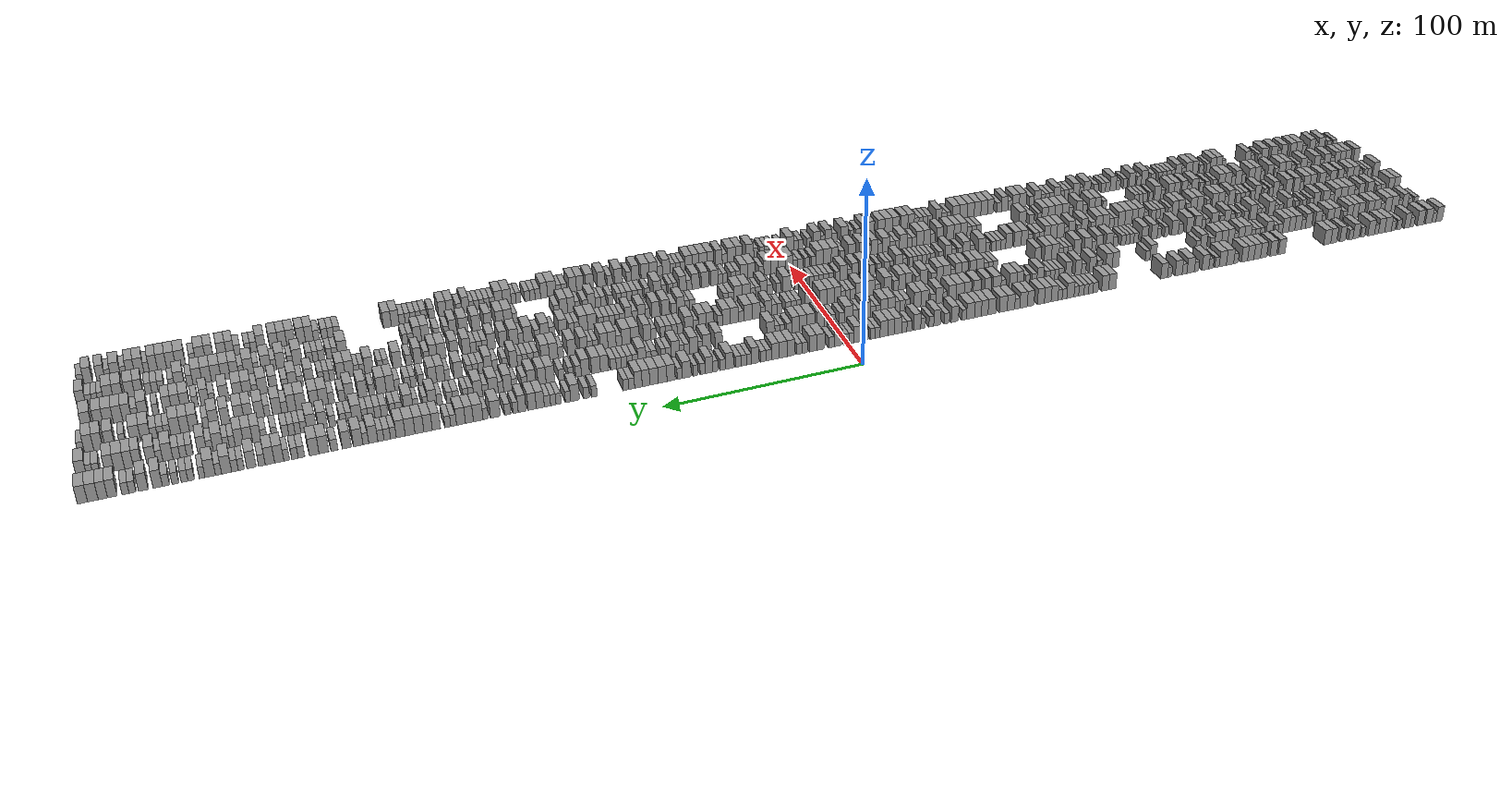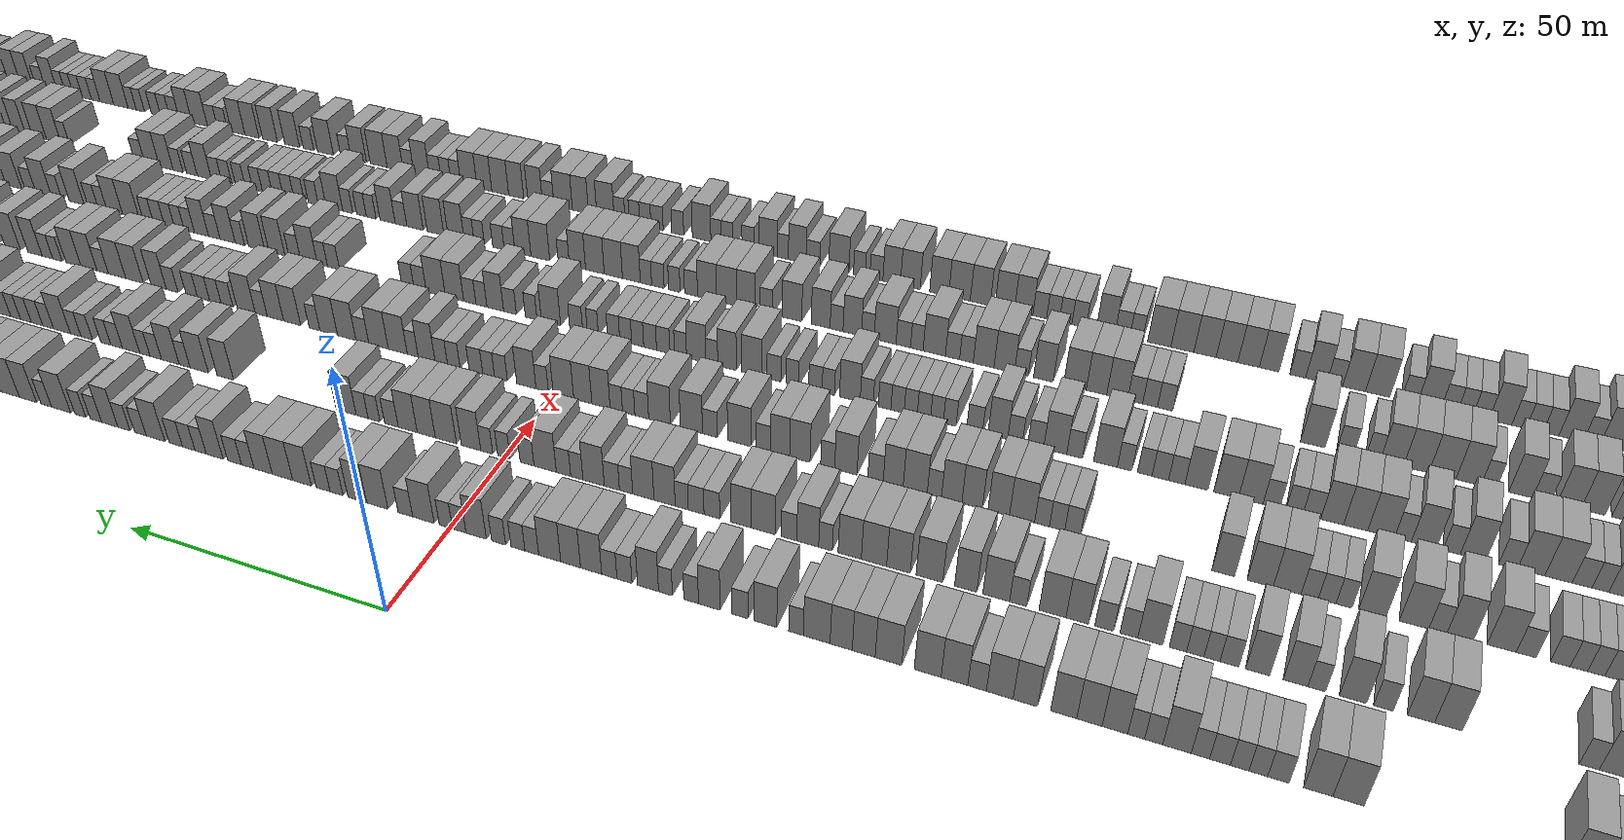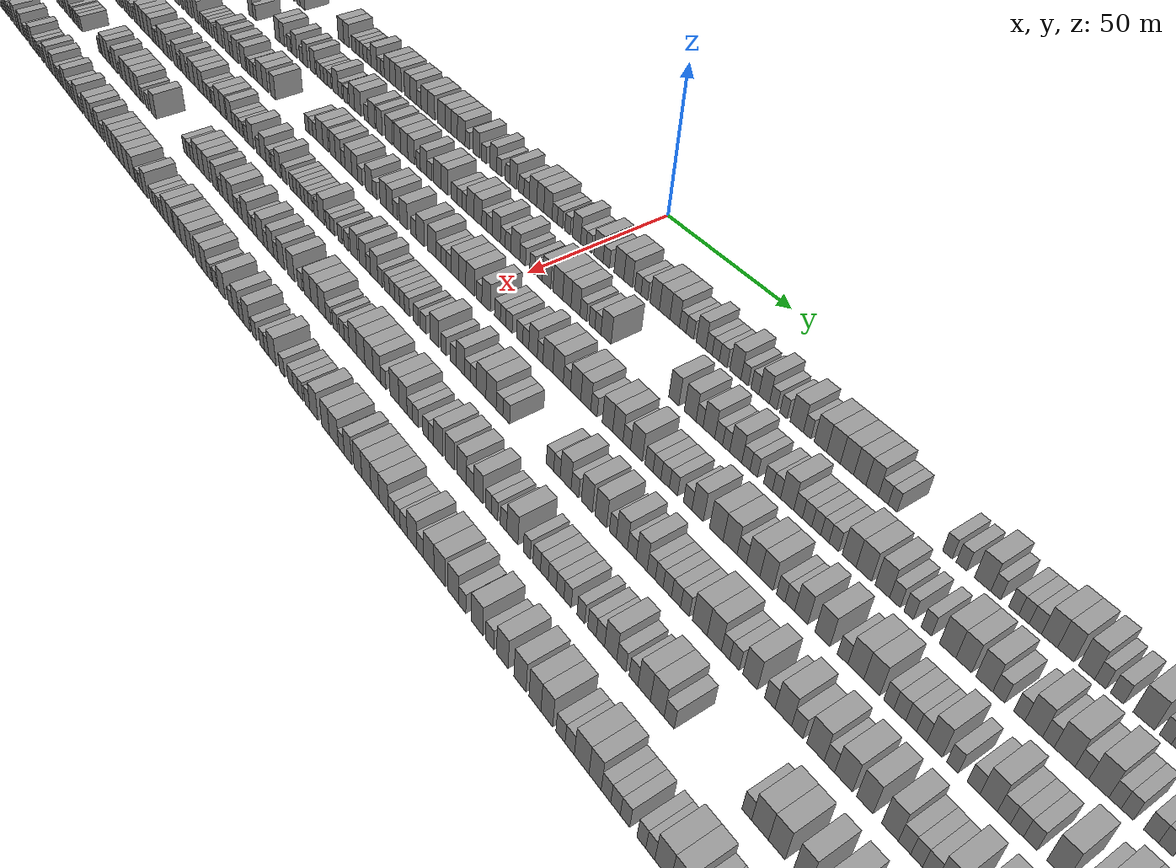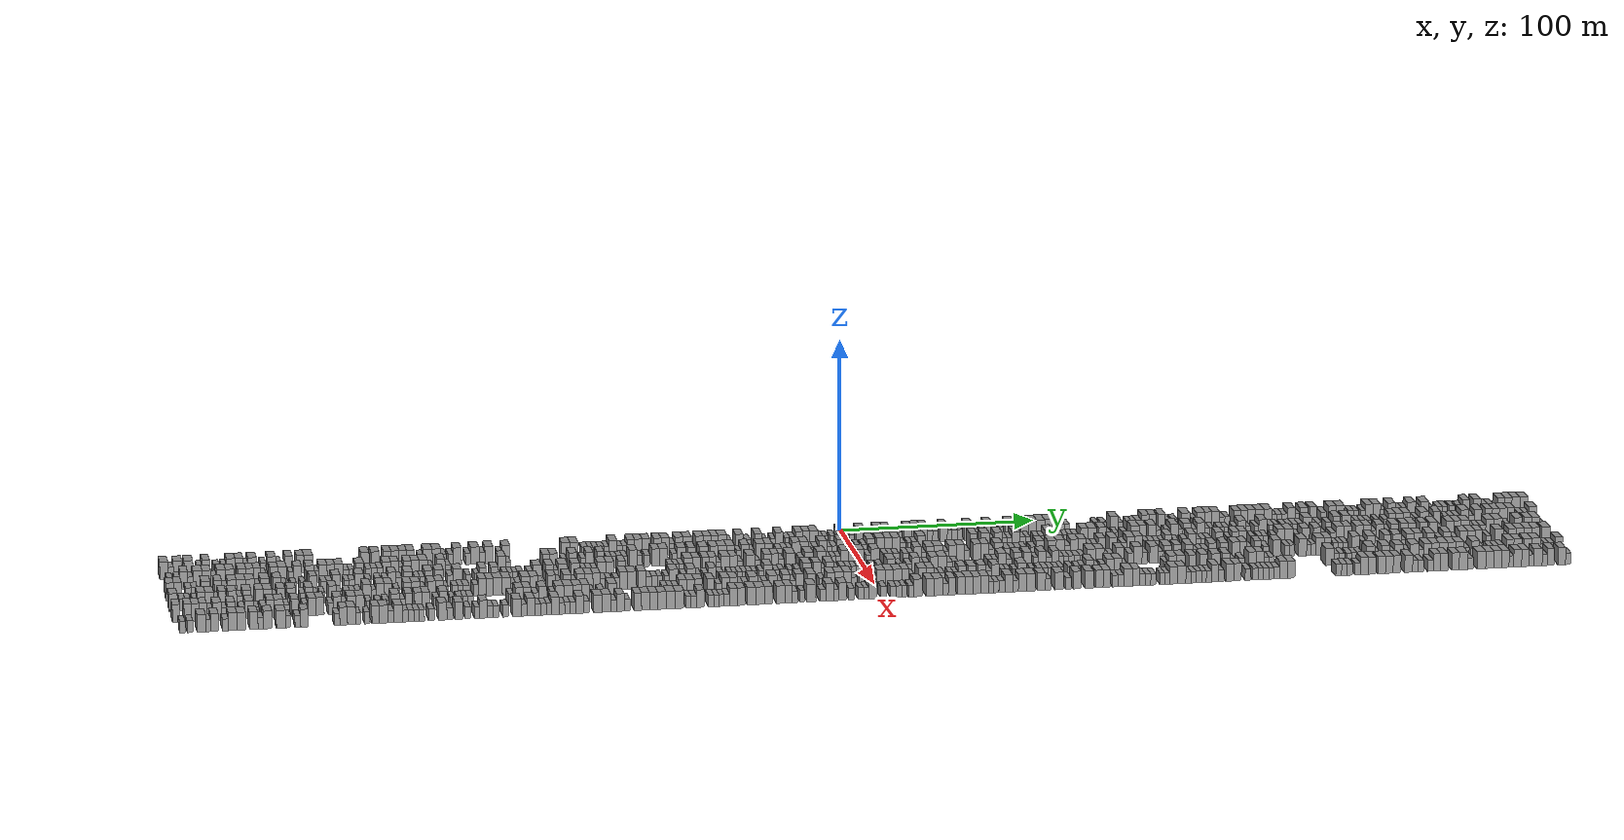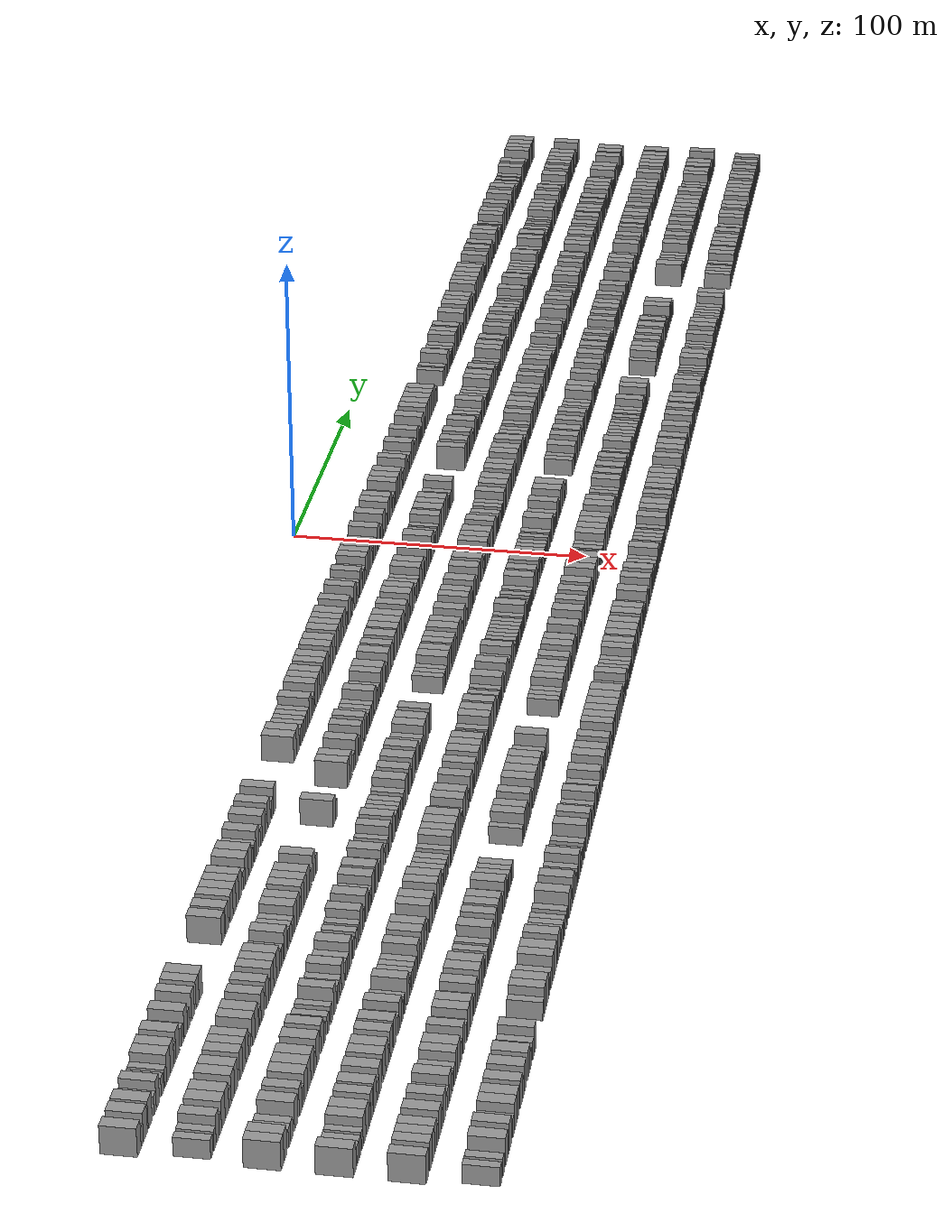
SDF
<sdf version="1.6">
 <world name="default">
  <scene>
   <sky><clouds><speed>12</speed></clouds></sky>
   <ambient>0.4 0.4 0.4 1</ambient>
   <background>0.7 0.7 0.7 1</background>
   <shadows>1</shadows>
  </scene>
  <gravity>0 0 -9.8066</gravity>
  <magnetic_field>6e-06 2.3e-05 -4.2e-05</magnetic_field>
  <physics default="0" name="default_physics" type="ode">
   <ode>
    <solver>
     <type>quick</type>
     <iters>10</iters>
     <sor>1.0</sor>
     <use_dynamic_moi_rescaling>0</use_dynamic_moi_rescaling>
    </solver>
    <constraints>
     <cfm>0</cfm>
     <erp>0.2</erp>
     <contact_max_correcting_vel>100</contact_max_correcting_vel>
     <contact_surface_layer>0.001</contact_surface_layer>
    </constraints>
   </ode>
   <max_step_size>0.004</max_step_size>
   <real_time_factor>1</real_time_factor>
   <real_time_update_rate>250</real_time_update_rate>
  </physics>
  <light name="sun" type="directional">
   <pose>0 0 10 0 0 0</pose>
   <diffuse>0.8 0.8 0.8 1</diffuse>
   <specular>0.2 0.2 0.2 1</specular>
   <attenuation>
    <range>1000</range>
    <constant>0.9</constant>
    <linear>0.01</linear>
    <quadratic>0.001</quadratic>
   </attenuation>
   <direction>-0.5 0.1 -0.9</direction>
  </light>
  <model name="building_1">
   <static>1</static>
   <pose>25.0000 -347.9249 0 0.000000 0.000000 0.000000</pose>
   <link name="link">
    <pose>0 0 4.50 0 0 0</pose>
    <collision name="collision"><geometry><box><size>10.0000 4.1502 9.0000</size></box></geometry></collision>
    <visual name="visual">
     <cast_shadows>0</cast_shadows>
     <geometry><box><size>10.0000 4.1502 9.0000</size></box></geometry>
     <material>
      <script>
       <uri>model://grey_wall/materials/scripts</uri>
       <uri>model://grey_wall/materials/textures</uri>
       <name>vrc/grey_wall</name>
      </script>
     </material>
    </visual>
   </link>
  </model>
  <model name="building_2">
   <static>1</static>
   <pose>25.0000 -344.5336 0 0.000000 0.000000 0.000000</pose>
   <link name="link">
    <pose>0 0 3.00 0 0 0</pose>
    <collision name="collision"><geometry><box><size>10.0000 2.6324 6.0000</size></box></geometry></collision>
    <visual name="visual">
     <cast_shadows>0</cast_shadows>
     <geometry><box><size>10.0000 2.6324 6.0000</size></box></geometry>
     <material>
      <script>
       <uri>model://grey_wall/materials/scripts</uri>
       <uri>model://grey_wall/materials/textures</uri>
       <name>vrc/grey_wall</name>
      </script>
     </material>
    </visual>
   </link>
  </model>
  <model name="building_3">
   <static>1</static>
   <pose>25.0000 -341.0188 0 0.000000 0.000000 0.000000</pose>
   <link name="link">
    <pose>0 0 4.50 0 0 0</pose>
    <collision name="collision"><geometry><box><size>10.0000 4.3973 9.0000</size></box></geometry></collision>
    <visual name="visual">
     <cast_shadows>0</cast_shadows>
     <geometry><box><size>10.0000 4.3973 9.0000</size></box></geometry>
     <material>
      <script>
       <uri>model://grey_wall/materials/scripts</uri>
       <uri>model://grey_wall/materials/textures</uri>
       <name>vrc/grey_wall</name>
      </script>
     </material>
    </visual>
   </link>
  </model>
  <model name="building_4">
   <static>1</static>
   <pose>25.0000 -335.6352 0 0.000000 0.000000 0.000000</pose>
   <link name="link">
    <pose>0 0 4.50 0 0 0</pose>
    <collision name="collision"><geometry><box><size>10.0000 4.3697 9.0000</size></box></geometry></collision>
    <visual name="visual">
     <cast_shadows>0</cast_shadows>
     <geometry><box><size>10.0000 4.3697 9.0000</size></box></geometry>
     <material>
      <script>
       <uri>model://grey_wall/materials/scripts</uri>
       <uri>model://grey_wall/materials/textures</uri>
       <name>vrc/grey_wall</name>
      </script>
     </material>
    </visual>
   </link>
  </model>
  <model name="building_5">
   <static>1</static>
   <pose>25.0000 -330.1107 0 0.000000 0.000000 0.000000</pose>
   <link name="link">
    <pose>0 0 3.00 0 0 0</pose>
    <collision name="collision"><geometry><box><size>10.0000 2.6794 6.0000</size></box></geometry></collision>
    <visual name="visual">
     <cast_shadows>0</cast_shadows>
     <geometry><box><size>10.0000 2.6794 6.0000</size></box></geometry>
     <material>
      <script>
       <uri>model://grey_wall/materials/scripts</uri>
       <uri>model://grey_wall/materials/textures</uri>
       <name>vrc/grey_wall</name>
      </script>
     </material>
    </visual>
   </link>
  </model>
  <model name="building_6">
   <static>1</static>
   <pose>25.0000 -326.9440 0 0.000000 0.000000 0.000000</pose>
   <link name="link">
    <pose>0 0 4.50 0 0 0</pose>
    <collision name="collision"><geometry><box><size>10.0000 3.6540 9.0000</size></box></geometry></collision>
    <visual name="visual">
     <cast_shadows>0</cast_shadows>
     <geometry><box><size>10.0000 3.6540 9.0000</size></box></geometry>
     <material>
      <script>
       <uri>model://grey_wall/materials/scripts</uri>
       <uri>model://grey_wall/materials/textures</uri>
       <name>vrc/grey_wall</name>
      </script>
     </material>
    </visual>
   </link>
  </model>
  <model name="building_7">
   <static>1</static>
   <pose>25.0000 -321.6880 0 0.000000 0.000000 0.000000</pose>
   <link name="link">
    <pose>0 0 3.00 0 0 0</pose>
    <collision name="collision"><geometry><box><size>10.0000 2.8580 6.0000</size></box></geometry></collision>
    <visual name="visual">
     <cast_shadows>0</cast_shadows>
     <geometry><box><size>10.0000 2.8580 6.0000</size></box></geometry>
     <material>
      <script>
       <uri>model://grey_wall/materials/scripts</uri>
       <uri>model://grey_wall/materials/textures</uri>
       <name>vrc/grey_wall</name>
      </script>
     </material>
    </visual>
   </link>
  </model>
  <model name="building_8">
   <static>1</static>
   <pose>25.0000 -317.9588 0 0.000000 0.000000 0.000000</pose>
   <link name="link">
    <pose>0 0 3.00 0 0 0</pose>
    <collision name="collision"><geometry><box><size>10.0000 2.6003 6.0000</size></box></geometry></collision>
    <visual name="visual">
     <cast_shadows>0</cast_shadows>
     <geometry><box><size>10.0000 2.6003 6.0000</size></box></geometry>
     <material>
      <script>
       <uri>model://grey_wall/materials/scripts</uri>
       <uri>model://grey_wall/materials/textures</uri>
       <name>vrc/grey_wall</name>
      </script>
     </material>
    </visual>
   </link>
  </model>
  <model name="building_9">
   <static>1</static>
   <pose>25.0000 -314.4956 0 0.000000 0.000000 0.000000</pose>
   <link name="link">
    <pose>0 0 4.50 0 0 0</pose>
    <collision name="collision"><geometry><box><size>10.0000 4.3263 9.0000</size></box></geometry></collision>
    <visual name="visual">
     <cast_shadows>0</cast_shadows>
     <geometry><box><size>10.0000 4.3263 9.0000</size></box></geometry>
     <material>
      <script>
       <uri>model://grey_wall/materials/scripts</uri>
       <uri>model://grey_wall/materials/textures</uri>
       <name>vrc/grey_wall</name>
      </script>
     </material>
    </visual>
   </link>
  </model>
  <model name="building_10">
   <static>1</static>
   <pose>25.0000 -310.3089 0 0.000000 0.000000 0.000000</pose>
   <link name="link">
    <pose>0 0 4.50 0 0 0</pose>
    <collision name="collision"><geometry><box><size>10.0000 4.0471 9.0000</size></box></geometry></collision>
    <visual name="visual">
     <cast_shadows>0</cast_shadows>
     <geometry><box><size>10.0000 4.0471 9.0000</size></box></geometry>
     <material>
      <script>
       <uri>model://grey_wall/materials/scripts</uri>
       <uri>model://grey_wall/materials/textures</uri>
       <name>vrc/grey_wall</name>
      </script>
     </material>
    </visual>
   </link>
  </model>
  <model name="building_11">
   <static>1</static>
   <pose>25.0000 -307.0615 0 0.000000 0.000000 0.000000</pose>
   <link name="link">
    <pose>0 0 3.00 0 0 0</pose>
    <collision name="collision"><geometry><box><size>10.0000 2.4477 6.0000</size></box></geometry></collision>
    <visual name="visual">
     <cast_shadows>0</cast_shadows>
     <geometry><box><size>10.0000 2.4477 6.0000</size></box></geometry>
     <material>
      <script>
       <uri>model://grey_wall/materials/scripts</uri>
       <uri>model://grey_wall/materials/textures</uri>
       <name>vrc/grey_wall</name>
      </script>
     </material>
    </visual>
   </link>
  </model>
  <model name="building_12">
   <static>1</static>
   <pose>25.0000 -303.6712 0 0.000000 0.000000 0.000000</pose>
   <link name="link">
    <pose>0 0 4.50 0 0 0</pose>
    <collision name="collision"><geometry><box><size>10.0000 4.3329 9.0000</size></box></geometry></collision>
    <visual name="visual">
     <cast_shadows>0</cast_shadows>
     <geometry><box><size>10.0000 4.3329 9.0000</size></box></geometry>
     <material>
      <script>
       <uri>model://grey_wall/materials/scripts</uri>
       <uri>model://grey_wall/materials/textures</uri>
       <name>vrc/grey_wall</name>
      </script>
     </material>
    </visual>
   </link>
  </model>
  <model name="building_13">
   <static>1</static>
   <pose>25.0000 -298.2506 0 0.000000 0.000000 0.000000</pose>
   <link name="link">
    <pose>0 0 3.00 0 0 0</pose>
    <collision name="collision"><geometry><box><size>10.0000 2.5081 6.0000</size></box></geometry></collision>
    <visual name="visual">
     <cast_shadows>0</cast_shadows>
     <geometry><box><size>10.0000 2.5081 6.0000</size></box></geometry>
     <material>
      <script>
       <uri>model://grey_wall/materials/scripts</uri>
       <uri>model://grey_wall/materials/textures</uri>
       <name>vrc/grey_wall</name>
      </script>
     </material>
    </visual>
   </link>
  </model>
  <model name="building_14">
   <static>1</static>
   <pose>25.0000 -293.9473 0 0.000000 0.000000 0.000000</pose>
   <link name="link">
    <pose>0 0 4.50 0 0 0</pose>
    <collision name="collision"><geometry><box><size>10.0000 4.0985 9.0000</size></box></geometry></collision>
    <visual name="visual">
     <cast_shadows>0</cast_shadows>
     <geometry><box><size>10.0000 4.0985 9.0000</size></box></geometry>
     <material>
      <script>
       <uri>model://grey_wall/materials/scripts</uri>
       <uri>model://grey_wall/materials/textures</uri>
       <name>vrc/grey_wall</name>
      </script>
     </material>
    </visual>
   </link>
  </model>
  <model name="building_15">
   <static>1</static>
   <pose>25.0000 -290.5645 0 0.000000 0.000000 0.000000</pose>
   <link name="link">
    <pose>0 0 3.00 0 0 0</pose>
    <collision name="collision"><geometry><box><size>10.0000 2.6670 6.0000</size></box></geometry></collision>
    <visual name="visual">
     <cast_shadows>0</cast_shadows>
     <geometry><box><size>10.0000 2.6670 6.0000</size></box></geometry>
     <material>
      <script>
       <uri>model://grey_wall/materials/scripts</uri>
       <uri>model://grey_wall/materials/textures</uri>
       <name>vrc/grey_wall</name>
      </script>
     </material>
    </visual>
   </link>
  </model>
  <model name="building_16">
   <static>1</static>
   <pose>25.0000 -285.4173 0 0.000000 0.000000 0.000000</pose>
   <link name="link">
    <pose>0 0 4.50 0 0 0</pose>
    <collision name="collision"><geometry><box><size>10.0000 3.6275 9.0000</size></box></geometry></collision>
    <visual name="visual">
     <cast_shadows>0</cast_shadows>
     <geometry><box><size>10.0000 3.6275 9.0000</size></box></geometry>
     <material>
      <script>
       <uri>model://grey_wall/materials/scripts</uri>
       <uri>model://grey_wall/materials/textures</uri>
       <name>vrc/grey_wall</name>
      </script>
     </material>
    </visual>
   </link>
  </model>
  <model name="building_17">
   <static>1</static>
   <pose>25.0000 -279.7335 0 0.000000 0.000000 0.000000</pose>
   <link name="link">
    <pose>0 0 4.50 0 0 0</pose>
    <collision name="collision"><geometry><box><size>10.0000 3.7400 9.0000</size></box></geometry></collision>
    <visual name="visual">
     <cast_shadows>0</cast_shadows>
     <geometry><box><size>10.0000 3.7400 9.0000</size></box></geometry>
     <material>
      <script>
       <uri>model://grey_wall/materials/scripts</uri>
       <uri>model://grey_wall/materials/textures</uri>
       <name>vrc/grey_wall</name>
      </script>
     </material>
    </visual>
   </link>
  </model>
  <model name="building_18">
   <static>1</static>
   <pose>25.0000 -275.6532 0 0.000000 0.000000 0.000000</pose>
   <link name="link">
    <pose>0 0 4.50 0 0 0</pose>
    <collision name="collision"><geometry><box><size>10.0000 4.4206 9.0000</size></box></geometry></collision>
    <visual name="visual">
     <cast_shadows>0</cast_shadows>
     <geometry><box><size>10.0000 4.4206 9.0000</size></box></geometry>
     <material>
      <script>
       <uri>model://grey_wall/materials/scripts</uri>
       <uri>model://grey_wall/materials/textures</uri>
       <name>vrc/grey_wall</name>
      </script>
     </material>
    </visual>
   </link>
  </model>
  <model name="building_19">
   <static>1</static>
   <pose>25.0000 -247.1640 0 0.000000 0.000000 0.000000</pose>
   <link name="link">
    <pose>0 0 4.50 0 0 0</pose>
    <collision name="collision"><geometry><box><size>10.0000 4.1859 9.0000</size></box></geometry></collision>
    <visual name="visual">
     <cast_shadows>0</cast_shadows>
     <geometry><box><size>10.0000 4.1859 9.0000</size></box></geometry>
     <material>
      <script>
       <uri>model://grey_wall/materials/scripts</uri>
       <uri>model://grey_wall/materials/textures</uri>
       <name>vrc/grey_wall</name>
      </script>
     </material>
    </visual>
   </link>
  </model>
  <model name="building_20">
   <static>1</static>
   <pose>25.0000 -241.9784 0 0.000000 0.000000 0.000000</pose>
   <link name="link">
    <pose>0 0 4.50 0 0 0</pose>
    <collision name="collision"><geometry><box><size>10.0000 4.1853 9.0000</size></box></geometry></collision>
    <visual name="visual">
     <cast_shadows>0</cast_shadows>
     <geometry><box><size>10.0000 4.1853 9.0000</size></box></geometry>
     <material>
      <script>
       <uri>model://grey_wall/materials/scripts</uri>
       <uri>model://grey_wall/materials/textures</uri>
       <name>vrc/grey_wall</name>
      </script>
     </material>
    </visual>
   </link>
  </model>
  <model name="building_21">
   <static>1</static>
   <pose>25.0000 -235.9583 0 0.000000 0.000000 0.000000</pose>
   <link name="link">
    <pose>0 0 4.50 0 0 0</pose>
    <collision name="collision"><geometry><box><size>10.0000 3.8551 9.0000</size></box></geometry></collision>
    <visual name="visual">
     <cast_shadows>0</cast_shadows>
     <geometry><box><size>10.0000 3.8551 9.0000</size></box></geometry>
     <material>
      <script>
       <uri>model://grey_wall/materials/scripts</uri>
       <uri>model://grey_wall/materials/textures</uri>
       <name>vrc/grey_wall</name>
      </script>
     </material>
    </visual>
   </link>
  </model>
  <model name="building_22">
   <static>1</static>
   <pose>25.0000 -232.0075 0 0.000000 0.000000 0.000000</pose>
   <link name="link">
    <pose>0 0 4.50 0 0 0</pose>
    <collision name="collision"><geometry><box><size>10.0000 4.0465 9.0000</size></box></geometry></collision>
    <visual name="visual">
     <cast_shadows>0</cast_shadows>
     <geometry><box><size>10.0000 4.0465 9.0000</size></box></geometry>
     <material>
      <script>
       <uri>model://grey_wall/materials/scripts</uri>
       <uri>model://grey_wall/materials/textures</uri>
       <name>vrc/grey_wall</name>
      </script>
     </material>
    </visual>
   </link>
  </model>
  <model name="building_23">
   <static>1</static>
   <pose>25.0000 -228.0677 0 0.000000 0.000000 0.000000</pose>
   <link name="link">
    <pose>0 0 4.50 0 0 0</pose>
    <collision name="collision"><geometry><box><size>10.0000 3.8331 9.0000</size></box></geometry></collision>
    <visual name="visual">
     <cast_shadows>0</cast_shadows>
     <geometry><box><size>10.0000 3.8331 9.0000</size></box></geometry>
     <material>
      <script>
       <uri>model://grey_wall/materials/scripts</uri>
       <uri>model://grey_wall/materials/textures</uri>
       <name>vrc/grey_wall</name>
      </script>
     </material>
    </visual>
   </link>
  </model>
  <model name="building_24">
   <static>1</static>
   <pose>25.0000 -224.2501 0 0.000000 0.000000 0.000000</pose>
   <link name="link">
    <pose>0 0 4.50 0 0 0</pose>
    <collision name="collision"><geometry><box><size>10.0000 3.8020 9.0000</size></box></geometry></collision>
    <visual name="visual">
     <cast_shadows>0</cast_shadows>
     <geometry><box><size>10.0000 3.8020 9.0000</size></box></geometry>
     <material>
      <script>
       <uri>model://grey_wall/materials/scripts</uri>
       <uri>model://grey_wall/materials/textures</uri>
       <name>vrc/grey_wall</name>
      </script>
     </material>
    </visual>
   </link>
  </model>
  <model name="building_25">
   <static>1</static>
   <pose>25.0000 -219.0061 0 0.000000 0.000000 0.000000</pose>
   <link name="link">
    <pose>0 0 3.00 0 0 0</pose>
    <collision name="collision"><geometry><box><size>10.0000 2.6861 6.0000</size></box></geometry></collision>
    <visual name="visual">
     <cast_shadows>0</cast_shadows>
     <geometry><box><size>10.0000 2.6861 6.0000</size></box></geometry>
     <material>
      <script>
       <uri>model://grey_wall/materials/scripts</uri>
       <uri>model://grey_wall/materials/textures</uri>
       <name>vrc/grey_wall</name>
      </script>
     </material>
    </visual>
   </link>
  </model>
  <model name="building_26">
   <static>1</static>
   <pose>25.0000 -215.4294 0 0.000000 0.000000 0.000000</pose>
   <link name="link">
    <pose>0 0 4.50 0 0 0</pose>
    <collision name="collision"><geometry><box><size>10.0000 4.4671 9.0000</size></box></geometry></collision>
    <visual name="visual">
     <cast_shadows>0</cast_shadows>
     <geometry><box><size>10.0000 4.4671 9.0000</size></box></geometry>
     <material>
      <script>
       <uri>model://grey_wall/materials/scripts</uri>
       <uri>model://grey_wall/materials/textures</uri>
       <name>vrc/grey_wall</name>
      </script>
     </material>
    </visual>
   </link>
  </model>
  <model name="building_27">
   <static>1</static>
   <pose>25.0000 -211.0135 0 0.000000 0.000000 0.000000</pose>
   <link name="link">
    <pose>0 0 4.50 0 0 0</pose>
    <collision name="collision"><geometry><box><size>10.0000 4.3647 9.0000</size></box></geometry></collision>
    <visual name="visual">
     <cast_shadows>0</cast_shadows>
     <geometry><box><size>10.0000 4.3647 9.0000</size></box></geometry>
     <material>
      <script>
       <uri>model://grey_wall/materials/scripts</uri>
       <uri>model://grey_wall/materials/textures</uri>
       <name>vrc/grey_wall</name>
      </script>
     </material>
    </visual>
   </link>
  </model>
  <model name="building_28">
   <static>1</static>
   <pose>25.0000 -207.5304 0 0.000000 0.000000 0.000000</pose>
   <link name="link">
    <pose>0 0 3.00 0 0 0</pose>
    <collision name="collision"><geometry><box><size>10.0000 2.6015 6.0000</size></box></geometry></collision>
    <visual name="visual">
     <cast_shadows>0</cast_shadows>
     <geometry><box><size>10.0000 2.6015 6.0000</size></box></geometry>
     <material>
      <script>
       <uri>model://grey_wall/materials/scripts</uri>
       <uri>model://grey_wall/materials/textures</uri>
       <name>vrc/grey_wall</name>
      </script>
     </material>
    </visual>
   </link>
  </model>
  <model name="building_29">
   <static>1</static>
   <pose>25.0000 -203.9215 0 0.000000 0.000000 0.000000</pose>
   <link name="link">
    <pose>0 0 3.00 0 0 0</pose>
    <collision name="collision"><geometry><box><size>10.0000 2.6162 6.0000</size></box></geometry></collision>
    <visual name="visual">
     <cast_shadows>0</cast_shadows>
     <geometry><box><size>10.0000 2.6162 6.0000</size></box></geometry>
     <material>
      <script>
       <uri>model://grey_wall/materials/scripts</uri>
       <uri>model://grey_wall/materials/textures</uri>
       <name>vrc/grey_wall</name>
      </script>
     </material>
    </visual>
   </link>
  </model>
  <model name="building_30">
   <static>1</static>
   <pose>25.0000 -200.5595 0 0.000000 0.000000 0.000000</pose>
   <link name="link">
    <pose>0 0 4.50 0 0 0</pose>
    <collision name="collision"><geometry><box><size>10.0000 4.1078 9.0000</size></box></geometry></collision>
    <visual name="visual">
     <cast_shadows>0</cast_shadows>
     <geometry><box><size>10.0000 4.1078 9.0000</size></box></geometry>
     <material>
      <script>
       <uri>model://grey_wall/materials/scripts</uri>
       <uri>model://grey_wall/materials/textures</uri>
       <name>vrc/grey_wall</name>
      </script>
     </material>
    </visual>
   </link>
  </model>
  <model name="building_31">
   <static>1</static>
   <pose>25.0000 -195.2044 0 0.000000 0.000000 0.000000</pose>
   <link name="link">
    <pose>0 0 3.00 0 0 0</pose>
    <collision name="collision"><geometry><box><size>10.0000 2.6025 6.0000</size></box></geometry></collision>
    <visual name="visual">
     <cast_shadows>0</cast_shadows>
     <geometry><box><size>10.0000 2.6025 6.0000</size></box></geometry>
     <material>
      <script>
       <uri>model://grey_wall/materials/scripts</uri>
       <uri>model://grey_wall/materials/textures</uri>
       <name>vrc/grey_wall</name>
      </script>
     </material>
    </visual>
   </link>
  </model>
  <model name="building_32">
   <static>1</static>
   <pose>25.0000 -191.6888 0 0.000000 0.000000 0.000000</pose>
   <link name="link">
    <pose>0 0 4.50 0 0 0</pose>
    <collision name="collision"><geometry><box><size>10.0000 4.4286 9.0000</size></box></geometry></collision>
    <visual name="visual">
     <cast_shadows>0</cast_shadows>
     <geometry><box><size>10.0000 4.4286 9.0000</size></box></geometry>
     <material>
      <script>
       <uri>model://grey_wall/materials/scripts</uri>
       <uri>model://grey_wall/materials/textures</uri>
       <name>vrc/grey_wall</name>
      </script>
     </material>
    </visual>
   </link>
  </model>
  <model name="building_33">
   <static>1</static>
   <pose>25.0000 -188.0455 0 0.000000 0.000000 0.000000</pose>
   <link name="link">
    <pose>0 0 3.00 0 0 0</pose>
    <collision name="collision"><geometry><box><size>10.0000 2.8581 6.0000</size></box></geometry></collision>
    <visual name="visual">
     <cast_shadows>0</cast_shadows>
     <geometry><box><size>10.0000 2.8581 6.0000</size></box></geometry>
     <material>
      <script>
       <uri>model://grey_wall/materials/scripts</uri>
       <uri>model://grey_wall/materials/textures</uri>
       <name>vrc/grey_wall</name>
      </script>
     </material>
    </visual>
   </link>
  </model>
  <model name="building_34">
   <static>1</static>
   <pose>25.0000 -184.5348 0 0.000000 0.000000 0.000000</pose>
   <link name="link">
    <pose>0 0 4.50 0 0 0</pose>
    <collision name="collision"><geometry><box><size>10.0000 4.1634 9.0000</size></box></geometry></collision>
    <visual name="visual">
     <cast_shadows>0</cast_shadows>
     <geometry><box><size>10.0000 4.1634 9.0000</size></box></geometry>
     <material>
      <script>
       <uri>model://grey_wall/materials/scripts</uri>
       <uri>model://grey_wall/materials/textures</uri>
       <name>vrc/grey_wall</name>
      </script>
     </material>
    </visual>
   </link>
  </model>
  <model name="building_35">
   <static>1</static>
   <pose>25.0000 -179.1760 0 0.000000 0.000000 0.000000</pose>
   <link name="link">
    <pose>0 0 3.00 0 0 0</pose>
    <collision name="collision"><geometry><box><size>10.0000 2.5541 6.0000</size></box></geometry></collision>
    <visual name="visual">
     <cast_shadows>0</cast_shadows>
     <geometry><box><size>10.0000 2.5541 6.0000</size></box></geometry>
     <material>
      <script>
       <uri>model://grey_wall/materials/scripts</uri>
       <uri>model://grey_wall/materials/textures</uri>
       <name>vrc/grey_wall</name>
      </script>
     </material>
    </visual>
   </link>
  </model>
  <model name="building_36">
   <static>1</static>
   <pose>25.0000 -175.9138 0 0.000000 0.000000 0.000000</pose>
   <link name="link">
    <pose>0 0 4.50 0 0 0</pose>
    <collision name="collision"><geometry><box><size>10.0000 3.9703 9.0000</size></box></geometry></collision>
    <visual name="visual">
     <cast_shadows>0</cast_shadows>
     <geometry><box><size>10.0000 3.9703 9.0000</size></box></geometry>
     <material>
      <script>
       <uri>model://grey_wall/materials/scripts</uri>
       <uri>model://grey_wall/materials/textures</uri>
       <name>vrc/grey_wall</name>
      </script>
     </material>
    </visual>
   </link>
  </model>
  <model name="building_37">
   <static>1</static>
   <pose>25.0000 -145.5327 0 0.000000 0.000000 0.000000</pose>
   <link name="link">
    <pose>0 0 4.50 0 0 0</pose>
    <collision name="collision"><geometry><box><size>10.0000 4.2640 9.0000</size></box></geometry></collision>
    <visual name="visual">
     <cast_shadows>0</cast_shadows>
     <geometry><box><size>10.0000 4.2640 9.0000</size></box></geometry>
     <material>
      <script>
       <uri>model://grey_wall/materials/scripts</uri>
       <uri>model://grey_wall/materials/textures</uri>
       <name>vrc/grey_wall</name>
      </script>
     </material>
    </visual>
   </link>
  </model>
  <model name="building_38">
   <static>1</static>
   <pose>25.0000 -141.3918 0 0.000000 0.000000 0.000000</pose>
   <link name="link">
    <pose>0 0 4.50 0 0 0</pose>
    <collision name="collision"><geometry><box><size>10.0000 4.0177 9.0000</size></box></geometry></collision>
    <visual name="visual">
     <cast_shadows>0</cast_shadows>
     <geometry><box><size>10.0000 4.0177 9.0000</size></box></geometry>
     <material>
      <script>
       <uri>model://grey_wall/materials/scripts</uri>
       <uri>model://grey_wall/materials/textures</uri>
       <name>vrc/grey_wall</name>
      </script>
     </material>
    </visual>
   </link>
  </model>
  <model name="building_39">
   <static>1</static>
   <pose>25.0000 -135.8840 0 0.000000 0.000000 0.000000</pose>
   <link name="link">
    <pose>0 0 3.00 0 0 0</pose>
    <collision name="collision"><geometry><box><size>10.0000 2.9980 6.0000</size></box></geometry></collision>
    <visual name="visual">
     <cast_shadows>0</cast_shadows>
     <geometry><box><size>10.0000 2.9980 6.0000</size></box></geometry>
     <material>
      <script>
       <uri>model://grey_wall/materials/scripts</uri>
       <uri>model://grey_wall/materials/textures</uri>
       <name>vrc/grey_wall</name>
      </script>
     </material>
    </visual>
   </link>
  </model>
  <model name="building_40">
   <static>1</static>
   <pose>25.0000 -133.0798 0 0.000000 0.000000 0.000000</pose>
   <link name="link">
    <pose>0 0 3.00 0 0 0</pose>
    <collision name="collision"><geometry><box><size>10.0000 2.6105 6.0000</size></box></geometry></collision>
    <visual name="visual">
     <cast_shadows>0</cast_shadows>
     <geometry><box><size>10.0000 2.6105 6.0000</size></box></geometry>
     <material>
      <script>
       <uri>model://grey_wall/materials/scripts</uri>
       <uri>model://grey_wall/materials/textures</uri>
       <name>vrc/grey_wall</name>
      </script>
     </material>
    </visual>
   </link>
  </model>
  <model name="building_41">
   <static>1</static>
   <pose>25.0000 -130.4676 0 0.000000 0.000000 0.000000</pose>
   <link name="link">
    <pose>0 0 3.00 0 0 0</pose>
    <collision name="collision"><geometry><box><size>10.0000 2.6140 6.0000</size></box></geometry></collision>
    <visual name="visual">
     <cast_shadows>0</cast_shadows>
     <geometry><box><size>10.0000 2.6140 6.0000</size></box></geometry>
     <material>
      <script>
       <uri>model://grey_wall/materials/scripts</uri>
       <uri>model://grey_wall/materials/textures</uri>
       <name>vrc/grey_wall</name>
      </script>
     </material>
    </visual>
   </link>
  </model>
  <model name="building_42">
   <static>1</static>
   <pose>25.0000 -127.6731 0 0.000000 0.000000 0.000000</pose>
   <link name="link">
    <pose>0 0 3.00 0 0 0</pose>
    <collision name="collision"><geometry><box><size>10.0000 2.9750 6.0000</size></box></geometry></collision>
    <visual name="visual">
     <cast_shadows>0</cast_shadows>
     <geometry><box><size>10.0000 2.9750 6.0000</size></box></geometry>
     <material>
      <script>
       <uri>model://grey_wall/materials/scripts</uri>
       <uri>model://grey_wall/materials/textures</uri>
       <name>vrc/grey_wall</name>
      </script>
     </material>
    </visual>
   </link>
  </model>
  <model name="building_43">
   <static>1</static>
   <pose>25.0000 -124.8753 0 0.000000 0.000000 0.000000</pose>
   <link name="link">
    <pose>0 0 3.00 0 0 0</pose>
    <collision name="collision"><geometry><box><size>10.0000 2.6206 6.0000</size></box></geometry></collision>
    <visual name="visual">
     <cast_shadows>0</cast_shadows>
     <geometry><box><size>10.0000 2.6206 6.0000</size></box></geometry>
     <material>
      <script>
       <uri>model://grey_wall/materials/scripts</uri>
       <uri>model://grey_wall/materials/textures</uri>
       <name>vrc/grey_wall</name>
      </script>
     </material>
    </visual>
   </link>
  </model>
  <model name="building_44">
   <static>1</static>
   <pose>25.0000 -121.4992 0 0.000000 0.000000 0.000000</pose>
   <link name="link">
    <pose>0 0 4.50 0 0 0</pose>
    <collision name="collision"><geometry><box><size>10.0000 4.1316 9.0000</size></box></geometry></collision>
    <visual name="visual">
     <cast_shadows>0</cast_shadows>
     <geometry><box><size>10.0000 4.1316 9.0000</size></box></geometry>
     <material>
      <script>
       <uri>model://grey_wall/materials/scripts</uri>
       <uri>model://grey_wall/materials/textures</uri>
       <name>vrc/grey_wall</name>
      </script>
     </material>
    </visual>
   </link>
  </model>
  <model name="building_45">
   <static>1</static>
   <pose>25.0000 -118.1087 0 0.000000 0.000000 0.000000</pose>
   <link name="link">
    <pose>0 0 3.00 0 0 0</pose>
    <collision name="collision"><geometry><box><size>10.0000 2.6494 6.0000</size></box></geometry></collision>
    <visual name="visual">
     <cast_shadows>0</cast_shadows>
     <geometry><box><size>10.0000 2.6494 6.0000</size></box></geometry>
     <material>
      <script>
       <uri>model://grey_wall/materials/scripts</uri>
       <uri>model://grey_wall/materials/textures</uri>
       <name>vrc/grey_wall</name>
      </script>
     </material>
    </visual>
   </link>
  </model>
  <model name="building_46">
   <static>1</static>
   <pose>25.0000 -115.5429 0 0.000000 0.000000 0.000000</pose>
   <link name="link">
    <pose>0 0 3.00 0 0 0</pose>
    <collision name="collision"><geometry><box><size>10.0000 2.4822 6.0000</size></box></geometry></collision>
    <visual name="visual">
     <cast_shadows>0</cast_shadows>
     <geometry><box><size>10.0000 2.4822 6.0000</size></box></geometry>
     <material>
      <script>
       <uri>model://grey_wall/materials/scripts</uri>
       <uri>model://grey_wall/materials/textures</uri>
       <name>vrc/grey_wall</name>
      </script>
     </material>
    </visual>
   </link>
  </model>
  <model name="building_47">
   <static>1</static>
   <pose>25.0000 -112.4067 0 0.000000 0.000000 0.000000</pose>
   <link name="link">
    <pose>0 0 4.50 0 0 0</pose>
    <collision name="collision"><geometry><box><size>10.0000 3.7904 9.0000</size></box></geometry></collision>
    <visual name="visual">
     <cast_shadows>0</cast_shadows>
     <geometry><box><size>10.0000 3.7904 9.0000</size></box></geometry>
     <material>
      <script>
       <uri>model://grey_wall/materials/scripts</uri>
       <uri>model://grey_wall/materials/textures</uri>
       <name>vrc/grey_wall</name>
      </script>
     </material>
    </visual>
   </link>
  </model>
  <model name="building_48">
   <static>1</static>
   <pose>25.0000 -108.6141 0 0.000000 0.000000 0.000000</pose>
   <link name="link">
    <pose>0 0 4.50 0 0 0</pose>
    <collision name="collision"><geometry><box><size>10.0000 3.7948 9.0000</size></box></geometry></collision>
    <visual name="visual">
     <cast_shadows>0</cast_shadows>
     <geometry><box><size>10.0000 3.7948 9.0000</size></box></geometry>
     <material>
      <script>
       <uri>model://grey_wall/materials/scripts</uri>
       <uri>model://grey_wall/materials/textures</uri>
       <name>vrc/grey_wall</name>
      </script>
     </material>
    </visual>
   </link>
  </model>
  <model name="building_49">
   <static>1</static>
   <pose>25.0000 -104.7550 0 0.000000 0.000000 0.000000</pose>
   <link name="link">
    <pose>0 0 4.50 0 0 0</pose>
    <collision name="collision"><geometry><box><size>10.0000 3.9233 9.0000</size></box></geometry></collision>
    <visual name="visual">
     <cast_shadows>0</cast_shadows>
     <geometry><box><size>10.0000 3.9233 9.0000</size></box></geometry>
     <material>
      <script>
       <uri>model://grey_wall/materials/scripts</uri>
       <uri>model://grey_wall/materials/textures</uri>
       <name>vrc/grey_wall</name>
      </script>
     </material>
    </visual>
   </link>
  </model>
  <model name="building_50">
   <static>1</static>
   <pose>25.0000 -98.9192 0 0.000000 0.000000 0.000000</pose>
   <link name="link">
    <pose>0 0 4.50 0 0 0</pose>
    <collision name="collision"><geometry><box><size>10.0000 3.7483 9.0000</size></box></geometry></collision>
    <visual name="visual">
     <cast_shadows>0</cast_shadows>
     <geometry><box><size>10.0000 3.7483 9.0000</size></box></geometry>
     <material>
      <script>
       <uri>model://grey_wall/materials/scripts</uri>
       <uri>model://grey_wall/materials/textures</uri>
       <name>vrc/grey_wall</name>
      </script>
     </material>
    </visual>
   </link>
  </model>
  <model name="building_51">
   <static>1</static>
   <pose>25.0000 -94.9759 0 0.000000 0.000000 0.000000</pose>
   <link name="link">
    <pose>0 0 4.50 0 0 0</pose>
    <collision name="collision"><geometry><box><size>10.0000 4.1382 9.0000</size></box></geometry></collision>
    <visual name="visual">
     <cast_shadows>0</cast_shadows>
     <geometry><box><size>10.0000 4.1382 9.0000</size></box></geometry>
     <material>
      <script>
       <uri>model://grey_wall/materials/scripts</uri>
       <uri>model://grey_wall/materials/textures</uri>
       <name>vrc/grey_wall</name>
      </script>
     </material>
    </visual>
   </link>
  </model>
  <model name="building_52">
   <static>1</static>
   <pose>25.0000 -91.4587 0 0.000000 0.000000 0.000000</pose>
   <link name="link">
    <pose>0 0 3.00 0 0 0</pose>
    <collision name="collision"><geometry><box><size>10.0000 2.8963 6.0000</size></box></geometry></collision>
    <visual name="visual">
     <cast_shadows>0</cast_shadows>
     <geometry><box><size>10.0000 2.8963 6.0000</size></box></geometry>
     <material>
      <script>
       <uri>model://grey_wall/materials/scripts</uri>
       <uri>model://grey_wall/materials/textures</uri>
       <name>vrc/grey_wall</name>
      </script>
     </material>
    </visual>
   </link>
  </model>
  <model name="building_53">
   <static>1</static>
   <pose>25.0000 -87.9144 0 0.000000 0.000000 0.000000</pose>
   <link name="link">
    <pose>0 0 4.50 0 0 0</pose>
    <collision name="collision"><geometry><box><size>10.0000 4.1924 9.0000</size></box></geometry></collision>
    <visual name="visual">
     <cast_shadows>0</cast_shadows>
     <geometry><box><size>10.0000 4.1924 9.0000</size></box></geometry>
     <material>
      <script>
       <uri>model://grey_wall/materials/scripts</uri>
       <uri>model://grey_wall/materials/textures</uri>
       <name>vrc/grey_wall</name>
      </script>
     </material>
    </visual>
   </link>
  </model>
  <model name="building_54">
   <static>1</static>
   <pose>25.0000 -83.6774 0 0.000000 0.000000 0.000000</pose>
   <link name="link">
    <pose>0 0 4.50 0 0 0</pose>
    <collision name="collision"><geometry><box><size>10.0000 4.2815 9.0000</size></box></geometry></collision>
    <visual name="visual">
     <cast_shadows>0</cast_shadows>
     <geometry><box><size>10.0000 4.2815 9.0000</size></box></geometry>
     <material>
      <script>
       <uri>model://grey_wall/materials/scripts</uri>
       <uri>model://grey_wall/materials/textures</uri>
       <name>vrc/grey_wall</name>
      </script>
     </material>
    </visual>
   </link>
  </model>
  <model name="building_55">
   <static>1</static>
   <pose>25.0000 -77.3896 0 0.000000 0.000000 0.000000</pose>
   <link name="link">
    <pose>0 0 4.50 0 0 0</pose>
    <collision name="collision"><geometry><box><size>10.0000 4.2941 9.0000</size></box></geometry></collision>
    <visual name="visual">
     <cast_shadows>0</cast_shadows>
     <geometry><box><size>10.0000 4.2941 9.0000</size></box></geometry>
     <material>
      <script>
       <uri>model://grey_wall/materials/scripts</uri>
       <uri>model://grey_wall/materials/textures</uri>
       <name>vrc/grey_wall</name>
      </script>
     </material>
    </visual>
   </link>
  </model>
  <model name="building_56">
   <static>1</static>
   <pose>25.0000 -73.3744 0 0.000000 0.000000 0.000000</pose>
   <link name="link">
    <pose>0 0 4.50 0 0 0</pose>
    <collision name="collision"><geometry><box><size>10.0000 3.7363 9.0000</size></box></geometry></collision>
    <visual name="visual">
     <cast_shadows>0</cast_shadows>
     <geometry><box><size>10.0000 3.7363 9.0000</size></box></geometry>
     <material>
      <script>
       <uri>model://grey_wall/materials/scripts</uri>
       <uri>model://grey_wall/materials/textures</uri>
       <name>vrc/grey_wall</name>
      </script>
     </material>
    </visual>
   </link>
  </model>
  <model name="building_57">
   <static>1</static>
   <pose>25.0000 -69.6779 0 0.000000 0.000000 0.000000</pose>
   <link name="link">
    <pose>0 0 4.50 0 0 0</pose>
    <collision name="collision"><geometry><box><size>10.0000 3.6568 9.0000</size></box></geometry></collision>
    <visual name="visual">
     <cast_shadows>0</cast_shadows>
     <geometry><box><size>10.0000 3.6568 9.0000</size></box></geometry>
     <material>
      <script>
       <uri>model://grey_wall/materials/scripts</uri>
       <uri>model://grey_wall/materials/textures</uri>
       <name>vrc/grey_wall</name>
      </script>
     </material>
    </visual>
   </link>
  </model>
  <model name="building_58">
   <static>1</static>
   <pose>25.0000 -65.6266 0 0.000000 0.000000 0.000000</pose>
   <link name="link">
    <pose>0 0 4.50 0 0 0</pose>
    <collision name="collision"><geometry><box><size>10.0000 4.4459 9.0000</size></box></geometry></collision>
    <visual name="visual">
     <cast_shadows>0</cast_shadows>
     <geometry><box><size>10.0000 4.4459 9.0000</size></box></geometry>
     <material>
      <script>
       <uri>model://grey_wall/materials/scripts</uri>
       <uri>model://grey_wall/materials/textures</uri>
       <name>vrc/grey_wall</name>
      </script>
     </material>
    </visual>
   </link>
  </model>
  <model name="building_59">
   <static>1</static>
   <pose>25.0000 -62.1754 0 0.000000 0.000000 0.000000</pose>
   <link name="link">
    <pose>0 0 3.00 0 0 0</pose>
    <collision name="collision"><geometry><box><size>10.0000 2.4565 6.0000</size></box></geometry></collision>
    <visual name="visual">
     <cast_shadows>0</cast_shadows>
     <geometry><box><size>10.0000 2.4565 6.0000</size></box></geometry>
     <material>
      <script>
       <uri>model://grey_wall/materials/scripts</uri>
       <uri>model://grey_wall/materials/textures</uri>
       <name>vrc/grey_wall</name>
      </script>
     </material>
    </visual>
   </link>
  </model>
  <model name="building_60">
   <static>1</static>
   <pose>25.0000 -56.9956 0 0.000000 0.000000 0.000000</pose>
   <link name="link">
    <pose>0 0 4.50 0 0 0</pose>
    <collision name="collision"><geometry><box><size>10.0000 3.9030 9.0000</size></box></geometry></collision>
    <visual name="visual">
     <cast_shadows>0</cast_shadows>
     <geometry><box><size>10.0000 3.9030 9.0000</size></box></geometry>
     <material>
      <script>
       <uri>model://grey_wall/materials/scripts</uri>
       <uri>model://grey_wall/materials/textures</uri>
       <name>vrc/grey_wall</name>
      </script>
     </material>
    </visual>
   </link>
  </model>
  <model name="building_61">
   <static>1</static>
   <pose>25.0000 -52.6533 0 0.000000 0.000000 0.000000</pose>
   <link name="link">
    <pose>0 0 3.00 0 0 0</pose>
    <collision name="collision"><geometry><box><size>10.0000 2.7818 6.0000</size></box></geometry></collision>
    <visual name="visual">
     <cast_shadows>0</cast_shadows>
     <geometry><box><size>10.0000 2.7818 6.0000</size></box></geometry>
     <material>
      <script>
       <uri>model://grey_wall/materials/scripts</uri>
       <uri>model://grey_wall/materials/textures</uri>
       <name>vrc/grey_wall</name>
      </script>
     </material>
    </visual>
   </link>
  </model>
  <model name="building_62">
   <static>1</static>
   <pose>25.0000 -47.3935 0 0.000000 0.000000 0.000000</pose>
   <link name="link">
    <pose>0 0 4.50 0 0 0</pose>
    <collision name="collision"><geometry><box><size>10.0000 3.7377 9.0000</size></box></geometry></collision>
    <visual name="visual">
     <cast_shadows>0</cast_shadows>
     <geometry><box><size>10.0000 3.7377 9.0000</size></box></geometry>
     <material>
      <script>
       <uri>model://grey_wall/materials/scripts</uri>
       <uri>model://grey_wall/materials/textures</uri>
       <name>vrc/grey_wall</name>
      </script>
     </material>
    </visual>
   </link>
  </model>
  <model name="building_63">
   <static>1</static>
   <pose>25.0000 -44.2400 0 0.000000 0.000000 0.000000</pose>
   <link name="link">
    <pose>0 0 3.00 0 0 0</pose>
    <collision name="collision"><geometry><box><size>10.0000 2.5693 6.0000</size></box></geometry></collision>
    <visual name="visual">
     <cast_shadows>0</cast_shadows>
     <geometry><box><size>10.0000 2.5693 6.0000</size></box></geometry>
     <material>
      <script>
       <uri>model://grey_wall/materials/scripts</uri>
       <uri>model://grey_wall/materials/textures</uri>
       <name>vrc/grey_wall</name>
      </script>
     </material>
    </visual>
   </link>
  </model>
  <model name="building_64">
   <static>1</static>
   <pose>25.0000 -39.7307 0 0.000000 0.000000 0.000000</pose>
   <link name="link">
    <pose>0 0 3.00 0 0 0</pose>
    <collision name="collision"><geometry><box><size>10.0000 2.4493 6.0000</size></box></geometry></collision>
    <visual name="visual">
     <cast_shadows>0</cast_shadows>
     <geometry><box><size>10.0000 2.4493 6.0000</size></box></geometry>
     <material>
      <script>
       <uri>model://grey_wall/materials/scripts</uri>
       <uri>model://grey_wall/materials/textures</uri>
       <name>vrc/grey_wall</name>
      </script>
     </material>
    </visual>
   </link>
  </model>
  <model name="building_65">
   <static>1</static>
   <pose>25.0000 -36.6411 0 0.000000 0.000000 0.000000</pose>
   <link name="link">
    <pose>0 0 4.50 0 0 0</pose>
    <collision name="collision"><geometry><box><size>10.0000 3.7300 9.0000</size></box></geometry></collision>
    <visual name="visual">
     <cast_shadows>0</cast_shadows>
     <geometry><box><size>10.0000 3.7300 9.0000</size></box></geometry>
     <material>
      <script>
       <uri>model://grey_wall/materials/scripts</uri>
       <uri>model://grey_wall/materials/textures</uri>
       <name>vrc/grey_wall</name>
      </script>
     </material>
    </visual>
   </link>
  </model>
  <model name="building_66">
   <static>1</static>
   <pose>25.0000 -32.4248 0 0.000000 0.000000 0.000000</pose>
   <link name="link">
    <pose>0 0 3.00 0 0 0</pose>
    <collision name="collision"><geometry><box><size>10.0000 2.7026 6.0000</size></box></geometry></collision>
    <visual name="visual">
     <cast_shadows>0</cast_shadows>
     <geometry><box><size>10.0000 2.7026 6.0000</size></box></geometry>
     <material>
      <script>
       <uri>model://grey_wall/materials/scripts</uri>
       <uri>model://grey_wall/materials/textures</uri>
       <name>vrc/grey_wall</name>
      </script>
     </material>
    </visual>
   </link>
  </model>
  <model name="building_67">
   <static>1</static>
   <pose>25.0000 -29.6952 0 0.000000 0.000000 0.000000</pose>
   <link name="link">
    <pose>0 0 3.00 0 0 0</pose>
    <collision name="collision"><geometry><box><size>10.0000 2.7568 6.0000</size></box></geometry></collision>
    <visual name="visual">
     <cast_shadows>0</cast_shadows>
     <geometry><box><size>10.0000 2.7568 6.0000</size></box></geometry>
     <material>
      <script>
       <uri>model://grey_wall/materials/scripts</uri>
       <uri>model://grey_wall/materials/textures</uri>
       <name>vrc/grey_wall</name>
      </script>
     </material>
    </visual>
   </link>
  </model>
  <model name="building_68">
   <static>1</static>
   <pose>25.0000 -26.3937 0 0.000000 0.000000 0.000000</pose>
   <link name="link">
    <pose>0 0 4.50 0 0 0</pose>
    <collision name="collision"><geometry><box><size>10.0000 3.8461 9.0000</size></box></geometry></collision>
    <visual name="visual">
     <cast_shadows>0</cast_shadows>
     <geometry><box><size>10.0000 3.8461 9.0000</size></box></geometry>
     <material>
      <script>
       <uri>model://grey_wall/materials/scripts</uri>
       <uri>model://grey_wall/materials/textures</uri>
       <name>vrc/grey_wall</name>
      </script>
     </material>
    </visual>
   </link>
  </model>
  <model name="building_69">
   <static>1</static>
   <pose>25.0000 -22.6545 0 0.000000 0.000000 0.000000</pose>
   <link name="link">
    <pose>0 0 4.50 0 0 0</pose>
    <collision name="collision"><geometry><box><size>10.0000 3.6325 9.0000</size></box></geometry></collision>
    <visual name="visual">
     <cast_shadows>0</cast_shadows>
     <geometry><box><size>10.0000 3.6325 9.0000</size></box></geometry>
     <material>
      <script>
       <uri>model://grey_wall/materials/scripts</uri>
       <uri>model://grey_wall/materials/textures</uri>
       <name>vrc/grey_wall</name>
      </script>
     </material>
    </visual>
   </link>
  </model>
  <model name="building_70">
   <static>1</static>
   <pose>25.0000 -18.7950 0 0.000000 0.000000 0.000000</pose>
   <link name="link">
    <pose>0 0 4.50 0 0 0</pose>
    <collision name="collision"><geometry><box><size>10.0000 4.0864 9.0000</size></box></geometry></collision>
    <visual name="visual">
     <cast_shadows>0</cast_shadows>
     <geometry><box><size>10.0000 4.0864 9.0000</size></box></geometry>
     <material>
      <script>
       <uri>model://grey_wall/materials/scripts</uri>
       <uri>model://grey_wall/materials/textures</uri>
       <name>vrc/grey_wall</name>
      </script>
     </material>
    </visual>
   </link>
  </model>
  <model name="building_71">
   <static>1</static>
   <pose>25.0000 -15.4544 0 0.000000 0.000000 0.000000</pose>
   <link name="link">
    <pose>0 0 3.00 0 0 0</pose>
    <collision name="collision"><geometry><box><size>10.0000 2.5948 6.0000</size></box></geometry></collision>
    <visual name="visual">
     <cast_shadows>0</cast_shadows>
     <geometry><box><size>10.0000 2.5948 6.0000</size></box></geometry>
     <material>
      <script>
       <uri>model://grey_wall/materials/scripts</uri>
       <uri>model://grey_wall/materials/textures</uri>
       <name>vrc/grey_wall</name>
      </script>
     </material>
    </visual>
   </link>
  </model>
  <model name="building_72">
   <static>1</static>
   <pose>25.0000 -12.8511 0 0.000000 0.000000 0.000000</pose>
   <link name="link">
    <pose>0 0 3.00 0 0 0</pose>
    <collision name="collision"><geometry><box><size>10.0000 2.6118 6.0000</size></box></geometry></collision>
    <visual name="visual">
     <cast_shadows>0</cast_shadows>
     <geometry><box><size>10.0000 2.6118 6.0000</size></box></geometry>
     <material>
      <script>
       <uri>model://grey_wall/materials/scripts</uri>
       <uri>model://grey_wall/materials/textures</uri>
       <name>vrc/grey_wall</name>
      </script>
     </material>
    </visual>
   </link>
  </model>
  <model name="building_73">
   <static>1</static>
   <pose>25.0000 -9.2134 0 0.000000 0.000000 0.000000</pose>
   <link name="link">
    <pose>0 0 3.00 0 0 0</pose>
    <collision name="collision"><geometry><box><size>10.0000 2.6637 6.0000</size></box></geometry></collision>
    <visual name="visual">
     <cast_shadows>0</cast_shadows>
     <geometry><box><size>10.0000 2.6637 6.0000</size></box></geometry>
     <material>
      <script>
       <uri>model://grey_wall/materials/scripts</uri>
       <uri>model://grey_wall/materials/textures</uri>
       <name>vrc/grey_wall</name>
      </script>
     </material>
    </visual>
   </link>
  </model>
  <model name="building_74">
   <static>1</static>
   <pose>25.0000 -4.9287 0 0.000000 0.000000 0.000000</pose>
   <link name="link">
    <pose>0 0 4.50 0 0 0</pose>
    <collision name="collision"><geometry><box><size>10.0000 3.9057 9.0000</size></box></geometry></collision>
    <visual name="visual">
     <cast_shadows>0</cast_shadows>
     <geometry><box><size>10.0000 3.9057 9.0000</size></box></geometry>
     <material>
      <script>
       <uri>model://grey_wall/materials/scripts</uri>
       <uri>model://grey_wall/materials/textures</uri>
       <name>vrc/grey_wall</name>
      </script>
     </material>
    </visual>
   </link>
  </model>
  <model name="building_75">
   <static>1</static>
   <pose>25.0000 -1.6831 0 0.000000 0.000000 0.000000</pose>
   <link name="link">
    <pose>0 0 3.00 0 0 0</pose>
    <collision name="collision"><geometry><box><size>10.0000 2.5856 6.0000</size></box></geometry></collision>
    <visual name="visual">
     <cast_shadows>0</cast_shadows>
     <geometry><box><size>10.0000 2.5856 6.0000</size></box></geometry>
     <material>
      <script>
       <uri>model://grey_wall/materials/scripts</uri>
       <uri>model://grey_wall/materials/textures</uri>
       <name>vrc/grey_wall</name>
      </script>
     </material>
    </visual>
   </link>
  </model>
  <model name="building_76">
   <static>1</static>
   <pose>25.0000 0.8925 0 0.000000 0.000000 0.000000</pose>
   <link name="link">
    <pose>0 0 3.00 0 0 0</pose>
    <collision name="collision"><geometry><box><size>10.0000 2.5656 6.0000</size></box></geometry></collision>
    <visual name="visual">
     <cast_shadows>0</cast_shadows>
     <geometry><box><size>10.0000 2.5656 6.0000</size></box></geometry>
     <material>
      <script>
       <uri>model://grey_wall/materials/scripts</uri>
       <uri>model://grey_wall/materials/textures</uri>
       <name>vrc/grey_wall</name>
      </script>
     </material>
    </visual>
   </link>
  </model>
  <model name="building_77">
   <static>1</static>
   <pose>25.0000 5.2809 0 0.000000 0.000000 0.000000</pose>
   <link name="link">
    <pose>0 0 4.50 0 0 0</pose>
    <collision name="collision"><geometry><box><size>10.0000 4.2112 9.0000</size></box></geometry></collision>
    <visual name="visual">
     <cast_shadows>0</cast_shadows>
     <geometry><box><size>10.0000 4.2112 9.0000</size></box></geometry>
     <material>
      <script>
       <uri>model://grey_wall/materials/scripts</uri>
       <uri>model://grey_wall/materials/textures</uri>
       <name>vrc/grey_wall</name>
      </script>
     </material>
    </visual>
   </link>
  </model>
  <model name="building_78">
   <static>1</static>
   <pose>25.0000 8.8354 0 0.000000 0.000000 0.000000</pose>
   <link name="link">
    <pose>0 0 3.00 0 0 0</pose>
    <collision name="collision"><geometry><box><size>10.0000 2.8979 6.0000</size></box></geometry></collision>
    <visual name="visual">
     <cast_shadows>0</cast_shadows>
     <geometry><box><size>10.0000 2.8979 6.0000</size></box></geometry>
     <material>
      <script>
       <uri>model://grey_wall/materials/scripts</uri>
       <uri>model://grey_wall/materials/textures</uri>
       <name>vrc/grey_wall</name>
      </script>
     </material>
    </visual>
   </link>
  </model>
  <model name="building_79">
   <static>1</static>
   <pose>25.0000 14.4239 0 0.000000 0.000000 0.000000</pose>
   <link name="link">
    <pose>0 0 4.50 0 0 0</pose>
    <collision name="collision"><geometry><box><size>10.0000 4.2790 9.0000</size></box></geometry></collision>
    <visual name="visual">
     <cast_shadows>0</cast_shadows>
     <geometry><box><size>10.0000 4.2790 9.0000</size></box></geometry>
     <material>
      <script>
       <uri>model://grey_wall/materials/scripts</uri>
       <uri>model://grey_wall/materials/textures</uri>
       <name>vrc/grey_wall</name>
      </script>
     </material>
    </visual>
   </link>
  </model>
  <model name="building_80">
   <static>1</static>
   <pose>25.0000 18.4285 0 0.000000 0.000000 0.000000</pose>
   <link name="link">
    <pose>0 0 4.50 0 0 0</pose>
    <collision name="collision"><geometry><box><size>10.0000 3.7302 9.0000</size></box></geometry></collision>
    <visual name="visual">
     <cast_shadows>0</cast_shadows>
     <geometry><box><size>10.0000 3.7302 9.0000</size></box></geometry>
     <material>
      <script>
       <uri>model://grey_wall/materials/scripts</uri>
       <uri>model://grey_wall/materials/textures</uri>
       <name>vrc/grey_wall</name>
      </script>
     </material>
    </visual>
   </link>
  </model>
  <model name="building_81">
   <static>1</static>
   <pose>25.0000 22.6097 0 0.000000 0.000000 0.000000</pose>
   <link name="link">
    <pose>0 0 3.00 0 0 0</pose>
    <collision name="collision"><geometry><box><size>10.0000 2.6323 6.0000</size></box></geometry></collision>
    <visual name="visual">
     <cast_shadows>0</cast_shadows>
     <geometry><box><size>10.0000 2.6323 6.0000</size></box></geometry>
     <material>
      <script>
       <uri>model://grey_wall/materials/scripts</uri>
       <uri>model://grey_wall/materials/textures</uri>
       <name>vrc/grey_wall</name>
      </script>
     </material>
    </visual>
   </link>
  </model>
  <model name="building_82">
   <static>1</static>
   <pose>25.0000 25.3507 0 0.000000 0.000000 0.000000</pose>
   <link name="link">
    <pose>0 0 3.00 0 0 0</pose>
    <collision name="collision"><geometry><box><size>10.0000 2.8498 6.0000</size></box></geometry></collision>
    <visual name="visual">
     <cast_shadows>0</cast_shadows>
     <geometry><box><size>10.0000 2.8498 6.0000</size></box></geometry>
     <material>
      <script>
       <uri>model://grey_wall/materials/scripts</uri>
       <uri>model://grey_wall/materials/textures</uri>
       <name>vrc/grey_wall</name>
      </script>
     </material>
    </visual>
   </link>
  </model>
  <model name="building_83">
   <static>1</static>
   <pose>25.0000 29.6966 0 0.000000 0.000000 0.000000</pose>
   <link name="link">
    <pose>0 0 4.50 0 0 0</pose>
    <collision name="collision"><geometry><box><size>10.0000 3.8418 9.0000</size></box></geometry></collision>
    <visual name="visual">
     <cast_shadows>0</cast_shadows>
     <geometry><box><size>10.0000 3.8418 9.0000</size></box></geometry>
     <material>
      <script>
       <uri>model://grey_wall/materials/scripts</uri>
       <uri>model://grey_wall/materials/textures</uri>
       <name>vrc/grey_wall</name>
      </script>
     </material>
    </visual>
   </link>
  </model>
  <model name="building_84">
   <static>1</static>
   <pose>25.0000 33.7455 0 0.000000 0.000000 0.000000</pose>
   <link name="link">
    <pose>0 0 4.50 0 0 0</pose>
    <collision name="collision"><geometry><box><size>10.0000 4.2562 9.0000</size></box></geometry></collision>
    <visual name="visual">
     <cast_shadows>0</cast_shadows>
     <geometry><box><size>10.0000 4.2562 9.0000</size></box></geometry>
     <material>
      <script>
       <uri>model://grey_wall/materials/scripts</uri>
       <uri>model://grey_wall/materials/textures</uri>
       <name>vrc/grey_wall</name>
      </script>
     </material>
    </visual>
   </link>
  </model>
  <model name="building_85">
   <static>1</static>
   <pose>25.0000 37.7928 0 0.000000 0.000000 0.000000</pose>
   <link name="link">
    <pose>0 0 4.50 0 0 0</pose>
    <collision name="collision"><geometry><box><size>10.0000 3.8383 9.0000</size></box></geometry></collision>
    <visual name="visual">
     <cast_shadows>0</cast_shadows>
     <geometry><box><size>10.0000 3.8383 9.0000</size></box></geometry>
     <material>
      <script>
       <uri>model://grey_wall/materials/scripts</uri>
       <uri>model://grey_wall/materials/textures</uri>
       <name>vrc/grey_wall</name>
      </script>
     </material>
    </visual>
   </link>
  </model>
  <model name="building_86">
   <static>1</static>
   <pose>25.0000 41.0383 0 0.000000 0.000000 0.000000</pose>
   <link name="link">
    <pose>0 0 3.00 0 0 0</pose>
    <collision name="collision"><geometry><box><size>10.0000 2.6528 6.0000</size></box></geometry></collision>
    <visual name="visual">
     <cast_shadows>0</cast_shadows>
     <geometry><box><size>10.0000 2.6528 6.0000</size></box></geometry>
     <material>
      <script>
       <uri>model://grey_wall/materials/scripts</uri>
       <uri>model://grey_wall/materials/textures</uri>
       <name>vrc/grey_wall</name>
      </script>
     </material>
    </visual>
   </link>
  </model>
  <model name="building_87">
   <static>1</static>
   <pose>25.0000 43.8298 0 0.000000 0.000000 0.000000</pose>
   <link name="link">
    <pose>0 0 3.00 0 0 0</pose>
    <collision name="collision"><geometry><box><size>10.0000 2.9301 6.0000</size></box></geometry></collision>
    <visual name="visual">
     <cast_shadows>0</cast_shadows>
     <geometry><box><size>10.0000 2.9301 6.0000</size></box></geometry>
     <material>
      <script>
       <uri>model://grey_wall/materials/scripts</uri>
       <uri>model://grey_wall/materials/textures</uri>
       <name>vrc/grey_wall</name>
      </script>
     </material>
    </visual>
   </link>
  </model>
  <model name="building_88">
   <static>1</static>
   <pose>25.0000 48.1031 0 0.000000 0.000000 0.000000</pose>
   <link name="link">
    <pose>0 0 4.50 0 0 0</pose>
    <collision name="collision"><geometry><box><size>10.0000 3.6164 9.0000</size></box></geometry></collision>
    <visual name="visual">
     <cast_shadows>0</cast_shadows>
     <geometry><box><size>10.0000 3.6164 9.0000</size></box></geometry>
     <material>
      <script>
       <uri>model://grey_wall/materials/scripts</uri>
       <uri>model://grey_wall/materials/textures</uri>
       <name>vrc/grey_wall</name>
      </script>
     </material>
    </visual>
   </link>
  </model>
  <model name="building_89">
   <static>1</static>
   <pose>25.0000 51.1237 0 0.000000 0.000000 0.000000</pose>
   <link name="link">
    <pose>0 0 3.00 0 0 0</pose>
    <collision name="collision"><geometry><box><size>10.0000 2.4249 6.0000</size></box></geometry></collision>
    <visual name="visual">
     <cast_shadows>0</cast_shadows>
     <geometry><box><size>10.0000 2.4249 6.0000</size></box></geometry>
     <material>
      <script>
       <uri>model://grey_wall/materials/scripts</uri>
       <uri>model://grey_wall/materials/textures</uri>
       <name>vrc/grey_wall</name>
      </script>
     </material>
    </visual>
   </link>
  </model>
  <model name="building_90">
   <static>1</static>
   <pose>25.0000 53.6947 0 0.000000 0.000000 0.000000</pose>
   <link name="link">
    <pose>0 0 3.00 0 0 0</pose>
    <collision name="collision"><geometry><box><size>10.0000 2.7171 6.0000</size></box></geometry></collision>
    <visual name="visual">
     <cast_shadows>0</cast_shadows>
     <geometry><box><size>10.0000 2.7171 6.0000</size></box></geometry>
     <material>
      <script>
       <uri>model://grey_wall/materials/scripts</uri>
       <uri>model://grey_wall/materials/textures</uri>
       <name>vrc/grey_wall</name>
      </script>
     </material>
    </visual>
   </link>
  </model>
  <model name="building_91">
   <static>1</static>
   <pose>25.0000 56.4846 0 0.000000 0.000000 0.000000</pose>
   <link name="link">
    <pose>0 0 3.00 0 0 0</pose>
    <collision name="collision"><geometry><box><size>10.0000 2.8627 6.0000</size></box></geometry></collision>
    <visual name="visual">
     <cast_shadows>0</cast_shadows>
     <geometry><box><size>10.0000 2.8627 6.0000</size></box></geometry>
     <material>
      <script>
       <uri>model://grey_wall/materials/scripts</uri>
       <uri>model://grey_wall/materials/textures</uri>
       <name>vrc/grey_wall</name>
      </script>
     </material>
    </visual>
   </link>
  </model>
  <model name="building_92">
   <static>1</static>
   <pose>25.0000 60.9548 0 0.000000 0.000000 0.000000</pose>
   <link name="link">
    <pose>0 0 4.50 0 0 0</pose>
    <collision name="collision"><geometry><box><size>10.0000 4.0776 9.0000</size></box></geometry></collision>
    <visual name="visual">
     <cast_shadows>0</cast_shadows>
     <geometry><box><size>10.0000 4.0776 9.0000</size></box></geometry>
     <material>
      <script>
       <uri>model://grey_wall/materials/scripts</uri>
       <uri>model://grey_wall/materials/textures</uri>
       <name>vrc/grey_wall</name>
      </script>
     </material>
    </visual>
   </link>
  </model>
  <model name="building_93">
   <static>1</static>
   <pose>25.0000 64.3066 0 0.000000 0.000000 0.000000</pose>
   <link name="link">
    <pose>0 0 3.00 0 0 0</pose>
    <collision name="collision"><geometry><box><size>10.0000 2.6260 6.0000</size></box></geometry></collision>
    <visual name="visual">
     <cast_shadows>0</cast_shadows>
     <geometry><box><size>10.0000 2.6260 6.0000</size></box></geometry>
     <material>
      <script>
       <uri>model://grey_wall/materials/scripts</uri>
       <uri>model://grey_wall/materials/textures</uri>
       <name>vrc/grey_wall</name>
      </script>
     </material>
    </visual>
   </link>
  </model>
  <model name="building_94">
   <static>1</static>
   <pose>25.0000 67.9862 0 0.000000 0.000000 0.000000</pose>
   <link name="link">
    <pose>0 0 3.00 0 0 0</pose>
    <collision name="collision"><geometry><box><size>10.0000 2.7333 6.0000</size></box></geometry></collision>
    <visual name="visual">
     <cast_shadows>0</cast_shadows>
     <geometry><box><size>10.0000 2.7333 6.0000</size></box></geometry>
     <material>
      <script>
       <uri>model://grey_wall/materials/scripts</uri>
       <uri>model://grey_wall/materials/textures</uri>
       <name>vrc/grey_wall</name>
      </script>
     </material>
    </visual>
   </link>
  </model>
  <model name="building_95">
   <static>1</static>
   <pose>25.0000 71.1924 0 0.000000 0.000000 0.000000</pose>
   <link name="link">
    <pose>0 0 4.50 0 0 0</pose>
    <collision name="collision"><geometry><box><size>10.0000 3.6791 9.0000</size></box></geometry></collision>
    <visual name="visual">
     <cast_shadows>0</cast_shadows>
     <geometry><box><size>10.0000 3.6791 9.0000</size></box></geometry>
     <material>
      <script>
       <uri>model://grey_wall/materials/scripts</uri>
       <uri>model://grey_wall/materials/textures</uri>
       <name>vrc/grey_wall</name>
      </script>
     </material>
    </visual>
   </link>
  </model>
  <model name="building_96">
   <static>1</static>
   <pose>25.0000 74.3214 0 0.000000 0.000000 0.000000</pose>
   <link name="link">
    <pose>0 0 3.00 0 0 0</pose>
    <collision name="collision"><geometry><box><size>10.0000 2.5788 6.0000</size></box></geometry></collision>
    <visual name="visual">
     <cast_shadows>0</cast_shadows>
     <geometry><box><size>10.0000 2.5788 6.0000</size></box></geometry>
     <material>
      <script>
       <uri>model://grey_wall/materials/scripts</uri>
       <uri>model://grey_wall/materials/textures</uri>
       <name>vrc/grey_wall</name>
      </script>
     </material>
    </visual>
   </link>
  </model>
  <model name="building_97">
   <static>1</static>
   <pose>25.0000 77.8457 0 0.000000 0.000000 0.000000</pose>
   <link name="link">
    <pose>0 0 3.00 0 0 0</pose>
    <collision name="collision"><geometry><box><size>10.0000 2.4698 6.0000</size></box></geometry></collision>
    <visual name="visual">
     <cast_shadows>0</cast_shadows>
     <geometry><box><size>10.0000 2.4698 6.0000</size></box></geometry>
     <material>
      <script>
       <uri>model://grey_wall/materials/scripts</uri>
       <uri>model://grey_wall/materials/textures</uri>
       <name>vrc/grey_wall</name>
      </script>
     </material>
    </visual>
   </link>
  </model>
  <model name="building_98">
   <static>1</static>
   <pose>25.0000 82.2850 0 0.000000 0.000000 0.000000</pose>
   <link name="link">
    <pose>0 0 4.50 0 0 0</pose>
    <collision name="collision"><geometry><box><size>10.0000 4.4087 9.0000</size></box></geometry></collision>
    <visual name="visual">
     <cast_shadows>0</cast_shadows>
     <geometry><box><size>10.0000 4.4087 9.0000</size></box></geometry>
     <material>
      <script>
       <uri>model://grey_wall/materials/scripts</uri>
       <uri>model://grey_wall/materials/textures</uri>
       <name>vrc/grey_wall</name>
      </script>
     </material>
    </visual>
   </link>
  </model>
  <model name="building_99">
   <static>1</static>
   <pose>25.0000 85.7219 0 0.000000 0.000000 0.000000</pose>
   <link name="link">
    <pose>0 0 3.00 0 0 0</pose>
    <collision name="collision"><geometry><box><size>10.0000 2.4652 6.0000</size></box></geometry></collision>
    <visual name="visual">
     <cast_shadows>0</cast_shadows>
     <geometry><box><size>10.0000 2.4652 6.0000</size></box></geometry>
     <material>
      <script>
       <uri>model://grey_wall/materials/scripts</uri>
       <uri>model://grey_wall/materials/textures</uri>
       <name>vrc/grey_wall</name>
      </script>
     </material>
    </visual>
   </link>
  </model>
  <model name="building_100">
   <static>1</static>
   <pose>25.0000 89.9709 0 0.000000 0.000000 0.000000</pose>
   <link name="link">
    <pose>0 0 4.50 0 0 0</pose>
    <collision name="collision"><geometry><box><size>10.0000 4.0329 9.0000</size></box></geometry></collision>
    <visual name="visual">
     <cast_shadows>0</cast_shadows>
     <geometry><box><size>10.0000 4.0329 9.0000</size></box></geometry>
     <material>
      <script>
       <uri>model://grey_wall/materials/scripts</uri>
       <uri>model://grey_wall/materials/textures</uri>
       <name>vrc/grey_wall</name>
      </script>
     </material>
    </visual>
   </link>
  </model>
  <model name="building_101">
   <static>1</static>
   <pose>25.0000 94.1253 0 0.000000 0.000000 0.000000</pose>
   <link name="link">
    <pose>0 0 4.50 0 0 0</pose>
    <collision name="collision"><geometry><box><size>10.0000 4.2759 9.0000</size></box></geometry></collision>
    <visual name="visual">
     <cast_shadows>0</cast_shadows>
     <geometry><box><size>10.0000 4.2759 9.0000</size></box></geometry>
     <material>
      <script>
       <uri>model://grey_wall/materials/scripts</uri>
       <uri>model://grey_wall/materials/textures</uri>
       <name>vrc/grey_wall</name>
      </script>
     </material>
    </visual>
   </link>
  </model>
  <model name="building_102">
   <static>1</static>
   <pose>25.0000 98.3312 0 0.000000 0.000000 0.000000</pose>
   <link name="link">
    <pose>0 0 4.50 0 0 0</pose>
    <collision name="collision"><geometry><box><size>10.0000 4.1359 9.0000</size></box></geometry></collision>
    <visual name="visual">
     <cast_shadows>0</cast_shadows>
     <geometry><box><size>10.0000 4.1359 9.0000</size></box></geometry>
     <material>
      <script>
       <uri>model://grey_wall/materials/scripts</uri>
       <uri>model://grey_wall/materials/textures</uri>
       <name>vrc/grey_wall</name>
      </script>
     </material>
    </visual>
   </link>
  </model>
  <model name="building_103">
   <static>1</static>
   <pose>25.0000 102.2628 0 0.000000 0.000000 0.000000</pose>
   <link name="link">
    <pose>0 0 4.50 0 0 0</pose>
    <collision name="collision"><geometry><box><size>10.0000 3.7273 9.0000</size></box></geometry></collision>
    <visual name="visual">
     <cast_shadows>0</cast_shadows>
     <geometry><box><size>10.0000 3.7273 9.0000</size></box></geometry>
     <material>
      <script>
       <uri>model://grey_wall/materials/scripts</uri>
       <uri>model://grey_wall/materials/textures</uri>
       <name>vrc/grey_wall</name>
      </script>
     </material>
    </visual>
   </link>
  </model>
  <model name="building_104">
   <static>1</static>
   <pose>25.0000 105.9567 0 0.000000 0.000000 0.000000</pose>
   <link name="link">
    <pose>0 0 4.50 0 0 0</pose>
    <collision name="collision"><geometry><box><size>10.0000 3.6606 9.0000</size></box></geometry></collision>
    <visual name="visual">
     <cast_shadows>0</cast_shadows>
     <geometry><box><size>10.0000 3.6606 9.0000</size></box></geometry>
     <material>
      <script>
       <uri>model://grey_wall/materials/scripts</uri>
       <uri>model://grey_wall/materials/textures</uri>
       <name>vrc/grey_wall</name>
      </script>
     </material>
    </visual>
   </link>
  </model>
  <model name="building_105">
   <static>1</static>
   <pose>25.0000 109.2327 0 0.000000 0.000000 0.000000</pose>
   <link name="link">
    <pose>0 0 3.00 0 0 0</pose>
    <collision name="collision"><geometry><box><size>10.0000 2.8913 6.0000</size></box></geometry></collision>
    <visual name="visual">
     <cast_shadows>0</cast_shadows>
     <geometry><box><size>10.0000 2.8913 6.0000</size></box></geometry>
     <material>
      <script>
       <uri>model://grey_wall/materials/scripts</uri>
       <uri>model://grey_wall/materials/textures</uri>
       <name>vrc/grey_wall</name>
      </script>
     </material>
    </visual>
   </link>
  </model>
  <model name="building_106">
   <static>1</static>
   <pose>25.0000 111.9802 0 0.000000 0.000000 0.000000</pose>
   <link name="link">
    <pose>0 0 3.00 0 0 0</pose>
    <collision name="collision"><geometry><box><size>10.0000 2.6038 6.0000</size></box></geometry></collision>
    <visual name="visual">
     <cast_shadows>0</cast_shadows>
     <geometry><box><size>10.0000 2.6038 6.0000</size></box></geometry>
     <material>
      <script>
       <uri>model://grey_wall/materials/scripts</uri>
       <uri>model://grey_wall/materials/textures</uri>
       <name>vrc/grey_wall</name>
      </script>
     </material>
    </visual>
   </link>
  </model>
  <model name="building_107">
   <static>1</static>
   <pose>25.0000 127.2259 0 0.000000 0.000000 0.000000</pose>
   <link name="link">
    <pose>0 0 3.00 0 0 0</pose>
    <collision name="collision"><geometry><box><size>10.0000 2.6292 6.0000</size></box></geometry></collision>
    <visual name="visual">
     <cast_shadows>0</cast_shadows>
     <geometry><box><size>10.0000 2.6292 6.0000</size></box></geometry>
     <material>
      <script>
       <uri>model://grey_wall/materials/scripts</uri>
       <uri>model://grey_wall/materials/textures</uri>
       <name>vrc/grey_wall</name>
      </script>
     </material>
    </visual>
   </link>
  </model>
  <model name="building_108">
   <static>1</static>
   <pose>25.0000 130.9280 0 0.000000 0.000000 0.000000</pose>
   <link name="link">
    <pose>0 0 3.00 0 0 0</pose>
    <collision name="collision"><geometry><box><size>10.0000 2.7750 6.0000</size></box></geometry></collision>
    <visual name="visual">
     <cast_shadows>0</cast_shadows>
     <geometry><box><size>10.0000 2.7750 6.0000</size></box></geometry>
     <material>
      <script>
       <uri>model://grey_wall/materials/scripts</uri>
       <uri>model://grey_wall/materials/textures</uri>
       <name>vrc/grey_wall</name>
      </script>
     </material>
    </visual>
   </link>
  </model>
  <model name="building_109">
   <static>1</static>
   <pose>25.0000 136.4107 0 0.000000 0.000000 0.000000</pose>
   <link name="link">
    <pose>0 0 4.50 0 0 0</pose>
    <collision name="collision"><geometry><box><size>10.0000 4.1905 9.0000</size></box></geometry></collision>
    <visual name="visual">
     <cast_shadows>0</cast_shadows>
     <geometry><box><size>10.0000 4.1905 9.0000</size></box></geometry>
     <material>
      <script>
       <uri>model://grey_wall/materials/scripts</uri>
       <uri>model://grey_wall/materials/textures</uri>
       <name>vrc/grey_wall</name>
      </script>
     </material>
    </visual>
   </link>
  </model>
  <model name="building_110">
   <static>1</static>
   <pose>25.0000 139.7451 0 0.000000 0.000000 0.000000</pose>
   <link name="link">
    <pose>0 0 3.00 0 0 0</pose>
    <collision name="collision"><geometry><box><size>10.0000 2.4782 6.0000</size></box></geometry></collision>
    <visual name="visual">
     <cast_shadows>0</cast_shadows>
     <geometry><box><size>10.0000 2.4782 6.0000</size></box></geometry>
     <material>
      <script>
       <uri>model://grey_wall/materials/scripts</uri>
       <uri>model://grey_wall/materials/textures</uri>
       <name>vrc/grey_wall</name>
      </script>
     </material>
    </visual>
   </link>
  </model>
  <model name="building_111">
   <static>1</static>
   <pose>25.0000 144.2207 0 0.000000 0.000000 0.000000</pose>
   <link name="link">
    <pose>0 0 3.00 0 0 0</pose>
    <collision name="collision"><geometry><box><size>10.0000 2.4729 6.0000</size></box></geometry></collision>
    <visual name="visual">
     <cast_shadows>0</cast_shadows>
     <geometry><box><size>10.0000 2.4729 6.0000</size></box></geometry>
     <material>
      <script>
       <uri>model://grey_wall/materials/scripts</uri>
       <uri>model://grey_wall/materials/textures</uri>
       <name>vrc/grey_wall</name>
      </script>
     </material>
    </visual>
   </link>
  </model>
  <model name="building_112">
   <static>1</static>
   <pose>25.0000 146.7330 0 0.000000 0.000000 0.000000</pose>
   <link name="link">
    <pose>0 0 3.00 0 0 0</pose>
    <collision name="collision"><geometry><box><size>10.0000 2.5518 6.0000</size></box></geometry></collision>
    <visual name="visual">
     <cast_shadows>0</cast_shadows>
     <geometry><box><size>10.0000 2.5518 6.0000</size></box></geometry>
     <material>
      <script>
       <uri>model://grey_wall/materials/scripts</uri>
       <uri>model://grey_wall/materials/textures</uri>
       <name>vrc/grey_wall</name>
      </script>
     </material>
    </visual>
   </link>
  </model>
  <model name="building_113">
   <static>1</static>
   <pose>25.0000 149.4861 0 0.000000 0.000000 0.000000</pose>
   <link name="link">
    <pose>0 0 3.00 0 0 0</pose>
    <collision name="collision"><geometry><box><size>10.0000 2.9543 6.0000</size></box></geometry></collision>
    <visual name="visual">
     <cast_shadows>0</cast_shadows>
     <geometry><box><size>10.0000 2.9543 6.0000</size></box></geometry>
     <material>
      <script>
       <uri>model://grey_wall/materials/scripts</uri>
       <uri>model://grey_wall/materials/textures</uri>
       <name>vrc/grey_wall</name>
      </script>
     </material>
    </visual>
   </link>
  </model>
  <model name="building_114">
   <static>1</static>
   <pose>25.0000 152.8396 0 0.000000 0.000000 0.000000</pose>
   <link name="link">
    <pose>0 0 4.50 0 0 0</pose>
    <collision name="collision"><geometry><box><size>10.0000 3.7527 9.0000</size></box></geometry></collision>
    <visual name="visual">
     <cast_shadows>0</cast_shadows>
     <geometry><box><size>10.0000 3.7527 9.0000</size></box></geometry>
     <material>
      <script>
       <uri>model://grey_wall/materials/scripts</uri>
       <uri>model://grey_wall/materials/textures</uri>
       <name>vrc/grey_wall</name>
      </script>
     </material>
    </visual>
   </link>
  </model>
  <model name="building_115">
   <static>1</static>
   <pose>25.0000 156.6173 0 0.000000 0.000000 0.000000</pose>
   <link name="link">
    <pose>0 0 4.50 0 0 0</pose>
    <collision name="collision"><geometry><box><size>10.0000 3.8027 9.0000</size></box></geometry></collision>
    <visual name="visual">
     <cast_shadows>0</cast_shadows>
     <geometry><box><size>10.0000 3.8027 9.0000</size></box></geometry>
     <material>
      <script>
       <uri>model://grey_wall/materials/scripts</uri>
       <uri>model://grey_wall/materials/textures</uri>
       <name>vrc/grey_wall</name>
      </script>
     </material>
    </visual>
   </link>
  </model>
  <model name="building_116">
   <static>1</static>
   <pose>25.0000 161.3417 0 0.000000 0.000000 0.000000</pose>
   <link name="link">
    <pose>0 0 4.50 0 0 0</pose>
    <collision name="collision"><geometry><box><size>10.0000 3.6462 9.0000</size></box></geometry></collision>
    <visual name="visual">
     <cast_shadows>0</cast_shadows>
     <geometry><box><size>10.0000 3.6462 9.0000</size></box></geometry>
     <material>
      <script>
       <uri>model://grey_wall/materials/scripts</uri>
       <uri>model://grey_wall/materials/textures</uri>
       <name>vrc/grey_wall</name>
      </script>
     </material>
    </visual>
   </link>
  </model>
  <model name="building_117">
   <static>1</static>
   <pose>25.0000 164.3866 0 0.000000 0.000000 0.000000</pose>
   <link name="link">
    <pose>0 0 3.00 0 0 0</pose>
    <collision name="collision"><geometry><box><size>10.0000 2.4435 6.0000</size></box></geometry></collision>
    <visual name="visual">
     <cast_shadows>0</cast_shadows>
     <geometry><box><size>10.0000 2.4435 6.0000</size></box></geometry>
     <material>
      <script>
       <uri>model://grey_wall/materials/scripts</uri>
       <uri>model://grey_wall/materials/textures</uri>
       <name>vrc/grey_wall</name>
      </script>
     </material>
    </visual>
   </link>
  </model>
  <model name="building_118">
   <static>1</static>
   <pose>25.0000 168.0514 0 0.000000 0.000000 0.000000</pose>
   <link name="link">
    <pose>0 0 3.00 0 0 0</pose>
    <collision name="collision"><geometry><box><size>10.0000 2.8862 6.0000</size></box></geometry></collision>
    <visual name="visual">
     <cast_shadows>0</cast_shadows>
     <geometry><box><size>10.0000 2.8862 6.0000</size></box></geometry>
     <material>
      <script>
       <uri>model://grey_wall/materials/scripts</uri>
       <uri>model://grey_wall/materials/textures</uri>
       <name>vrc/grey_wall</name>
      </script>
     </material>
    </visual>
   </link>
  </model>
  <model name="building_119">
   <static>1</static>
   <pose>25.0000 173.7410 0 0.000000 0.000000 0.000000</pose>
   <link name="link">
    <pose>0 0 4.50 0 0 0</pose>
    <collision name="collision"><geometry><box><size>10.0000 4.4930 9.0000</size></box></geometry></collision>
    <visual name="visual">
     <cast_shadows>0</cast_shadows>
     <geometry><box><size>10.0000 4.4930 9.0000</size></box></geometry>
     <material>
      <script>
       <uri>model://grey_wall/materials/scripts</uri>
       <uri>model://grey_wall/materials/textures</uri>
       <name>vrc/grey_wall</name>
      </script>
     </material>
    </visual>
   </link>
  </model>
  <model name="building_120">
   <static>1</static>
   <pose>25.0000 178.2228 0 0.000000 0.000000 0.000000</pose>
   <link name="link">
    <pose>0 0 3.00 0 0 0</pose>
    <collision name="collision"><geometry><box><size>10.0000 2.4706 6.0000</size></box></geometry></collision>
    <visual name="visual">
     <cast_shadows>0</cast_shadows>
     <geometry><box><size>10.0000 2.4706 6.0000</size></box></geometry>
     <material>
      <script>
       <uri>model://grey_wall/materials/scripts</uri>
       <uri>model://grey_wall/materials/textures</uri>
       <name>vrc/grey_wall</name>
      </script>
     </material>
    </visual>
   </link>
  </model>
  <model name="building_121">
   <static>1</static>
   <pose>25.0000 181.6790 0 0.000000 0.000000 0.000000</pose>
   <link name="link">
    <pose>0 0 4.50 0 0 0</pose>
    <collision name="collision"><geometry><box><size>10.0000 4.4417 9.0000</size></box></geometry></collision>
    <visual name="visual">
     <cast_shadows>0</cast_shadows>
     <geometry><box><size>10.0000 4.4417 9.0000</size></box></geometry>
     <material>
      <script>
       <uri>model://grey_wall/materials/scripts</uri>
       <uri>model://grey_wall/materials/textures</uri>
       <name>vrc/grey_wall</name>
      </script>
     </material>
    </visual>
   </link>
  </model>
  <model name="building_122">
   <static>1</static>
   <pose>25.0000 185.7225 0 0.000000 0.000000 0.000000</pose>
   <link name="link">
    <pose>0 0 4.50 0 0 0</pose>
    <collision name="collision"><geometry><box><size>10.0000 3.6453 9.0000</size></box></geometry></collision>
    <visual name="visual">
     <cast_shadows>0</cast_shadows>
     <geometry><box><size>10.0000 3.6453 9.0000</size></box></geometry>
     <material>
      <script>
       <uri>model://grey_wall/materials/scripts</uri>
       <uri>model://grey_wall/materials/textures</uri>
       <name>vrc/grey_wall</name>
      </script>
     </material>
    </visual>
   </link>
  </model>
  <model name="building_123">
   <static>1</static>
   <pose>25.0000 189.5799 0 0.000000 0.000000 0.000000</pose>
   <link name="link">
    <pose>0 0 4.50 0 0 0</pose>
    <collision name="collision"><geometry><box><size>10.0000 4.0696 9.0000</size></box></geometry></collision>
    <visual name="visual">
     <cast_shadows>0</cast_shadows>
     <geometry><box><size>10.0000 4.0696 9.0000</size></box></geometry>
     <material>
      <script>
       <uri>model://grey_wall/materials/scripts</uri>
       <uri>model://grey_wall/materials/textures</uri>
       <name>vrc/grey_wall</name>
      </script>
     </material>
    </visual>
   </link>
  </model>
  <model name="building_124">
   <static>1</static>
   <pose>25.0000 192.9331 0 0.000000 0.000000 0.000000</pose>
   <link name="link">
    <pose>0 0 3.00 0 0 0</pose>
    <collision name="collision"><geometry><box><size>10.0000 2.6368 6.0000</size></box></geometry></collision>
    <visual name="visual">
     <cast_shadows>0</cast_shadows>
     <geometry><box><size>10.0000 2.6368 6.0000</size></box></geometry>
     <material>
      <script>
       <uri>model://grey_wall/materials/scripts</uri>
       <uri>model://grey_wall/materials/textures</uri>
       <name>vrc/grey_wall</name>
      </script>
     </material>
    </visual>
   </link>
  </model>
  <model name="building_125">
   <static>1</static>
   <pose>25.0000 195.5694 0 0.000000 0.000000 0.000000</pose>
   <link name="link">
    <pose>0 0 3.00 0 0 0</pose>
    <collision name="collision"><geometry><box><size>10.0000 2.6356 6.0000</size></box></geometry></collision>
    <visual name="visual">
     <cast_shadows>0</cast_shadows>
     <geometry><box><size>10.0000 2.6356 6.0000</size></box></geometry>
     <material>
      <script>
       <uri>model://grey_wall/materials/scripts</uri>
       <uri>model://grey_wall/materials/textures</uri>
       <name>vrc/grey_wall</name>
      </script>
     </material>
    </visual>
   </link>
  </model>
  <model name="building_126">
   <static>1</static>
   <pose>25.0000 200.7594 0 0.000000 0.000000 0.000000</pose>
   <link name="link">
    <pose>0 0 4.50 0 0 0</pose>
    <collision name="collision"><geometry><box><size>10.0000 3.7444 9.0000</size></box></geometry></collision>
    <visual name="visual">
     <cast_shadows>0</cast_shadows>
     <geometry><box><size>10.0000 3.7444 9.0000</size></box></geometry>
     <material>
      <script>
       <uri>model://grey_wall/materials/scripts</uri>
       <uri>model://grey_wall/materials/textures</uri>
       <name>vrc/grey_wall</name>
      </script>
     </material>
    </visual>
   </link>
  </model>
  <model name="building_127">
   <static>1</static>
   <pose>25.0000 204.5269 0 0.000000 0.000000 0.000000</pose>
   <link name="link">
    <pose>0 0 4.50 0 0 0</pose>
    <collision name="collision"><geometry><box><size>10.0000 3.7907 9.0000</size></box></geometry></collision>
    <visual name="visual">
     <cast_shadows>0</cast_shadows>
     <geometry><box><size>10.0000 3.7907 9.0000</size></box></geometry>
     <material>
      <script>
       <uri>model://grey_wall/materials/scripts</uri>
       <uri>model://grey_wall/materials/textures</uri>
       <name>vrc/grey_wall</name>
      </script>
     </material>
    </visual>
   </link>
  </model>
  <model name="building_128">
   <static>1</static>
   <pose>25.0000 208.4169 0 0.000000 0.000000 0.000000</pose>
   <link name="link">
    <pose>0 0 4.50 0 0 0</pose>
    <collision name="collision"><geometry><box><size>10.0000 3.9894 9.0000</size></box></geometry></collision>
    <visual name="visual">
     <cast_shadows>0</cast_shadows>
     <geometry><box><size>10.0000 3.9894 9.0000</size></box></geometry>
     <material>
      <script>
       <uri>model://grey_wall/materials/scripts</uri>
       <uri>model://grey_wall/materials/textures</uri>
       <name>vrc/grey_wall</name>
      </script>
     </material>
    </visual>
   </link>
  </model>
  <model name="building_129">
   <static>1</static>
   <pose>25.0000 212.6016 0 0.000000 0.000000 0.000000</pose>
   <link name="link">
    <pose>0 0 4.50 0 0 0</pose>
    <collision name="collision"><geometry><box><size>10.0000 4.3799 9.0000</size></box></geometry></collision>
    <visual name="visual">
     <cast_shadows>0</cast_shadows>
     <geometry><box><size>10.0000 4.3799 9.0000</size></box></geometry>
     <material>
      <script>
       <uri>model://grey_wall/materials/scripts</uri>
       <uri>model://grey_wall/materials/textures</uri>
       <name>vrc/grey_wall</name>
      </script>
     </material>
    </visual>
   </link>
  </model>
  <model name="building_130">
   <static>1</static>
   <pose>25.0000 216.8024 0 0.000000 0.000000 0.000000</pose>
   <link name="link">
    <pose>0 0 4.50 0 0 0</pose>
    <collision name="collision"><geometry><box><size>10.0000 4.0217 9.0000</size></box></geometry></collision>
    <visual name="visual">
     <cast_shadows>0</cast_shadows>
     <geometry><box><size>10.0000 4.0217 9.0000</size></box></geometry>
     <material>
      <script>
       <uri>model://grey_wall/materials/scripts</uri>
       <uri>model://grey_wall/materials/textures</uri>
       <name>vrc/grey_wall</name>
      </script>
     </material>
    </visual>
   </link>
  </model>
  <model name="building_131">
   <static>1</static>
   <pose>25.0000 220.0942 0 0.000000 0.000000 0.000000</pose>
   <link name="link">
    <pose>0 0 3.00 0 0 0</pose>
    <collision name="collision"><geometry><box><size>10.0000 2.5620 6.0000</size></box></geometry></collision>
    <visual name="visual">
     <cast_shadows>0</cast_shadows>
     <geometry><box><size>10.0000 2.5620 6.0000</size></box></geometry>
     <material>
      <script>
       <uri>model://grey_wall/materials/scripts</uri>
       <uri>model://grey_wall/materials/textures</uri>
       <name>vrc/grey_wall</name>
      </script>
     </material>
    </visual>
   </link>
  </model>
  <model name="building_132">
   <static>1</static>
   <pose>25.0000 222.8165 0 0.000000 0.000000 0.000000</pose>
   <link name="link">
    <pose>0 0 3.00 0 0 0</pose>
    <collision name="collision"><geometry><box><size>10.0000 2.8825 6.0000</size></box></geometry></collision>
    <visual name="visual">
     <cast_shadows>0</cast_shadows>
     <geometry><box><size>10.0000 2.8825 6.0000</size></box></geometry>
     <material>
      <script>
       <uri>model://grey_wall/materials/scripts</uri>
       <uri>model://grey_wall/materials/textures</uri>
       <name>vrc/grey_wall</name>
      </script>
     </material>
    </visual>
   </link>
  </model>
  <model name="building_133">
   <static>1</static>
   <pose>25.0000 225.6451 0 0.000000 0.000000 0.000000</pose>
   <link name="link">
    <pose>0 0 3.00 0 0 0</pose>
    <collision name="collision"><geometry><box><size>10.0000 2.7747 6.0000</size></box></geometry></collision>
    <visual name="visual">
     <cast_shadows>0</cast_shadows>
     <geometry><box><size>10.0000 2.7747 6.0000</size></box></geometry>
     <material>
      <script>
       <uri>model://grey_wall/materials/scripts</uri>
       <uri>model://grey_wall/materials/textures</uri>
       <name>vrc/grey_wall</name>
      </script>
     </material>
    </visual>
   </link>
  </model>
  <model name="building_134">
   <static>1</static>
   <pose>25.0000 229.0495 0 0.000000 0.000000 0.000000</pose>
   <link name="link">
    <pose>0 0 4.50 0 0 0</pose>
    <collision name="collision"><geometry><box><size>10.0000 4.0341 9.0000</size></box></geometry></collision>
    <visual name="visual">
     <cast_shadows>0</cast_shadows>
     <geometry><box><size>10.0000 4.0341 9.0000</size></box></geometry>
     <material>
      <script>
       <uri>model://grey_wall/materials/scripts</uri>
       <uri>model://grey_wall/materials/textures</uri>
       <name>vrc/grey_wall</name>
      </script>
     </material>
    </visual>
   </link>
  </model>
  <model name="building_135">
   <static>1</static>
   <pose>25.0000 232.3501 0 0.000000 0.000000 0.000000</pose>
   <link name="link">
    <pose>0 0 3.00 0 0 0</pose>
    <collision name="collision"><geometry><box><size>10.0000 2.5670 6.0000</size></box></geometry></collision>
    <visual name="visual">
     <cast_shadows>0</cast_shadows>
     <geometry><box><size>10.0000 2.5670 6.0000</size></box></geometry>
     <material>
      <script>
       <uri>model://grey_wall/materials/scripts</uri>
       <uri>model://grey_wall/materials/textures</uri>
       <name>vrc/grey_wall</name>
      </script>
     </material>
    </visual>
   </link>
  </model>
  <model name="building_136">
   <static>1</static>
   <pose>25.0000 235.6982 0 0.000000 0.000000 0.000000</pose>
   <link name="link">
    <pose>0 0 4.50 0 0 0</pose>
    <collision name="collision"><geometry><box><size>10.0000 4.1291 9.0000</size></box></geometry></collision>
    <visual name="visual">
     <cast_shadows>0</cast_shadows>
     <geometry><box><size>10.0000 4.1291 9.0000</size></box></geometry>
     <material>
      <script>
       <uri>model://grey_wall/materials/scripts</uri>
       <uri>model://grey_wall/materials/textures</uri>
       <name>vrc/grey_wall</name>
      </script>
     </material>
    </visual>
   </link>
  </model>
  <model name="building_137">
   <static>1</static>
   <pose>25.0000 240.7015 0 0.000000 0.000000 0.000000</pose>
   <link name="link">
    <pose>0 0 4.50 0 0 0</pose>
    <collision name="collision"><geometry><box><size>10.0000 3.8776 9.0000</size></box></geometry></collision>
    <visual name="visual">
     <cast_shadows>0</cast_shadows>
     <geometry><box><size>10.0000 3.8776 9.0000</size></box></geometry>
     <material>
      <script>
       <uri>model://grey_wall/materials/scripts</uri>
       <uri>model://grey_wall/materials/textures</uri>
       <name>vrc/grey_wall</name>
      </script>
     </material>
    </visual>
   </link>
  </model>
  <model name="building_138">
   <static>1</static>
   <pose>25.0000 246.1379 0 0.000000 0.000000 0.000000</pose>
   <link name="link">
    <pose>0 0 3.00 0 0 0</pose>
    <collision name="collision"><geometry><box><size>10.0000 2.9952 6.0000</size></box></geometry></collision>
    <visual name="visual">
     <cast_shadows>0</cast_shadows>
     <geometry><box><size>10.0000 2.9952 6.0000</size></box></geometry>
     <material>
      <script>
       <uri>model://grey_wall/materials/scripts</uri>
       <uri>model://grey_wall/materials/textures</uri>
       <name>vrc/grey_wall</name>
      </script>
     </material>
    </visual>
   </link>
  </model>
  <model name="building_139">
   <static>1</static>
   <pose>25.0000 250.7669 0 0.000000 0.000000 0.000000</pose>
   <link name="link">
    <pose>0 0 4.50 0 0 0</pose>
    <collision name="collision"><geometry><box><size>10.0000 4.2628 9.0000</size></box></geometry></collision>
    <visual name="visual">
     <cast_shadows>0</cast_shadows>
     <geometry><box><size>10.0000 4.2628 9.0000</size></box></geometry>
     <material>
      <script>
       <uri>model://grey_wall/materials/scripts</uri>
       <uri>model://grey_wall/materials/textures</uri>
       <name>vrc/grey_wall</name>
      </script>
     </material>
    </visual>
   </link>
  </model>
  <model name="building_140">
   <static>1</static>
   <pose>25.0000 254.9841 0 0.000000 0.000000 0.000000</pose>
   <link name="link">
    <pose>0 0 4.50 0 0 0</pose>
    <collision name="collision"><geometry><box><size>10.0000 4.1716 9.0000</size></box></geometry></collision>
    <visual name="visual">
     <cast_shadows>0</cast_shadows>
     <geometry><box><size>10.0000 4.1716 9.0000</size></box></geometry>
     <material>
      <script>
       <uri>model://grey_wall/materials/scripts</uri>
       <uri>model://grey_wall/materials/textures</uri>
       <name>vrc/grey_wall</name>
      </script>
     </material>
    </visual>
   </link>
  </model>
  <model name="building_141">
   <static>1</static>
   <pose>25.0000 260.5089 0 0.000000 0.000000 0.000000</pose>
   <link name="link">
    <pose>0 0 3.00 0 0 0</pose>
    <collision name="collision"><geometry><box><size>10.0000 2.8779 6.0000</size></box></geometry></collision>
    <visual name="visual">
     <cast_shadows>0</cast_shadows>
     <geometry><box><size>10.0000 2.8779 6.0000</size></box></geometry>
     <material>
      <script>
       <uri>model://grey_wall/materials/scripts</uri>
       <uri>model://grey_wall/materials/textures</uri>
       <name>vrc/grey_wall</name>
      </script>
     </material>
    </visual>
   </link>
  </model>
  <model name="building_142">
   <static>1</static>
   <pose>25.0000 263.3240 0 0.000000 0.000000 0.000000</pose>
   <link name="link">
    <pose>0 0 3.00 0 0 0</pose>
    <collision name="collision"><geometry><box><size>10.0000 2.7524 6.0000</size></box></geometry></collision>
    <visual name="visual">
     <cast_shadows>0</cast_shadows>
     <geometry><box><size>10.0000 2.7524 6.0000</size></box></geometry>
     <material>
      <script>
       <uri>model://grey_wall/materials/scripts</uri>
       <uri>model://grey_wall/materials/textures</uri>
       <name>vrc/grey_wall</name>
      </script>
     </material>
    </visual>
   </link>
  </model>
  <model name="building_143">
   <static>1</static>
   <pose>25.0000 266.9167 0 0.000000 0.000000 0.000000</pose>
   <link name="link">
    <pose>0 0 3.00 0 0 0</pose>
    <collision name="collision"><geometry><box><size>10.0000 2.4330 6.0000</size></box></geometry></collision>
    <visual name="visual">
     <cast_shadows>0</cast_shadows>
     <geometry><box><size>10.0000 2.4330 6.0000</size></box></geometry>
     <material>
      <script>
       <uri>model://grey_wall/materials/scripts</uri>
       <uri>model://grey_wall/materials/textures</uri>
       <name>vrc/grey_wall</name>
      </script>
     </material>
    </visual>
   </link>
  </model>
  <model name="building_144">
   <static>1</static>
   <pose>25.0000 270.1128 0 0.000000 0.000000 0.000000</pose>
   <link name="link">
    <pose>0 0 4.50 0 0 0</pose>
    <collision name="collision"><geometry><box><size>10.0000 3.9593 9.0000</size></box></geometry></collision>
    <visual name="visual">
     <cast_shadows>0</cast_shadows>
     <geometry><box><size>10.0000 3.9593 9.0000</size></box></geometry>
     <material>
      <script>
       <uri>model://grey_wall/materials/scripts</uri>
       <uri>model://grey_wall/materials/textures</uri>
       <name>vrc/grey_wall</name>
      </script>
     </material>
    </visual>
   </link>
  </model>
  <model name="building_145">
   <static>1</static>
   <pose>25.0000 274.0836 0 0.000000 0.000000 0.000000</pose>
   <link name="link">
    <pose>0 0 4.50 0 0 0</pose>
    <collision name="collision"><geometry><box><size>10.0000 3.9822 9.0000</size></box></geometry></collision>
    <visual name="visual">
     <cast_shadows>0</cast_shadows>
     <geometry><box><size>10.0000 3.9822 9.0000</size></box></geometry>
     <material>
      <script>
       <uri>model://grey_wall/materials/scripts</uri>
       <uri>model://grey_wall/materials/textures</uri>
       <name>vrc/grey_wall</name>
      </script>
     </material>
    </visual>
   </link>
  </model>
  <model name="building_146">
   <static>1</static>
   <pose>25.0000 277.5018 0 0.000000 0.000000 0.000000</pose>
   <link name="link">
    <pose>0 0 3.00 0 0 0</pose>
    <collision name="collision"><geometry><box><size>10.0000 2.8543 6.0000</size></box></geometry></collision>
    <visual name="visual">
     <cast_shadows>0</cast_shadows>
     <geometry><box><size>10.0000 2.8543 6.0000</size></box></geometry>
     <material>
      <script>
       <uri>model://grey_wall/materials/scripts</uri>
       <uri>model://grey_wall/materials/textures</uri>
       <name>vrc/grey_wall</name>
      </script>
     </material>
    </visual>
   </link>
  </model>
  <model name="building_147">
   <static>1</static>
   <pose>25.0000 281.9419 0 0.000000 0.000000 0.000000</pose>
   <link name="link">
    <pose>0 0 4.50 0 0 0</pose>
    <collision name="collision"><geometry><box><size>10.0000 4.0259 9.0000</size></box></geometry></collision>
    <visual name="visual">
     <cast_shadows>0</cast_shadows>
     <geometry><box><size>10.0000 4.0259 9.0000</size></box></geometry>
     <material>
      <script>
       <uri>model://grey_wall/materials/scripts</uri>
       <uri>model://grey_wall/materials/textures</uri>
       <name>vrc/grey_wall</name>
      </script>
     </material>
    </visual>
   </link>
  </model>
  <model name="building_148">
   <static>1</static>
   <pose>25.0000 286.2601 0 0.000000 0.000000 0.000000</pose>
   <link name="link">
    <pose>0 0 3.00 0 0 0</pose>
    <collision name="collision"><geometry><box><size>10.0000 2.6105 6.0000</size></box></geometry></collision>
    <visual name="visual">
     <cast_shadows>0</cast_shadows>
     <geometry><box><size>10.0000 2.6105 6.0000</size></box></geometry>
     <material>
      <script>
       <uri>model://grey_wall/materials/scripts</uri>
       <uri>model://grey_wall/materials/textures</uri>
       <name>vrc/grey_wall</name>
      </script>
     </material>
    </visual>
   </link>
  </model>
  <model name="building_149">
   <static>1</static>
   <pose>25.0000 288.9540 0 0.000000 0.000000 0.000000</pose>
   <link name="link">
    <pose>0 0 3.00 0 0 0</pose>
    <collision name="collision"><geometry><box><size>10.0000 2.7773 6.0000</size></box></geometry></collision>
    <visual name="visual">
     <cast_shadows>0</cast_shadows>
     <geometry><box><size>10.0000 2.7773 6.0000</size></box></geometry>
     <material>
      <script>
       <uri>model://grey_wall/materials/scripts</uri>
       <uri>model://grey_wall/materials/textures</uri>
       <name>vrc/grey_wall</name>
      </script>
     </material>
    </visual>
   </link>
  </model>
  <model name="building_150">
   <static>1</static>
   <pose>25.0000 292.4760 0 0.000000 0.000000 0.000000</pose>
   <link name="link">
    <pose>0 0 4.50 0 0 0</pose>
    <collision name="collision"><geometry><box><size>10.0000 4.2668 9.0000</size></box></geometry></collision>
    <visual name="visual">
     <cast_shadows>0</cast_shadows>
     <geometry><box><size>10.0000 4.2668 9.0000</size></box></geometry>
     <material>
      <script>
       <uri>model://grey_wall/materials/scripts</uri>
       <uri>model://grey_wall/materials/textures</uri>
       <name>vrc/grey_wall</name>
      </script>
     </material>
    </visual>
   </link>
  </model>
  <model name="building_151">
   <static>1</static>
   <pose>25.0000 295.9064 0 0.000000 0.000000 0.000000</pose>
   <link name="link">
    <pose>0 0 3.00 0 0 0</pose>
    <collision name="collision"><geometry><box><size>10.0000 2.5939 6.0000</size></box></geometry></collision>
    <visual name="visual">
     <cast_shadows>0</cast_shadows>
     <geometry><box><size>10.0000 2.5939 6.0000</size></box></geometry>
     <material>
      <script>
       <uri>model://grey_wall/materials/scripts</uri>
       <uri>model://grey_wall/materials/textures</uri>
       <name>vrc/grey_wall</name>
      </script>
     </material>
    </visual>
   </link>
  </model>
  <model name="building_152">
   <static>1</static>
   <pose>25.0000 299.3836 0 0.000000 0.000000 0.000000</pose>
   <link name="link">
    <pose>0 0 4.50 0 0 0</pose>
    <collision name="collision"><geometry><box><size>10.0000 4.3605 9.0000</size></box></geometry></collision>
    <visual name="visual">
     <cast_shadows>0</cast_shadows>
     <geometry><box><size>10.0000 4.3605 9.0000</size></box></geometry>
     <material>
      <script>
       <uri>model://grey_wall/materials/scripts</uri>
       <uri>model://grey_wall/materials/textures</uri>
       <name>vrc/grey_wall</name>
      </script>
     </material>
    </visual>
   </link>
  </model>
  <model name="building_153">
   <static>1</static>
   <pose>25.0000 302.7668 0 0.000000 0.000000 0.000000</pose>
   <link name="link">
    <pose>0 0 3.00 0 0 0</pose>
    <collision name="collision"><geometry><box><size>10.0000 2.4058 6.0000</size></box></geometry></collision>
    <visual name="visual">
     <cast_shadows>0</cast_shadows>
     <geometry><box><size>10.0000 2.4058 6.0000</size></box></geometry>
     <material>
      <script>
       <uri>model://grey_wall/materials/scripts</uri>
       <uri>model://grey_wall/materials/textures</uri>
       <name>vrc/grey_wall</name>
      </script>
     </material>
    </visual>
   </link>
  </model>
  <model name="building_154">
   <static>1</static>
   <pose>25.0000 307.3375 0 0.000000 0.000000 0.000000</pose>
   <link name="link">
    <pose>0 0 3.00 0 0 0</pose>
    <collision name="collision"><geometry><box><size>10.0000 2.7355 6.0000</size></box></geometry></collision>
    <visual name="visual">
     <cast_shadows>0</cast_shadows>
     <geometry><box><size>10.0000 2.7355 6.0000</size></box></geometry>
     <material>
      <script>
       <uri>model://grey_wall/materials/scripts</uri>
       <uri>model://grey_wall/materials/textures</uri>
       <name>vrc/grey_wall</name>
      </script>
     </material>
    </visual>
   </link>
  </model>
  <model name="building_155">
   <static>1</static>
   <pose>25.0000 310.1186 0 0.000000 0.000000 0.000000</pose>
   <link name="link">
    <pose>0 0 3.00 0 0 0</pose>
    <collision name="collision"><geometry><box><size>10.0000 2.8268 6.0000</size></box></geometry></collision>
    <visual name="visual">
     <cast_shadows>0</cast_shadows>
     <geometry><box><size>10.0000 2.8268 6.0000</size></box></geometry>
     <material>
      <script>
       <uri>model://grey_wall/materials/scripts</uri>
       <uri>model://grey_wall/materials/textures</uri>
       <name>vrc/grey_wall</name>
      </script>
     </material>
    </visual>
   </link>
  </model>
  <model name="building_156">
   <static>1</static>
   <pose>25.0000 313.9478 0 0.000000 0.000000 0.000000</pose>
   <link name="link">
    <pose>0 0 3.00 0 0 0</pose>
    <collision name="collision"><geometry><box><size>10.0000 2.8316 6.0000</size></box></geometry></collision>
    <visual name="visual">
     <cast_shadows>0</cast_shadows>
     <geometry><box><size>10.0000 2.8316 6.0000</size></box></geometry>
     <material>
      <script>
       <uri>model://grey_wall/materials/scripts</uri>
       <uri>model://grey_wall/materials/textures</uri>
       <name>vrc/grey_wall</name>
      </script>
     </material>
    </visual>
   </link>
  </model>
  <model name="building_157">
   <static>1</static>
   <pose>25.0000 317.8204 0 0.000000 0.000000 0.000000</pose>
   <link name="link">
    <pose>0 0 3.00 0 0 0</pose>
    <collision name="collision"><geometry><box><size>10.0000 2.9136 6.0000</size></box></geometry></collision>
    <visual name="visual">
     <cast_shadows>0</cast_shadows>
     <geometry><box><size>10.0000 2.9136 6.0000</size></box></geometry>
     <material>
      <script>
       <uri>model://grey_wall/materials/scripts</uri>
       <uri>model://grey_wall/materials/textures</uri>
       <name>vrc/grey_wall</name>
      </script>
     </material>
    </visual>
   </link>
  </model>
  <model name="building_158">
   <static>1</static>
   <pose>25.0000 321.2224 0 0.000000 0.000000 0.000000</pose>
   <link name="link">
    <pose>0 0 4.50 0 0 0</pose>
    <collision name="collision"><geometry><box><size>10.0000 3.8902 9.0000</size></box></geometry></collision>
    <visual name="visual">
     <cast_shadows>0</cast_shadows>
     <geometry><box><size>10.0000 3.8902 9.0000</size></box></geometry>
     <material>
      <script>
       <uri>model://grey_wall/materials/scripts</uri>
       <uri>model://grey_wall/materials/textures</uri>
       <name>vrc/grey_wall</name>
      </script>
     </material>
    </visual>
   </link>
  </model>
  <model name="building_159">
   <static>1</static>
   <pose>25.0000 327.1652 0 0.000000 0.000000 0.000000</pose>
   <link name="link">
    <pose>0 0 4.50 0 0 0</pose>
    <collision name="collision"><geometry><box><size>10.0000 3.9955 9.0000</size></box></geometry></collision>
    <visual name="visual">
     <cast_shadows>0</cast_shadows>
     <geometry><box><size>10.0000 3.9955 9.0000</size></box></geometry>
     <material>
      <script>
       <uri>model://grey_wall/materials/scripts</uri>
       <uri>model://grey_wall/materials/textures</uri>
       <name>vrc/grey_wall</name>
      </script>
     </material>
    </visual>
   </link>
  </model>
  <model name="building_160">
   <static>1</static>
   <pose>25.0000 331.5849 0 0.000000 0.000000 0.000000</pose>
   <link name="link">
    <pose>0 0 3.00 0 0 0</pose>
    <collision name="collision"><geometry><box><size>10.0000 2.8438 6.0000</size></box></geometry></collision>
    <visual name="visual">
     <cast_shadows>0</cast_shadows>
     <geometry><box><size>10.0000 2.8438 6.0000</size></box></geometry>
     <material>
      <script>
       <uri>model://grey_wall/materials/scripts</uri>
       <uri>model://grey_wall/materials/textures</uri>
       <name>vrc/grey_wall</name>
      </script>
     </material>
    </visual>
   </link>
  </model>
  <model name="building_161">
   <static>1</static>
   <pose>25.0000 334.4466 0 0.000000 0.000000 0.000000</pose>
   <link name="link">
    <pose>0 0 3.00 0 0 0</pose>
    <collision name="collision"><geometry><box><size>10.0000 2.8797 6.0000</size></box></geometry></collision>
    <visual name="visual">
     <cast_shadows>0</cast_shadows>
     <geometry><box><size>10.0000 2.8797 6.0000</size></box></geometry>
     <material>
      <script>
       <uri>model://grey_wall/materials/scripts</uri>
       <uri>model://grey_wall/materials/textures</uri>
       <name>vrc/grey_wall</name>
      </script>
     </material>
    </visual>
   </link>
  </model>
  <model name="building_162">
   <static>1</static>
   <pose>25.0000 339.8237 0 0.000000 0.000000 0.000000</pose>
   <link name="link">
    <pose>0 0 4.50 0 0 0</pose>
    <collision name="collision"><geometry><box><size>10.0000 3.8745 9.0000</size></box></geometry></collision>
    <visual name="visual">
     <cast_shadows>0</cast_shadows>
     <geometry><box><size>10.0000 3.8745 9.0000</size></box></geometry>
     <material>
      <script>
       <uri>model://grey_wall/materials/scripts</uri>
       <uri>model://grey_wall/materials/textures</uri>
       <name>vrc/grey_wall</name>
      </script>
     </material>
    </visual>
   </link>
  </model>
  <model name="building_163">
   <static>1</static>
   <pose>25.0000 343.6578 0 0.000000 0.000000 0.000000</pose>
   <link name="link">
    <pose>0 0 4.50 0 0 0</pose>
    <collision name="collision"><geometry><box><size>10.0000 3.7937 9.0000</size></box></geometry></collision>
    <visual name="visual">
     <cast_shadows>0</cast_shadows>
     <geometry><box><size>10.0000 3.7937 9.0000</size></box></geometry>
     <material>
      <script>
       <uri>model://grey_wall/materials/scripts</uri>
       <uri>model://grey_wall/materials/textures</uri>
       <name>vrc/grey_wall</name>
      </script>
     </material>
    </visual>
   </link>
  </model>
  <model name="building_164">
   <static>1</static>
   <pose>25.0000 347.7195 0 0.000000 0.000000 0.000000</pose>
   <link name="link">
    <pose>0 0 4.50 0 0 0</pose>
    <collision name="collision"><geometry><box><size>10.0000 4.3298 9.0000</size></box></geometry></collision>
    <visual name="visual">
     <cast_shadows>0</cast_shadows>
     <geometry><box><size>10.0000 4.3298 9.0000</size></box></geometry>
     <material>
      <script>
       <uri>model://grey_wall/materials/scripts</uri>
       <uri>model://grey_wall/materials/textures</uri>
       <name>vrc/grey_wall</name>
      </script>
     </material>
    </visual>
   </link>
  </model>
  <model name="building_165">
   <static>1</static>
   <pose>25.0000 351.9411 0 0.000000 0.000000 0.000000</pose>
   <link name="link">
    <pose>0 0 4.50 0 0 0</pose>
    <collision name="collision"><geometry><box><size>10.0000 4.1134 9.0000</size></box></geometry></collision>
    <visual name="visual">
     <cast_shadows>0</cast_shadows>
     <geometry><box><size>10.0000 4.1134 9.0000</size></box></geometry>
     <material>
      <script>
       <uri>model://grey_wall/materials/scripts</uri>
       <uri>model://grey_wall/materials/textures</uri>
       <name>vrc/grey_wall</name>
      </script>
     </material>
    </visual>
   </link>
  </model>
  <model name="building_166">
   <static>1</static>
   <pose>44.0000 -346.5894 0 0.000000 0.000000 0.000000</pose>
   <link name="link">
    <pose>0 0 3.00 0 0 0</pose>
    <collision name="collision"><geometry><box><size>10.0000 2.8213 6.0000</size></box></geometry></collision>
    <visual name="visual">
     <cast_shadows>0</cast_shadows>
     <geometry><box><size>10.0000 2.8213 6.0000</size></box></geometry>
     <material>
      <script>
       <uri>model://grey_wall/materials/scripts</uri>
       <uri>model://grey_wall/materials/textures</uri>
       <name>vrc/grey_wall</name>
      </script>
     </material>
    </visual>
   </link>
  </model>
  <model name="building_167">
   <static>1</static>
   <pose>44.0000 -342.8076 0 0.000000 0.000000 0.000000</pose>
   <link name="link">
    <pose>0 0 3.00 0 0 0</pose>
    <collision name="collision"><geometry><box><size>10.0000 2.7422 6.0000</size></box></geometry></collision>
    <visual name="visual">
     <cast_shadows>0</cast_shadows>
     <geometry><box><size>10.0000 2.7422 6.0000</size></box></geometry>
     <material>
      <script>
       <uri>model://grey_wall/materials/scripts</uri>
       <uri>model://grey_wall/materials/textures</uri>
       <name>vrc/grey_wall</name>
      </script>
     </material>
    </visual>
   </link>
  </model>
  <model name="building_168">
   <static>1</static>
   <pose>44.0000 -339.5365 0 0.000000 0.000000 0.000000</pose>
   <link name="link">
    <pose>0 0 4.50 0 0 0</pose>
    <collision name="collision"><geometry><box><size>10.0000 3.7999 9.0000</size></box></geometry></collision>
    <visual name="visual">
     <cast_shadows>0</cast_shadows>
     <geometry><box><size>10.0000 3.7999 9.0000</size></box></geometry>
     <material>
      <script>
       <uri>model://grey_wall/materials/scripts</uri>
       <uri>model://grey_wall/materials/textures</uri>
       <name>vrc/grey_wall</name>
      </script>
     </material>
    </visual>
   </link>
  </model>
  <model name="building_169">
   <static>1</static>
   <pose>44.0000 -336.2883 0 0.000000 0.000000 0.000000</pose>
   <link name="link">
    <pose>0 0 3.00 0 0 0</pose>
    <collision name="collision"><geometry><box><size>10.0000 2.6965 6.0000</size></box></geometry></collision>
    <visual name="visual">
     <cast_shadows>0</cast_shadows>
     <geometry><box><size>10.0000 2.6965 6.0000</size></box></geometry>
     <material>
      <script>
       <uri>model://grey_wall/materials/scripts</uri>
       <uri>model://grey_wall/materials/textures</uri>
       <name>vrc/grey_wall</name>
      </script>
     </material>
    </visual>
   </link>
  </model>
  <model name="building_170">
   <static>1</static>
   <pose>44.0000 -332.7072 0 0.000000 0.000000 0.000000</pose>
   <link name="link">
    <pose>0 0 4.50 0 0 0</pose>
    <collision name="collision"><geometry><box><size>10.0000 4.4658 9.0000</size></box></geometry></collision>
    <visual name="visual">
     <cast_shadows>0</cast_shadows>
     <geometry><box><size>10.0000 4.4658 9.0000</size></box></geometry>
     <material>
      <script>
       <uri>model://grey_wall/materials/scripts</uri>
       <uri>model://grey_wall/materials/textures</uri>
       <name>vrc/grey_wall</name>
      </script>
     </material>
    </visual>
   </link>
  </model>
  <model name="building_171">
   <static>1</static>
   <pose>44.0000 -328.2968 0 0.000000 0.000000 0.000000</pose>
   <link name="link">
    <pose>0 0 4.50 0 0 0</pose>
    <collision name="collision"><geometry><box><size>10.0000 4.3550 9.0000</size></box></geometry></collision>
    <visual name="visual">
     <cast_shadows>0</cast_shadows>
     <geometry><box><size>10.0000 4.3550 9.0000</size></box></geometry>
     <material>
      <script>
       <uri>model://grey_wall/materials/scripts</uri>
       <uri>model://grey_wall/materials/textures</uri>
       <name>vrc/grey_wall</name>
      </script>
     </material>
    </visual>
   </link>
  </model>
  <model name="building_172">
   <static>1</static>
   <pose>44.0000 -324.6262 0 0.000000 0.000000 0.000000</pose>
   <link name="link">
    <pose>0 0 3.00 0 0 0</pose>
    <collision name="collision"><geometry><box><size>10.0000 2.9864 6.0000</size></box></geometry></collision>
    <visual name="visual">
     <cast_shadows>0</cast_shadows>
     <geometry><box><size>10.0000 2.9864 6.0000</size></box></geometry>
     <material>
      <script>
       <uri>model://grey_wall/materials/scripts</uri>
       <uri>model://grey_wall/materials/textures</uri>
       <name>vrc/grey_wall</name>
      </script>
     </material>
    </visual>
   </link>
  </model>
  <model name="building_173">
   <static>1</static>
   <pose>44.0000 -320.9754 0 0.000000 0.000000 0.000000</pose>
   <link name="link">
    <pose>0 0 4.50 0 0 0</pose>
    <collision name="collision"><geometry><box><size>10.0000 4.3151 9.0000</size></box></geometry></collision>
    <visual name="visual">
     <cast_shadows>0</cast_shadows>
     <geometry><box><size>10.0000 4.3151 9.0000</size></box></geometry>
     <material>
      <script>
       <uri>model://grey_wall/materials/scripts</uri>
       <uri>model://grey_wall/materials/textures</uri>
       <name>vrc/grey_wall</name>
      </script>
     </material>
    </visual>
   </link>
  </model>
  <model name="building_174">
   <static>1</static>
   <pose>44.0000 -316.7635 0 0.000000 0.000000 0.000000</pose>
   <link name="link">
    <pose>0 0 4.50 0 0 0</pose>
    <collision name="collision"><geometry><box><size>10.0000 4.1087 9.0000</size></box></geometry></collision>
    <visual name="visual">
     <cast_shadows>0</cast_shadows>
     <geometry><box><size>10.0000 4.1087 9.0000</size></box></geometry>
     <material>
      <script>
       <uri>model://grey_wall/materials/scripts</uri>
       <uri>model://grey_wall/materials/textures</uri>
       <name>vrc/grey_wall</name>
      </script>
     </material>
    </visual>
   </link>
  </model>
  <model name="building_175">
   <static>1</static>
   <pose>44.0000 -310.6637 0 0.000000 0.000000 0.000000</pose>
   <link name="link">
    <pose>0 0 4.50 0 0 0</pose>
    <collision name="collision"><geometry><box><size>10.0000 4.0910 9.0000</size></box></geometry></collision>
    <visual name="visual">
     <cast_shadows>0</cast_shadows>
     <geometry><box><size>10.0000 4.0910 9.0000</size></box></geometry>
     <material>
      <script>
       <uri>model://grey_wall/materials/scripts</uri>
       <uri>model://grey_wall/materials/textures</uri>
       <name>vrc/grey_wall</name>
      </script>
     </material>
    </visual>
   </link>
  </model>
  <model name="building_176">
   <static>1</static>
   <pose>44.0000 -306.7945 0 0.000000 0.000000 0.000000</pose>
   <link name="link">
    <pose>0 0 4.50 0 0 0</pose>
    <collision name="collision"><geometry><box><size>10.0000 3.6473 9.0000</size></box></geometry></collision>
    <visual name="visual">
     <cast_shadows>0</cast_shadows>
     <geometry><box><size>10.0000 3.6473 9.0000</size></box></geometry>
     <material>
      <script>
       <uri>model://grey_wall/materials/scripts</uri>
       <uri>model://grey_wall/materials/textures</uri>
       <name>vrc/grey_wall</name>
      </script>
     </material>
    </visual>
   </link>
  </model>
  <model name="building_177">
   <static>1</static>
   <pose>44.0000 -303.1327 0 0.000000 0.000000 0.000000</pose>
   <link name="link">
    <pose>0 0 4.50 0 0 0</pose>
    <collision name="collision"><geometry><box><size>10.0000 3.6763 9.0000</size></box></geometry></collision>
    <visual name="visual">
     <cast_shadows>0</cast_shadows>
     <geometry><box><size>10.0000 3.6763 9.0000</size></box></geometry>
     <material>
      <script>
       <uri>model://grey_wall/materials/scripts</uri>
       <uri>model://grey_wall/materials/textures</uri>
       <name>vrc/grey_wall</name>
      </script>
     </material>
    </visual>
   </link>
  </model>
  <model name="building_178">
   <static>1</static>
   <pose>44.0000 -299.9823 0 0.000000 0.000000 0.000000</pose>
   <link name="link">
    <pose>0 0 3.00 0 0 0</pose>
    <collision name="collision"><geometry><box><size>10.0000 2.6246 6.0000</size></box></geometry></collision>
    <visual name="visual">
     <cast_shadows>0</cast_shadows>
     <geometry><box><size>10.0000 2.6246 6.0000</size></box></geometry>
     <material>
      <script>
       <uri>model://grey_wall/materials/scripts</uri>
       <uri>model://grey_wall/materials/textures</uri>
       <name>vrc/grey_wall</name>
      </script>
     </material>
    </visual>
   </link>
  </model>
  <model name="building_179">
   <static>1</static>
   <pose>44.0000 -294.6952 0 0.000000 0.000000 0.000000</pose>
   <link name="link">
    <pose>0 0 4.50 0 0 0</pose>
    <collision name="collision"><geometry><box><size>10.0000 3.9496 9.0000</size></box></geometry></collision>
    <visual name="visual">
     <cast_shadows>0</cast_shadows>
     <geometry><box><size>10.0000 3.9496 9.0000</size></box></geometry>
     <material>
      <script>
       <uri>model://grey_wall/materials/scripts</uri>
       <uri>model://grey_wall/materials/textures</uri>
       <name>vrc/grey_wall</name>
      </script>
     </material>
    </visual>
   </link>
  </model>
  <model name="building_180">
   <static>1</static>
   <pose>44.0000 -290.5480 0 0.000000 0.000000 0.000000</pose>
   <link name="link">
    <pose>0 0 4.50 0 0 0</pose>
    <collision name="collision"><geometry><box><size>10.0000 4.3446 9.0000</size></box></geometry></collision>
    <visual name="visual">
     <cast_shadows>0</cast_shadows>
     <geometry><box><size>10.0000 4.3446 9.0000</size></box></geometry>
     <material>
      <script>
       <uri>model://grey_wall/materials/scripts</uri>
       <uri>model://grey_wall/materials/textures</uri>
       <name>vrc/grey_wall</name>
      </script>
     </material>
    </visual>
   </link>
  </model>
  <model name="building_181">
   <static>1</static>
   <pose>44.0000 -286.1189 0 0.000000 0.000000 0.000000</pose>
   <link name="link">
    <pose>0 0 3.00 0 0 0</pose>
    <collision name="collision"><geometry><box><size>10.0000 2.5136 6.0000</size></box></geometry></collision>
    <visual name="visual">
     <cast_shadows>0</cast_shadows>
     <geometry><box><size>10.0000 2.5136 6.0000</size></box></geometry>
     <material>
      <script>
       <uri>model://grey_wall/materials/scripts</uri>
       <uri>model://grey_wall/materials/textures</uri>
       <name>vrc/grey_wall</name>
      </script>
     </material>
    </visual>
   </link>
  </model>
  <model name="building_182">
   <static>1</static>
   <pose>44.0000 -282.8443 0 0.000000 0.000000 0.000000</pose>
   <link name="link">
    <pose>0 0 4.50 0 0 0</pose>
    <collision name="collision"><geometry><box><size>10.0000 4.0356 9.0000</size></box></geometry></collision>
    <visual name="visual">
     <cast_shadows>0</cast_shadows>
     <geometry><box><size>10.0000 4.0356 9.0000</size></box></geometry>
     <material>
      <script>
       <uri>model://grey_wall/materials/scripts</uri>
       <uri>model://grey_wall/materials/textures</uri>
       <name>vrc/grey_wall</name>
      </script>
     </material>
    </visual>
   </link>
  </model>
  <model name="building_183">
   <static>1</static>
   <pose>44.0000 -276.8146 0 0.000000 0.000000 0.000000</pose>
   <link name="link">
    <pose>0 0 4.50 0 0 0</pose>
    <collision name="collision"><geometry><box><size>10.0000 4.0238 9.0000</size></box></geometry></collision>
    <visual name="visual">
     <cast_shadows>0</cast_shadows>
     <geometry><box><size>10.0000 4.0238 9.0000</size></box></geometry>
     <material>
      <script>
       <uri>model://grey_wall/materials/scripts</uri>
       <uri>model://grey_wall/materials/textures</uri>
       <name>vrc/grey_wall</name>
      </script>
     </material>
    </visual>
   </link>
  </model>
  <model name="building_184">
   <static>1</static>
   <pose>44.0000 -273.4958 0 0.000000 0.000000 0.000000</pose>
   <link name="link">
    <pose>0 0 3.00 0 0 0</pose>
    <collision name="collision"><geometry><box><size>10.0000 2.6136 6.0000</size></box></geometry></collision>
    <visual name="visual">
     <cast_shadows>0</cast_shadows>
     <geometry><box><size>10.0000 2.6136 6.0000</size></box></geometry>
     <material>
      <script>
       <uri>model://grey_wall/materials/scripts</uri>
       <uri>model://grey_wall/materials/textures</uri>
       <name>vrc/grey_wall</name>
      </script>
     </material>
    </visual>
   </link>
  </model>
  <model name="building_185">
   <static>1</static>
   <pose>44.0000 -270.1656 0 0.000000 0.000000 0.000000</pose>
   <link name="link">
    <pose>0 0 4.50 0 0 0</pose>
    <collision name="collision"><geometry><box><size>10.0000 4.0468 9.0000</size></box></geometry></collision>
    <visual name="visual">
     <cast_shadows>0</cast_shadows>
     <geometry><box><size>10.0000 4.0468 9.0000</size></box></geometry>
     <material>
      <script>
       <uri>model://grey_wall/materials/scripts</uri>
       <uri>model://grey_wall/materials/textures</uri>
       <name>vrc/grey_wall</name>
      </script>
     </material>
    </visual>
   </link>
  </model>
  <model name="building_186">
   <static>1</static>
   <pose>44.0000 -266.2223 0 0.000000 0.000000 0.000000</pose>
   <link name="link">
    <pose>0 0 4.50 0 0 0</pose>
    <collision name="collision"><geometry><box><size>10.0000 3.8398 9.0000</size></box></geometry></collision>
    <visual name="visual">
     <cast_shadows>0</cast_shadows>
     <geometry><box><size>10.0000 3.8398 9.0000</size></box></geometry>
     <material>
      <script>
       <uri>model://grey_wall/materials/scripts</uri>
       <uri>model://grey_wall/materials/textures</uri>
       <name>vrc/grey_wall</name>
      </script>
     </material>
    </visual>
   </link>
  </model>
  <model name="building_187">
   <static>1</static>
   <pose>44.0000 -262.2698 0 0.000000 0.000000 0.000000</pose>
   <link name="link">
    <pose>0 0 4.50 0 0 0</pose>
    <collision name="collision"><geometry><box><size>10.0000 4.0650 9.0000</size></box></geometry></collision>
    <visual name="visual">
     <cast_shadows>0</cast_shadows>
     <geometry><box><size>10.0000 4.0650 9.0000</size></box></geometry>
     <material>
      <script>
       <uri>model://grey_wall/materials/scripts</uri>
       <uri>model://grey_wall/materials/textures</uri>
       <name>vrc/grey_wall</name>
      </script>
     </material>
    </visual>
   </link>
  </model>
  <model name="building_188">
   <static>1</static>
   <pose>44.0000 -258.8144 0 0.000000 0.000000 0.000000</pose>
   <link name="link">
    <pose>0 0 3.00 0 0 0</pose>
    <collision name="collision"><geometry><box><size>10.0000 2.8457 6.0000</size></box></geometry></collision>
    <visual name="visual">
     <cast_shadows>0</cast_shadows>
     <geometry><box><size>10.0000 2.8457 6.0000</size></box></geometry>
     <material>
      <script>
       <uri>model://grey_wall/materials/scripts</uri>
       <uri>model://grey_wall/materials/textures</uri>
       <name>vrc/grey_wall</name>
      </script>
     </material>
    </visual>
   </link>
  </model>
  <model name="building_189">
   <static>1</static>
   <pose>44.0000 -256.1540 0 0.000000 0.000000 0.000000</pose>
   <link name="link">
    <pose>0 0 3.00 0 0 0</pose>
    <collision name="collision"><geometry><box><size>10.0000 2.4753 6.0000</size></box></geometry></collision>
    <visual name="visual">
     <cast_shadows>0</cast_shadows>
     <geometry><box><size>10.0000 2.4753 6.0000</size></box></geometry>
     <material>
      <script>
       <uri>model://grey_wall/materials/scripts</uri>
       <uri>model://grey_wall/materials/textures</uri>
       <name>vrc/grey_wall</name>
      </script>
     </material>
    </visual>
   </link>
  </model>
  <model name="building_190">
   <static>1</static>
   <pose>44.0000 -251.8367 0 0.000000 0.000000 0.000000</pose>
   <link name="link">
    <pose>0 0 4.50 0 0 0</pose>
    <collision name="collision"><geometry><box><size>10.0000 4.1592 9.0000</size></box></geometry></collision>
    <visual name="visual">
     <cast_shadows>0</cast_shadows>
     <geometry><box><size>10.0000 4.1592 9.0000</size></box></geometry>
     <material>
      <script>
       <uri>model://grey_wall/materials/scripts</uri>
       <uri>model://grey_wall/materials/textures</uri>
       <name>vrc/grey_wall</name>
      </script>
     </material>
    </visual>
   </link>
  </model>
  <model name="building_191">
   <static>1</static>
   <pose>44.0000 -247.3892 0 0.000000 0.000000 0.000000</pose>
   <link name="link">
    <pose>0 0 3.00 0 0 0</pose>
    <collision name="collision"><geometry><box><size>10.0000 2.7358 6.0000</size></box></geometry></collision>
    <visual name="visual">
     <cast_shadows>0</cast_shadows>
     <geometry><box><size>10.0000 2.7358 6.0000</size></box></geometry>
     <material>
      <script>
       <uri>model://grey_wall/materials/scripts</uri>
       <uri>model://grey_wall/materials/textures</uri>
       <name>vrc/grey_wall</name>
      </script>
     </material>
    </visual>
   </link>
  </model>
  <model name="building_192">
   <static>1</static>
   <pose>44.0000 -244.5426 0 0.000000 0.000000 0.000000</pose>
   <link name="link">
    <pose>0 0 3.00 0 0 0</pose>
    <collision name="collision"><geometry><box><size>10.0000 2.9575 6.0000</size></box></geometry></collision>
    <visual name="visual">
     <cast_shadows>0</cast_shadows>
     <geometry><box><size>10.0000 2.9575 6.0000</size></box></geometry>
     <material>
      <script>
       <uri>model://grey_wall/materials/scripts</uri>
       <uri>model://grey_wall/materials/textures</uri>
       <name>vrc/grey_wall</name>
      </script>
     </material>
    </visual>
   </link>
  </model>
  <model name="building_193">
   <static>1</static>
   <pose>44.0000 -241.7009 0 0.000000 0.000000 0.000000</pose>
   <link name="link">
    <pose>0 0 3.00 0 0 0</pose>
    <collision name="collision"><geometry><box><size>10.0000 2.7259 6.0000</size></box></geometry></collision>
    <visual name="visual">
     <cast_shadows>0</cast_shadows>
     <geometry><box><size>10.0000 2.7259 6.0000</size></box></geometry>
     <material>
      <script>
       <uri>model://grey_wall/materials/scripts</uri>
       <uri>model://grey_wall/materials/textures</uri>
       <name>vrc/grey_wall</name>
      </script>
     </material>
    </visual>
   </link>
  </model>
  <model name="building_194">
   <static>1</static>
   <pose>44.0000 -238.2692 0 0.000000 0.000000 0.000000</pose>
   <link name="link">
    <pose>0 0 4.50 0 0 0</pose>
    <collision name="collision"><geometry><box><size>10.0000 4.1375 9.0000</size></box></geometry></collision>
    <visual name="visual">
     <cast_shadows>0</cast_shadows>
     <geometry><box><size>10.0000 4.1375 9.0000</size></box></geometry>
     <material>
      <script>
       <uri>model://grey_wall/materials/scripts</uri>
       <uri>model://grey_wall/materials/textures</uri>
       <name>vrc/grey_wall</name>
      </script>
     </material>
    </visual>
   </link>
  </model>
  <model name="building_195">
   <static>1</static>
   <pose>44.0000 -234.2643 0 0.000000 0.000000 0.000000</pose>
   <link name="link">
    <pose>0 0 4.50 0 0 0</pose>
    <collision name="collision"><geometry><box><size>10.0000 3.8724 9.0000</size></box></geometry></collision>
    <visual name="visual">
     <cast_shadows>0</cast_shadows>
     <geometry><box><size>10.0000 3.8724 9.0000</size></box></geometry>
     <material>
      <script>
       <uri>model://grey_wall/materials/scripts</uri>
       <uri>model://grey_wall/materials/textures</uri>
       <name>vrc/grey_wall</name>
      </script>
     </material>
    </visual>
   </link>
  </model>
  <model name="building_196">
   <static>1</static>
   <pose>44.0000 -231.0574 0 0.000000 0.000000 0.000000</pose>
   <link name="link">
    <pose>0 0 3.00 0 0 0</pose>
    <collision name="collision"><geometry><box><size>10.0000 2.5414 6.0000</size></box></geometry></collision>
    <visual name="visual">
     <cast_shadows>0</cast_shadows>
     <geometry><box><size>10.0000 2.5414 6.0000</size></box></geometry>
     <material>
      <script>
       <uri>model://grey_wall/materials/scripts</uri>
       <uri>model://grey_wall/materials/textures</uri>
       <name>vrc/grey_wall</name>
      </script>
     </material>
    </visual>
   </link>
  </model>
  <model name="building_197">
   <static>1</static>
   <pose>44.0000 -227.8573 0 0.000000 0.000000 0.000000</pose>
   <link name="link">
    <pose>0 0 4.50 0 0 0</pose>
    <collision name="collision"><geometry><box><size>10.0000 3.8588 9.0000</size></box></geometry></collision>
    <visual name="visual">
     <cast_shadows>0</cast_shadows>
     <geometry><box><size>10.0000 3.8588 9.0000</size></box></geometry>
     <material>
      <script>
       <uri>model://grey_wall/materials/scripts</uri>
       <uri>model://grey_wall/materials/textures</uri>
       <name>vrc/grey_wall</name>
      </script>
     </material>
    </visual>
   </link>
  </model>
  <model name="building_198">
   <static>1</static>
   <pose>44.0000 -223.9796 0 0.000000 0.000000 0.000000</pose>
   <link name="link">
    <pose>0 0 4.50 0 0 0</pose>
    <collision name="collision"><geometry><box><size>10.0000 3.8966 9.0000</size></box></geometry></collision>
    <visual name="visual">
     <cast_shadows>0</cast_shadows>
     <geometry><box><size>10.0000 3.8966 9.0000</size></box></geometry>
     <material>
      <script>
       <uri>model://grey_wall/materials/scripts</uri>
       <uri>model://grey_wall/materials/textures</uri>
       <name>vrc/grey_wall</name>
      </script>
     </material>
    </visual>
   </link>
  </model>
  <model name="building_199">
   <static>1</static>
   <pose>44.0000 -219.9167 0 0.000000 0.000000 0.000000</pose>
   <link name="link">
    <pose>0 0 4.50 0 0 0</pose>
    <collision name="collision"><geometry><box><size>10.0000 4.2292 9.0000</size></box></geometry></collision>
    <visual name="visual">
     <cast_shadows>0</cast_shadows>
     <geometry><box><size>10.0000 4.2292 9.0000</size></box></geometry>
     <material>
      <script>
       <uri>model://grey_wall/materials/scripts</uri>
       <uri>model://grey_wall/materials/textures</uri>
       <name>vrc/grey_wall</name>
      </script>
     </material>
    </visual>
   </link>
  </model>
  <model name="building_200">
   <static>1</static>
   <pose>44.0000 -216.3954 0 0.000000 0.000000 0.000000</pose>
   <link name="link">
    <pose>0 0 3.00 0 0 0</pose>
    <collision name="collision"><geometry><box><size>10.0000 2.8133 6.0000</size></box></geometry></collision>
    <visual name="visual">
     <cast_shadows>0</cast_shadows>
     <geometry><box><size>10.0000 2.8133 6.0000</size></box></geometry>
     <material>
      <script>
       <uri>model://grey_wall/materials/scripts</uri>
       <uri>model://grey_wall/materials/textures</uri>
       <name>vrc/grey_wall</name>
      </script>
     </material>
    </visual>
   </link>
  </model>
  <model name="building_201">
   <static>1</static>
   <pose>44.0000 -211.0140 0 0.000000 0.000000 0.000000</pose>
   <link name="link">
    <pose>0 0 4.50 0 0 0</pose>
    <collision name="collision"><geometry><box><size>10.0000 3.9497 9.0000</size></box></geometry></collision>
    <visual name="visual">
     <cast_shadows>0</cast_shadows>
     <geometry><box><size>10.0000 3.9497 9.0000</size></box></geometry>
     <material>
      <script>
       <uri>model://grey_wall/materials/scripts</uri>
       <uri>model://grey_wall/materials/textures</uri>
       <name>vrc/grey_wall</name>
      </script>
     </material>
    </visual>
   </link>
  </model>
  <model name="building_202">
   <static>1</static>
   <pose>44.0000 -207.6491 0 0.000000 0.000000 0.000000</pose>
   <link name="link">
    <pose>0 0 3.00 0 0 0</pose>
    <collision name="collision"><geometry><box><size>10.0000 2.7800 6.0000</size></box></geometry></collision>
    <visual name="visual">
     <cast_shadows>0</cast_shadows>
     <geometry><box><size>10.0000 2.7800 6.0000</size></box></geometry>
     <material>
      <script>
       <uri>model://grey_wall/materials/scripts</uri>
       <uri>model://grey_wall/materials/textures</uri>
       <name>vrc/grey_wall</name>
      </script>
     </material>
    </visual>
   </link>
  </model>
  <model name="building_203">
   <static>1</static>
   <pose>44.0000 -180.4680 0 0.000000 0.000000 0.000000</pose>
   <link name="link">
    <pose>0 0 4.50 0 0 0</pose>
    <collision name="collision"><geometry><box><size>10.0000 3.8608 9.0000</size></box></geometry></collision>
    <visual name="visual">
     <cast_shadows>0</cast_shadows>
     <geometry><box><size>10.0000 3.8608 9.0000</size></box></geometry>
     <material>
      <script>
       <uri>model://grey_wall/materials/scripts</uri>
       <uri>model://grey_wall/materials/textures</uri>
       <name>vrc/grey_wall</name>
      </script>
     </material>
    </visual>
   </link>
  </model>
  <model name="building_204">
   <static>1</static>
   <pose>44.0000 -177.2035 0 0.000000 0.000000 0.000000</pose>
   <link name="link">
    <pose>0 0 3.00 0 0 0</pose>
    <collision name="collision"><geometry><box><size>10.0000 2.6682 6.0000</size></box></geometry></collision>
    <visual name="visual">
     <cast_shadows>0</cast_shadows>
     <geometry><box><size>10.0000 2.6682 6.0000</size></box></geometry>
     <material>
      <script>
       <uri>model://grey_wall/materials/scripts</uri>
       <uri>model://grey_wall/materials/textures</uri>
       <name>vrc/grey_wall</name>
      </script>
     </material>
    </visual>
   </link>
  </model>
  <model name="building_205">
   <static>1</static>
   <pose>44.0000 -158.0438 0 0.000000 0.000000 0.000000</pose>
   <link name="link">
    <pose>0 0 4.50 0 0 0</pose>
    <collision name="collision"><geometry><box><size>10.0000 3.8838 9.0000</size></box></geometry></collision>
    <visual name="visual">
     <cast_shadows>0</cast_shadows>
     <geometry><box><size>10.0000 3.8838 9.0000</size></box></geometry>
     <material>
      <script>
       <uri>model://grey_wall/materials/scripts</uri>
       <uri>model://grey_wall/materials/textures</uri>
       <name>vrc/grey_wall</name>
      </script>
     </material>
    </visual>
   </link>
  </model>
  <model name="building_206">
   <static>1</static>
   <pose>44.0000 -154.1832 0 0.000000 0.000000 0.000000</pose>
   <link name="link">
    <pose>0 0 4.50 0 0 0</pose>
    <collision name="collision"><geometry><box><size>10.0000 3.8373 9.0000</size></box></geometry></collision>
    <visual name="visual">
     <cast_shadows>0</cast_shadows>
     <geometry><box><size>10.0000 3.8373 9.0000</size></box></geometry>
     <material>
      <script>
       <uri>model://grey_wall/materials/scripts</uri>
       <uri>model://grey_wall/materials/textures</uri>
       <name>vrc/grey_wall</name>
      </script>
     </material>
    </visual>
   </link>
  </model>
  <model name="building_207">
   <static>1</static>
   <pose>44.0000 -148.8569 0 0.000000 0.000000 0.000000</pose>
   <link name="link">
    <pose>0 0 3.00 0 0 0</pose>
    <collision name="collision"><geometry><box><size>10.0000 2.8153 6.0000</size></box></geometry></collision>
    <visual name="visual">
     <cast_shadows>0</cast_shadows>
     <geometry><box><size>10.0000 2.8153 6.0000</size></box></geometry>
     <material>
      <script>
       <uri>model://grey_wall/materials/scripts</uri>
       <uri>model://grey_wall/materials/textures</uri>
       <name>vrc/grey_wall</name>
      </script>
     </material>
    </visual>
   </link>
  </model>
  <model name="building_208">
   <static>1</static>
   <pose>44.0000 -144.4841 0 0.000000 0.000000 0.000000</pose>
   <link name="link">
    <pose>0 0 4.50 0 0 0</pose>
    <collision name="collision"><geometry><box><size>10.0000 3.9303 9.0000</size></box></geometry></collision>
    <visual name="visual">
     <cast_shadows>0</cast_shadows>
     <geometry><box><size>10.0000 3.9303 9.0000</size></box></geometry>
     <material>
      <script>
       <uri>model://grey_wall/materials/scripts</uri>
       <uri>model://grey_wall/materials/textures</uri>
       <name>vrc/grey_wall</name>
      </script>
     </material>
    </visual>
   </link>
  </model>
  <model name="building_209">
   <static>1</static>
   <pose>44.0000 -139.2218 0 0.000000 0.000000 0.000000</pose>
   <link name="link">
    <pose>0 0 3.00 0 0 0</pose>
    <collision name="collision"><geometry><box><size>10.0000 2.5944 6.0000</size></box></geometry></collision>
    <visual name="visual">
     <cast_shadows>0</cast_shadows>
     <geometry><box><size>10.0000 2.5944 6.0000</size></box></geometry>
     <material>
      <script>
       <uri>model://grey_wall/materials/scripts</uri>
       <uri>model://grey_wall/materials/textures</uri>
       <name>vrc/grey_wall</name>
      </script>
     </material>
    </visual>
   </link>
  </model>
  <model name="building_210">
   <static>1</static>
   <pose>44.0000 -136.1075 0 0.000000 0.000000 0.000000</pose>
   <link name="link">
    <pose>0 0 4.50 0 0 0</pose>
    <collision name="collision"><geometry><box><size>10.0000 3.6342 9.0000</size></box></geometry></collision>
    <visual name="visual">
     <cast_shadows>0</cast_shadows>
     <geometry><box><size>10.0000 3.6342 9.0000</size></box></geometry>
     <material>
      <script>
       <uri>model://grey_wall/materials/scripts</uri>
       <uri>model://grey_wall/materials/textures</uri>
       <name>vrc/grey_wall</name>
      </script>
     </material>
    </visual>
   </link>
  </model>
  <model name="building_211">
   <static>1</static>
   <pose>44.0000 -130.4828 0 0.000000 0.000000 0.000000</pose>
   <link name="link">
    <pose>0 0 4.50 0 0 0</pose>
    <collision name="collision"><geometry><box><size>10.0000 3.6153 9.0000</size></box></geometry></collision>
    <visual name="visual">
     <cast_shadows>0</cast_shadows>
     <geometry><box><size>10.0000 3.6153 9.0000</size></box></geometry>
     <material>
      <script>
       <uri>model://grey_wall/materials/scripts</uri>
       <uri>model://grey_wall/materials/textures</uri>
       <name>vrc/grey_wall</name>
      </script>
     </material>
    </visual>
   </link>
  </model>
  <model name="building_212">
   <static>1</static>
   <pose>44.0000 -126.2395 0 0.000000 0.000000 0.000000</pose>
   <link name="link">
    <pose>0 0 3.00 0 0 0</pose>
    <collision name="collision"><geometry><box><size>10.0000 2.8714 6.0000</size></box></geometry></collision>
    <visual name="visual">
     <cast_shadows>0</cast_shadows>
     <geometry><box><size>10.0000 2.8714 6.0000</size></box></geometry>
     <material>
      <script>
       <uri>model://grey_wall/materials/scripts</uri>
       <uri>model://grey_wall/materials/textures</uri>
       <name>vrc/grey_wall</name>
      </script>
     </material>
    </visual>
   </link>
  </model>
  <model name="building_213">
   <static>1</static>
   <pose>44.0000 -123.5858 0 0.000000 0.000000 0.000000</pose>
   <link name="link">
    <pose>0 0 3.00 0 0 0</pose>
    <collision name="collision"><geometry><box><size>10.0000 2.4358 6.0000</size></box></geometry></collision>
    <visual name="visual">
     <cast_shadows>0</cast_shadows>
     <geometry><box><size>10.0000 2.4358 6.0000</size></box></geometry>
     <material>
      <script>
       <uri>model://grey_wall/materials/scripts</uri>
       <uri>model://grey_wall/materials/textures</uri>
       <name>vrc/grey_wall</name>
      </script>
     </material>
    </visual>
   </link>
  </model>
  <model name="building_214">
   <static>1</static>
   <pose>44.0000 -121.0321 0 0.000000 0.000000 0.000000</pose>
   <link name="link">
    <pose>0 0 3.00 0 0 0</pose>
    <collision name="collision"><geometry><box><size>10.0000 2.6716 6.0000</size></box></geometry></collision>
    <visual name="visual">
     <cast_shadows>0</cast_shadows>
     <geometry><box><size>10.0000 2.6716 6.0000</size></box></geometry>
     <material>
      <script>
       <uri>model://grey_wall/materials/scripts</uri>
       <uri>model://grey_wall/materials/textures</uri>
       <name>vrc/grey_wall</name>
      </script>
     </material>
    </visual>
   </link>
  </model>
  <model name="building_215">
   <static>1</static>
   <pose>44.0000 -118.3728 0 0.000000 0.000000 0.000000</pose>
   <link name="link">
    <pose>0 0 3.00 0 0 0</pose>
    <collision name="collision"><geometry><box><size>10.0000 2.6471 6.0000</size></box></geometry></collision>
    <visual name="visual">
     <cast_shadows>0</cast_shadows>
     <geometry><box><size>10.0000 2.6471 6.0000</size></box></geometry>
     <material>
      <script>
       <uri>model://grey_wall/materials/scripts</uri>
       <uri>model://grey_wall/materials/textures</uri>
       <name>vrc/grey_wall</name>
      </script>
     </material>
    </visual>
   </link>
  </model>
  <model name="building_216">
   <static>1</static>
   <pose>44.0000 -114.1024 0 0.000000 0.000000 0.000000</pose>
   <link name="link">
    <pose>0 0 4.50 0 0 0</pose>
    <collision name="collision"><geometry><box><size>10.0000 3.8936 9.0000</size></box></geometry></collision>
    <visual name="visual">
     <cast_shadows>0</cast_shadows>
     <geometry><box><size>10.0000 3.8936 9.0000</size></box></geometry>
     <material>
      <script>
       <uri>model://grey_wall/materials/scripts</uri>
       <uri>model://grey_wall/materials/textures</uri>
       <name>vrc/grey_wall</name>
      </script>
     </material>
    </visual>
   </link>
  </model>
  <model name="building_217">
   <static>1</static>
   <pose>44.0000 -110.7569 0 0.000000 0.000000 0.000000</pose>
   <link name="link">
    <pose>0 0 3.00 0 0 0</pose>
    <collision name="collision"><geometry><box><size>10.0000 2.7974 6.0000</size></box></geometry></collision>
    <visual name="visual">
     <cast_shadows>0</cast_shadows>
     <geometry><box><size>10.0000 2.7974 6.0000</size></box></geometry>
     <material>
      <script>
       <uri>model://grey_wall/materials/scripts</uri>
       <uri>model://grey_wall/materials/textures</uri>
       <name>vrc/grey_wall</name>
      </script>
     </material>
    </visual>
   </link>
  </model>
  <model name="building_218">
   <static>1</static>
   <pose>44.0000 -106.8713 0 0.000000 0.000000 0.000000</pose>
   <link name="link">
    <pose>0 0 3.00 0 0 0</pose>
    <collision name="collision"><geometry><box><size>10.0000 2.9740 6.0000</size></box></geometry></collision>
    <visual name="visual">
     <cast_shadows>0</cast_shadows>
     <geometry><box><size>10.0000 2.9740 6.0000</size></box></geometry>
     <material>
      <script>
       <uri>model://grey_wall/materials/scripts</uri>
       <uri>model://grey_wall/materials/textures</uri>
       <name>vrc/grey_wall</name>
      </script>
     </material>
    </visual>
   </link>
  </model>
  <model name="building_219">
   <static>1</static>
   <pose>44.0000 -102.5783 0 0.000000 0.000000 0.000000</pose>
   <link name="link">
    <pose>0 0 4.50 0 0 0</pose>
    <collision name="collision"><geometry><box><size>10.0000 3.6120 9.0000</size></box></geometry></collision>
    <visual name="visual">
     <cast_shadows>0</cast_shadows>
     <geometry><box><size>10.0000 3.6120 9.0000</size></box></geometry>
     <material>
      <script>
       <uri>model://grey_wall/materials/scripts</uri>
       <uri>model://grey_wall/materials/textures</uri>
       <name>vrc/grey_wall</name>
      </script>
     </material>
    </visual>
   </link>
  </model>
  <model name="building_220">
   <static>1</static>
   <pose>44.0000 -98.6021 0 0.000000 0.000000 0.000000</pose>
   <link name="link">
    <pose>0 0 4.50 0 0 0</pose>
    <collision name="collision"><geometry><box><size>10.0000 4.3403 9.0000</size></box></geometry></collision>
    <visual name="visual">
     <cast_shadows>0</cast_shadows>
     <geometry><box><size>10.0000 4.3403 9.0000</size></box></geometry>
     <material>
      <script>
       <uri>model://grey_wall/materials/scripts</uri>
       <uri>model://grey_wall/materials/textures</uri>
       <name>vrc/grey_wall</name>
      </script>
     </material>
    </visual>
   </link>
  </model>
  <model name="building_221">
   <static>1</static>
   <pose>44.0000 -93.0292 0 0.000000 0.000000 0.000000</pose>
   <link name="link">
    <pose>0 0 3.00 0 0 0</pose>
    <collision name="collision"><geometry><box><size>10.0000 2.8056 6.0000</size></box></geometry></collision>
    <visual name="visual">
     <cast_shadows>0</cast_shadows>
     <geometry><box><size>10.0000 2.8056 6.0000</size></box></geometry>
     <material>
      <script>
       <uri>model://grey_wall/materials/scripts</uri>
       <uri>model://grey_wall/materials/textures</uri>
       <name>vrc/grey_wall</name>
      </script>
     </material>
    </visual>
   </link>
  </model>
  <model name="building_222">
   <static>1</static>
   <pose>44.0000 -89.4139 0 0.000000 0.000000 0.000000</pose>
   <link name="link">
    <pose>0 0 4.50 0 0 0</pose>
    <collision name="collision"><geometry><box><size>10.0000 4.4248 9.0000</size></box></geometry></collision>
    <visual name="visual">
     <cast_shadows>0</cast_shadows>
     <geometry><box><size>10.0000 4.4248 9.0000</size></box></geometry>
     <material>
      <script>
       <uri>model://grey_wall/materials/scripts</uri>
       <uri>model://grey_wall/materials/textures</uri>
       <name>vrc/grey_wall</name>
      </script>
     </material>
    </visual>
   </link>
  </model>
  <model name="building_223">
   <static>1</static>
   <pose>44.0000 -84.3524 0 0.000000 0.000000 0.000000</pose>
   <link name="link">
    <pose>0 0 4.50 0 0 0</pose>
    <collision name="collision"><geometry><box><size>10.0000 3.6982 9.0000</size></box></geometry></collision>
    <visual name="visual">
     <cast_shadows>0</cast_shadows>
     <geometry><box><size>10.0000 3.6982 9.0000</size></box></geometry>
     <material>
      <script>
       <uri>model://grey_wall/materials/scripts</uri>
       <uri>model://grey_wall/materials/textures</uri>
       <name>vrc/grey_wall</name>
      </script>
     </material>
    </visual>
   </link>
  </model>
  <model name="building_224">
   <static>1</static>
   <pose>44.0000 -78.2533 0 0.000000 0.000000 0.000000</pose>
   <link name="link">
    <pose>0 0 4.50 0 0 0</pose>
    <collision name="collision"><geometry><box><size>10.0000 4.5000 9.0000</size></box></geometry></collision>
    <visual name="visual">
     <cast_shadows>0</cast_shadows>
     <geometry><box><size>10.0000 4.5000 9.0000</size></box></geometry>
     <material>
      <script>
       <uri>model://grey_wall/materials/scripts</uri>
       <uri>model://grey_wall/materials/textures</uri>
       <name>vrc/grey_wall</name>
      </script>
     </material>
    </visual>
   </link>
  </model>
  <model name="building_225">
   <static>1</static>
   <pose>44.0000 -72.9720 0 0.000000 0.000000 0.000000</pose>
   <link name="link">
    <pose>0 0 4.50 0 0 0</pose>
    <collision name="collision"><geometry><box><size>10.0000 4.0626 9.0000</size></box></geometry></collision>
    <visual name="visual">
     <cast_shadows>0</cast_shadows>
     <geometry><box><size>10.0000 4.0626 9.0000</size></box></geometry>
     <material>
      <script>
       <uri>model://grey_wall/materials/scripts</uri>
       <uri>model://grey_wall/materials/textures</uri>
       <name>vrc/grey_wall</name>
      </script>
     </material>
    </visual>
   </link>
  </model>
  <model name="building_226">
   <static>1</static>
   <pose>44.0000 -68.7550 0 0.000000 0.000000 0.000000</pose>
   <link name="link">
    <pose>0 0 4.50 0 0 0</pose>
    <collision name="collision"><geometry><box><size>10.0000 4.3714 9.0000</size></box></geometry></collision>
    <visual name="visual">
     <cast_shadows>0</cast_shadows>
     <geometry><box><size>10.0000 4.3714 9.0000</size></box></geometry>
     <material>
      <script>
       <uri>model://grey_wall/materials/scripts</uri>
       <uri>model://grey_wall/materials/textures</uri>
       <name>vrc/grey_wall</name>
      </script>
     </material>
    </visual>
   </link>
  </model>
  <model name="building_227">
   <static>1</static>
   <pose>44.0000 -64.5370 0 0.000000 0.000000 0.000000</pose>
   <link name="link">
    <pose>0 0 4.50 0 0 0</pose>
    <collision name="collision"><geometry><box><size>10.0000 4.0646 9.0000</size></box></geometry></collision>
    <visual name="visual">
     <cast_shadows>0</cast_shadows>
     <geometry><box><size>10.0000 4.0646 9.0000</size></box></geometry>
     <material>
      <script>
       <uri>model://grey_wall/materials/scripts</uri>
       <uri>model://grey_wall/materials/textures</uri>
       <name>vrc/grey_wall</name>
      </script>
     </material>
    </visual>
   </link>
  </model>
  <model name="building_228">
   <static>1</static>
   <pose>44.0000 -60.2954 0 0.000000 0.000000 0.000000</pose>
   <link name="link">
    <pose>0 0 3.00 0 0 0</pose>
    <collision name="collision"><geometry><box><size>10.0000 2.4185 6.0000</size></box></geometry></collision>
    <visual name="visual">
     <cast_shadows>0</cast_shadows>
     <geometry><box><size>10.0000 2.4185 6.0000</size></box></geometry>
     <material>
      <script>
       <uri>model://grey_wall/materials/scripts</uri>
       <uri>model://grey_wall/materials/textures</uri>
       <name>vrc/grey_wall</name>
      </script>
     </material>
    </visual>
   </link>
  </model>
  <model name="building_229">
   <static>1</static>
   <pose>44.0000 -57.1357 0 0.000000 0.000000 0.000000</pose>
   <link name="link">
    <pose>0 0 4.50 0 0 0</pose>
    <collision name="collision"><geometry><box><size>10.0000 3.9009 9.0000</size></box></geometry></collision>
    <visual name="visual">
     <cast_shadows>0</cast_shadows>
     <geometry><box><size>10.0000 3.9009 9.0000</size></box></geometry>
     <material>
      <script>
       <uri>model://grey_wall/materials/scripts</uri>
       <uri>model://grey_wall/materials/textures</uri>
       <name>vrc/grey_wall</name>
      </script>
     </material>
    </visual>
   </link>
  </model>
  <model name="building_230">
   <static>1</static>
   <pose>44.0000 -53.7771 0 0.000000 0.000000 0.000000</pose>
   <link name="link">
    <pose>0 0 3.00 0 0 0</pose>
    <collision name="collision"><geometry><box><size>10.0000 2.8164 6.0000</size></box></geometry></collision>
    <visual name="visual">
     <cast_shadows>0</cast_shadows>
     <geometry><box><size>10.0000 2.8164 6.0000</size></box></geometry>
     <material>
      <script>
       <uri>model://grey_wall/materials/scripts</uri>
       <uri>model://grey_wall/materials/textures</uri>
       <name>vrc/grey_wall</name>
      </script>
     </material>
    </visual>
   </link>
  </model>
  <model name="building_231">
   <static>1</static>
   <pose>44.0000 -49.1851 0 0.000000 0.000000 0.000000</pose>
   <link name="link">
    <pose>0 0 4.50 0 0 0</pose>
    <collision name="collision"><geometry><box><size>10.0000 4.3675 9.0000</size></box></geometry></collision>
    <visual name="visual">
     <cast_shadows>0</cast_shadows>
     <geometry><box><size>10.0000 4.3675 9.0000</size></box></geometry>
     <material>
      <script>
       <uri>model://grey_wall/materials/scripts</uri>
       <uri>model://grey_wall/materials/textures</uri>
       <name>vrc/grey_wall</name>
      </script>
     </material>
    </visual>
   </link>
  </model>
  <model name="building_232">
   <static>1</static>
   <pose>44.0000 -45.1270 0 0.000000 0.000000 0.000000</pose>
   <link name="link">
    <pose>0 0 4.50 0 0 0</pose>
    <collision name="collision"><geometry><box><size>10.0000 3.7488 9.0000</size></box></geometry></collision>
    <visual name="visual">
     <cast_shadows>0</cast_shadows>
     <geometry><box><size>10.0000 3.7488 9.0000</size></box></geometry>
     <material>
      <script>
       <uri>model://grey_wall/materials/scripts</uri>
       <uri>model://grey_wall/materials/textures</uri>
       <name>vrc/grey_wall</name>
      </script>
     </material>
    </visual>
   </link>
  </model>
  <model name="building_233">
   <static>1</static>
   <pose>44.0000 -39.7939 0 0.000000 0.000000 0.000000</pose>
   <link name="link">
    <pose>0 0 3.00 0 0 0</pose>
    <collision name="collision"><geometry><box><size>10.0000 2.9174 6.0000</size></box></geometry></collision>
    <visual name="visual">
     <cast_shadows>0</cast_shadows>
     <geometry><box><size>10.0000 2.9174 6.0000</size></box></geometry>
     <material>
      <script>
       <uri>model://grey_wall/materials/scripts</uri>
       <uri>model://grey_wall/materials/textures</uri>
       <name>vrc/grey_wall</name>
      </script>
     </material>
    </visual>
   </link>
  </model>
  <model name="building_234">
   <static>1</static>
   <pose>44.0000 -36.8785 0 0.000000 0.000000 0.000000</pose>
   <link name="link">
    <pose>0 0 3.00 0 0 0</pose>
    <collision name="collision"><geometry><box><size>10.0000 2.9134 6.0000</size></box></geometry></collision>
    <visual name="visual">
     <cast_shadows>0</cast_shadows>
     <geometry><box><size>10.0000 2.9134 6.0000</size></box></geometry>
     <material>
      <script>
       <uri>model://grey_wall/materials/scripts</uri>
       <uri>model://grey_wall/materials/textures</uri>
       <name>vrc/grey_wall</name>
      </script>
     </material>
    </visual>
   </link>
  </model>
  <model name="building_235">
   <static>1</static>
   <pose>44.0000 -34.1963 0 0.000000 0.000000 0.000000</pose>
   <link name="link">
    <pose>0 0 3.00 0 0 0</pose>
    <collision name="collision"><geometry><box><size>10.0000 2.4510 6.0000</size></box></geometry></collision>
    <visual name="visual">
     <cast_shadows>0</cast_shadows>
     <geometry><box><size>10.0000 2.4510 6.0000</size></box></geometry>
     <material>
      <script>
       <uri>model://grey_wall/materials/scripts</uri>
       <uri>model://grey_wall/materials/textures</uri>
       <name>vrc/grey_wall</name>
      </script>
     </material>
    </visual>
   </link>
  </model>
  <model name="building_236">
   <static>1</static>
   <pose>44.0000 -30.9734 0 0.000000 0.000000 0.000000</pose>
   <link name="link">
    <pose>0 0 4.50 0 0 0</pose>
    <collision name="collision"><geometry><box><size>10.0000 3.9948 9.0000</size></box></geometry></collision>
    <visual name="visual">
     <cast_shadows>0</cast_shadows>
     <geometry><box><size>10.0000 3.9948 9.0000</size></box></geometry>
     <material>
      <script>
       <uri>model://grey_wall/materials/scripts</uri>
       <uri>model://grey_wall/materials/textures</uri>
       <name>vrc/grey_wall</name>
      </script>
     </material>
    </visual>
   </link>
  </model>
  <model name="building_237">
   <static>1</static>
   <pose>44.0000 -26.9555 0 0.000000 0.000000 0.000000</pose>
   <link name="link">
    <pose>0 0 4.50 0 0 0</pose>
    <collision name="collision"><geometry><box><size>10.0000 4.0410 9.0000</size></box></geometry></collision>
    <visual name="visual">
     <cast_shadows>0</cast_shadows>
     <geometry><box><size>10.0000 4.0410 9.0000</size></box></geometry>
     <material>
      <script>
       <uri>model://grey_wall/materials/scripts</uri>
       <uri>model://grey_wall/materials/textures</uri>
       <name>vrc/grey_wall</name>
      </script>
     </material>
    </visual>
   </link>
  </model>
  <model name="building_238">
   <static>1</static>
   <pose>44.0000 -23.6707 0 0.000000 0.000000 0.000000</pose>
   <link name="link">
    <pose>0 0 3.00 0 0 0</pose>
    <collision name="collision"><geometry><box><size>10.0000 2.5285 6.0000</size></box></geometry></collision>
    <visual name="visual">
     <cast_shadows>0</cast_shadows>
     <geometry><box><size>10.0000 2.5285 6.0000</size></box></geometry>
     <material>
      <script>
       <uri>model://grey_wall/materials/scripts</uri>
       <uri>model://grey_wall/materials/textures</uri>
       <name>vrc/grey_wall</name>
      </script>
     </material>
    </visual>
   </link>
  </model>
  <model name="building_239">
   <static>1</static>
   <pose>44.0000 -20.9476 0 0.000000 0.000000 0.000000</pose>
   <link name="link">
    <pose>0 0 3.00 0 0 0</pose>
    <collision name="collision"><geometry><box><size>10.0000 2.9177 6.0000</size></box></geometry></collision>
    <visual name="visual">
     <cast_shadows>0</cast_shadows>
     <geometry><box><size>10.0000 2.9177 6.0000</size></box></geometry>
     <material>
      <script>
       <uri>model://grey_wall/materials/scripts</uri>
       <uri>model://grey_wall/materials/textures</uri>
       <name>vrc/grey_wall</name>
      </script>
     </material>
    </visual>
   </link>
  </model>
  <model name="building_240">
   <static>1</static>
   <pose>44.0000 -17.4233 0 0.000000 0.000000 0.000000</pose>
   <link name="link">
    <pose>0 0 4.50 0 0 0</pose>
    <collision name="collision"><geometry><box><size>10.0000 4.1310 9.0000</size></box></geometry></collision>
    <visual name="visual">
     <cast_shadows>0</cast_shadows>
     <geometry><box><size>10.0000 4.1310 9.0000</size></box></geometry>
     <material>
      <script>
       <uri>model://grey_wall/materials/scripts</uri>
       <uri>model://grey_wall/materials/textures</uri>
       <name>vrc/grey_wall</name>
      </script>
     </material>
    </visual>
   </link>
  </model>
  <model name="building_241">
   <static>1</static>
   <pose>44.0000 -14.1545 0 0.000000 0.000000 0.000000</pose>
   <link name="link">
    <pose>0 0 3.00 0 0 0</pose>
    <collision name="collision"><geometry><box><size>10.0000 2.4065 6.0000</size></box></geometry></collision>
    <visual name="visual">
     <cast_shadows>0</cast_shadows>
     <geometry><box><size>10.0000 2.4065 6.0000</size></box></geometry>
     <material>
      <script>
       <uri>model://grey_wall/materials/scripts</uri>
       <uri>model://grey_wall/materials/textures</uri>
       <name>vrc/grey_wall</name>
      </script>
     </material>
    </visual>
   </link>
  </model>
  <model name="building_242">
   <static>1</static>
   <pose>44.0000 -11.5362 0 0.000000 0.000000 0.000000</pose>
   <link name="link">
    <pose>0 0 3.00 0 0 0</pose>
    <collision name="collision"><geometry><box><size>10.0000 2.8301 6.0000</size></box></geometry></collision>
    <visual name="visual">
     <cast_shadows>0</cast_shadows>
     <geometry><box><size>10.0000 2.8301 6.0000</size></box></geometry>
     <material>
      <script>
       <uri>model://grey_wall/materials/scripts</uri>
       <uri>model://grey_wall/materials/textures</uri>
       <name>vrc/grey_wall</name>
      </script>
     </material>
    </visual>
   </link>
  </model>
  <model name="building_243">
   <static>1</static>
   <pose>44.0000 -7.9214 0 0.000000 0.000000 0.000000</pose>
   <link name="link">
    <pose>0 0 4.50 0 0 0</pose>
    <collision name="collision"><geometry><box><size>10.0000 4.3995 9.0000</size></box></geometry></collision>
    <visual name="visual">
     <cast_shadows>0</cast_shadows>
     <geometry><box><size>10.0000 4.3995 9.0000</size></box></geometry>
     <material>
      <script>
       <uri>model://grey_wall/materials/scripts</uri>
       <uri>model://grey_wall/materials/textures</uri>
       <name>vrc/grey_wall</name>
      </script>
     </material>
    </visual>
   </link>
  </model>
  <model name="building_244">
   <static>1</static>
   <pose>44.0000 -4.3332 0 0.000000 0.000000 0.000000</pose>
   <link name="link">
    <pose>0 0 3.00 0 0 0</pose>
    <collision name="collision"><geometry><box><size>10.0000 2.7769 6.0000</size></box></geometry></collision>
    <visual name="visual">
     <cast_shadows>0</cast_shadows>
     <geometry><box><size>10.0000 2.7769 6.0000</size></box></geometry>
     <material>
      <script>
       <uri>model://grey_wall/materials/scripts</uri>
       <uri>model://grey_wall/materials/textures</uri>
       <name>vrc/grey_wall</name>
      </script>
     </material>
    </visual>
   </link>
  </model>
  <model name="building_245">
   <static>1</static>
   <pose>44.0000 0.2979 0 0.000000 0.000000 0.000000</pose>
   <link name="link">
    <pose>0 0 3.00 0 0 0</pose>
    <collision name="collision"><geometry><box><size>10.0000 2.4855 6.0000</size></box></geometry></collision>
    <visual name="visual">
     <cast_shadows>0</cast_shadows>
     <geometry><box><size>10.0000 2.4855 6.0000</size></box></geometry>
     <material>
      <script>
       <uri>model://grey_wall/materials/scripts</uri>
       <uri>model://grey_wall/materials/textures</uri>
       <name>vrc/grey_wall</name>
      </script>
     </material>
    </visual>
   </link>
  </model>
  <model name="building_246">
   <static>1</static>
   <pose>44.0000 3.7683 0 0.000000 0.000000 0.000000</pose>
   <link name="link">
    <pose>0 0 3.00 0 0 0</pose>
    <collision name="collision"><geometry><box><size>10.0000 2.4552 6.0000</size></box></geometry></collision>
    <visual name="visual">
     <cast_shadows>0</cast_shadows>
     <geometry><box><size>10.0000 2.4552 6.0000</size></box></geometry>
     <material>
      <script>
       <uri>model://grey_wall/materials/scripts</uri>
       <uri>model://grey_wall/materials/textures</uri>
       <name>vrc/grey_wall</name>
      </script>
     </material>
    </visual>
   </link>
  </model>
  <model name="building_247">
   <static>1</static>
   <pose>44.0000 6.9807 0 0.000000 0.000000 0.000000</pose>
   <link name="link">
    <pose>0 0 4.50 0 0 0</pose>
    <collision name="collision"><geometry><box><size>10.0000 3.9696 9.0000</size></box></geometry></collision>
    <visual name="visual">
     <cast_shadows>0</cast_shadows>
     <geometry><box><size>10.0000 3.9696 9.0000</size></box></geometry>
     <material>
      <script>
       <uri>model://grey_wall/materials/scripts</uri>
       <uri>model://grey_wall/materials/textures</uri>
       <name>vrc/grey_wall</name>
      </script>
     </material>
    </visual>
   </link>
  </model>
  <model name="building_248">
   <static>1</static>
   <pose>44.0000 12.1565 0 0.000000 0.000000 0.000000</pose>
   <link name="link">
    <pose>0 0 4.50 0 0 0</pose>
    <collision name="collision"><geometry><box><size>10.0000 4.3820 9.0000</size></box></geometry></collision>
    <visual name="visual">
     <cast_shadows>0</cast_shadows>
     <geometry><box><size>10.0000 4.3820 9.0000</size></box></geometry>
     <material>
      <script>
       <uri>model://grey_wall/materials/scripts</uri>
       <uri>model://grey_wall/materials/textures</uri>
       <name>vrc/grey_wall</name>
      </script>
     </material>
    </visual>
   </link>
  </model>
  <model name="building_249">
   <static>1</static>
   <pose>44.0000 16.2262 0 0.000000 0.000000 0.000000</pose>
   <link name="link">
    <pose>0 0 4.50 0 0 0</pose>
    <collision name="collision"><geometry><box><size>10.0000 3.7574 9.0000</size></box></geometry></collision>
    <visual name="visual">
     <cast_shadows>0</cast_shadows>
     <geometry><box><size>10.0000 3.7574 9.0000</size></box></geometry>
     <material>
      <script>
       <uri>model://grey_wall/materials/scripts</uri>
       <uri>model://grey_wall/materials/textures</uri>
       <name>vrc/grey_wall</name>
      </script>
     </material>
    </visual>
   </link>
  </model>
  <model name="building_250">
   <static>1</static>
   <pose>44.0000 20.0991 0 0.000000 0.000000 0.000000</pose>
   <link name="link">
    <pose>0 0 4.50 0 0 0</pose>
    <collision name="collision"><geometry><box><size>10.0000 3.9885 9.0000</size></box></geometry></collision>
    <visual name="visual">
     <cast_shadows>0</cast_shadows>
     <geometry><box><size>10.0000 3.9885 9.0000</size></box></geometry>
     <material>
      <script>
       <uri>model://grey_wall/materials/scripts</uri>
       <uri>model://grey_wall/materials/textures</uri>
       <name>vrc/grey_wall</name>
      </script>
     </material>
    </visual>
   </link>
  </model>
  <model name="building_251">
   <static>1</static>
   <pose>44.0000 23.5281 0 0.000000 0.000000 0.000000</pose>
   <link name="link">
    <pose>0 0 3.00 0 0 0</pose>
    <collision name="collision"><geometry><box><size>10.0000 2.8695 6.0000</size></box></geometry></collision>
    <visual name="visual">
     <cast_shadows>0</cast_shadows>
     <geometry><box><size>10.0000 2.8695 6.0000</size></box></geometry>
     <material>
      <script>
       <uri>model://grey_wall/materials/scripts</uri>
       <uri>model://grey_wall/materials/textures</uri>
       <name>vrc/grey_wall</name>
      </script>
     </material>
    </visual>
   </link>
  </model>
  <model name="building_252">
   <static>1</static>
   <pose>44.0000 27.2250 0 0.000000 0.000000 0.000000</pose>
   <link name="link">
    <pose>0 0 3.00 0 0 0</pose>
    <collision name="collision"><geometry><box><size>10.0000 2.5243 6.0000</size></box></geometry></collision>
    <visual name="visual">
     <cast_shadows>0</cast_shadows>
     <geometry><box><size>10.0000 2.5243 6.0000</size></box></geometry>
     <material>
      <script>
       <uri>model://grey_wall/materials/scripts</uri>
       <uri>model://grey_wall/materials/textures</uri>
       <name>vrc/grey_wall</name>
      </script>
     </material>
    </visual>
   </link>
  </model>
  <model name="building_253">
   <static>1</static>
   <pose>44.0000 29.7634 0 0.000000 0.000000 0.000000</pose>
   <link name="link">
    <pose>0 0 3.00 0 0 0</pose>
    <collision name="collision"><geometry><box><size>10.0000 2.5524 6.0000</size></box></geometry></collision>
    <visual name="visual">
     <cast_shadows>0</cast_shadows>
     <geometry><box><size>10.0000 2.5524 6.0000</size></box></geometry>
     <material>
      <script>
       <uri>model://grey_wall/materials/scripts</uri>
       <uri>model://grey_wall/materials/textures</uri>
       <name>vrc/grey_wall</name>
      </script>
     </material>
    </visual>
   </link>
  </model>
  <model name="building_254">
   <static>1</static>
   <pose>44.0000 33.1895 0 0.000000 0.000000 0.000000</pose>
   <link name="link">
    <pose>0 0 4.50 0 0 0</pose>
    <collision name="collision"><geometry><box><size>10.0000 4.2998 9.0000</size></box></geometry></collision>
    <visual name="visual">
     <cast_shadows>0</cast_shadows>
     <geometry><box><size>10.0000 4.2998 9.0000</size></box></geometry>
     <material>
      <script>
       <uri>model://grey_wall/materials/scripts</uri>
       <uri>model://grey_wall/materials/textures</uri>
       <name>vrc/grey_wall</name>
      </script>
     </material>
    </visual>
   </link>
  </model>
  <model name="building_255">
   <static>1</static>
   <pose>44.0000 59.9753 0 0.000000 0.000000 0.000000</pose>
   <link name="link">
    <pose>0 0 4.50 0 0 0</pose>
    <collision name="collision"><geometry><box><size>10.0000 3.7572 9.0000</size></box></geometry></collision>
    <visual name="visual">
     <cast_shadows>0</cast_shadows>
     <geometry><box><size>10.0000 3.7572 9.0000</size></box></geometry>
     <material>
      <script>
       <uri>model://grey_wall/materials/scripts</uri>
       <uri>model://grey_wall/materials/textures</uri>
       <name>vrc/grey_wall</name>
      </script>
     </material>
    </visual>
   </link>
  </model>
  <model name="building_256">
   <static>1</static>
   <pose>44.0000 65.9629 0 0.000000 0.000000 0.000000</pose>
   <link name="link">
    <pose>0 0 4.50 0 0 0</pose>
    <collision name="collision"><geometry><box><size>10.0000 4.2181 9.0000</size></box></geometry></collision>
    <visual name="visual">
     <cast_shadows>0</cast_shadows>
     <geometry><box><size>10.0000 4.2181 9.0000</size></box></geometry>
     <material>
      <script>
       <uri>model://grey_wall/materials/scripts</uri>
       <uri>model://grey_wall/materials/textures</uri>
       <name>vrc/grey_wall</name>
      </script>
     </material>
    </visual>
   </link>
  </model>
  <model name="building_257">
   <static>1</static>
   <pose>44.0000 69.3296 0 0.000000 0.000000 0.000000</pose>
   <link name="link">
    <pose>0 0 3.00 0 0 0</pose>
    <collision name="collision"><geometry><box><size>10.0000 2.5151 6.0000</size></box></geometry></collision>
    <visual name="visual">
     <cast_shadows>0</cast_shadows>
     <geometry><box><size>10.0000 2.5151 6.0000</size></box></geometry>
     <material>
      <script>
       <uri>model://grey_wall/materials/scripts</uri>
       <uri>model://grey_wall/materials/textures</uri>
       <name>vrc/grey_wall</name>
      </script>
     </material>
    </visual>
   </link>
  </model>
  <model name="building_258">
   <static>1</static>
   <pose>44.0000 72.6574 0 0.000000 0.000000 0.000000</pose>
   <link name="link">
    <pose>0 0 4.50 0 0 0</pose>
    <collision name="collision"><geometry><box><size>10.0000 4.1405 9.0000</size></box></geometry></collision>
    <visual name="visual">
     <cast_shadows>0</cast_shadows>
     <geometry><box><size>10.0000 4.1405 9.0000</size></box></geometry>
     <material>
      <script>
       <uri>model://grey_wall/materials/scripts</uri>
       <uri>model://grey_wall/materials/textures</uri>
       <name>vrc/grey_wall</name>
      </script>
     </material>
    </visual>
   </link>
  </model>
  <model name="building_259">
   <static>1</static>
   <pose>44.0000 76.0837 0 0.000000 0.000000 0.000000</pose>
   <link name="link">
    <pose>0 0 3.00 0 0 0</pose>
    <collision name="collision"><geometry><box><size>10.0000 2.7120 6.0000</size></box></geometry></collision>
    <visual name="visual">
     <cast_shadows>0</cast_shadows>
     <geometry><box><size>10.0000 2.7120 6.0000</size></box></geometry>
     <material>
      <script>
       <uri>model://grey_wall/materials/scripts</uri>
       <uri>model://grey_wall/materials/textures</uri>
       <name>vrc/grey_wall</name>
      </script>
     </material>
    </visual>
   </link>
  </model>
  <model name="building_260">
   <static>1</static>
   <pose>44.0000 78.6475 0 0.000000 0.000000 0.000000</pose>
   <link name="link">
    <pose>0 0 3.00 0 0 0</pose>
    <collision name="collision"><geometry><box><size>10.0000 2.4157 6.0000</size></box></geometry></collision>
    <visual name="visual">
     <cast_shadows>0</cast_shadows>
     <geometry><box><size>10.0000 2.4157 6.0000</size></box></geometry>
     <material>
      <script>
       <uri>model://grey_wall/materials/scripts</uri>
       <uri>model://grey_wall/materials/textures</uri>
       <name>vrc/grey_wall</name>
      </script>
     </material>
    </visual>
   </link>
  </model>
  <model name="building_261">
   <static>1</static>
   <pose>44.0000 81.9106 0 0.000000 0.000000 0.000000</pose>
   <link name="link">
    <pose>0 0 4.50 0 0 0</pose>
    <collision name="collision"><geometry><box><size>10.0000 4.1104 9.0000</size></box></geometry></collision>
    <visual name="visual">
     <cast_shadows>0</cast_shadows>
     <geometry><box><size>10.0000 4.1104 9.0000</size></box></geometry>
     <material>
      <script>
       <uri>model://grey_wall/materials/scripts</uri>
       <uri>model://grey_wall/materials/textures</uri>
       <name>vrc/grey_wall</name>
      </script>
     </material>
    </visual>
   </link>
  </model>
  <model name="building_262">
   <static>1</static>
   <pose>44.0000 85.3437 0 0.000000 0.000000 0.000000</pose>
   <link name="link">
    <pose>0 0 3.00 0 0 0</pose>
    <collision name="collision"><geometry><box><size>10.0000 2.7559 6.0000</size></box></geometry></collision>
    <visual name="visual">
     <cast_shadows>0</cast_shadows>
     <geometry><box><size>10.0000 2.7559 6.0000</size></box></geometry>
     <material>
      <script>
       <uri>model://grey_wall/materials/scripts</uri>
       <uri>model://grey_wall/materials/textures</uri>
       <name>vrc/grey_wall</name>
      </script>
     </material>
    </visual>
   </link>
  </model>
  <model name="building_263">
   <static>1</static>
   <pose>44.0000 87.9444 0 0.000000 0.000000 0.000000</pose>
   <link name="link">
    <pose>0 0 3.00 0 0 0</pose>
    <collision name="collision"><geometry><box><size>10.0000 2.4454 6.0000</size></box></geometry></collision>
    <visual name="visual">
     <cast_shadows>0</cast_shadows>
     <geometry><box><size>10.0000 2.4454 6.0000</size></box></geometry>
     <material>
      <script>
       <uri>model://grey_wall/materials/scripts</uri>
       <uri>model://grey_wall/materials/textures</uri>
       <name>vrc/grey_wall</name>
      </script>
     </material>
    </visual>
   </link>
  </model>
  <model name="building_264">
   <static>1</static>
   <pose>44.0000 92.5678 0 0.000000 0.000000 0.000000</pose>
   <link name="link">
    <pose>0 0 3.00 0 0 0</pose>
    <collision name="collision"><geometry><box><size>10.0000 2.8014 6.0000</size></box></geometry></collision>
    <visual name="visual">
     <cast_shadows>0</cast_shadows>
     <geometry><box><size>10.0000 2.8014 6.0000</size></box></geometry>
     <material>
      <script>
       <uri>model://grey_wall/materials/scripts</uri>
       <uri>model://grey_wall/materials/textures</uri>
       <name>vrc/grey_wall</name>
      </script>
     </material>
    </visual>
   </link>
  </model>
  <model name="building_265">
   <static>1</static>
   <pose>44.0000 95.2704 0 0.000000 0.000000 0.000000</pose>
   <link name="link">
    <pose>0 0 3.00 0 0 0</pose>
    <collision name="collision"><geometry><box><size>10.0000 2.6040 6.0000</size></box></geometry></collision>
    <visual name="visual">
     <cast_shadows>0</cast_shadows>
     <geometry><box><size>10.0000 2.6040 6.0000</size></box></geometry>
     <material>
      <script>
       <uri>model://grey_wall/materials/scripts</uri>
       <uri>model://grey_wall/materials/textures</uri>
       <name>vrc/grey_wall</name>
      </script>
     </material>
    </visual>
   </link>
  </model>
  <model name="building_266">
   <static>1</static>
   <pose>44.0000 98.6291 0 0.000000 0.000000 0.000000</pose>
   <link name="link">
    <pose>0 0 4.50 0 0 0</pose>
    <collision name="collision"><geometry><box><size>10.0000 4.1134 9.0000</size></box></geometry></collision>
    <visual name="visual">
     <cast_shadows>0</cast_shadows>
     <geometry><box><size>10.0000 4.1134 9.0000</size></box></geometry>
     <material>
      <script>
       <uri>model://grey_wall/materials/scripts</uri>
       <uri>model://grey_wall/materials/textures</uri>
       <name>vrc/grey_wall</name>
      </script>
     </material>
    </visual>
   </link>
  </model>
  <model name="building_267">
   <static>1</static>
   <pose>44.0000 102.0227 0 0.000000 0.000000 0.000000</pose>
   <link name="link">
    <pose>0 0 3.00 0 0 0</pose>
    <collision name="collision"><geometry><box><size>10.0000 2.6738 6.0000</size></box></geometry></collision>
    <visual name="visual">
     <cast_shadows>0</cast_shadows>
     <geometry><box><size>10.0000 2.6738 6.0000</size></box></geometry>
     <material>
      <script>
       <uri>model://grey_wall/materials/scripts</uri>
       <uri>model://grey_wall/materials/textures</uri>
       <name>vrc/grey_wall</name>
      </script>
     </material>
    </visual>
   </link>
  </model>
  <model name="building_268">
   <static>1</static>
   <pose>44.0000 104.7837 0 0.000000 0.000000 0.000000</pose>
   <link name="link">
    <pose>0 0 3.00 0 0 0</pose>
    <collision name="collision"><geometry><box><size>10.0000 2.8481 6.0000</size></box></geometry></collision>
    <visual name="visual">
     <cast_shadows>0</cast_shadows>
     <geometry><box><size>10.0000 2.8481 6.0000</size></box></geometry>
     <material>
      <script>
       <uri>model://grey_wall/materials/scripts</uri>
       <uri>model://grey_wall/materials/textures</uri>
       <name>vrc/grey_wall</name>
      </script>
     </material>
    </visual>
   </link>
  </model>
  <model name="building_269">
   <static>1</static>
   <pose>44.0000 107.5503 0 0.000000 0.000000 0.000000</pose>
   <link name="link">
    <pose>0 0 3.00 0 0 0</pose>
    <collision name="collision"><geometry><box><size>10.0000 2.6851 6.0000</size></box></geometry></collision>
    <visual name="visual">
     <cast_shadows>0</cast_shadows>
     <geometry><box><size>10.0000 2.6851 6.0000</size></box></geometry>
     <material>
      <script>
       <uri>model://grey_wall/materials/scripts</uri>
       <uri>model://grey_wall/materials/textures</uri>
       <name>vrc/grey_wall</name>
      </script>
     </material>
    </visual>
   </link>
  </model>
  <model name="building_270">
   <static>1</static>
   <pose>44.0000 110.1103 0 0.000000 0.000000 0.000000</pose>
   <link name="link">
    <pose>0 0 3.00 0 0 0</pose>
    <collision name="collision"><geometry><box><size>10.0000 2.4349 6.0000</size></box></geometry></collision>
    <visual name="visual">
     <cast_shadows>0</cast_shadows>
     <geometry><box><size>10.0000 2.4349 6.0000</size></box></geometry>
     <material>
      <script>
       <uri>model://grey_wall/materials/scripts</uri>
       <uri>model://grey_wall/materials/textures</uri>
       <name>vrc/grey_wall</name>
      </script>
     </material>
    </visual>
   </link>
  </model>
  <model name="building_271">
   <static>1</static>
   <pose>44.0000 112.7500 0 0.000000 0.000000 0.000000</pose>
   <link name="link">
    <pose>0 0 3.00 0 0 0</pose>
    <collision name="collision"><geometry><box><size>10.0000 2.8446 6.0000</size></box></geometry></collision>
    <visual name="visual">
     <cast_shadows>0</cast_shadows>
     <geometry><box><size>10.0000 2.8446 6.0000</size></box></geometry>
     <material>
      <script>
       <uri>model://grey_wall/materials/scripts</uri>
       <uri>model://grey_wall/materials/textures</uri>
       <name>vrc/grey_wall</name>
      </script>
     </material>
    </visual>
   </link>
  </model>
  <model name="building_272">
   <static>1</static>
   <pose>44.0000 117.1519 0 0.000000 0.000000 0.000000</pose>
   <link name="link">
    <pose>0 0 4.50 0 0 0</pose>
    <collision name="collision"><geometry><box><size>10.0000 3.9593 9.0000</size></box></geometry></collision>
    <visual name="visual">
     <cast_shadows>0</cast_shadows>
     <geometry><box><size>10.0000 3.9593 9.0000</size></box></geometry>
     <material>
      <script>
       <uri>model://grey_wall/materials/scripts</uri>
       <uri>model://grey_wall/materials/textures</uri>
       <name>vrc/grey_wall</name>
      </script>
     </material>
    </visual>
   </link>
  </model>
  <model name="building_273">
   <static>1</static>
   <pose>44.0000 121.2988 0 0.000000 0.000000 0.000000</pose>
   <link name="link">
    <pose>0 0 4.50 0 0 0</pose>
    <collision name="collision"><geometry><box><size>10.0000 4.3344 9.0000</size></box></geometry></collision>
    <visual name="visual">
     <cast_shadows>0</cast_shadows>
     <geometry><box><size>10.0000 4.3344 9.0000</size></box></geometry>
     <material>
      <script>
       <uri>model://grey_wall/materials/scripts</uri>
       <uri>model://grey_wall/materials/textures</uri>
       <name>vrc/grey_wall</name>
      </script>
     </material>
    </visual>
   </link>
  </model>
  <model name="building_274">
   <static>1</static>
   <pose>44.0000 126.4339 0 0.000000 0.000000 0.000000</pose>
   <link name="link">
    <pose>0 0 4.50 0 0 0</pose>
    <collision name="collision"><geometry><box><size>10.0000 3.9359 9.0000</size></box></geometry></collision>
    <visual name="visual">
     <cast_shadows>0</cast_shadows>
     <geometry><box><size>10.0000 3.9359 9.0000</size></box></geometry>
     <material>
      <script>
       <uri>model://grey_wall/materials/scripts</uri>
       <uri>model://grey_wall/materials/textures</uri>
       <name>vrc/grey_wall</name>
      </script>
     </material>
    </visual>
   </link>
  </model>
  <model name="building_275">
   <static>1</static>
   <pose>44.0000 129.8212 0 0.000000 0.000000 0.000000</pose>
   <link name="link">
    <pose>0 0 3.00 0 0 0</pose>
    <collision name="collision"><geometry><box><size>10.0000 2.8386 6.0000</size></box></geometry></collision>
    <visual name="visual">
     <cast_shadows>0</cast_shadows>
     <geometry><box><size>10.0000 2.8386 6.0000</size></box></geometry>
     <material>
      <script>
       <uri>model://grey_wall/materials/scripts</uri>
       <uri>model://grey_wall/materials/textures</uri>
       <name>vrc/grey_wall</name>
      </script>
     </material>
    </visual>
   </link>
  </model>
  <model name="building_276">
   <static>1</static>
   <pose>44.0000 133.4841 0 0.000000 0.000000 0.000000</pose>
   <link name="link">
    <pose>0 0 3.00 0 0 0</pose>
    <collision name="collision"><geometry><box><size>10.0000 2.4873 6.0000</size></box></geometry></collision>
    <visual name="visual">
     <cast_shadows>0</cast_shadows>
     <geometry><box><size>10.0000 2.4873 6.0000</size></box></geometry>
     <material>
      <script>
       <uri>model://grey_wall/materials/scripts</uri>
       <uri>model://grey_wall/materials/textures</uri>
       <name>vrc/grey_wall</name>
      </script>
     </material>
    </visual>
   </link>
  </model>
  <model name="building_277">
   <static>1</static>
   <pose>44.0000 138.0564 0 0.000000 0.000000 0.000000</pose>
   <link name="link">
    <pose>0 0 3.00 0 0 0</pose>
    <collision name="collision"><geometry><box><size>10.0000 2.6572 6.0000</size></box></geometry></collision>
    <visual name="visual">
     <cast_shadows>0</cast_shadows>
     <geometry><box><size>10.0000 2.6572 6.0000</size></box></geometry>
     <material>
      <script>
       <uri>model://grey_wall/materials/scripts</uri>
       <uri>model://grey_wall/materials/textures</uri>
       <name>vrc/grey_wall</name>
      </script>
     </material>
    </visual>
   </link>
  </model>
  <model name="building_278">
   <static>1</static>
   <pose>44.0000 143.4338 0 0.000000 0.000000 0.000000</pose>
   <link name="link">
    <pose>0 0 4.50 0 0 0</pose>
    <collision name="collision"><geometry><box><size>10.0000 4.0975 9.0000</size></box></geometry></collision>
    <visual name="visual">
     <cast_shadows>0</cast_shadows>
     <geometry><box><size>10.0000 4.0975 9.0000</size></box></geometry>
     <material>
      <script>
       <uri>model://grey_wall/materials/scripts</uri>
       <uri>model://grey_wall/materials/textures</uri>
       <name>vrc/grey_wall</name>
      </script>
     </material>
    </visual>
   </link>
  </model>
  <model name="building_279">
   <static>1</static>
   <pose>44.0000 147.4076 0 0.000000 0.000000 0.000000</pose>
   <link name="link">
    <pose>0 0 4.50 0 0 0</pose>
    <collision name="collision"><geometry><box><size>10.0000 3.8501 9.0000</size></box></geometry></collision>
    <visual name="visual">
     <cast_shadows>0</cast_shadows>
     <geometry><box><size>10.0000 3.8501 9.0000</size></box></geometry>
     <material>
      <script>
       <uri>model://grey_wall/materials/scripts</uri>
       <uri>model://grey_wall/materials/textures</uri>
       <name>vrc/grey_wall</name>
      </script>
     </material>
    </visual>
   </link>
  </model>
  <model name="building_280">
   <static>1</static>
   <pose>44.0000 152.3529 0 0.000000 0.000000 0.000000</pose>
   <link name="link">
    <pose>0 0 4.50 0 0 0</pose>
    <collision name="collision"><geometry><box><size>10.0000 4.0403 9.0000</size></box></geometry></collision>
    <visual name="visual">
     <cast_shadows>0</cast_shadows>
     <geometry><box><size>10.0000 4.0403 9.0000</size></box></geometry>
     <material>
      <script>
       <uri>model://grey_wall/materials/scripts</uri>
       <uri>model://grey_wall/materials/textures</uri>
       <name>vrc/grey_wall</name>
      </script>
     </material>
    </visual>
   </link>
  </model>
  <model name="building_281">
   <static>1</static>
   <pose>44.0000 155.7806 0 0.000000 0.000000 0.000000</pose>
   <link name="link">
    <pose>0 0 3.00 0 0 0</pose>
    <collision name="collision"><geometry><box><size>10.0000 2.8152 6.0000</size></box></geometry></collision>
    <visual name="visual">
     <cast_shadows>0</cast_shadows>
     <geometry><box><size>10.0000 2.8152 6.0000</size></box></geometry>
     <material>
      <script>
       <uri>model://grey_wall/materials/scripts</uri>
       <uri>model://grey_wall/materials/textures</uri>
       <name>vrc/grey_wall</name>
      </script>
     </material>
    </visual>
   </link>
  </model>
  <model name="building_282">
   <static>1</static>
   <pose>44.0000 160.4597 0 0.000000 0.000000 0.000000</pose>
   <link name="link">
    <pose>0 0 3.00 0 0 0</pose>
    <collision name="collision"><geometry><box><size>10.0000 2.5428 6.0000</size></box></geometry></collision>
    <visual name="visual">
     <cast_shadows>0</cast_shadows>
     <geometry><box><size>10.0000 2.5428 6.0000</size></box></geometry>
     <material>
      <script>
       <uri>model://grey_wall/materials/scripts</uri>
       <uri>model://grey_wall/materials/textures</uri>
       <name>vrc/grey_wall</name>
      </script>
     </material>
    </visual>
   </link>
  </model>
  <model name="building_283">
   <static>1</static>
   <pose>44.0000 163.7193 0 0.000000 0.000000 0.000000</pose>
   <link name="link">
    <pose>0 0 4.50 0 0 0</pose>
    <collision name="collision"><geometry><box><size>10.0000 3.9764 9.0000</size></box></geometry></collision>
    <visual name="visual">
     <cast_shadows>0</cast_shadows>
     <geometry><box><size>10.0000 3.9764 9.0000</size></box></geometry>
     <material>
      <script>
       <uri>model://grey_wall/materials/scripts</uri>
       <uri>model://grey_wall/materials/textures</uri>
       <name>vrc/grey_wall</name>
      </script>
     </material>
    </visual>
   </link>
  </model>
  <model name="building_284">
   <static>1</static>
   <pose>44.0000 166.9641 0 0.000000 0.000000 0.000000</pose>
   <link name="link">
    <pose>0 0 3.00 0 0 0</pose>
    <collision name="collision"><geometry><box><size>10.0000 2.5133 6.0000</size></box></geometry></collision>
    <visual name="visual">
     <cast_shadows>0</cast_shadows>
     <geometry><box><size>10.0000 2.5133 6.0000</size></box></geometry>
     <material>
      <script>
       <uri>model://grey_wall/materials/scripts</uri>
       <uri>model://grey_wall/materials/textures</uri>
       <name>vrc/grey_wall</name>
      </script>
     </material>
    </visual>
   </link>
  </model>
  <model name="building_285">
   <static>1</static>
   <pose>44.0000 170.4692 0 0.000000 0.000000 0.000000</pose>
   <link name="link">
    <pose>0 0 4.50 0 0 0</pose>
    <collision name="collision"><geometry><box><size>10.0000 4.4968 9.0000</size></box></geometry></collision>
    <visual name="visual">
     <cast_shadows>0</cast_shadows>
     <geometry><box><size>10.0000 4.4968 9.0000</size></box></geometry>
     <material>
      <script>
       <uri>model://grey_wall/materials/scripts</uri>
       <uri>model://grey_wall/materials/textures</uri>
       <name>vrc/grey_wall</name>
      </script>
     </material>
    </visual>
   </link>
  </model>
  <model name="building_286">
   <static>1</static>
   <pose>44.0000 174.1604 0 0.000000 0.000000 0.000000</pose>
   <link name="link">
    <pose>0 0 3.00 0 0 0</pose>
    <collision name="collision"><geometry><box><size>10.0000 2.8856 6.0000</size></box></geometry></collision>
    <visual name="visual">
     <cast_shadows>0</cast_shadows>
     <geometry><box><size>10.0000 2.8856 6.0000</size></box></geometry>
     <material>
      <script>
       <uri>model://grey_wall/materials/scripts</uri>
       <uri>model://grey_wall/materials/textures</uri>
       <name>vrc/grey_wall</name>
      </script>
     </material>
    </visual>
   </link>
  </model>
  <model name="building_287">
   <static>1</static>
   <pose>44.0000 177.6640 0 0.000000 0.000000 0.000000</pose>
   <link name="link">
    <pose>0 0 4.50 0 0 0</pose>
    <collision name="collision"><geometry><box><size>10.0000 4.1216 9.0000</size></box></geometry></collision>
    <visual name="visual">
     <cast_shadows>0</cast_shadows>
     <geometry><box><size>10.0000 4.1216 9.0000</size></box></geometry>
     <material>
      <script>
       <uri>model://grey_wall/materials/scripts</uri>
       <uri>model://grey_wall/materials/textures</uri>
       <name>vrc/grey_wall</name>
      </script>
     </material>
    </visual>
   </link>
  </model>
  <model name="building_288">
   <static>1</static>
   <pose>44.0000 180.9608 0 0.000000 0.000000 0.000000</pose>
   <link name="link">
    <pose>0 0 3.00 0 0 0</pose>
    <collision name="collision"><geometry><box><size>10.0000 2.4719 6.0000</size></box></geometry></collision>
    <visual name="visual">
     <cast_shadows>0</cast_shadows>
     <geometry><box><size>10.0000 2.4719 6.0000</size></box></geometry>
     <material>
      <script>
       <uri>model://grey_wall/materials/scripts</uri>
       <uri>model://grey_wall/materials/textures</uri>
       <name>vrc/grey_wall</name>
      </script>
     </material>
    </visual>
   </link>
  </model>
  <model name="building_289">
   <static>1</static>
   <pose>44.0000 183.4170 0 0.000000 0.000000 0.000000</pose>
   <link name="link">
    <pose>0 0 3.00 0 0 0</pose>
    <collision name="collision"><geometry><box><size>10.0000 2.4405 6.0000</size></box></geometry></collision>
    <visual name="visual">
     <cast_shadows>0</cast_shadows>
     <geometry><box><size>10.0000 2.4405 6.0000</size></box></geometry>
     <material>
      <script>
       <uri>model://grey_wall/materials/scripts</uri>
       <uri>model://grey_wall/materials/textures</uri>
       <name>vrc/grey_wall</name>
      </script>
     </material>
    </visual>
   </link>
  </model>
  <model name="building_290">
   <static>1</static>
   <pose>44.0000 188.0779 0 0.000000 0.000000 0.000000</pose>
   <link name="link">
    <pose>0 0 3.00 0 0 0</pose>
    <collision name="collision"><geometry><box><size>10.0000 2.8813 6.0000</size></box></geometry></collision>
    <visual name="visual">
     <cast_shadows>0</cast_shadows>
     <geometry><box><size>10.0000 2.8813 6.0000</size></box></geometry>
     <material>
      <script>
       <uri>model://grey_wall/materials/scripts</uri>
       <uri>model://grey_wall/materials/textures</uri>
       <name>vrc/grey_wall</name>
      </script>
     </material>
    </visual>
   </link>
  </model>
  <model name="building_291">
   <static>1</static>
   <pose>44.0000 190.9140 0 0.000000 0.000000 0.000000</pose>
   <link name="link">
    <pose>0 0 3.00 0 0 0</pose>
    <collision name="collision"><geometry><box><size>10.0000 2.7908 6.0000</size></box></geometry></collision>
    <visual name="visual">
     <cast_shadows>0</cast_shadows>
     <geometry><box><size>10.0000 2.7908 6.0000</size></box></geometry>
     <material>
      <script>
       <uri>model://grey_wall/materials/scripts</uri>
       <uri>model://grey_wall/materials/textures</uri>
       <name>vrc/grey_wall</name>
      </script>
     </material>
    </visual>
   </link>
  </model>
  <model name="building_292">
   <static>1</static>
   <pose>44.0000 195.5929 0 0.000000 0.000000 0.000000</pose>
   <link name="link">
    <pose>0 0 3.00 0 0 0</pose>
    <collision name="collision"><geometry><box><size>10.0000 2.5670 6.0000</size></box></geometry></collision>
    <visual name="visual">
     <cast_shadows>0</cast_shadows>
     <geometry><box><size>10.0000 2.5670 6.0000</size></box></geometry>
     <material>
      <script>
       <uri>model://grey_wall/materials/scripts</uri>
       <uri>model://grey_wall/materials/textures</uri>
       <name>vrc/grey_wall</name>
      </script>
     </material>
    </visual>
   </link>
  </model>
  <model name="building_293">
   <static>1</static>
   <pose>44.0000 198.8872 0 0.000000 0.000000 0.000000</pose>
   <link name="link">
    <pose>0 0 4.50 0 0 0</pose>
    <collision name="collision"><geometry><box><size>10.0000 4.0216 9.0000</size></box></geometry></collision>
    <visual name="visual">
     <cast_shadows>0</cast_shadows>
     <geometry><box><size>10.0000 4.0216 9.0000</size></box></geometry>
     <material>
      <script>
       <uri>model://grey_wall/materials/scripts</uri>
       <uri>model://grey_wall/materials/textures</uri>
       <name>vrc/grey_wall</name>
      </script>
     </material>
    </visual>
   </link>
  </model>
  <model name="building_294">
   <static>1</static>
   <pose>44.0000 202.1095 0 0.000000 0.000000 0.000000</pose>
   <link name="link">
    <pose>0 0 3.00 0 0 0</pose>
    <collision name="collision"><geometry><box><size>10.0000 2.4228 6.0000</size></box></geometry></collision>
    <visual name="visual">
     <cast_shadows>0</cast_shadows>
     <geometry><box><size>10.0000 2.4228 6.0000</size></box></geometry>
     <material>
      <script>
       <uri>model://grey_wall/materials/scripts</uri>
       <uri>model://grey_wall/materials/textures</uri>
       <name>vrc/grey_wall</name>
      </script>
     </material>
    </visual>
   </link>
  </model>
  <model name="building_295">
   <static>1</static>
   <pose>44.0000 206.5396 0 0.000000 0.000000 0.000000</pose>
   <link name="link">
    <pose>0 0 3.00 0 0 0</pose>
    <collision name="collision"><geometry><box><size>10.0000 2.4375 6.0000</size></box></geometry></collision>
    <visual name="visual">
     <cast_shadows>0</cast_shadows>
     <geometry><box><size>10.0000 2.4375 6.0000</size></box></geometry>
     <material>
      <script>
       <uri>model://grey_wall/materials/scripts</uri>
       <uri>model://grey_wall/materials/textures</uri>
       <name>vrc/grey_wall</name>
      </script>
     </material>
    </visual>
   </link>
  </model>
  <model name="building_296">
   <static>1</static>
   <pose>44.0000 209.8361 0 0.000000 0.000000 0.000000</pose>
   <link name="link">
    <pose>0 0 4.50 0 0 0</pose>
    <collision name="collision"><geometry><box><size>10.0000 4.1556 9.0000</size></box></geometry></collision>
    <visual name="visual">
     <cast_shadows>0</cast_shadows>
     <geometry><box><size>10.0000 4.1556 9.0000</size></box></geometry>
     <material>
      <script>
       <uri>model://grey_wall/materials/scripts</uri>
       <uri>model://grey_wall/materials/textures</uri>
       <name>vrc/grey_wall</name>
      </script>
     </material>
    </visual>
   </link>
  </model>
  <model name="building_297">
   <static>1</static>
   <pose>44.0000 214.4067 0 0.000000 0.000000 0.000000</pose>
   <link name="link">
    <pose>0 0 3.00 0 0 0</pose>
    <collision name="collision"><geometry><box><size>10.0000 2.9856 6.0000</size></box></geometry></collision>
    <visual name="visual">
     <cast_shadows>0</cast_shadows>
     <geometry><box><size>10.0000 2.9856 6.0000</size></box></geometry>
     <material>
      <script>
       <uri>model://grey_wall/materials/scripts</uri>
       <uri>model://grey_wall/materials/textures</uri>
       <name>vrc/grey_wall</name>
      </script>
     </material>
    </visual>
   </link>
  </model>
  <model name="building_298">
   <static>1</static>
   <pose>44.0000 217.1404 0 0.000000 0.000000 0.000000</pose>
   <link name="link">
    <pose>0 0 3.00 0 0 0</pose>
    <collision name="collision"><geometry><box><size>10.0000 2.4819 6.0000</size></box></geometry></collision>
    <visual name="visual">
     <cast_shadows>0</cast_shadows>
     <geometry><box><size>10.0000 2.4819 6.0000</size></box></geometry>
     <material>
      <script>
       <uri>model://grey_wall/materials/scripts</uri>
       <uri>model://grey_wall/materials/textures</uri>
       <name>vrc/grey_wall</name>
      </script>
     </material>
    </visual>
   </link>
  </model>
  <model name="building_299">
   <static>1</static>
   <pose>44.0000 220.8739 0 0.000000 0.000000 0.000000</pose>
   <link name="link">
    <pose>0 0 3.00 0 0 0</pose>
    <collision name="collision"><geometry><box><size>10.0000 2.9849 6.0000</size></box></geometry></collision>
    <visual name="visual">
     <cast_shadows>0</cast_shadows>
     <geometry><box><size>10.0000 2.9849 6.0000</size></box></geometry>
     <material>
      <script>
       <uri>model://grey_wall/materials/scripts</uri>
       <uri>model://grey_wall/materials/textures</uri>
       <name>vrc/grey_wall</name>
      </script>
     </material>
    </visual>
   </link>
  </model>
  <model name="building_300">
   <static>1</static>
   <pose>44.0000 223.8195 0 0.000000 0.000000 0.000000</pose>
   <link name="link">
    <pose>0 0 3.00 0 0 0</pose>
    <collision name="collision"><geometry><box><size>10.0000 2.9063 6.0000</size></box></geometry></collision>
    <visual name="visual">
     <cast_shadows>0</cast_shadows>
     <geometry><box><size>10.0000 2.9063 6.0000</size></box></geometry>
     <material>
      <script>
       <uri>model://grey_wall/materials/scripts</uri>
       <uri>model://grey_wall/materials/textures</uri>
       <name>vrc/grey_wall</name>
      </script>
     </material>
    </visual>
   </link>
  </model>
  <model name="building_301">
   <static>1</static>
   <pose>44.0000 226.7684 0 0.000000 0.000000 0.000000</pose>
   <link name="link">
    <pose>0 0 3.00 0 0 0</pose>
    <collision name="collision"><geometry><box><size>10.0000 2.9915 6.0000</size></box></geometry></collision>
    <visual name="visual">
     <cast_shadows>0</cast_shadows>
     <geometry><box><size>10.0000 2.9915 6.0000</size></box></geometry>
     <material>
      <script>
       <uri>model://grey_wall/materials/scripts</uri>
       <uri>model://grey_wall/materials/textures</uri>
       <name>vrc/grey_wall</name>
      </script>
     </material>
    </visual>
   </link>
  </model>
  <model name="building_302">
   <static>1</static>
   <pose>44.0000 229.6491 0 0.000000 0.000000 0.000000</pose>
   <link name="link">
    <pose>0 0 3.00 0 0 0</pose>
    <collision name="collision"><geometry><box><size>10.0000 2.7698 6.0000</size></box></geometry></collision>
    <visual name="visual">
     <cast_shadows>0</cast_shadows>
     <geometry><box><size>10.0000 2.7698 6.0000</size></box></geometry>
     <material>
      <script>
       <uri>model://grey_wall/materials/scripts</uri>
       <uri>model://grey_wall/materials/textures</uri>
       <name>vrc/grey_wall</name>
      </script>
     </material>
    </visual>
   </link>
  </model>
  <model name="building_303">
   <static>1</static>
   <pose>44.0000 233.2140 0 0.000000 0.000000 0.000000</pose>
   <link name="link">
    <pose>0 0 4.50 0 0 0</pose>
    <collision name="collision"><geometry><box><size>10.0000 4.3600 9.0000</size></box></geometry></collision>
    <visual name="visual">
     <cast_shadows>0</cast_shadows>
     <geometry><box><size>10.0000 4.3600 9.0000</size></box></geometry>
     <material>
      <script>
       <uri>model://grey_wall/materials/scripts</uri>
       <uri>model://grey_wall/materials/textures</uri>
       <name>vrc/grey_wall</name>
      </script>
     </material>
    </visual>
   </link>
  </model>
  <model name="building_304">
   <static>1</static>
   <pose>44.0000 236.6970 0 0.000000 0.000000 0.000000</pose>
   <link name="link">
    <pose>0 0 3.00 0 0 0</pose>
    <collision name="collision"><geometry><box><size>10.0000 2.6061 6.0000</size></box></geometry></collision>
    <visual name="visual">
     <cast_shadows>0</cast_shadows>
     <geometry><box><size>10.0000 2.6061 6.0000</size></box></geometry>
     <material>
      <script>
       <uri>model://grey_wall/materials/scripts</uri>
       <uri>model://grey_wall/materials/textures</uri>
       <name>vrc/grey_wall</name>
      </script>
     </material>
    </visual>
   </link>
  </model>
  <model name="building_305">
   <static>1</static>
   <pose>44.0000 239.3837 0 0.000000 0.000000 0.000000</pose>
   <link name="link">
    <pose>0 0 3.00 0 0 0</pose>
    <collision name="collision"><geometry><box><size>10.0000 2.7674 6.0000</size></box></geometry></collision>
    <visual name="visual">
     <cast_shadows>0</cast_shadows>
     <geometry><box><size>10.0000 2.7674 6.0000</size></box></geometry>
     <material>
      <script>
       <uri>model://grey_wall/materials/scripts</uri>
       <uri>model://grey_wall/materials/textures</uri>
       <name>vrc/grey_wall</name>
      </script>
     </material>
    </visual>
   </link>
  </model>
  <model name="building_306">
   <static>1</static>
   <pose>44.0000 244.1708 0 0.000000 0.000000 0.000000</pose>
   <link name="link">
    <pose>0 0 3.00 0 0 0</pose>
    <collision name="collision"><geometry><box><size>10.0000 2.8068 6.0000</size></box></geometry></collision>
    <visual name="visual">
     <cast_shadows>0</cast_shadows>
     <geometry><box><size>10.0000 2.8068 6.0000</size></box></geometry>
     <material>
      <script>
       <uri>model://grey_wall/materials/scripts</uri>
       <uri>model://grey_wall/materials/textures</uri>
       <name>vrc/grey_wall</name>
      </script>
     </material>
    </visual>
   </link>
  </model>
  <model name="building_307">
   <static>1</static>
   <pose>44.0000 248.5184 0 0.000000 0.000000 0.000000</pose>
   <link name="link">
    <pose>0 0 4.50 0 0 0</pose>
    <collision name="collision"><geometry><box><size>10.0000 3.8883 9.0000</size></box></geometry></collision>
    <visual name="visual">
     <cast_shadows>0</cast_shadows>
     <geometry><box><size>10.0000 3.8883 9.0000</size></box></geometry>
     <material>
      <script>
       <uri>model://grey_wall/materials/scripts</uri>
       <uri>model://grey_wall/materials/textures</uri>
       <name>vrc/grey_wall</name>
      </script>
     </material>
    </visual>
   </link>
  </model>
  <model name="building_308">
   <static>1</static>
   <pose>44.0000 253.5463 0 0.000000 0.000000 0.000000</pose>
   <link name="link">
    <pose>0 0 4.50 0 0 0</pose>
    <collision name="collision"><geometry><box><size>10.0000 4.1676 9.0000</size></box></geometry></collision>
    <visual name="visual">
     <cast_shadows>0</cast_shadows>
     <geometry><box><size>10.0000 4.1676 9.0000</size></box></geometry>
     <material>
      <script>
       <uri>model://grey_wall/materials/scripts</uri>
       <uri>model://grey_wall/materials/textures</uri>
       <name>vrc/grey_wall</name>
      </script>
     </material>
    </visual>
   </link>
  </model>
  <model name="building_309">
   <static>1</static>
   <pose>44.0000 257.0165 0 0.000000 0.000000 0.000000</pose>
   <link name="link">
    <pose>0 0 3.00 0 0 0</pose>
    <collision name="collision"><geometry><box><size>10.0000 2.7727 6.0000</size></box></geometry></collision>
    <visual name="visual">
     <cast_shadows>0</cast_shadows>
     <geometry><box><size>10.0000 2.7727 6.0000</size></box></geometry>
     <material>
      <script>
       <uri>model://grey_wall/materials/scripts</uri>
       <uri>model://grey_wall/materials/textures</uri>
       <name>vrc/grey_wall</name>
      </script>
     </material>
    </visual>
   </link>
  </model>
  <model name="building_310">
   <static>1</static>
   <pose>44.0000 259.6723 0 0.000000 0.000000 0.000000</pose>
   <link name="link">
    <pose>0 0 3.00 0 0 0</pose>
    <collision name="collision"><geometry><box><size>10.0000 2.5391 6.0000</size></box></geometry></collision>
    <visual name="visual">
     <cast_shadows>0</cast_shadows>
     <geometry><box><size>10.0000 2.5391 6.0000</size></box></geometry>
     <material>
      <script>
       <uri>model://grey_wall/materials/scripts</uri>
       <uri>model://grey_wall/materials/textures</uri>
       <name>vrc/grey_wall</name>
      </script>
     </material>
    </visual>
   </link>
  </model>
  <model name="building_311">
   <static>1</static>
   <pose>44.0000 262.3021 0 0.000000 0.000000 0.000000</pose>
   <link name="link">
    <pose>0 0 3.00 0 0 0</pose>
    <collision name="collision"><geometry><box><size>10.0000 2.7205 6.0000</size></box></geometry></collision>
    <visual name="visual">
     <cast_shadows>0</cast_shadows>
     <geometry><box><size>10.0000 2.7205 6.0000</size></box></geometry>
     <material>
      <script>
       <uri>model://grey_wall/materials/scripts</uri>
       <uri>model://grey_wall/materials/textures</uri>
       <name>vrc/grey_wall</name>
      </script>
     </material>
    </visual>
   </link>
  </model>
  <model name="building_312">
   <static>1</static>
   <pose>44.0000 265.0918 0 0.000000 0.000000 0.000000</pose>
   <link name="link">
    <pose>0 0 3.00 0 0 0</pose>
    <collision name="collision"><geometry><box><size>10.0000 2.8590 6.0000</size></box></geometry></collision>
    <visual name="visual">
     <cast_shadows>0</cast_shadows>
     <geometry><box><size>10.0000 2.8590 6.0000</size></box></geometry>
     <material>
      <script>
       <uri>model://grey_wall/materials/scripts</uri>
       <uri>model://grey_wall/materials/textures</uri>
       <name>vrc/grey_wall</name>
      </script>
     </material>
    </visual>
   </link>
  </model>
  <model name="building_313">
   <static>1</static>
   <pose>44.0000 269.8037 0 0.000000 0.000000 0.000000</pose>
   <link name="link">
    <pose>0 0 3.00 0 0 0</pose>
    <collision name="collision"><geometry><box><size>10.0000 2.5648 6.0000</size></box></geometry></collision>
    <visual name="visual">
     <cast_shadows>0</cast_shadows>
     <geometry><box><size>10.0000 2.5648 6.0000</size></box></geometry>
     <material>
      <script>
       <uri>model://grey_wall/materials/scripts</uri>
       <uri>model://grey_wall/materials/textures</uri>
       <name>vrc/grey_wall</name>
      </script>
     </material>
    </visual>
   </link>
  </model>
  <model name="building_314">
   <static>1</static>
   <pose>44.0000 274.4259 0 0.000000 0.000000 0.000000</pose>
   <link name="link">
    <pose>0 0 3.00 0 0 0</pose>
    <collision name="collision"><geometry><box><size>10.0000 2.6795 6.0000</size></box></geometry></collision>
    <visual name="visual">
     <cast_shadows>0</cast_shadows>
     <geometry><box><size>10.0000 2.6795 6.0000</size></box></geometry>
     <material>
      <script>
       <uri>model://grey_wall/materials/scripts</uri>
       <uri>model://grey_wall/materials/textures</uri>
       <name>vrc/grey_wall</name>
      </script>
     </material>
    </visual>
   </link>
  </model>
  <model name="building_315">
   <static>1</static>
   <pose>44.0000 277.6017 0 0.000000 0.000000 0.000000</pose>
   <link name="link">
    <pose>0 0 4.50 0 0 0</pose>
    <collision name="collision"><geometry><box><size>10.0000 3.6722 9.0000</size></box></geometry></collision>
    <visual name="visual">
     <cast_shadows>0</cast_shadows>
     <geometry><box><size>10.0000 3.6722 9.0000</size></box></geometry>
     <material>
      <script>
       <uri>model://grey_wall/materials/scripts</uri>
       <uri>model://grey_wall/materials/textures</uri>
       <name>vrc/grey_wall</name>
      </script>
     </material>
    </visual>
   </link>
  </model>
  <model name="building_316">
   <static>1</static>
   <pose>44.0000 281.3744 0 0.000000 0.000000 0.000000</pose>
   <link name="link">
    <pose>0 0 4.50 0 0 0</pose>
    <collision name="collision"><geometry><box><size>10.0000 3.8732 9.0000</size></box></geometry></collision>
    <visual name="visual">
     <cast_shadows>0</cast_shadows>
     <geometry><box><size>10.0000 3.8732 9.0000</size></box></geometry>
     <material>
      <script>
       <uri>model://grey_wall/materials/scripts</uri>
       <uri>model://grey_wall/materials/textures</uri>
       <name>vrc/grey_wall</name>
      </script>
     </material>
    </visual>
   </link>
  </model>
  <model name="building_317">
   <static>1</static>
   <pose>44.0000 285.1554 0 0.000000 0.000000 0.000000</pose>
   <link name="link">
    <pose>0 0 4.50 0 0 0</pose>
    <collision name="collision"><geometry><box><size>10.0000 3.6886 9.0000</size></box></geometry></collision>
    <visual name="visual">
     <cast_shadows>0</cast_shadows>
     <geometry><box><size>10.0000 3.6886 9.0000</size></box></geometry>
     <material>
      <script>
       <uri>model://grey_wall/materials/scripts</uri>
       <uri>model://grey_wall/materials/textures</uri>
       <name>vrc/grey_wall</name>
      </script>
     </material>
    </visual>
   </link>
  </model>
  <model name="building_318">
   <static>1</static>
   <pose>44.0000 288.2712 0 0.000000 0.000000 0.000000</pose>
   <link name="link">
    <pose>0 0 3.00 0 0 0</pose>
    <collision name="collision"><geometry><box><size>10.0000 2.5431 6.0000</size></box></geometry></collision>
    <visual name="visual">
     <cast_shadows>0</cast_shadows>
     <geometry><box><size>10.0000 2.5431 6.0000</size></box></geometry>
     <material>
      <script>
       <uri>model://grey_wall/materials/scripts</uri>
       <uri>model://grey_wall/materials/textures</uri>
       <name>vrc/grey_wall</name>
      </script>
     </material>
    </visual>
   </link>
  </model>
  <model name="building_319">
   <static>1</static>
   <pose>44.0000 290.8246 0 0.000000 0.000000 0.000000</pose>
   <link name="link">
    <pose>0 0 3.00 0 0 0</pose>
    <collision name="collision"><geometry><box><size>10.0000 2.5637 6.0000</size></box></geometry></collision>
    <visual name="visual">
     <cast_shadows>0</cast_shadows>
     <geometry><box><size>10.0000 2.5637 6.0000</size></box></geometry>
     <material>
      <script>
       <uri>model://grey_wall/materials/scripts</uri>
       <uri>model://grey_wall/materials/textures</uri>
       <name>vrc/grey_wall</name>
      </script>
     </material>
    </visual>
   </link>
  </model>
  <model name="building_320">
   <static>1</static>
   <pose>44.0000 294.3132 0 0.000000 0.000000 0.000000</pose>
   <link name="link">
    <pose>0 0 4.50 0 0 0</pose>
    <collision name="collision"><geometry><box><size>10.0000 4.4134 9.0000</size></box></geometry></collision>
    <visual name="visual">
     <cast_shadows>0</cast_shadows>
     <geometry><box><size>10.0000 4.4134 9.0000</size></box></geometry>
     <material>
      <script>
       <uri>model://grey_wall/materials/scripts</uri>
       <uri>model://grey_wall/materials/textures</uri>
       <name>vrc/grey_wall</name>
      </script>
     </material>
    </visual>
   </link>
  </model>
  <model name="building_321">
   <static>1</static>
   <pose>44.0000 297.8678 0 0.000000 0.000000 0.000000</pose>
   <link name="link">
    <pose>0 0 3.00 0 0 0</pose>
    <collision name="collision"><geometry><box><size>10.0000 2.6958 6.0000</size></box></geometry></collision>
    <visual name="visual">
     <cast_shadows>0</cast_shadows>
     <geometry><box><size>10.0000 2.6958 6.0000</size></box></geometry>
     <material>
      <script>
       <uri>model://grey_wall/materials/scripts</uri>
       <uri>model://grey_wall/materials/textures</uri>
       <name>vrc/grey_wall</name>
      </script>
     </material>
    </visual>
   </link>
  </model>
  <model name="building_322">
   <static>1</static>
   <pose>44.0000 301.1078 0 0.000000 0.000000 0.000000</pose>
   <link name="link">
    <pose>0 0 4.50 0 0 0</pose>
    <collision name="collision"><geometry><box><size>10.0000 3.7843 9.0000</size></box></geometry></collision>
    <visual name="visual">
     <cast_shadows>0</cast_shadows>
     <geometry><box><size>10.0000 3.7843 9.0000</size></box></geometry>
     <material>
      <script>
       <uri>model://grey_wall/materials/scripts</uri>
       <uri>model://grey_wall/materials/textures</uri>
       <name>vrc/grey_wall</name>
      </script>
     </material>
    </visual>
   </link>
  </model>
  <model name="building_323">
   <static>1</static>
   <pose>44.0000 306.3770 0 0.000000 0.000000 0.000000</pose>
   <link name="link">
    <pose>0 0 3.00 0 0 0</pose>
    <collision name="collision"><geometry><box><size>10.0000 2.7541 6.0000</size></box></geometry></collision>
    <visual name="visual">
     <cast_shadows>0</cast_shadows>
     <geometry><box><size>10.0000 2.7541 6.0000</size></box></geometry>
     <material>
      <script>
       <uri>model://grey_wall/materials/scripts</uri>
       <uri>model://grey_wall/materials/textures</uri>
       <name>vrc/grey_wall</name>
      </script>
     </material>
    </visual>
   </link>
  </model>
  <model name="building_324">
   <static>1</static>
   <pose>44.0000 309.2052 0 0.000000 0.000000 0.000000</pose>
   <link name="link">
    <pose>0 0 3.00 0 0 0</pose>
    <collision name="collision"><geometry><box><size>10.0000 2.9022 6.0000</size></box></geometry></collision>
    <visual name="visual">
     <cast_shadows>0</cast_shadows>
     <geometry><box><size>10.0000 2.9022 6.0000</size></box></geometry>
     <material>
      <script>
       <uri>model://grey_wall/materials/scripts</uri>
       <uri>model://grey_wall/materials/textures</uri>
       <name>vrc/grey_wall</name>
      </script>
     </material>
    </visual>
   </link>
  </model>
  <model name="building_325">
   <static>1</static>
   <pose>44.0000 312.1345 0 0.000000 0.000000 0.000000</pose>
   <link name="link">
    <pose>0 0 3.00 0 0 0</pose>
    <collision name="collision"><geometry><box><size>10.0000 2.9565 6.0000</size></box></geometry></collision>
    <visual name="visual">
     <cast_shadows>0</cast_shadows>
     <geometry><box><size>10.0000 2.9565 6.0000</size></box></geometry>
     <material>
      <script>
       <uri>model://grey_wall/materials/scripts</uri>
       <uri>model://grey_wall/materials/textures</uri>
       <name>vrc/grey_wall</name>
      </script>
     </material>
    </visual>
   </link>
  </model>
  <model name="building_326">
   <static>1</static>
   <pose>44.0000 315.7418 0 0.000000 0.000000 0.000000</pose>
   <link name="link">
    <pose>0 0 4.50 0 0 0</pose>
    <collision name="collision"><geometry><box><size>10.0000 4.2580 9.0000</size></box></geometry></collision>
    <visual name="visual">
     <cast_shadows>0</cast_shadows>
     <geometry><box><size>10.0000 4.2580 9.0000</size></box></geometry>
     <material>
      <script>
       <uri>model://grey_wall/materials/scripts</uri>
       <uri>model://grey_wall/materials/textures</uri>
       <name>vrc/grey_wall</name>
      </script>
     </material>
    </visual>
   </link>
  </model>
  <model name="building_327">
   <static>1</static>
   <pose>44.0000 319.2476 0 0.000000 0.000000 0.000000</pose>
   <link name="link">
    <pose>0 0 3.00 0 0 0</pose>
    <collision name="collision"><geometry><box><size>10.0000 2.7536 6.0000</size></box></geometry></collision>
    <visual name="visual">
     <cast_shadows>0</cast_shadows>
     <geometry><box><size>10.0000 2.7536 6.0000</size></box></geometry>
     <material>
      <script>
       <uri>model://grey_wall/materials/scripts</uri>
       <uri>model://grey_wall/materials/textures</uri>
       <name>vrc/grey_wall</name>
      </script>
     </material>
    </visual>
   </link>
  </model>
  <model name="building_328">
   <static>1</static>
   <pose>44.0000 322.6414 0 0.000000 0.000000 0.000000</pose>
   <link name="link">
    <pose>0 0 4.50 0 0 0</pose>
    <collision name="collision"><geometry><box><size>10.0000 4.0341 9.0000</size></box></geometry></collision>
    <visual name="visual">
     <cast_shadows>0</cast_shadows>
     <geometry><box><size>10.0000 4.0341 9.0000</size></box></geometry>
     <material>
      <script>
       <uri>model://grey_wall/materials/scripts</uri>
       <uri>model://grey_wall/materials/textures</uri>
       <name>vrc/grey_wall</name>
      </script>
     </material>
    </visual>
   </link>
  </model>
  <model name="building_329">
   <static>1</static>
   <pose>44.0000 328.4628 0 0.000000 0.000000 0.000000</pose>
   <link name="link">
    <pose>0 0 4.50 0 0 0</pose>
    <collision name="collision"><geometry><box><size>10.0000 3.6087 9.0000</size></box></geometry></collision>
    <visual name="visual">
     <cast_shadows>0</cast_shadows>
     <geometry><box><size>10.0000 3.6087 9.0000</size></box></geometry>
     <material>
      <script>
       <uri>model://grey_wall/materials/scripts</uri>
       <uri>model://grey_wall/materials/textures</uri>
       <name>vrc/grey_wall</name>
      </script>
     </material>
    </visual>
   </link>
  </model>
  <model name="building_330">
   <static>1</static>
   <pose>44.0000 332.0768 0 0.000000 0.000000 0.000000</pose>
   <link name="link">
    <pose>0 0 4.50 0 0 0</pose>
    <collision name="collision"><geometry><box><size>10.0000 3.6192 9.0000</size></box></geometry></collision>
    <visual name="visual">
     <cast_shadows>0</cast_shadows>
     <geometry><box><size>10.0000 3.6192 9.0000</size></box></geometry>
     <material>
      <script>
       <uri>model://grey_wall/materials/scripts</uri>
       <uri>model://grey_wall/materials/textures</uri>
       <name>vrc/grey_wall</name>
      </script>
     </material>
    </visual>
   </link>
  </model>
  <model name="building_331">
   <static>1</static>
   <pose>44.0000 336.0245 0 0.000000 0.000000 0.000000</pose>
   <link name="link">
    <pose>0 0 4.50 0 0 0</pose>
    <collision name="collision"><geometry><box><size>10.0000 4.2761 9.0000</size></box></geometry></collision>
    <visual name="visual">
     <cast_shadows>0</cast_shadows>
     <geometry><box><size>10.0000 4.2761 9.0000</size></box></geometry>
     <material>
      <script>
       <uri>model://grey_wall/materials/scripts</uri>
       <uri>model://grey_wall/materials/textures</uri>
       <name>vrc/grey_wall</name>
      </script>
     </material>
    </visual>
   </link>
  </model>
  <model name="building_332">
   <static>1</static>
   <pose>44.0000 340.1063 0 0.000000 0.000000 0.000000</pose>
   <link name="link">
    <pose>0 0 4.50 0 0 0</pose>
    <collision name="collision"><geometry><box><size>10.0000 3.8875 9.0000</size></box></geometry></collision>
    <visual name="visual">
     <cast_shadows>0</cast_shadows>
     <geometry><box><size>10.0000 3.8875 9.0000</size></box></geometry>
     <material>
      <script>
       <uri>model://grey_wall/materials/scripts</uri>
       <uri>model://grey_wall/materials/textures</uri>
       <name>vrc/grey_wall</name>
      </script>
     </material>
    </visual>
   </link>
  </model>
  <model name="building_333">
   <static>1</static>
   <pose>44.0000 345.5084 0 0.000000 0.000000 0.000000</pose>
   <link name="link">
    <pose>0 0 3.00 0 0 0</pose>
    <collision name="collision"><geometry><box><size>10.0000 2.9168 6.0000</size></box></geometry></collision>
    <visual name="visual">
     <cast_shadows>0</cast_shadows>
     <geometry><box><size>10.0000 2.9168 6.0000</size></box></geometry>
     <material>
      <script>
       <uri>model://grey_wall/materials/scripts</uri>
       <uri>model://grey_wall/materials/textures</uri>
       <name>vrc/grey_wall</name>
      </script>
     </material>
    </visual>
   </link>
  </model>
  <model name="building_334">
   <static>1</static>
   <pose>44.0000 348.2814 0 0.000000 0.000000 0.000000</pose>
   <link name="link">
    <pose>0 0 3.00 0 0 0</pose>
    <collision name="collision"><geometry><box><size>10.0000 2.6292 6.0000</size></box></geometry></collision>
    <visual name="visual">
     <cast_shadows>0</cast_shadows>
     <geometry><box><size>10.0000 2.6292 6.0000</size></box></geometry>
     <material>
      <script>
       <uri>model://grey_wall/materials/scripts</uri>
       <uri>model://grey_wall/materials/textures</uri>
       <name>vrc/grey_wall</name>
      </script>
     </material>
    </visual>
   </link>
  </model>
  <model name="building_335">
   <static>1</static>
   <pose>44.0000 351.6522 0 0.000000 0.000000 0.000000</pose>
   <link name="link">
    <pose>0 0 4.50 0 0 0</pose>
    <collision name="collision"><geometry><box><size>10.0000 4.1125 9.0000</size></box></geometry></collision>
    <visual name="visual">
     <cast_shadows>0</cast_shadows>
     <geometry><box><size>10.0000 4.1125 9.0000</size></box></geometry>
     <material>
      <script>
       <uri>model://grey_wall/materials/scripts</uri>
       <uri>model://grey_wall/materials/textures</uri>
       <name>vrc/grey_wall</name>
      </script>
     </material>
    </visual>
   </link>
  </model>
  <model name="building_336">
   <static>1</static>
   <pose>63.0000 -348.1125 0 0.000000 0.000000 0.000000</pose>
   <link name="link">
    <pose>0 0 4.50 0 0 0</pose>
    <collision name="collision"><geometry><box><size>10.0000 3.7749 9.0000</size></box></geometry></collision>
    <visual name="visual">
     <cast_shadows>0</cast_shadows>
     <geometry><box><size>10.0000 3.7749 9.0000</size></box></geometry>
     <material>
      <script>
       <uri>model://grey_wall/materials/scripts</uri>
       <uri>model://grey_wall/materials/textures</uri>
       <name>vrc/grey_wall</name>
      </script>
     </material>
    </visual>
   </link>
  </model>
  <model name="building_337">
   <static>1</static>
   <pose>63.0000 -344.2597 0 0.000000 0.000000 0.000000</pose>
   <link name="link">
    <pose>0 0 4.50 0 0 0</pose>
    <collision name="collision"><geometry><box><size>10.0000 3.9307 9.0000</size></box></geometry></collision>
    <visual name="visual">
     <cast_shadows>0</cast_shadows>
     <geometry><box><size>10.0000 3.9307 9.0000</size></box></geometry>
     <material>
      <script>
       <uri>model://grey_wall/materials/scripts</uri>
       <uri>model://grey_wall/materials/textures</uri>
       <name>vrc/grey_wall</name>
      </script>
     </material>
    </visual>
   </link>
  </model>
  <model name="building_338">
   <static>1</static>
   <pose>63.0000 -338.8430 0 0.000000 0.000000 0.000000</pose>
   <link name="link">
    <pose>0 0 3.00 0 0 0</pose>
    <collision name="collision"><geometry><box><size>10.0000 2.9027 6.0000</size></box></geometry></collision>
    <visual name="visual">
     <cast_shadows>0</cast_shadows>
     <geometry><box><size>10.0000 2.9027 6.0000</size></box></geometry>
     <material>
      <script>
       <uri>model://grey_wall/materials/scripts</uri>
       <uri>model://grey_wall/materials/textures</uri>
       <name>vrc/grey_wall</name>
      </script>
     </material>
    </visual>
   </link>
  </model>
  <model name="building_339">
   <static>1</static>
   <pose>63.0000 -335.9231 0 0.000000 0.000000 0.000000</pose>
   <link name="link">
    <pose>0 0 3.00 0 0 0</pose>
    <collision name="collision"><geometry><box><size>10.0000 2.9372 6.0000</size></box></geometry></collision>
    <visual name="visual">
     <cast_shadows>0</cast_shadows>
     <geometry><box><size>10.0000 2.9372 6.0000</size></box></geometry>
     <material>
      <script>
       <uri>model://grey_wall/materials/scripts</uri>
       <uri>model://grey_wall/materials/textures</uri>
       <name>vrc/grey_wall</name>
      </script>
     </material>
    </visual>
   </link>
  </model>
  <model name="building_340">
   <static>1</static>
   <pose>63.0000 -330.2910 0 0.000000 0.000000 0.000000</pose>
   <link name="link">
    <pose>0 0 4.50 0 0 0</pose>
    <collision name="collision"><geometry><box><size>10.0000 4.3270 9.0000</size></box></geometry></collision>
    <visual name="visual">
     <cast_shadows>0</cast_shadows>
     <geometry><box><size>10.0000 4.3270 9.0000</size></box></geometry>
     <material>
      <script>
       <uri>model://grey_wall/materials/scripts</uri>
       <uri>model://grey_wall/materials/textures</uri>
       <name>vrc/grey_wall</name>
      </script>
     </material>
    </visual>
   </link>
  </model>
  <model name="building_341">
   <static>1</static>
   <pose>63.0000 -324.2810 0 0.000000 0.000000 0.000000</pose>
   <link name="link">
    <pose>0 0 4.50 0 0 0</pose>
    <collision name="collision"><geometry><box><size>10.0000 3.6929 9.0000</size></box></geometry></collision>
    <visual name="visual">
     <cast_shadows>0</cast_shadows>
     <geometry><box><size>10.0000 3.6929 9.0000</size></box></geometry>
     <material>
      <script>
       <uri>model://grey_wall/materials/scripts</uri>
       <uri>model://grey_wall/materials/textures</uri>
       <name>vrc/grey_wall</name>
      </script>
     </material>
    </visual>
   </link>
  </model>
  <model name="building_342">
   <static>1</static>
   <pose>63.0000 -320.9707 0 0.000000 0.000000 0.000000</pose>
   <link name="link">
    <pose>0 0 3.00 0 0 0</pose>
    <collision name="collision"><geometry><box><size>10.0000 2.9277 6.0000</size></box></geometry></collision>
    <visual name="visual">
     <cast_shadows>0</cast_shadows>
     <geometry><box><size>10.0000 2.9277 6.0000</size></box></geometry>
     <material>
      <script>
       <uri>model://grey_wall/materials/scripts</uri>
       <uri>model://grey_wall/materials/textures</uri>
       <name>vrc/grey_wall</name>
      </script>
     </material>
    </visual>
   </link>
  </model>
  <model name="building_343">
   <static>1</static>
   <pose>63.0000 -317.2808 0 0.000000 0.000000 0.000000</pose>
   <link name="link">
    <pose>0 0 4.50 0 0 0</pose>
    <collision name="collision"><geometry><box><size>10.0000 4.4520 9.0000</size></box></geometry></collision>
    <visual name="visual">
     <cast_shadows>0</cast_shadows>
     <geometry><box><size>10.0000 4.4520 9.0000</size></box></geometry>
     <material>
      <script>
       <uri>model://grey_wall/materials/scripts</uri>
       <uri>model://grey_wall/materials/textures</uri>
       <name>vrc/grey_wall</name>
      </script>
     </material>
    </visual>
   </link>
  </model>
  <model name="building_344">
   <static>1</static>
   <pose>63.0000 -312.8478 0 0.000000 0.000000 0.000000</pose>
   <link name="link">
    <pose>0 0 4.50 0 0 0</pose>
    <collision name="collision"><geometry><box><size>10.0000 4.4141 9.0000</size></box></geometry></collision>
    <visual name="visual">
     <cast_shadows>0</cast_shadows>
     <geometry><box><size>10.0000 4.4141 9.0000</size></box></geometry>
     <material>
      <script>
       <uri>model://grey_wall/materials/scripts</uri>
       <uri>model://grey_wall/materials/textures</uri>
       <name>vrc/grey_wall</name>
      </script>
     </material>
    </visual>
   </link>
  </model>
  <model name="building_345">
   <static>1</static>
   <pose>63.0000 -308.4712 0 0.000000 0.000000 0.000000</pose>
   <link name="link">
    <pose>0 0 4.50 0 0 0</pose>
    <collision name="collision"><geometry><box><size>10.0000 4.3391 9.0000</size></box></geometry></collision>
    <visual name="visual">
     <cast_shadows>0</cast_shadows>
     <geometry><box><size>10.0000 4.3391 9.0000</size></box></geometry>
     <material>
      <script>
       <uri>model://grey_wall/materials/scripts</uri>
       <uri>model://grey_wall/materials/textures</uri>
       <name>vrc/grey_wall</name>
      </script>
     </material>
    </visual>
   </link>
  </model>
  <model name="building_346">
   <static>1</static>
   <pose>63.0000 -304.8070 0 0.000000 0.000000 0.000000</pose>
   <link name="link">
    <pose>0 0 3.00 0 0 0</pose>
    <collision name="collision"><geometry><box><size>10.0000 2.9893 6.0000</size></box></geometry></collision>
    <visual name="visual">
     <cast_shadows>0</cast_shadows>
     <geometry><box><size>10.0000 2.9893 6.0000</size></box></geometry>
     <material>
      <script>
       <uri>model://grey_wall/materials/scripts</uri>
       <uri>model://grey_wall/materials/textures</uri>
       <name>vrc/grey_wall</name>
      </script>
     </material>
    </visual>
   </link>
  </model>
  <model name="building_347">
   <static>1</static>
   <pose>63.0000 -301.0854 0 0.000000 0.000000 0.000000</pose>
   <link name="link">
    <pose>0 0 4.50 0 0 0</pose>
    <collision name="collision"><geometry><box><size>10.0000 4.4539 9.0000</size></box></geometry></collision>
    <visual name="visual">
     <cast_shadows>0</cast_shadows>
     <geometry><box><size>10.0000 4.4539 9.0000</size></box></geometry>
     <material>
      <script>
       <uri>model://grey_wall/materials/scripts</uri>
       <uri>model://grey_wall/materials/textures</uri>
       <name>vrc/grey_wall</name>
      </script>
     </material>
    </visual>
   </link>
  </model>
  <model name="building_348">
   <static>1</static>
   <pose>63.0000 -294.8601 0 0.000000 0.000000 0.000000</pose>
   <link name="link">
    <pose>0 0 4.50 0 0 0</pose>
    <collision name="collision"><geometry><box><size>10.0000 3.9969 9.0000</size></box></geometry></collision>
    <visual name="visual">
     <cast_shadows>0</cast_shadows>
     <geometry><box><size>10.0000 3.9969 9.0000</size></box></geometry>
     <material>
      <script>
       <uri>model://grey_wall/materials/scripts</uri>
       <uri>model://grey_wall/materials/textures</uri>
       <name>vrc/grey_wall</name>
      </script>
     </material>
    </visual>
   </link>
  </model>
  <model name="building_349">
   <static>1</static>
   <pose>63.0000 -291.5007 0 0.000000 0.000000 0.000000</pose>
   <link name="link">
    <pose>0 0 3.00 0 0 0</pose>
    <collision name="collision"><geometry><box><size>10.0000 2.7219 6.0000</size></box></geometry></collision>
    <visual name="visual">
     <cast_shadows>0</cast_shadows>
     <geometry><box><size>10.0000 2.7219 6.0000</size></box></geometry>
     <material>
      <script>
       <uri>model://grey_wall/materials/scripts</uri>
       <uri>model://grey_wall/materials/textures</uri>
       <name>vrc/grey_wall</name>
      </script>
     </material>
    </visual>
   </link>
  </model>
  <model name="building_350">
   <static>1</static>
   <pose>63.0000 -286.7607 0 0.000000 0.000000 0.000000</pose>
   <link name="link">
    <pose>0 0 3.00 0 0 0</pose>
    <collision name="collision"><geometry><box><size>10.0000 2.7582 6.0000</size></box></geometry></collision>
    <visual name="visual">
     <cast_shadows>0</cast_shadows>
     <geometry><box><size>10.0000 2.7582 6.0000</size></box></geometry>
     <material>
      <script>
       <uri>model://grey_wall/materials/scripts</uri>
       <uri>model://grey_wall/materials/textures</uri>
       <name>vrc/grey_wall</name>
      </script>
     </material>
    </visual>
   </link>
  </model>
  <model name="building_351">
   <static>1</static>
   <pose>63.0000 -282.1123 0 0.000000 0.000000 0.000000</pose>
   <link name="link">
    <pose>0 0 3.00 0 0 0</pose>
    <collision name="collision"><geometry><box><size>10.0000 2.5385 6.0000</size></box></geometry></collision>
    <visual name="visual">
     <cast_shadows>0</cast_shadows>
     <geometry><box><size>10.0000 2.5385 6.0000</size></box></geometry>
     <material>
      <script>
       <uri>model://grey_wall/materials/scripts</uri>
       <uri>model://grey_wall/materials/textures</uri>
       <name>vrc/grey_wall</name>
      </script>
     </material>
    </visual>
   </link>
  </model>
  <model name="building_352">
   <static>1</static>
   <pose>63.0000 -277.0222 0 0.000000 0.000000 0.000000</pose>
   <link name="link">
    <pose>0 0 4.50 0 0 0</pose>
    <collision name="collision"><geometry><box><size>10.0000 3.6417 9.0000</size></box></geometry></collision>
    <visual name="visual">
     <cast_shadows>0</cast_shadows>
     <geometry><box><size>10.0000 3.6417 9.0000</size></box></geometry>
     <material>
      <script>
       <uri>model://grey_wall/materials/scripts</uri>
       <uri>model://grey_wall/materials/textures</uri>
       <name>vrc/grey_wall</name>
      </script>
     </material>
    </visual>
   </link>
  </model>
  <model name="building_353">
   <static>1</static>
   <pose>63.0000 -271.7649 0 0.000000 0.000000 0.000000</pose>
   <link name="link">
    <pose>0 0 3.00 0 0 0</pose>
    <collision name="collision"><geometry><box><size>10.0000 2.8729 6.0000</size></box></geometry></collision>
    <visual name="visual">
     <cast_shadows>0</cast_shadows>
     <geometry><box><size>10.0000 2.8729 6.0000</size></box></geometry>
     <material>
      <script>
       <uri>model://grey_wall/materials/scripts</uri>
       <uri>model://grey_wall/materials/textures</uri>
       <name>vrc/grey_wall</name>
      </script>
     </material>
    </visual>
   </link>
  </model>
  <model name="building_354">
   <static>1</static>
   <pose>63.0000 -268.9666 0 0.000000 0.000000 0.000000</pose>
   <link name="link">
    <pose>0 0 3.00 0 0 0</pose>
    <collision name="collision"><geometry><box><size>10.0000 2.7236 6.0000</size></box></geometry></collision>
    <visual name="visual">
     <cast_shadows>0</cast_shadows>
     <geometry><box><size>10.0000 2.7236 6.0000</size></box></geometry>
     <material>
      <script>
       <uri>model://grey_wall/materials/scripts</uri>
       <uri>model://grey_wall/materials/textures</uri>
       <name>vrc/grey_wall</name>
      </script>
     </material>
    </visual>
   </link>
  </model>
  <model name="building_355">
   <static>1</static>
   <pose>63.0000 -265.5929 0 0.000000 0.000000 0.000000</pose>
   <link name="link">
    <pose>0 0 4.50 0 0 0</pose>
    <collision name="collision"><geometry><box><size>10.0000 4.0237 9.0000</size></box></geometry></collision>
    <visual name="visual">
     <cast_shadows>0</cast_shadows>
     <geometry><box><size>10.0000 4.0237 9.0000</size></box></geometry>
     <material>
      <script>
       <uri>model://grey_wall/materials/scripts</uri>
       <uri>model://grey_wall/materials/textures</uri>
       <name>vrc/grey_wall</name>
      </script>
     </material>
    </visual>
   </link>
  </model>
  <model name="building_356">
   <static>1</static>
   <pose>63.0000 -260.3390 0 0.000000 0.000000 0.000000</pose>
   <link name="link">
    <pose>0 0 3.00 0 0 0</pose>
    <collision name="collision"><geometry><box><size>10.0000 2.4841 6.0000</size></box></geometry></collision>
    <visual name="visual">
     <cast_shadows>0</cast_shadows>
     <geometry><box><size>10.0000 2.4841 6.0000</size></box></geometry>
     <material>
      <script>
       <uri>model://grey_wall/materials/scripts</uri>
       <uri>model://grey_wall/materials/textures</uri>
       <name>vrc/grey_wall</name>
      </script>
     </material>
    </visual>
   </link>
  </model>
  <model name="building_357">
   <static>1</static>
   <pose>63.0000 -257.6478 0 0.000000 0.000000 0.000000</pose>
   <link name="link">
    <pose>0 0 3.00 0 0 0</pose>
    <collision name="collision"><geometry><box><size>10.0000 2.8984 6.0000</size></box></geometry></collision>
    <visual name="visual">
     <cast_shadows>0</cast_shadows>
     <geometry><box><size>10.0000 2.8984 6.0000</size></box></geometry>
     <material>
      <script>
       <uri>model://grey_wall/materials/scripts</uri>
       <uri>model://grey_wall/materials/textures</uri>
       <name>vrc/grey_wall</name>
      </script>
     </material>
    </visual>
   </link>
  </model>
  <model name="building_358">
   <static>1</static>
   <pose>63.0000 -254.0579 0 0.000000 0.000000 0.000000</pose>
   <link name="link">
    <pose>0 0 4.50 0 0 0</pose>
    <collision name="collision"><geometry><box><size>10.0000 4.2814 9.0000</size></box></geometry></collision>
    <visual name="visual">
     <cast_shadows>0</cast_shadows>
     <geometry><box><size>10.0000 4.2814 9.0000</size></box></geometry>
     <material>
      <script>
       <uri>model://grey_wall/materials/scripts</uri>
       <uri>model://grey_wall/materials/textures</uri>
       <name>vrc/grey_wall</name>
      </script>
     </material>
    </visual>
   </link>
  </model>
  <model name="building_359">
   <static>1</static>
   <pose>63.0000 -249.5177 0 0.000000 0.000000 0.000000</pose>
   <link name="link">
    <pose>0 0 3.00 0 0 0</pose>
    <collision name="collision"><geometry><box><size>10.0000 2.7989 6.0000</size></box></geometry></collision>
    <visual name="visual">
     <cast_shadows>0</cast_shadows>
     <geometry><box><size>10.0000 2.7989 6.0000</size></box></geometry>
     <material>
      <script>
       <uri>model://grey_wall/materials/scripts</uri>
       <uri>model://grey_wall/materials/textures</uri>
       <name>vrc/grey_wall</name>
      </script>
     </material>
    </visual>
   </link>
  </model>
  <model name="building_360">
   <static>1</static>
   <pose>63.0000 -244.7106 0 0.000000 0.000000 0.000000</pose>
   <link name="link">
    <pose>0 0 3.00 0 0 0</pose>
    <collision name="collision"><geometry><box><size>10.0000 2.8154 6.0000</size></box></geometry></collision>
    <visual name="visual">
     <cast_shadows>0</cast_shadows>
     <geometry><box><size>10.0000 2.8154 6.0000</size></box></geometry>
     <material>
      <script>
       <uri>model://grey_wall/materials/scripts</uri>
       <uri>model://grey_wall/materials/textures</uri>
       <name>vrc/grey_wall</name>
      </script>
     </material>
    </visual>
   </link>
  </model>
  <model name="building_361">
   <static>1</static>
   <pose>63.0000 -240.9330 0 0.000000 0.000000 0.000000</pose>
   <link name="link">
    <pose>0 0 3.00 0 0 0</pose>
    <collision name="collision"><geometry><box><size>10.0000 2.7398 6.0000</size></box></geometry></collision>
    <visual name="visual">
     <cast_shadows>0</cast_shadows>
     <geometry><box><size>10.0000 2.7398 6.0000</size></box></geometry>
     <material>
      <script>
       <uri>model://grey_wall/materials/scripts</uri>
       <uri>model://grey_wall/materials/textures</uri>
       <name>vrc/grey_wall</name>
      </script>
     </material>
    </visual>
   </link>
  </model>
  <model name="building_362">
   <static>1</static>
   <pose>63.0000 -237.6325 0 0.000000 0.000000 0.000000</pose>
   <link name="link">
    <pose>0 0 4.50 0 0 0</pose>
    <collision name="collision"><geometry><box><size>10.0000 3.8611 9.0000</size></box></geometry></collision>
    <visual name="visual">
     <cast_shadows>0</cast_shadows>
     <geometry><box><size>10.0000 3.8611 9.0000</size></box></geometry>
     <material>
      <script>
       <uri>model://grey_wall/materials/scripts</uri>
       <uri>model://grey_wall/materials/textures</uri>
       <name>vrc/grey_wall</name>
      </script>
     </material>
    </visual>
   </link>
  </model>
  <model name="building_363">
   <static>1</static>
   <pose>63.0000 -234.2293 0 0.000000 0.000000 0.000000</pose>
   <link name="link">
    <pose>0 0 3.00 0 0 0</pose>
    <collision name="collision"><geometry><box><size>10.0000 2.9455 6.0000</size></box></geometry></collision>
    <visual name="visual">
     <cast_shadows>0</cast_shadows>
     <geometry><box><size>10.0000 2.9455 6.0000</size></box></geometry>
     <material>
      <script>
       <uri>model://grey_wall/materials/scripts</uri>
       <uri>model://grey_wall/materials/textures</uri>
       <name>vrc/grey_wall</name>
      </script>
     </material>
    </visual>
   </link>
  </model>
  <model name="building_364">
   <static>1</static>
   <pose>63.0000 -229.5811 0 0.000000 0.000000 0.000000</pose>
   <link name="link">
    <pose>0 0 4.50 0 0 0</pose>
    <collision name="collision"><geometry><box><size>10.0000 4.3509 9.0000</size></box></geometry></collision>
    <visual name="visual">
     <cast_shadows>0</cast_shadows>
     <geometry><box><size>10.0000 4.3509 9.0000</size></box></geometry>
     <material>
      <script>
       <uri>model://grey_wall/materials/scripts</uri>
       <uri>model://grey_wall/materials/textures</uri>
       <name>vrc/grey_wall</name>
      </script>
     </material>
    </visual>
   </link>
  </model>
  <model name="building_365">
   <static>1</static>
   <pose>63.0000 -225.1615 0 0.000000 0.000000 0.000000</pose>
   <link name="link">
    <pose>0 0 3.00 0 0 0</pose>
    <collision name="collision"><geometry><box><size>10.0000 2.4884 6.0000</size></box></geometry></collision>
    <visual name="visual">
     <cast_shadows>0</cast_shadows>
     <geometry><box><size>10.0000 2.4884 6.0000</size></box></geometry>
     <material>
      <script>
       <uri>model://grey_wall/materials/scripts</uri>
       <uri>model://grey_wall/materials/textures</uri>
       <name>vrc/grey_wall</name>
      </script>
     </material>
    </visual>
   </link>
  </model>
  <model name="building_366">
   <static>1</static>
   <pose>63.0000 -222.7112 0 0.000000 0.000000 0.000000</pose>
   <link name="link">
    <pose>0 0 3.00 0 0 0</pose>
    <collision name="collision"><geometry><box><size>10.0000 2.4122 6.0000</size></box></geometry></collision>
    <visual name="visual">
     <cast_shadows>0</cast_shadows>
     <geometry><box><size>10.0000 2.4122 6.0000</size></box></geometry>
     <material>
      <script>
       <uri>model://grey_wall/materials/scripts</uri>
       <uri>model://grey_wall/materials/textures</uri>
       <name>vrc/grey_wall</name>
      </script>
     </material>
    </visual>
   </link>
  </model>
  <model name="building_367">
   <static>1</static>
   <pose>63.0000 -219.4327 0 0.000000 0.000000 0.000000</pose>
   <link name="link">
    <pose>0 0 4.50 0 0 0</pose>
    <collision name="collision"><geometry><box><size>10.0000 4.1448 9.0000</size></box></geometry></collision>
    <visual name="visual">
     <cast_shadows>0</cast_shadows>
     <geometry><box><size>10.0000 4.1448 9.0000</size></box></geometry>
     <material>
      <script>
       <uri>model://grey_wall/materials/scripts</uri>
       <uri>model://grey_wall/materials/textures</uri>
       <name>vrc/grey_wall</name>
      </script>
     </material>
    </visual>
   </link>
  </model>
  <model name="building_368">
   <static>1</static>
   <pose>63.0000 -214.1895 0 0.000000 0.000000 0.000000</pose>
   <link name="link">
    <pose>0 0 4.50 0 0 0</pose>
    <collision name="collision"><geometry><box><size>10.0000 4.3415 9.0000</size></box></geometry></collision>
    <visual name="visual">
     <cast_shadows>0</cast_shadows>
     <geometry><box><size>10.0000 4.3415 9.0000</size></box></geometry>
     <material>
      <script>
       <uri>model://grey_wall/materials/scripts</uri>
       <uri>model://grey_wall/materials/textures</uri>
       <name>vrc/grey_wall</name>
      </script>
     </material>
    </visual>
   </link>
  </model>
  <model name="building_369">
   <static>1</static>
   <pose>63.0000 -208.5668 0 0.000000 0.000000 0.000000</pose>
   <link name="link">
    <pose>0 0 3.00 0 0 0</pose>
    <collision name="collision"><geometry><box><size>10.0000 2.9040 6.0000</size></box></geometry></collision>
    <visual name="visual">
     <cast_shadows>0</cast_shadows>
     <geometry><box><size>10.0000 2.9040 6.0000</size></box></geometry>
     <material>
      <script>
       <uri>model://grey_wall/materials/scripts</uri>
       <uri>model://grey_wall/materials/textures</uri>
       <name>vrc/grey_wall</name>
      </script>
     </material>
    </visual>
   </link>
  </model>
  <model name="building_370">
   <static>1</static>
   <pose>63.0000 -205.0357 0 0.000000 0.000000 0.000000</pose>
   <link name="link">
    <pose>0 0 4.50 0 0 0</pose>
    <collision name="collision"><geometry><box><size>10.0000 4.1581 9.0000</size></box></geometry></collision>
    <visual name="visual">
     <cast_shadows>0</cast_shadows>
     <geometry><box><size>10.0000 4.1581 9.0000</size></box></geometry>
     <material>
      <script>
       <uri>model://grey_wall/materials/scripts</uri>
       <uri>model://grey_wall/materials/textures</uri>
       <name>vrc/grey_wall</name>
      </script>
     </material>
    </visual>
   </link>
  </model>
  <model name="building_371">
   <static>1</static>
   <pose>63.0000 -199.7404 0 0.000000 0.000000 0.000000</pose>
   <link name="link">
    <pose>0 0 3.00 0 0 0</pose>
    <collision name="collision"><geometry><box><size>10.0000 2.4325 6.0000</size></box></geometry></collision>
    <visual name="visual">
     <cast_shadows>0</cast_shadows>
     <geometry><box><size>10.0000 2.4325 6.0000</size></box></geometry>
     <material>
      <script>
       <uri>model://grey_wall/materials/scripts</uri>
       <uri>model://grey_wall/materials/textures</uri>
       <name>vrc/grey_wall</name>
      </script>
     </material>
    </visual>
   </link>
  </model>
  <model name="building_372">
   <static>1</static>
   <pose>63.0000 -195.3007 0 0.000000 0.000000 0.000000</pose>
   <link name="link">
    <pose>0 0 3.00 0 0 0</pose>
    <collision name="collision"><geometry><box><size>10.0000 2.4469 6.0000</size></box></geometry></collision>
    <visual name="visual">
     <cast_shadows>0</cast_shadows>
     <geometry><box><size>10.0000 2.4469 6.0000</size></box></geometry>
     <material>
      <script>
       <uri>model://grey_wall/materials/scripts</uri>
       <uri>model://grey_wall/materials/textures</uri>
       <name>vrc/grey_wall</name>
      </script>
     </material>
    </visual>
   </link>
  </model>
  <model name="building_373">
   <static>1</static>
   <pose>63.0000 -192.2222 0 0.000000 0.000000 0.000000</pose>
   <link name="link">
    <pose>0 0 4.50 0 0 0</pose>
    <collision name="collision"><geometry><box><size>10.0000 3.7101 9.0000</size></box></geometry></collision>
    <visual name="visual">
     <cast_shadows>0</cast_shadows>
     <geometry><box><size>10.0000 3.7101 9.0000</size></box></geometry>
     <material>
      <script>
       <uri>model://grey_wall/materials/scripts</uri>
       <uri>model://grey_wall/materials/textures</uri>
       <name>vrc/grey_wall</name>
      </script>
     </material>
    </visual>
   </link>
  </model>
  <model name="building_374">
   <static>1</static>
   <pose>63.0000 -186.4285 0 0.000000 0.000000 0.000000</pose>
   <link name="link">
    <pose>0 0 4.50 0 0 0</pose>
    <collision name="collision"><geometry><box><size>10.0000 3.8772 9.0000</size></box></geometry></collision>
    <visual name="visual">
     <cast_shadows>0</cast_shadows>
     <geometry><box><size>10.0000 3.8772 9.0000</size></box></geometry>
     <material>
      <script>
       <uri>model://grey_wall/materials/scripts</uri>
       <uri>model://grey_wall/materials/textures</uri>
       <name>vrc/grey_wall</name>
      </script>
     </material>
    </visual>
   </link>
  </model>
  <model name="building_375">
   <static>1</static>
   <pose>63.0000 -181.1315 0 0.000000 0.000000 0.000000</pose>
   <link name="link">
    <pose>0 0 3.00 0 0 0</pose>
    <collision name="collision"><geometry><box><size>10.0000 2.7168 6.0000</size></box></geometry></collision>
    <visual name="visual">
     <cast_shadows>0</cast_shadows>
     <geometry><box><size>10.0000 2.7168 6.0000</size></box></geometry>
     <material>
      <script>
       <uri>model://grey_wall/materials/scripts</uri>
       <uri>model://grey_wall/materials/textures</uri>
       <name>vrc/grey_wall</name>
      </script>
     </material>
    </visual>
   </link>
  </model>
  <model name="building_376">
   <static>1</static>
   <pose>63.0000 -178.5489 0 0.000000 0.000000 0.000000</pose>
   <link name="link">
    <pose>0 0 3.00 0 0 0</pose>
    <collision name="collision"><geometry><box><size>10.0000 2.4485 6.0000</size></box></geometry></collision>
    <visual name="visual">
     <cast_shadows>0</cast_shadows>
     <geometry><box><size>10.0000 2.4485 6.0000</size></box></geometry>
     <material>
      <script>
       <uri>model://grey_wall/materials/scripts</uri>
       <uri>model://grey_wall/materials/textures</uri>
       <name>vrc/grey_wall</name>
      </script>
     </material>
    </visual>
   </link>
  </model>
  <model name="building_377">
   <static>1</static>
   <pose>63.0000 -176.1069 0 0.000000 0.000000 0.000000</pose>
   <link name="link">
    <pose>0 0 3.00 0 0 0</pose>
    <collision name="collision"><geometry><box><size>10.0000 2.4354 6.0000</size></box></geometry></collision>
    <visual name="visual">
     <cast_shadows>0</cast_shadows>
     <geometry><box><size>10.0000 2.4354 6.0000</size></box></geometry>
     <material>
      <script>
       <uri>model://grey_wall/materials/scripts</uri>
       <uri>model://grey_wall/materials/textures</uri>
       <name>vrc/grey_wall</name>
      </script>
     </material>
    </visual>
   </link>
  </model>
  <model name="building_378">
   <static>1</static>
   <pose>63.0000 -173.4759 0 0.000000 0.000000 0.000000</pose>
   <link name="link">
    <pose>0 0 3.00 0 0 0</pose>
    <collision name="collision"><geometry><box><size>10.0000 2.8267 6.0000</size></box></geometry></collision>
    <visual name="visual">
     <cast_shadows>0</cast_shadows>
     <geometry><box><size>10.0000 2.8267 6.0000</size></box></geometry>
     <material>
      <script>
       <uri>model://grey_wall/materials/scripts</uri>
       <uri>model://grey_wall/materials/textures</uri>
       <name>vrc/grey_wall</name>
      </script>
     </material>
    </visual>
   </link>
  </model>
  <model name="building_379">
   <static>1</static>
   <pose>63.0000 -168.6090 0 0.000000 0.000000 0.000000</pose>
   <link name="link">
    <pose>0 0 3.00 0 0 0</pose>
    <collision name="collision"><geometry><box><size>10.0000 2.9070 6.0000</size></box></geometry></collision>
    <visual name="visual">
     <cast_shadows>0</cast_shadows>
     <geometry><box><size>10.0000 2.9070 6.0000</size></box></geometry>
     <material>
      <script>
       <uri>model://grey_wall/materials/scripts</uri>
       <uri>model://grey_wall/materials/textures</uri>
       <name>vrc/grey_wall</name>
      </script>
     </material>
    </visual>
   </link>
  </model>
  <model name="building_380">
   <static>1</static>
   <pose>63.0000 -165.0310 0 0.000000 0.000000 0.000000</pose>
   <link name="link">
    <pose>0 0 4.50 0 0 0</pose>
    <collision name="collision"><geometry><box><size>10.0000 4.2492 9.0000</size></box></geometry></collision>
    <visual name="visual">
     <cast_shadows>0</cast_shadows>
     <geometry><box><size>10.0000 4.2492 9.0000</size></box></geometry>
     <material>
      <script>
       <uri>model://grey_wall/materials/scripts</uri>
       <uri>model://grey_wall/materials/textures</uri>
       <name>vrc/grey_wall</name>
      </script>
     </material>
    </visual>
   </link>
  </model>
  <model name="building_381">
   <static>1</static>
   <pose>63.0000 -158.9489 0 0.000000 0.000000 0.000000</pose>
   <link name="link">
    <pose>0 0 4.50 0 0 0</pose>
    <collision name="collision"><geometry><box><size>10.0000 3.9150 9.0000</size></box></geometry></collision>
    <visual name="visual">
     <cast_shadows>0</cast_shadows>
     <geometry><box><size>10.0000 3.9150 9.0000</size></box></geometry>
     <material>
      <script>
       <uri>model://grey_wall/materials/scripts</uri>
       <uri>model://grey_wall/materials/textures</uri>
       <name>vrc/grey_wall</name>
      </script>
     </material>
    </visual>
   </link>
  </model>
  <model name="building_382">
   <static>1</static>
   <pose>63.0000 -155.6647 0 0.000000 0.000000 0.000000</pose>
   <link name="link">
    <pose>0 0 3.00 0 0 0</pose>
    <collision name="collision"><geometry><box><size>10.0000 2.6535 6.0000</size></box></geometry></collision>
    <visual name="visual">
     <cast_shadows>0</cast_shadows>
     <geometry><box><size>10.0000 2.6535 6.0000</size></box></geometry>
     <material>
      <script>
       <uri>model://grey_wall/materials/scripts</uri>
       <uri>model://grey_wall/materials/textures</uri>
       <name>vrc/grey_wall</name>
      </script>
     </material>
    </visual>
   </link>
  </model>
  <model name="building_383">
   <static>1</static>
   <pose>63.0000 -152.1112 0 0.000000 0.000000 0.000000</pose>
   <link name="link">
    <pose>0 0 4.50 0 0 0</pose>
    <collision name="collision"><geometry><box><size>10.0000 4.4535 9.0000</size></box></geometry></collision>
    <visual name="visual">
     <cast_shadows>0</cast_shadows>
     <geometry><box><size>10.0000 4.4535 9.0000</size></box></geometry>
     <material>
      <script>
       <uri>model://grey_wall/materials/scripts</uri>
       <uri>model://grey_wall/materials/textures</uri>
       <name>vrc/grey_wall</name>
      </script>
     </material>
    </visual>
   </link>
  </model>
  <model name="building_384">
   <static>1</static>
   <pose>63.0000 -145.7949 0 0.000000 0.000000 0.000000</pose>
   <link name="link">
    <pose>0 0 4.50 0 0 0</pose>
    <collision name="collision"><geometry><box><size>10.0000 4.1791 9.0000</size></box></geometry></collision>
    <visual name="visual">
     <cast_shadows>0</cast_shadows>
     <geometry><box><size>10.0000 4.1791 9.0000</size></box></geometry>
     <material>
      <script>
       <uri>model://grey_wall/materials/scripts</uri>
       <uri>model://grey_wall/materials/textures</uri>
       <name>vrc/grey_wall</name>
      </script>
     </material>
    </visual>
   </link>
  </model>
  <model name="building_385">
   <static>1</static>
   <pose>63.0000 -141.4690 0 0.000000 0.000000 0.000000</pose>
   <link name="link">
    <pose>0 0 3.00 0 0 0</pose>
    <collision name="collision"><geometry><box><size>10.0000 2.4728 6.0000</size></box></geometry></collision>
    <visual name="visual">
     <cast_shadows>0</cast_shadows>
     <geometry><box><size>10.0000 2.4728 6.0000</size></box></geometry>
     <material>
      <script>
       <uri>model://grey_wall/materials/scripts</uri>
       <uri>model://grey_wall/materials/textures</uri>
       <name>vrc/grey_wall</name>
      </script>
     </material>
    </visual>
   </link>
  </model>
  <model name="building_386">
   <static>1</static>
   <pose>63.0000 -138.8654 0 0.000000 0.000000 0.000000</pose>
   <link name="link">
    <pose>0 0 3.00 0 0 0</pose>
    <collision name="collision"><geometry><box><size>10.0000 2.7344 6.0000</size></box></geometry></collision>
    <visual name="visual">
     <cast_shadows>0</cast_shadows>
     <geometry><box><size>10.0000 2.7344 6.0000</size></box></geometry>
     <material>
      <script>
       <uri>model://grey_wall/materials/scripts</uri>
       <uri>model://grey_wall/materials/textures</uri>
       <name>vrc/grey_wall</name>
      </script>
     </material>
    </visual>
   </link>
  </model>
  <model name="building_387">
   <static>1</static>
   <pose>63.0000 -136.1534 0 0.000000 0.000000 0.000000</pose>
   <link name="link">
    <pose>0 0 3.00 0 0 0</pose>
    <collision name="collision"><geometry><box><size>10.0000 2.6896 6.0000</size></box></geometry></collision>
    <visual name="visual">
     <cast_shadows>0</cast_shadows>
     <geometry><box><size>10.0000 2.6896 6.0000</size></box></geometry>
     <material>
      <script>
       <uri>model://grey_wall/materials/scripts</uri>
       <uri>model://grey_wall/materials/textures</uri>
       <name>vrc/grey_wall</name>
      </script>
     </material>
    </visual>
   </link>
  </model>
  <model name="building_388">
   <static>1</static>
   <pose>63.0000 -132.6268 0 0.000000 0.000000 0.000000</pose>
   <link name="link">
    <pose>0 0 4.50 0 0 0</pose>
    <collision name="collision"><geometry><box><size>10.0000 4.3635 9.0000</size></box></geometry></collision>
    <visual name="visual">
     <cast_shadows>0</cast_shadows>
     <geometry><box><size>10.0000 4.3635 9.0000</size></box></geometry>
     <material>
      <script>
       <uri>model://grey_wall/materials/scripts</uri>
       <uri>model://grey_wall/materials/textures</uri>
       <name>vrc/grey_wall</name>
      </script>
     </material>
    </visual>
   </link>
  </model>
  <model name="building_389">
   <static>1</static>
   <pose>63.0000 -128.3770 0 0.000000 0.000000 0.000000</pose>
   <link name="link">
    <pose>0 0 4.50 0 0 0</pose>
    <collision name="collision"><geometry><box><size>10.0000 4.1362 9.0000</size></box></geometry></collision>
    <visual name="visual">
     <cast_shadows>0</cast_shadows>
     <geometry><box><size>10.0000 4.1362 9.0000</size></box></geometry>
     <material>
      <script>
       <uri>model://grey_wall/materials/scripts</uri>
       <uri>model://grey_wall/materials/textures</uri>
       <name>vrc/grey_wall</name>
      </script>
     </material>
    </visual>
   </link>
  </model>
  <model name="building_390">
   <static>1</static>
   <pose>63.0000 -122.4811 0 0.000000 0.000000 0.000000</pose>
   <link name="link">
    <pose>0 0 4.50 0 0 0</pose>
    <collision name="collision"><geometry><box><size>10.0000 3.6556 9.0000</size></box></geometry></collision>
    <visual name="visual">
     <cast_shadows>0</cast_shadows>
     <geometry><box><size>10.0000 3.6556 9.0000</size></box></geometry>
     <material>
      <script>
       <uri>model://grey_wall/materials/scripts</uri>
       <uri>model://grey_wall/materials/textures</uri>
       <name>vrc/grey_wall</name>
      </script>
     </material>
    </visual>
   </link>
  </model>
  <model name="building_391">
   <static>1</static>
   <pose>63.0000 -97.6063 0 0.000000 0.000000 0.000000</pose>
   <link name="link">
    <pose>0 0 3.00 0 0 0</pose>
    <collision name="collision"><geometry><box><size>10.0000 2.6980 6.0000</size></box></geometry></collision>
    <visual name="visual">
     <cast_shadows>0</cast_shadows>
     <geometry><box><size>10.0000 2.6980 6.0000</size></box></geometry>
     <material>
      <script>
       <uri>model://grey_wall/materials/scripts</uri>
       <uri>model://grey_wall/materials/textures</uri>
       <name>vrc/grey_wall</name>
      </script>
     </material>
    </visual>
   </link>
  </model>
  <model name="building_392">
   <static>1</static>
   <pose>63.0000 -94.9415 0 0.000000 0.000000 0.000000</pose>
   <link name="link">
    <pose>0 0 3.00 0 0 0</pose>
    <collision name="collision"><geometry><box><size>10.0000 2.6317 6.0000</size></box></geometry></collision>
    <visual name="visual">
     <cast_shadows>0</cast_shadows>
     <geometry><box><size>10.0000 2.6317 6.0000</size></box></geometry>
     <material>
      <script>
       <uri>model://grey_wall/materials/scripts</uri>
       <uri>model://grey_wall/materials/textures</uri>
       <name>vrc/grey_wall</name>
      </script>
     </material>
    </visual>
   </link>
  </model>
  <model name="building_393">
   <static>1</static>
   <pose>63.0000 -92.3491 0 0.000000 0.000000 0.000000</pose>
   <link name="link">
    <pose>0 0 3.00 0 0 0</pose>
    <collision name="collision"><geometry><box><size>10.0000 2.5532 6.0000</size></box></geometry></collision>
    <visual name="visual">
     <cast_shadows>0</cast_shadows>
     <geometry><box><size>10.0000 2.5532 6.0000</size></box></geometry>
     <material>
      <script>
       <uri>model://grey_wall/materials/scripts</uri>
       <uri>model://grey_wall/materials/textures</uri>
       <name>vrc/grey_wall</name>
      </script>
     </material>
    </visual>
   </link>
  </model>
  <model name="building_394">
   <static>1</static>
   <pose>63.0000 -88.8961 0 0.000000 0.000000 0.000000</pose>
   <link name="link">
    <pose>0 0 4.50 0 0 0</pose>
    <collision name="collision"><geometry><box><size>10.0000 4.3529 9.0000</size></box></geometry></collision>
    <visual name="visual">
     <cast_shadows>0</cast_shadows>
     <geometry><box><size>10.0000 4.3529 9.0000</size></box></geometry>
     <material>
      <script>
       <uri>model://grey_wall/materials/scripts</uri>
       <uri>model://grey_wall/materials/textures</uri>
       <name>vrc/grey_wall</name>
      </script>
     </material>
    </visual>
   </link>
  </model>
  <model name="building_395">
   <static>1</static>
   <pose>63.0000 -84.8419 0 0.000000 0.000000 0.000000</pose>
   <link name="link">
    <pose>0 0 4.50 0 0 0</pose>
    <collision name="collision"><geometry><box><size>10.0000 3.7554 9.0000</size></box></geometry></collision>
    <visual name="visual">
     <cast_shadows>0</cast_shadows>
     <geometry><box><size>10.0000 3.7554 9.0000</size></box></geometry>
     <material>
      <script>
       <uri>model://grey_wall/materials/scripts</uri>
       <uri>model://grey_wall/materials/textures</uri>
       <name>vrc/grey_wall</name>
      </script>
     </material>
    </visual>
   </link>
  </model>
  <model name="building_396">
   <static>1</static>
   <pose>63.0000 -80.1545 0 0.000000 0.000000 0.000000</pose>
   <link name="link">
    <pose>0 0 4.50 0 0 0</pose>
    <collision name="collision"><geometry><box><size>10.0000 3.6195 9.0000</size></box></geometry></collision>
    <visual name="visual">
     <cast_shadows>0</cast_shadows>
     <geometry><box><size>10.0000 3.6195 9.0000</size></box></geometry>
     <material>
      <script>
       <uri>model://grey_wall/materials/scripts</uri>
       <uri>model://grey_wall/materials/textures</uri>
       <name>vrc/grey_wall</name>
      </script>
     </material>
    </visual>
   </link>
  </model>
  <model name="building_397">
   <static>1</static>
   <pose>63.0000 -76.5291 0 0.000000 0.000000 0.000000</pose>
   <link name="link">
    <pose>0 0 4.50 0 0 0</pose>
    <collision name="collision"><geometry><box><size>10.0000 3.6314 9.0000</size></box></geometry></collision>
    <visual name="visual">
     <cast_shadows>0</cast_shadows>
     <geometry><box><size>10.0000 3.6314 9.0000</size></box></geometry>
     <material>
      <script>
       <uri>model://grey_wall/materials/scripts</uri>
       <uri>model://grey_wall/materials/textures</uri>
       <name>vrc/grey_wall</name>
      </script>
     </material>
    </visual>
   </link>
  </model>
  <model name="building_398">
   <static>1</static>
   <pose>63.0000 -73.4379 0 0.000000 0.000000 0.000000</pose>
   <link name="link">
    <pose>0 0 3.00 0 0 0</pose>
    <collision name="collision"><geometry><box><size>10.0000 2.5510 6.0000</size></box></geometry></collision>
    <visual name="visual">
     <cast_shadows>0</cast_shadows>
     <geometry><box><size>10.0000 2.5510 6.0000</size></box></geometry>
     <material>
      <script>
       <uri>model://grey_wall/materials/scripts</uri>
       <uri>model://grey_wall/materials/textures</uri>
       <name>vrc/grey_wall</name>
      </script>
     </material>
    </visual>
   </link>
  </model>
  <model name="building_399">
   <static>1</static>
   <pose>63.0000 -69.9867 0 0.000000 0.000000 0.000000</pose>
   <link name="link">
    <pose>0 0 4.50 0 0 0</pose>
    <collision name="collision"><geometry><box><size>10.0000 4.3514 9.0000</size></box></geometry></collision>
    <visual name="visual">
     <cast_shadows>0</cast_shadows>
     <geometry><box><size>10.0000 4.3514 9.0000</size></box></geometry>
     <material>
      <script>
       <uri>model://grey_wall/materials/scripts</uri>
       <uri>model://grey_wall/materials/textures</uri>
       <name>vrc/grey_wall</name>
      </script>
     </material>
    </visual>
   </link>
  </model>
  <model name="building_400">
   <static>1</static>
   <pose>63.0000 -65.9925 0 0.000000 0.000000 0.000000</pose>
   <link name="link">
    <pose>0 0 4.50 0 0 0</pose>
    <collision name="collision"><geometry><box><size>10.0000 3.6370 9.0000</size></box></geometry></collision>
    <visual name="visual">
     <cast_shadows>0</cast_shadows>
     <geometry><box><size>10.0000 3.6370 9.0000</size></box></geometry>
     <material>
      <script>
       <uri>model://grey_wall/materials/scripts</uri>
       <uri>model://grey_wall/materials/textures</uri>
       <name>vrc/grey_wall</name>
      </script>
     </material>
    </visual>
   </link>
  </model>
  <model name="building_401">
   <static>1</static>
   <pose>63.0000 -62.7619 0 0.000000 0.000000 0.000000</pose>
   <link name="link">
    <pose>0 0 3.00 0 0 0</pose>
    <collision name="collision"><geometry><box><size>10.0000 2.8242 6.0000</size></box></geometry></collision>
    <visual name="visual">
     <cast_shadows>0</cast_shadows>
     <geometry><box><size>10.0000 2.8242 6.0000</size></box></geometry>
     <material>
      <script>
       <uri>model://grey_wall/materials/scripts</uri>
       <uri>model://grey_wall/materials/textures</uri>
       <name>vrc/grey_wall</name>
      </script>
     </material>
    </visual>
   </link>
  </model>
  <model name="building_402">
   <static>1</static>
   <pose>63.0000 -57.2686 0 0.000000 0.000000 0.000000</pose>
   <link name="link">
    <pose>0 0 4.50 0 0 0</pose>
    <collision name="collision"><geometry><box><size>10.0000 4.1624 9.0000</size></box></geometry></collision>
    <visual name="visual">
     <cast_shadows>0</cast_shadows>
     <geometry><box><size>10.0000 4.1624 9.0000</size></box></geometry>
     <material>
      <script>
       <uri>model://grey_wall/materials/scripts</uri>
       <uri>model://grey_wall/materials/textures</uri>
       <name>vrc/grey_wall</name>
      </script>
     </material>
    </visual>
   </link>
  </model>
  <model name="building_403">
   <static>1</static>
   <pose>63.0000 -53.8831 0 0.000000 0.000000 0.000000</pose>
   <link name="link">
    <pose>0 0 3.00 0 0 0</pose>
    <collision name="collision"><geometry><box><size>10.0000 2.6086 6.0000</size></box></geometry></collision>
    <visual name="visual">
     <cast_shadows>0</cast_shadows>
     <geometry><box><size>10.0000 2.6086 6.0000</size></box></geometry>
     <material>
      <script>
       <uri>model://grey_wall/materials/scripts</uri>
       <uri>model://grey_wall/materials/textures</uri>
       <name>vrc/grey_wall</name>
      </script>
     </material>
    </visual>
   </link>
  </model>
  <model name="building_404">
   <static>1</static>
   <pose>63.0000 -48.6518 0 0.000000 0.000000 0.000000</pose>
   <link name="link">
    <pose>0 0 4.50 0 0 0</pose>
    <collision name="collision"><geometry><box><size>10.0000 3.8539 9.0000</size></box></geometry></collision>
    <visual name="visual">
     <cast_shadows>0</cast_shadows>
     <geometry><box><size>10.0000 3.8539 9.0000</size></box></geometry>
     <material>
      <script>
       <uri>model://grey_wall/materials/scripts</uri>
       <uri>model://grey_wall/materials/textures</uri>
       <name>vrc/grey_wall</name>
      </script>
     </material>
    </visual>
   </link>
  </model>
  <model name="building_405">
   <static>1</static>
   <pose>63.0000 -44.8822 0 0.000000 0.000000 0.000000</pose>
   <link name="link">
    <pose>0 0 4.50 0 0 0</pose>
    <collision name="collision"><geometry><box><size>10.0000 3.6853 9.0000</size></box></geometry></collision>
    <visual name="visual">
     <cast_shadows>0</cast_shadows>
     <geometry><box><size>10.0000 3.6853 9.0000</size></box></geometry>
     <material>
      <script>
       <uri>model://grey_wall/materials/scripts</uri>
       <uri>model://grey_wall/materials/textures</uri>
       <name>vrc/grey_wall</name>
      </script>
     </material>
    </visual>
   </link>
  </model>
  <model name="building_406">
   <static>1</static>
   <pose>63.0000 -41.6642 0 0.000000 0.000000 0.000000</pose>
   <link name="link">
    <pose>0 0 3.00 0 0 0</pose>
    <collision name="collision"><geometry><box><size>10.0000 2.7508 6.0000</size></box></geometry></collision>
    <visual name="visual">
     <cast_shadows>0</cast_shadows>
     <geometry><box><size>10.0000 2.7508 6.0000</size></box></geometry>
     <material>
      <script>
       <uri>model://grey_wall/materials/scripts</uri>
       <uri>model://grey_wall/materials/textures</uri>
       <name>vrc/grey_wall</name>
      </script>
     </material>
    </visual>
   </link>
  </model>
  <model name="building_407">
   <static>1</static>
   <pose>63.0000 -37.0525 0 0.000000 0.000000 0.000000</pose>
   <link name="link">
    <pose>0 0 4.50 0 0 0</pose>
    <collision name="collision"><geometry><box><size>10.0000 4.4727 9.0000</size></box></geometry></collision>
    <visual name="visual">
     <cast_shadows>0</cast_shadows>
     <geometry><box><size>10.0000 4.4727 9.0000</size></box></geometry>
     <material>
      <script>
       <uri>model://grey_wall/materials/scripts</uri>
       <uri>model://grey_wall/materials/textures</uri>
       <name>vrc/grey_wall</name>
      </script>
     </material>
    </visual>
   </link>
  </model>
  <model name="building_408">
   <static>1</static>
   <pose>63.0000 -31.3534 0 0.000000 0.000000 0.000000</pose>
   <link name="link">
    <pose>0 0 3.00 0 0 0</pose>
    <collision name="collision"><geometry><box><size>10.0000 2.9255 6.0000</size></box></geometry></collision>
    <visual name="visual">
     <cast_shadows>0</cast_shadows>
     <geometry><box><size>10.0000 2.9255 6.0000</size></box></geometry>
     <material>
      <script>
       <uri>model://grey_wall/materials/scripts</uri>
       <uri>model://grey_wall/materials/textures</uri>
       <name>vrc/grey_wall</name>
      </script>
     </material>
    </visual>
   </link>
  </model>
  <model name="building_409">
   <static>1</static>
   <pose>63.0000 -27.7169 0 0.000000 0.000000 0.000000</pose>
   <link name="link">
    <pose>0 0 4.50 0 0 0</pose>
    <collision name="collision"><geometry><box><size>10.0000 4.3475 9.0000</size></box></geometry></collision>
    <visual name="visual">
     <cast_shadows>0</cast_shadows>
     <geometry><box><size>10.0000 4.3475 9.0000</size></box></geometry>
     <material>
      <script>
       <uri>model://grey_wall/materials/scripts</uri>
       <uri>model://grey_wall/materials/textures</uri>
       <name>vrc/grey_wall</name>
      </script>
     </material>
    </visual>
   </link>
  </model>
  <model name="building_410">
   <static>1</static>
   <pose>63.0000 -21.3682 0 0.000000 0.000000 0.000000</pose>
   <link name="link">
    <pose>0 0 4.50 0 0 0</pose>
    <collision name="collision"><geometry><box><size>10.0000 4.3499 9.0000</size></box></geometry></collision>
    <visual name="visual">
     <cast_shadows>0</cast_shadows>
     <geometry><box><size>10.0000 4.3499 9.0000</size></box></geometry>
     <material>
      <script>
       <uri>model://grey_wall/materials/scripts</uri>
       <uri>model://grey_wall/materials/textures</uri>
       <name>vrc/grey_wall</name>
      </script>
     </material>
    </visual>
   </link>
  </model>
  <model name="building_411">
   <static>1</static>
   <pose>63.0000 -17.7968 0 0.000000 0.000000 0.000000</pose>
   <link name="link">
    <pose>0 0 3.00 0 0 0</pose>
    <collision name="collision"><geometry><box><size>10.0000 2.7931 6.0000</size></box></geometry></collision>
    <visual name="visual">
     <cast_shadows>0</cast_shadows>
     <geometry><box><size>10.0000 2.7931 6.0000</size></box></geometry>
     <material>
      <script>
       <uri>model://grey_wall/materials/scripts</uri>
       <uri>model://grey_wall/materials/textures</uri>
       <name>vrc/grey_wall</name>
      </script>
     </material>
    </visual>
   </link>
  </model>
  <model name="building_412">
   <static>1</static>
   <pose>63.0000 -15.1521 0 0.000000 0.000000 0.000000</pose>
   <link name="link">
    <pose>0 0 3.00 0 0 0</pose>
    <collision name="collision"><geometry><box><size>10.0000 2.4962 6.0000</size></box></geometry></collision>
    <visual name="visual">
     <cast_shadows>0</cast_shadows>
     <geometry><box><size>10.0000 2.4962 6.0000</size></box></geometry>
     <material>
      <script>
       <uri>model://grey_wall/materials/scripts</uri>
       <uri>model://grey_wall/materials/textures</uri>
       <name>vrc/grey_wall</name>
      </script>
     </material>
    </visual>
   </link>
  </model>
  <model name="building_413">
   <static>1</static>
   <pose>63.0000 -12.6396 0 0.000000 0.000000 0.000000</pose>
   <link name="link">
    <pose>0 0 3.00 0 0 0</pose>
    <collision name="collision"><geometry><box><size>10.0000 2.5288 6.0000</size></box></geometry></collision>
    <visual name="visual">
     <cast_shadows>0</cast_shadows>
     <geometry><box><size>10.0000 2.5288 6.0000</size></box></geometry>
     <material>
      <script>
       <uri>model://grey_wall/materials/scripts</uri>
       <uri>model://grey_wall/materials/textures</uri>
       <name>vrc/grey_wall</name>
      </script>
     </material>
    </visual>
   </link>
  </model>
  <model name="building_414">
   <static>1</static>
   <pose>63.0000 -9.5066 0 0.000000 0.000000 0.000000</pose>
   <link name="link">
    <pose>0 0 4.50 0 0 0</pose>
    <collision name="collision"><geometry><box><size>10.0000 3.7371 9.0000</size></box></geometry></collision>
    <visual name="visual">
     <cast_shadows>0</cast_shadows>
     <geometry><box><size>10.0000 3.7371 9.0000</size></box></geometry>
     <material>
      <script>
       <uri>model://grey_wall/materials/scripts</uri>
       <uri>model://grey_wall/materials/textures</uri>
       <name>vrc/grey_wall</name>
      </script>
     </material>
    </visual>
   </link>
  </model>
  <model name="building_415">
   <static>1</static>
   <pose>63.0000 -5.7612 0 0.000000 0.000000 0.000000</pose>
   <link name="link">
    <pose>0 0 4.50 0 0 0</pose>
    <collision name="collision"><geometry><box><size>10.0000 3.7538 9.0000</size></box></geometry></collision>
    <visual name="visual">
     <cast_shadows>0</cast_shadows>
     <geometry><box><size>10.0000 3.7538 9.0000</size></box></geometry>
     <material>
      <script>
       <uri>model://grey_wall/materials/scripts</uri>
       <uri>model://grey_wall/materials/textures</uri>
       <name>vrc/grey_wall</name>
      </script>
     </material>
    </visual>
   </link>
  </model>
  <model name="building_416">
   <static>1</static>
   <pose>63.0000 -1.7435 0 0.000000 0.000000 0.000000</pose>
   <link name="link">
    <pose>0 0 4.50 0 0 0</pose>
    <collision name="collision"><geometry><box><size>10.0000 4.2816 9.0000</size></box></geometry></collision>
    <visual name="visual">
     <cast_shadows>0</cast_shadows>
     <geometry><box><size>10.0000 4.2816 9.0000</size></box></geometry>
     <material>
      <script>
       <uri>model://grey_wall/materials/scripts</uri>
       <uri>model://grey_wall/materials/textures</uri>
       <name>vrc/grey_wall</name>
      </script>
     </material>
    </visual>
   </link>
  </model>
  <model name="building_417">
   <static>1</static>
   <pose>63.0000 2.6942 0 0.000000 0.000000 0.000000</pose>
   <link name="link">
    <pose>0 0 3.00 0 0 0</pose>
    <collision name="collision"><geometry><box><size>10.0000 2.5939 6.0000</size></box></geometry></collision>
    <visual name="visual">
     <cast_shadows>0</cast_shadows>
     <geometry><box><size>10.0000 2.5939 6.0000</size></box></geometry>
     <material>
      <script>
       <uri>model://grey_wall/materials/scripts</uri>
       <uri>model://grey_wall/materials/textures</uri>
       <name>vrc/grey_wall</name>
      </script>
     </material>
    </visual>
   </link>
  </model>
  <model name="building_418">
   <static>1</static>
   <pose>63.0000 6.0302 0 0.000000 0.000000 0.000000</pose>
   <link name="link">
    <pose>0 0 4.50 0 0 0</pose>
    <collision name="collision"><geometry><box><size>10.0000 4.0780 9.0000</size></box></geometry></collision>
    <visual name="visual">
     <cast_shadows>0</cast_shadows>
     <geometry><box><size>10.0000 4.0780 9.0000</size></box></geometry>
     <material>
      <script>
       <uri>model://grey_wall/materials/scripts</uri>
       <uri>model://grey_wall/materials/textures</uri>
       <name>vrc/grey_wall</name>
      </script>
     </material>
    </visual>
   </link>
  </model>
  <model name="building_419">
   <static>1</static>
   <pose>63.0000 11.4348 0 0.000000 0.000000 0.000000</pose>
   <link name="link">
    <pose>0 0 3.00 0 0 0</pose>
    <collision name="collision"><geometry><box><size>10.0000 2.7312 6.0000</size></box></geometry></collision>
    <visual name="visual">
     <cast_shadows>0</cast_shadows>
     <geometry><box><size>10.0000 2.7312 6.0000</size></box></geometry>
     <material>
      <script>
       <uri>model://grey_wall/materials/scripts</uri>
       <uri>model://grey_wall/materials/textures</uri>
       <name>vrc/grey_wall</name>
      </script>
     </material>
    </visual>
   </link>
  </model>
  <model name="building_420">
   <static>1</static>
   <pose>63.0000 14.0735 0 0.000000 0.000000 0.000000</pose>
   <link name="link">
    <pose>0 0 3.00 0 0 0</pose>
    <collision name="collision"><geometry><box><size>10.0000 2.5461 6.0000</size></box></geometry></collision>
    <visual name="visual">
     <cast_shadows>0</cast_shadows>
     <geometry><box><size>10.0000 2.5461 6.0000</size></box></geometry>
     <material>
      <script>
       <uri>model://grey_wall/materials/scripts</uri>
       <uri>model://grey_wall/materials/textures</uri>
       <name>vrc/grey_wall</name>
      </script>
     </material>
    </visual>
   </link>
  </model>
  <model name="building_421">
   <static>1</static>
   <pose>63.0000 16.8148 0 0.000000 0.000000 0.000000</pose>
   <link name="link">
    <pose>0 0 3.00 0 0 0</pose>
    <collision name="collision"><geometry><box><size>10.0000 2.9365 6.0000</size></box></geometry></collision>
    <visual name="visual">
     <cast_shadows>0</cast_shadows>
     <geometry><box><size>10.0000 2.9365 6.0000</size></box></geometry>
     <material>
      <script>
       <uri>model://grey_wall/materials/scripts</uri>
       <uri>model://grey_wall/materials/textures</uri>
       <name>vrc/grey_wall</name>
      </script>
     </material>
    </visual>
   </link>
  </model>
  <model name="building_422">
   <static>1</static>
   <pose>63.0000 21.6470 0 0.000000 0.000000 0.000000</pose>
   <link name="link">
    <pose>0 0 3.00 0 0 0</pose>
    <collision name="collision"><geometry><box><size>10.0000 2.7280 6.0000</size></box></geometry></collision>
    <visual name="visual">
     <cast_shadows>0</cast_shadows>
     <geometry><box><size>10.0000 2.7280 6.0000</size></box></geometry>
     <material>
      <script>
       <uri>model://grey_wall/materials/scripts</uri>
       <uri>model://grey_wall/materials/textures</uri>
       <name>vrc/grey_wall</name>
      </script>
     </material>
    </visual>
   </link>
  </model>
  <model name="building_423">
   <static>1</static>
   <pose>63.0000 24.3836 0 0.000000 0.000000 0.000000</pose>
   <link name="link">
    <pose>0 0 3.00 0 0 0</pose>
    <collision name="collision"><geometry><box><size>10.0000 2.7452 6.0000</size></box></geometry></collision>
    <visual name="visual">
     <cast_shadows>0</cast_shadows>
     <geometry><box><size>10.0000 2.7452 6.0000</size></box></geometry>
     <material>
      <script>
       <uri>model://grey_wall/materials/scripts</uri>
       <uri>model://grey_wall/materials/textures</uri>
       <name>vrc/grey_wall</name>
      </script>
     </material>
    </visual>
   </link>
  </model>
  <model name="building_424">
   <static>1</static>
   <pose>63.0000 27.6238 0 0.000000 0.000000 0.000000</pose>
   <link name="link">
    <pose>0 0 4.50 0 0 0</pose>
    <collision name="collision"><geometry><box><size>10.0000 3.7352 9.0000</size></box></geometry></collision>
    <visual name="visual">
     <cast_shadows>0</cast_shadows>
     <geometry><box><size>10.0000 3.7352 9.0000</size></box></geometry>
     <material>
      <script>
       <uri>model://grey_wall/materials/scripts</uri>
       <uri>model://grey_wall/materials/textures</uri>
       <name>vrc/grey_wall</name>
      </script>
     </material>
    </visual>
   </link>
  </model>
  <model name="building_425">
   <static>1</static>
   <pose>63.0000 30.7046 0 0.000000 0.000000 0.000000</pose>
   <link name="link">
    <pose>0 0 3.00 0 0 0</pose>
    <collision name="collision"><geometry><box><size>10.0000 2.4265 6.0000</size></box></geometry></collision>
    <visual name="visual">
     <cast_shadows>0</cast_shadows>
     <geometry><box><size>10.0000 2.4265 6.0000</size></box></geometry>
     <material>
      <script>
       <uri>model://grey_wall/materials/scripts</uri>
       <uri>model://grey_wall/materials/textures</uri>
       <name>vrc/grey_wall</name>
      </script>
     </material>
    </visual>
   </link>
  </model>
  <model name="building_426">
   <static>1</static>
   <pose>63.0000 34.0472 0 0.000000 0.000000 0.000000</pose>
   <link name="link">
    <pose>0 0 4.50 0 0 0</pose>
    <collision name="collision"><geometry><box><size>10.0000 4.2586 9.0000</size></box></geometry></collision>
    <visual name="visual">
     <cast_shadows>0</cast_shadows>
     <geometry><box><size>10.0000 4.2586 9.0000</size></box></geometry>
     <material>
      <script>
       <uri>model://grey_wall/materials/scripts</uri>
       <uri>model://grey_wall/materials/textures</uri>
       <name>vrc/grey_wall</name>
      </script>
     </material>
    </visual>
   </link>
  </model>
  <model name="building_427">
   <static>1</static>
   <pose>63.0000 38.3797 0 0.000000 0.000000 0.000000</pose>
   <link name="link">
    <pose>0 0 4.50 0 0 0</pose>
    <collision name="collision"><geometry><box><size>10.0000 4.4065 9.0000</size></box></geometry></collision>
    <visual name="visual">
     <cast_shadows>0</cast_shadows>
     <geometry><box><size>10.0000 4.4065 9.0000</size></box></geometry>
     <material>
      <script>
       <uri>model://grey_wall/materials/scripts</uri>
       <uri>model://grey_wall/materials/textures</uri>
       <name>vrc/grey_wall</name>
      </script>
     </material>
    </visual>
   </link>
  </model>
  <model name="building_428">
   <static>1</static>
   <pose>63.0000 42.0469 0 0.000000 0.000000 0.000000</pose>
   <link name="link">
    <pose>0 0 3.00 0 0 0</pose>
    <collision name="collision"><geometry><box><size>10.0000 2.9278 6.0000</size></box></geometry></collision>
    <visual name="visual">
     <cast_shadows>0</cast_shadows>
     <geometry><box><size>10.0000 2.9278 6.0000</size></box></geometry>
     <material>
      <script>
       <uri>model://grey_wall/materials/scripts</uri>
       <uri>model://grey_wall/materials/textures</uri>
       <name>vrc/grey_wall</name>
      </script>
     </material>
    </visual>
   </link>
  </model>
  <model name="building_429">
   <static>1</static>
   <pose>63.0000 45.6141 0 0.000000 0.000000 0.000000</pose>
   <link name="link">
    <pose>0 0 4.50 0 0 0</pose>
    <collision name="collision"><geometry><box><size>10.0000 4.2065 9.0000</size></box></geometry></collision>
    <visual name="visual">
     <cast_shadows>0</cast_shadows>
     <geometry><box><size>10.0000 4.2065 9.0000</size></box></geometry>
     <material>
      <script>
       <uri>model://grey_wall/materials/scripts</uri>
       <uri>model://grey_wall/materials/textures</uri>
       <name>vrc/grey_wall</name>
      </script>
     </material>
    </visual>
   </link>
  </model>
  <model name="building_430">
   <static>1</static>
   <pose>63.0000 49.7347 0 0.000000 0.000000 0.000000</pose>
   <link name="link">
    <pose>0 0 4.50 0 0 0</pose>
    <collision name="collision"><geometry><box><size>10.0000 4.0347 9.0000</size></box></geometry></collision>
    <visual name="visual">
     <cast_shadows>0</cast_shadows>
     <geometry><box><size>10.0000 4.0347 9.0000</size></box></geometry>
     <material>
      <script>
       <uri>model://grey_wall/materials/scripts</uri>
       <uri>model://grey_wall/materials/textures</uri>
       <name>vrc/grey_wall</name>
      </script>
     </material>
    </visual>
   </link>
  </model>
  <model name="building_431">
   <static>1</static>
   <pose>63.0000 52.9988 0 0.000000 0.000000 0.000000</pose>
   <link name="link">
    <pose>0 0 3.00 0 0 0</pose>
    <collision name="collision"><geometry><box><size>10.0000 2.4934 6.0000</size></box></geometry></collision>
    <visual name="visual">
     <cast_shadows>0</cast_shadows>
     <geometry><box><size>10.0000 2.4934 6.0000</size></box></geometry>
     <material>
      <script>
       <uri>model://grey_wall/materials/scripts</uri>
       <uri>model://grey_wall/materials/textures</uri>
       <name>vrc/grey_wall</name>
      </script>
     </material>
    </visual>
   </link>
  </model>
  <model name="building_432">
   <static>1</static>
   <pose>63.0000 58.2437 0 0.000000 0.000000 0.000000</pose>
   <link name="link">
    <pose>0 0 4.50 0 0 0</pose>
    <collision name="collision"><geometry><box><size>10.0000 3.9964 9.0000</size></box></geometry></collision>
    <visual name="visual">
     <cast_shadows>0</cast_shadows>
     <geometry><box><size>10.0000 3.9964 9.0000</size></box></geometry>
     <material>
      <script>
       <uri>model://grey_wall/materials/scripts</uri>
       <uri>model://grey_wall/materials/textures</uri>
       <name>vrc/grey_wall</name>
      </script>
     </material>
    </visual>
   </link>
  </model>
  <model name="building_433">
   <static>1</static>
   <pose>63.0000 62.1900 0 0.000000 0.000000 0.000000</pose>
   <link name="link">
    <pose>0 0 4.50 0 0 0</pose>
    <collision name="collision"><geometry><box><size>10.0000 3.8963 9.0000</size></box></geometry></collision>
    <visual name="visual">
     <cast_shadows>0</cast_shadows>
     <geometry><box><size>10.0000 3.8963 9.0000</size></box></geometry>
     <material>
      <script>
       <uri>model://grey_wall/materials/scripts</uri>
       <uri>model://grey_wall/materials/textures</uri>
       <name>vrc/grey_wall</name>
      </script>
     </material>
    </visual>
   </link>
  </model>
  <model name="building_434">
   <static>1</static>
   <pose>63.0000 65.5420 0 0.000000 0.000000 0.000000</pose>
   <link name="link">
    <pose>0 0 3.00 0 0 0</pose>
    <collision name="collision"><geometry><box><size>10.0000 2.8076 6.0000</size></box></geometry></collision>
    <visual name="visual">
     <cast_shadows>0</cast_shadows>
     <geometry><box><size>10.0000 2.8076 6.0000</size></box></geometry>
     <material>
      <script>
       <uri>model://grey_wall/materials/scripts</uri>
       <uri>model://grey_wall/materials/textures</uri>
       <name>vrc/grey_wall</name>
      </script>
     </material>
    </visual>
   </link>
  </model>
  <model name="building_435">
   <static>1</static>
   <pose>63.0000 69.1129 0 0.000000 0.000000 0.000000</pose>
   <link name="link">
    <pose>0 0 4.50 0 0 0</pose>
    <collision name="collision"><geometry><box><size>10.0000 4.3342 9.0000</size></box></geometry></collision>
    <visual name="visual">
     <cast_shadows>0</cast_shadows>
     <geometry><box><size>10.0000 4.3342 9.0000</size></box></geometry>
     <material>
      <script>
       <uri>model://grey_wall/materials/scripts</uri>
       <uri>model://grey_wall/materials/textures</uri>
       <name>vrc/grey_wall</name>
      </script>
     </material>
    </visual>
   </link>
  </model>
  <model name="building_436">
   <static>1</static>
   <pose>63.0000 73.7119 0 0.000000 0.000000 0.000000</pose>
   <link name="link">
    <pose>0 0 3.00 0 0 0</pose>
    <collision name="collision"><geometry><box><size>10.0000 2.8638 6.0000</size></box></geometry></collision>
    <visual name="visual">
     <cast_shadows>0</cast_shadows>
     <geometry><box><size>10.0000 2.8638 6.0000</size></box></geometry>
     <material>
      <script>
       <uri>model://grey_wall/materials/scripts</uri>
       <uri>model://grey_wall/materials/textures</uri>
       <name>vrc/grey_wall</name>
      </script>
     </material>
    </visual>
   </link>
  </model>
  <model name="building_437">
   <static>1</static>
   <pose>63.0000 76.5438 0 0.000000 0.000000 0.000000</pose>
   <link name="link">
    <pose>0 0 3.00 0 0 0</pose>
    <collision name="collision"><geometry><box><size>10.0000 2.8000 6.0000</size></box></geometry></collision>
    <visual name="visual">
     <cast_shadows>0</cast_shadows>
     <geometry><box><size>10.0000 2.8000 6.0000</size></box></geometry>
     <material>
      <script>
       <uri>model://grey_wall/materials/scripts</uri>
       <uri>model://grey_wall/materials/textures</uri>
       <name>vrc/grey_wall</name>
      </script>
     </material>
    </visual>
   </link>
  </model>
  <model name="building_438">
   <static>1</static>
   <pose>63.0000 79.4236 0 0.000000 0.000000 0.000000</pose>
   <link name="link">
    <pose>0 0 3.00 0 0 0</pose>
    <collision name="collision"><geometry><box><size>10.0000 2.9596 6.0000</size></box></geometry></collision>
    <visual name="visual">
     <cast_shadows>0</cast_shadows>
     <geometry><box><size>10.0000 2.9596 6.0000</size></box></geometry>
     <material>
      <script>
       <uri>model://grey_wall/materials/scripts</uri>
       <uri>model://grey_wall/materials/textures</uri>
       <name>vrc/grey_wall</name>
      </script>
     </material>
    </visual>
   </link>
  </model>
  <model name="building_439">
   <static>1</static>
   <pose>63.0000 82.3055 0 0.000000 0.000000 0.000000</pose>
   <link name="link">
    <pose>0 0 3.00 0 0 0</pose>
    <collision name="collision"><geometry><box><size>10.0000 2.8040 6.0000</size></box></geometry></collision>
    <visual name="visual">
     <cast_shadows>0</cast_shadows>
     <geometry><box><size>10.0000 2.8040 6.0000</size></box></geometry>
     <material>
      <script>
       <uri>model://grey_wall/materials/scripts</uri>
       <uri>model://grey_wall/materials/textures</uri>
       <name>vrc/grey_wall</name>
      </script>
     </material>
    </visual>
   </link>
  </model>
  <model name="building_440">
   <static>1</static>
   <pose>63.0000 87.1423 0 0.000000 0.000000 0.000000</pose>
   <link name="link">
    <pose>0 0 3.00 0 0 0</pose>
    <collision name="collision"><geometry><box><size>10.0000 2.8697 6.0000</size></box></geometry></collision>
    <visual name="visual">
     <cast_shadows>0</cast_shadows>
     <geometry><box><size>10.0000 2.8697 6.0000</size></box></geometry>
     <material>
      <script>
       <uri>model://grey_wall/materials/scripts</uri>
       <uri>model://grey_wall/materials/textures</uri>
       <name>vrc/grey_wall</name>
      </script>
     </material>
    </visual>
   </link>
  </model>
  <model name="building_441">
   <static>1</static>
   <pose>63.0000 90.4825 0 0.000000 0.000000 0.000000</pose>
   <link name="link">
    <pose>0 0 4.50 0 0 0</pose>
    <collision name="collision"><geometry><box><size>10.0000 3.8107 9.0000</size></box></geometry></collision>
    <visual name="visual">
     <cast_shadows>0</cast_shadows>
     <geometry><box><size>10.0000 3.8107 9.0000</size></box></geometry>
     <material>
      <script>
       <uri>model://grey_wall/materials/scripts</uri>
       <uri>model://grey_wall/materials/textures</uri>
       <name>vrc/grey_wall</name>
      </script>
     </material>
    </visual>
   </link>
  </model>
  <model name="building_442">
   <static>1</static>
   <pose>63.0000 96.5836 0 0.000000 0.000000 0.000000</pose>
   <link name="link">
    <pose>0 0 4.50 0 0 0</pose>
    <collision name="collision"><geometry><box><size>10.0000 4.3914 9.0000</size></box></geometry></collision>
    <visual name="visual">
     <cast_shadows>0</cast_shadows>
     <geometry><box><size>10.0000 4.3914 9.0000</size></box></geometry>
     <material>
      <script>
       <uri>model://grey_wall/materials/scripts</uri>
       <uri>model://grey_wall/materials/textures</uri>
       <name>vrc/grey_wall</name>
      </script>
     </material>
    </visual>
   </link>
  </model>
  <model name="building_443">
   <static>1</static>
   <pose>63.0000 100.9797 0 0.000000 0.000000 0.000000</pose>
   <link name="link">
    <pose>0 0 4.50 0 0 0</pose>
    <collision name="collision"><geometry><box><size>10.0000 4.4009 9.0000</size></box></geometry></collision>
    <visual name="visual">
     <cast_shadows>0</cast_shadows>
     <geometry><box><size>10.0000 4.4009 9.0000</size></box></geometry>
     <material>
      <script>
       <uri>model://grey_wall/materials/scripts</uri>
       <uri>model://grey_wall/materials/textures</uri>
       <name>vrc/grey_wall</name>
      </script>
     </material>
    </visual>
   </link>
  </model>
  <model name="building_444">
   <static>1</static>
   <pose>63.0000 104.6405 0 0.000000 0.000000 0.000000</pose>
   <link name="link">
    <pose>0 0 3.00 0 0 0</pose>
    <collision name="collision"><geometry><box><size>10.0000 2.9207 6.0000</size></box></geometry></collision>
    <visual name="visual">
     <cast_shadows>0</cast_shadows>
     <geometry><box><size>10.0000 2.9207 6.0000</size></box></geometry>
     <material>
      <script>
       <uri>model://grey_wall/materials/scripts</uri>
       <uri>model://grey_wall/materials/textures</uri>
       <name>vrc/grey_wall</name>
      </script>
     </material>
    </visual>
   </link>
  </model>
  <model name="building_445">
   <static>1</static>
   <pose>63.0000 108.1413 0 0.000000 0.000000 0.000000</pose>
   <link name="link">
    <pose>0 0 4.50 0 0 0</pose>
    <collision name="collision"><geometry><box><size>10.0000 4.0809 9.0000</size></box></geometry></collision>
    <visual name="visual">
     <cast_shadows>0</cast_shadows>
     <geometry><box><size>10.0000 4.0809 9.0000</size></box></geometry>
     <material>
      <script>
       <uri>model://grey_wall/materials/scripts</uri>
       <uri>model://grey_wall/materials/textures</uri>
       <name>vrc/grey_wall</name>
      </script>
     </material>
    </visual>
   </link>
  </model>
  <model name="building_446">
   <static>1</static>
   <pose>63.0000 112.1476 0 0.000000 0.000000 0.000000</pose>
   <link name="link">
    <pose>0 0 4.50 0 0 0</pose>
    <collision name="collision"><geometry><box><size>10.0000 3.9316 9.0000</size></box></geometry></collision>
    <visual name="visual">
     <cast_shadows>0</cast_shadows>
     <geometry><box><size>10.0000 3.9316 9.0000</size></box></geometry>
     <material>
      <script>
       <uri>model://grey_wall/materials/scripts</uri>
       <uri>model://grey_wall/materials/textures</uri>
       <name>vrc/grey_wall</name>
      </script>
     </material>
    </visual>
   </link>
  </model>
  <model name="building_447">
   <static>1</static>
   <pose>63.0000 116.3397 0 0.000000 0.000000 0.000000</pose>
   <link name="link">
    <pose>0 0 3.00 0 0 0</pose>
    <collision name="collision"><geometry><box><size>10.0000 2.4527 6.0000</size></box></geometry></collision>
    <visual name="visual">
     <cast_shadows>0</cast_shadows>
     <geometry><box><size>10.0000 2.4527 6.0000</size></box></geometry>
     <material>
      <script>
       <uri>model://grey_wall/materials/scripts</uri>
       <uri>model://grey_wall/materials/textures</uri>
       <name>vrc/grey_wall</name>
      </script>
     </material>
    </visual>
   </link>
  </model>
  <model name="building_448">
   <static>1</static>
   <pose>63.0000 118.9516 0 0.000000 0.000000 0.000000</pose>
   <link name="link">
    <pose>0 0 3.00 0 0 0</pose>
    <collision name="collision"><geometry><box><size>10.0000 2.7710 6.0000</size></box></geometry></collision>
    <visual name="visual">
     <cast_shadows>0</cast_shadows>
     <geometry><box><size>10.0000 2.7710 6.0000</size></box></geometry>
     <material>
      <script>
       <uri>model://grey_wall/materials/scripts</uri>
       <uri>model://grey_wall/materials/textures</uri>
       <name>vrc/grey_wall</name>
      </script>
     </material>
    </visual>
   </link>
  </model>
  <model name="building_449">
   <static>1</static>
   <pose>63.0000 122.2063 0 0.000000 0.000000 0.000000</pose>
   <link name="link">
    <pose>0 0 4.50 0 0 0</pose>
    <collision name="collision"><geometry><box><size>10.0000 3.7384 9.0000</size></box></geometry></collision>
    <visual name="visual">
     <cast_shadows>0</cast_shadows>
     <geometry><box><size>10.0000 3.7384 9.0000</size></box></geometry>
     <material>
      <script>
       <uri>model://grey_wall/materials/scripts</uri>
       <uri>model://grey_wall/materials/textures</uri>
       <name>vrc/grey_wall</name>
      </script>
     </material>
    </visual>
   </link>
  </model>
  <model name="building_450">
   <static>1</static>
   <pose>63.0000 128.1454 0 0.000000 0.000000 0.000000</pose>
   <link name="link">
    <pose>0 0 4.50 0 0 0</pose>
    <collision name="collision"><geometry><box><size>10.0000 4.1397 9.0000</size></box></geometry></collision>
    <visual name="visual">
     <cast_shadows>0</cast_shadows>
     <geometry><box><size>10.0000 4.1397 9.0000</size></box></geometry>
     <material>
      <script>
       <uri>model://grey_wall/materials/scripts</uri>
       <uri>model://grey_wall/materials/textures</uri>
       <name>vrc/grey_wall</name>
      </script>
     </material>
    </visual>
   </link>
  </model>
  <model name="building_451">
   <static>1</static>
   <pose>63.0000 133.6099 0 0.000000 0.000000 0.000000</pose>
   <link name="link">
    <pose>0 0 3.00 0 0 0</pose>
    <collision name="collision"><geometry><box><size>10.0000 2.7895 6.0000</size></box></geometry></collision>
    <visual name="visual">
     <cast_shadows>0</cast_shadows>
     <geometry><box><size>10.0000 2.7895 6.0000</size></box></geometry>
     <material>
      <script>
       <uri>model://grey_wall/materials/scripts</uri>
       <uri>model://grey_wall/materials/textures</uri>
       <name>vrc/grey_wall</name>
      </script>
     </material>
    </visual>
   </link>
  </model>
  <model name="building_452">
   <static>1</static>
   <pose>63.0000 137.0795 0 0.000000 0.000000 0.000000</pose>
   <link name="link">
    <pose>0 0 4.50 0 0 0</pose>
    <collision name="collision"><geometry><box><size>10.0000 4.1497 9.0000</size></box></geometry></collision>
    <visual name="visual">
     <cast_shadows>0</cast_shadows>
     <geometry><box><size>10.0000 4.1497 9.0000</size></box></geometry>
     <material>
      <script>
       <uri>model://grey_wall/materials/scripts</uri>
       <uri>model://grey_wall/materials/textures</uri>
       <name>vrc/grey_wall</name>
      </script>
     </material>
    </visual>
   </link>
  </model>
  <model name="building_453">
   <static>1</static>
   <pose>63.0000 141.2041 0 0.000000 0.000000 0.000000</pose>
   <link name="link">
    <pose>0 0 4.50 0 0 0</pose>
    <collision name="collision"><geometry><box><size>10.0000 4.0996 9.0000</size></box></geometry></collision>
    <visual name="visual">
     <cast_shadows>0</cast_shadows>
     <geometry><box><size>10.0000 4.0996 9.0000</size></box></geometry>
     <material>
      <script>
       <uri>model://grey_wall/materials/scripts</uri>
       <uri>model://grey_wall/materials/textures</uri>
       <name>vrc/grey_wall</name>
      </script>
     </material>
    </visual>
   </link>
  </model>
  <model name="building_454">
   <static>1</static>
   <pose>63.0000 145.5035 0 0.000000 0.000000 0.000000</pose>
   <link name="link">
    <pose>0 0 3.00 0 0 0</pose>
    <collision name="collision"><geometry><box><size>10.0000 2.4992 6.0000</size></box></geometry></collision>
    <visual name="visual">
     <cast_shadows>0</cast_shadows>
     <geometry><box><size>10.0000 2.4992 6.0000</size></box></geometry>
     <material>
      <script>
       <uri>model://grey_wall/materials/scripts</uri>
       <uri>model://grey_wall/materials/textures</uri>
       <name>vrc/grey_wall</name>
      </script>
     </material>
    </visual>
   </link>
  </model>
  <model name="building_455">
   <static>1</static>
   <pose>63.0000 148.2203 0 0.000000 0.000000 0.000000</pose>
   <link name="link">
    <pose>0 0 3.00 0 0 0</pose>
    <collision name="collision"><geometry><box><size>10.0000 2.9345 6.0000</size></box></geometry></collision>
    <visual name="visual">
     <cast_shadows>0</cast_shadows>
     <geometry><box><size>10.0000 2.9345 6.0000</size></box></geometry>
     <material>
      <script>
       <uri>model://grey_wall/materials/scripts</uri>
       <uri>model://grey_wall/materials/textures</uri>
       <name>vrc/grey_wall</name>
      </script>
     </material>
    </visual>
   </link>
  </model>
  <model name="building_456">
   <static>1</static>
   <pose>63.0000 151.0065 0 0.000000 0.000000 0.000000</pose>
   <link name="link">
    <pose>0 0 3.00 0 0 0</pose>
    <collision name="collision"><geometry><box><size>10.0000 2.6379 6.0000</size></box></geometry></collision>
    <visual name="visual">
     <cast_shadows>0</cast_shadows>
     <geometry><box><size>10.0000 2.6379 6.0000</size></box></geometry>
     <material>
      <script>
       <uri>model://grey_wall/materials/scripts</uri>
       <uri>model://grey_wall/materials/textures</uri>
       <name>vrc/grey_wall</name>
      </script>
     </material>
    </visual>
   </link>
  </model>
  <model name="building_457">
   <static>1</static>
   <pose>63.0000 153.5572 0 0.000000 0.000000 0.000000</pose>
   <link name="link">
    <pose>0 0 3.00 0 0 0</pose>
    <collision name="collision"><geometry><box><size>10.0000 2.4634 6.0000</size></box></geometry></collision>
    <visual name="visual">
     <cast_shadows>0</cast_shadows>
     <geometry><box><size>10.0000 2.4634 6.0000</size></box></geometry>
     <material>
      <script>
       <uri>model://grey_wall/materials/scripts</uri>
       <uri>model://grey_wall/materials/textures</uri>
       <name>vrc/grey_wall</name>
      </script>
     </material>
    </visual>
   </link>
  </model>
  <model name="building_458">
   <static>1</static>
   <pose>63.0000 156.6104 0 0.000000 0.000000 0.000000</pose>
   <link name="link">
    <pose>0 0 4.50 0 0 0</pose>
    <collision name="collision"><geometry><box><size>10.0000 3.6429 9.0000</size></box></geometry></collision>
    <visual name="visual">
     <cast_shadows>0</cast_shadows>
     <geometry><box><size>10.0000 3.6429 9.0000</size></box></geometry>
     <material>
      <script>
       <uri>model://grey_wall/materials/scripts</uri>
       <uri>model://grey_wall/materials/textures</uri>
       <name>vrc/grey_wall</name>
      </script>
     </material>
    </visual>
   </link>
  </model>
  <model name="building_459">
   <static>1</static>
   <pose>63.0000 160.7551 0 0.000000 0.000000 0.000000</pose>
   <link name="link">
    <pose>0 0 3.00 0 0 0</pose>
    <collision name="collision"><geometry><box><size>10.0000 2.6466 6.0000</size></box></geometry></collision>
    <visual name="visual">
     <cast_shadows>0</cast_shadows>
     <geometry><box><size>10.0000 2.6466 6.0000</size></box></geometry>
     <material>
      <script>
       <uri>model://grey_wall/materials/scripts</uri>
       <uri>model://grey_wall/materials/textures</uri>
       <name>vrc/grey_wall</name>
      </script>
     </material>
    </visual>
   </link>
  </model>
  <model name="building_460">
   <static>1</static>
   <pose>63.0000 165.4972 0 0.000000 0.000000 0.000000</pose>
   <link name="link">
    <pose>0 0 3.00 0 0 0</pose>
    <collision name="collision"><geometry><box><size>10.0000 2.8376 6.0000</size></box></geometry></collision>
    <visual name="visual">
     <cast_shadows>0</cast_shadows>
     <geometry><box><size>10.0000 2.8376 6.0000</size></box></geometry>
     <material>
      <script>
       <uri>model://grey_wall/materials/scripts</uri>
       <uri>model://grey_wall/materials/textures</uri>
       <name>vrc/grey_wall</name>
      </script>
     </material>
    </visual>
   </link>
  </model>
  <model name="building_461">
   <static>1</static>
   <pose>63.0000 168.8309 0 0.000000 0.000000 0.000000</pose>
   <link name="link">
    <pose>0 0 4.50 0 0 0</pose>
    <collision name="collision"><geometry><box><size>10.0000 3.8297 9.0000</size></box></geometry></collision>
    <visual name="visual">
     <cast_shadows>0</cast_shadows>
     <geometry><box><size>10.0000 3.8297 9.0000</size></box></geometry>
     <material>
      <script>
       <uri>model://grey_wall/materials/scripts</uri>
       <uri>model://grey_wall/materials/textures</uri>
       <name>vrc/grey_wall</name>
      </script>
     </material>
    </visual>
   </link>
  </model>
  <model name="building_462">
   <static>1</static>
   <pose>63.0000 172.1347 0 0.000000 0.000000 0.000000</pose>
   <link name="link">
    <pose>0 0 3.00 0 0 0</pose>
    <collision name="collision"><geometry><box><size>10.0000 2.7781 6.0000</size></box></geometry></collision>
    <visual name="visual">
     <cast_shadows>0</cast_shadows>
     <geometry><box><size>10.0000 2.7781 6.0000</size></box></geometry>
     <material>
      <script>
       <uri>model://grey_wall/materials/scripts</uri>
       <uri>model://grey_wall/materials/textures</uri>
       <name>vrc/grey_wall</name>
      </script>
     </material>
    </visual>
   </link>
  </model>
  <model name="building_463">
   <static>1</static>
   <pose>63.0000 174.8936 0 0.000000 0.000000 0.000000</pose>
   <link name="link">
    <pose>0 0 3.00 0 0 0</pose>
    <collision name="collision"><geometry><box><size>10.0000 2.7397 6.0000</size></box></geometry></collision>
    <visual name="visual">
     <cast_shadows>0</cast_shadows>
     <geometry><box><size>10.0000 2.7397 6.0000</size></box></geometry>
     <material>
      <script>
       <uri>model://grey_wall/materials/scripts</uri>
       <uri>model://grey_wall/materials/textures</uri>
       <name>vrc/grey_wall</name>
      </script>
     </material>
    </visual>
   </link>
  </model>
  <model name="building_464">
   <static>1</static>
   <pose>63.0000 177.6654 0 0.000000 0.000000 0.000000</pose>
   <link name="link">
    <pose>0 0 3.00 0 0 0</pose>
    <collision name="collision"><geometry><box><size>10.0000 2.8038 6.0000</size></box></geometry></collision>
    <visual name="visual">
     <cast_shadows>0</cast_shadows>
     <geometry><box><size>10.0000 2.8038 6.0000</size></box></geometry>
     <material>
      <script>
       <uri>model://grey_wall/materials/scripts</uri>
       <uri>model://grey_wall/materials/textures</uri>
       <name>vrc/grey_wall</name>
      </script>
     </material>
    </visual>
   </link>
  </model>
  <model name="building_465">
   <static>1</static>
   <pose>63.0000 183.0820 0 0.000000 0.000000 0.000000</pose>
   <link name="link">
    <pose>0 0 4.50 0 0 0</pose>
    <collision name="collision"><geometry><box><size>10.0000 4.0295 9.0000</size></box></geometry></collision>
    <visual name="visual">
     <cast_shadows>0</cast_shadows>
     <geometry><box><size>10.0000 4.0295 9.0000</size></box></geometry>
     <material>
      <script>
       <uri>model://grey_wall/materials/scripts</uri>
       <uri>model://grey_wall/materials/textures</uri>
       <name>vrc/grey_wall</name>
      </script>
     </material>
    </visual>
   </link>
  </model>
  <model name="building_466">
   <static>1</static>
   <pose>63.0000 188.3122 0 0.000000 0.000000 0.000000</pose>
   <link name="link">
    <pose>0 0 3.00 0 0 0</pose>
    <collision name="collision"><geometry><box><size>10.0000 2.4308 6.0000</size></box></geometry></collision>
    <visual name="visual">
     <cast_shadows>0</cast_shadows>
     <geometry><box><size>10.0000 2.4308 6.0000</size></box></geometry>
     <material>
      <script>
       <uri>model://grey_wall/materials/scripts</uri>
       <uri>model://grey_wall/materials/textures</uri>
       <name>vrc/grey_wall</name>
      </script>
     </material>
    </visual>
   </link>
  </model>
  <model name="building_467">
   <static>1</static>
   <pose>63.0000 191.3935 0 0.000000 0.000000 0.000000</pose>
   <link name="link">
    <pose>0 0 4.50 0 0 0</pose>
    <collision name="collision"><geometry><box><size>10.0000 3.7319 9.0000</size></box></geometry></collision>
    <visual name="visual">
     <cast_shadows>0</cast_shadows>
     <geometry><box><size>10.0000 3.7319 9.0000</size></box></geometry>
     <material>
      <script>
       <uri>model://grey_wall/materials/scripts</uri>
       <uri>model://grey_wall/materials/textures</uri>
       <name>vrc/grey_wall</name>
      </script>
     </material>
    </visual>
   </link>
  </model>
  <model name="building_468">
   <static>1</static>
   <pose>63.0000 195.2472 0 0.000000 0.000000 0.000000</pose>
   <link name="link">
    <pose>0 0 4.50 0 0 0</pose>
    <collision name="collision"><geometry><box><size>10.0000 3.9755 9.0000</size></box></geometry></collision>
    <visual name="visual">
     <cast_shadows>0</cast_shadows>
     <geometry><box><size>10.0000 3.9755 9.0000</size></box></geometry>
     <material>
      <script>
       <uri>model://grey_wall/materials/scripts</uri>
       <uri>model://grey_wall/materials/textures</uri>
       <name>vrc/grey_wall</name>
      </script>
     </material>
    </visual>
   </link>
  </model>
  <model name="building_469">
   <static>1</static>
   <pose>63.0000 200.5642 0 0.000000 0.000000 0.000000</pose>
   <link name="link">
    <pose>0 0 3.00 0 0 0</pose>
    <collision name="collision"><geometry><box><size>10.0000 2.6586 6.0000</size></box></geometry></collision>
    <visual name="visual">
     <cast_shadows>0</cast_shadows>
     <geometry><box><size>10.0000 2.6586 6.0000</size></box></geometry>
     <material>
      <script>
       <uri>model://grey_wall/materials/scripts</uri>
       <uri>model://grey_wall/materials/textures</uri>
       <name>vrc/grey_wall</name>
      </script>
     </material>
    </visual>
   </link>
  </model>
  <model name="building_470">
   <static>1</static>
   <pose>63.0000 204.2119 0 0.000000 0.000000 0.000000</pose>
   <link name="link">
    <pose>0 0 3.00 0 0 0</pose>
    <collision name="collision"><geometry><box><size>10.0000 2.6369 6.0000</size></box></geometry></collision>
    <visual name="visual">
     <cast_shadows>0</cast_shadows>
     <geometry><box><size>10.0000 2.6369 6.0000</size></box></geometry>
     <material>
      <script>
       <uri>model://grey_wall/materials/scripts</uri>
       <uri>model://grey_wall/materials/textures</uri>
       <name>vrc/grey_wall</name>
      </script>
     </material>
    </visual>
   </link>
  </model>
  <model name="building_471">
   <static>1</static>
   <pose>63.0000 206.9260 0 0.000000 0.000000 0.000000</pose>
   <link name="link">
    <pose>0 0 3.00 0 0 0</pose>
    <collision name="collision"><geometry><box><size>10.0000 2.7912 6.0000</size></box></geometry></collision>
    <visual name="visual">
     <cast_shadows>0</cast_shadows>
     <geometry><box><size>10.0000 2.7912 6.0000</size></box></geometry>
     <material>
      <script>
       <uri>model://grey_wall/materials/scripts</uri>
       <uri>model://grey_wall/materials/textures</uri>
       <name>vrc/grey_wall</name>
      </script>
     </material>
    </visual>
   </link>
  </model>
  <model name="building_472">
   <static>1</static>
   <pose>63.0000 211.6687 0 0.000000 0.000000 0.000000</pose>
   <link name="link">
    <pose>0 0 3.00 0 0 0</pose>
    <collision name="collision"><geometry><box><size>10.0000 2.6942 6.0000</size></box></geometry></collision>
    <visual name="visual">
     <cast_shadows>0</cast_shadows>
     <geometry><box><size>10.0000 2.6942 6.0000</size></box></geometry>
     <material>
      <script>
       <uri>model://grey_wall/materials/scripts</uri>
       <uri>model://grey_wall/materials/textures</uri>
       <name>vrc/grey_wall</name>
      </script>
     </material>
    </visual>
   </link>
  </model>
  <model name="building_473">
   <static>1</static>
   <pose>63.0000 214.9931 0 0.000000 0.000000 0.000000</pose>
   <link name="link">
    <pose>0 0 4.50 0 0 0</pose>
    <collision name="collision"><geometry><box><size>10.0000 3.9545 9.0000</size></box></geometry></collision>
    <visual name="visual">
     <cast_shadows>0</cast_shadows>
     <geometry><box><size>10.0000 3.9545 9.0000</size></box></geometry>
     <material>
      <script>
       <uri>model://grey_wall/materials/scripts</uri>
       <uri>model://grey_wall/materials/textures</uri>
       <name>vrc/grey_wall</name>
      </script>
     </material>
    </visual>
   </link>
  </model>
  <model name="building_474">
   <static>1</static>
   <pose>63.0000 219.1240 0 0.000000 0.000000 0.000000</pose>
   <link name="link">
    <pose>0 0 4.50 0 0 0</pose>
    <collision name="collision"><geometry><box><size>10.0000 4.3075 9.0000</size></box></geometry></collision>
    <visual name="visual">
     <cast_shadows>0</cast_shadows>
     <geometry><box><size>10.0000 4.3075 9.0000</size></box></geometry>
     <material>
      <script>
       <uri>model://grey_wall/materials/scripts</uri>
       <uri>model://grey_wall/materials/textures</uri>
       <name>vrc/grey_wall</name>
      </script>
     </material>
    </visual>
   </link>
  </model>
  <model name="building_475">
   <static>1</static>
   <pose>63.0000 223.5188 0 0.000000 0.000000 0.000000</pose>
   <link name="link">
    <pose>0 0 3.00 0 0 0</pose>
    <collision name="collision"><geometry><box><size>10.0000 2.4821 6.0000</size></box></geometry></collision>
    <visual name="visual">
     <cast_shadows>0</cast_shadows>
     <geometry><box><size>10.0000 2.4821 6.0000</size></box></geometry>
     <material>
      <script>
       <uri>model://grey_wall/materials/scripts</uri>
       <uri>model://grey_wall/materials/textures</uri>
       <name>vrc/grey_wall</name>
      </script>
     </material>
    </visual>
   </link>
  </model>
  <model name="building_476">
   <static>1</static>
   <pose>63.0000 227.7559 0 0.000000 0.000000 0.000000</pose>
   <link name="link">
    <pose>0 0 4.50 0 0 0</pose>
    <collision name="collision"><geometry><box><size>10.0000 3.9920 9.0000</size></box></geometry></collision>
    <visual name="visual">
     <cast_shadows>0</cast_shadows>
     <geometry><box><size>10.0000 3.9920 9.0000</size></box></geometry>
     <material>
      <script>
       <uri>model://grey_wall/materials/scripts</uri>
       <uri>model://grey_wall/materials/textures</uri>
       <name>vrc/grey_wall</name>
      </script>
     </material>
    </visual>
   </link>
  </model>
  <model name="building_477">
   <static>1</static>
   <pose>63.0000 233.7527 0 0.000000 0.000000 0.000000</pose>
   <link name="link">
    <pose>0 0 4.50 0 0 0</pose>
    <collision name="collision"><geometry><box><size>10.0000 4.0016 9.0000</size></box></geometry></collision>
    <visual name="visual">
     <cast_shadows>0</cast_shadows>
     <geometry><box><size>10.0000 4.0016 9.0000</size></box></geometry>
     <material>
      <script>
       <uri>model://grey_wall/materials/scripts</uri>
       <uri>model://grey_wall/materials/textures</uri>
       <name>vrc/grey_wall</name>
      </script>
     </material>
    </visual>
   </link>
  </model>
  <model name="building_478">
   <static>1</static>
   <pose>63.0000 237.2068 0 0.000000 0.000000 0.000000</pose>
   <link name="link">
    <pose>0 0 3.00 0 0 0</pose>
    <collision name="collision"><geometry><box><size>10.0000 2.9066 6.0000</size></box></geometry></collision>
    <visual name="visual">
     <cast_shadows>0</cast_shadows>
     <geometry><box><size>10.0000 2.9066 6.0000</size></box></geometry>
     <material>
      <script>
       <uri>model://grey_wall/materials/scripts</uri>
       <uri>model://grey_wall/materials/textures</uri>
       <name>vrc/grey_wall</name>
      </script>
     </material>
    </visual>
   </link>
  </model>
  <model name="building_479">
   <static>1</static>
   <pose>63.0000 242.0679 0 0.000000 0.000000 0.000000</pose>
   <link name="link">
    <pose>0 0 3.00 0 0 0</pose>
    <collision name="collision"><geometry><box><size>10.0000 2.8156 6.0000</size></box></geometry></collision>
    <visual name="visual">
     <cast_shadows>0</cast_shadows>
     <geometry><box><size>10.0000 2.8156 6.0000</size></box></geometry>
     <material>
      <script>
       <uri>model://grey_wall/materials/scripts</uri>
       <uri>model://grey_wall/materials/textures</uri>
       <name>vrc/grey_wall</name>
      </script>
     </material>
    </visual>
   </link>
  </model>
  <model name="building_480">
   <static>1</static>
   <pose>63.0000 245.5967 0 0.000000 0.000000 0.000000</pose>
   <link name="link">
    <pose>0 0 4.50 0 0 0</pose>
    <collision name="collision"><geometry><box><size>10.0000 4.2419 9.0000</size></box></geometry></collision>
    <visual name="visual">
     <cast_shadows>0</cast_shadows>
     <geometry><box><size>10.0000 4.2419 9.0000</size></box></geometry>
     <material>
      <script>
       <uri>model://grey_wall/materials/scripts</uri>
       <uri>model://grey_wall/materials/textures</uri>
       <name>vrc/grey_wall</name>
      </script>
     </material>
    </visual>
   </link>
  </model>
  <model name="building_481">
   <static>1</static>
   <pose>63.0000 249.6696 0 0.000000 0.000000 0.000000</pose>
   <link name="link">
    <pose>0 0 4.50 0 0 0</pose>
    <collision name="collision"><geometry><box><size>10.0000 3.9040 9.0000</size></box></geometry></collision>
    <visual name="visual">
     <cast_shadows>0</cast_shadows>
     <geometry><box><size>10.0000 3.9040 9.0000</size></box></geometry>
     <material>
      <script>
       <uri>model://grey_wall/materials/scripts</uri>
       <uri>model://grey_wall/materials/textures</uri>
       <name>vrc/grey_wall</name>
      </script>
     </material>
    </visual>
   </link>
  </model>
  <model name="building_482">
   <static>1</static>
   <pose>63.0000 255.8370 0 0.000000 0.000000 0.000000</pose>
   <link name="link">
    <pose>0 0 4.50 0 0 0</pose>
    <collision name="collision"><geometry><box><size>10.0000 4.4309 9.0000</size></box></geometry></collision>
    <visual name="visual">
     <cast_shadows>0</cast_shadows>
     <geometry><box><size>10.0000 4.4309 9.0000</size></box></geometry>
     <material>
      <script>
       <uri>model://grey_wall/materials/scripts</uri>
       <uri>model://grey_wall/materials/textures</uri>
       <name>vrc/grey_wall</name>
      </script>
     </material>
    </visual>
   </link>
  </model>
  <model name="building_483">
   <static>1</static>
   <pose>63.0000 259.9309 0 0.000000 0.000000 0.000000</pose>
   <link name="link">
    <pose>0 0 4.50 0 0 0</pose>
    <collision name="collision"><geometry><box><size>10.0000 3.7569 9.0000</size></box></geometry></collision>
    <visual name="visual">
     <cast_shadows>0</cast_shadows>
     <geometry><box><size>10.0000 3.7569 9.0000</size></box></geometry>
     <material>
      <script>
       <uri>model://grey_wall/materials/scripts</uri>
       <uri>model://grey_wall/materials/textures</uri>
       <name>vrc/grey_wall</name>
      </script>
     </material>
    </visual>
   </link>
  </model>
  <model name="building_484">
   <static>1</static>
   <pose>63.0000 263.2208 0 0.000000 0.000000 0.000000</pose>
   <link name="link">
    <pose>0 0 3.00 0 0 0</pose>
    <collision name="collision"><geometry><box><size>10.0000 2.8230 6.0000</size></box></geometry></collision>
    <visual name="visual">
     <cast_shadows>0</cast_shadows>
     <geometry><box><size>10.0000 2.8230 6.0000</size></box></geometry>
     <material>
      <script>
       <uri>model://grey_wall/materials/scripts</uri>
       <uri>model://grey_wall/materials/textures</uri>
       <name>vrc/grey_wall</name>
      </script>
     </material>
    </visual>
   </link>
  </model>
  <model name="building_485">
   <static>1</static>
   <pose>63.0000 266.6214 0 0.000000 0.000000 0.000000</pose>
   <link name="link">
    <pose>0 0 4.50 0 0 0</pose>
    <collision name="collision"><geometry><box><size>10.0000 3.9783 9.0000</size></box></geometry></collision>
    <visual name="visual">
     <cast_shadows>0</cast_shadows>
     <geometry><box><size>10.0000 3.9783 9.0000</size></box></geometry>
     <material>
      <script>
       <uri>model://grey_wall/materials/scripts</uri>
       <uri>model://grey_wall/materials/textures</uri>
       <name>vrc/grey_wall</name>
      </script>
     </material>
    </visual>
   </link>
  </model>
  <model name="building_486">
   <static>1</static>
   <pose>63.0000 270.9313 0 0.000000 0.000000 0.000000</pose>
   <link name="link">
    <pose>0 0 3.00 0 0 0</pose>
    <collision name="collision"><geometry><box><size>10.0000 2.6414 6.0000</size></box></geometry></collision>
    <visual name="visual">
     <cast_shadows>0</cast_shadows>
     <geometry><box><size>10.0000 2.6414 6.0000</size></box></geometry>
     <material>
      <script>
       <uri>model://grey_wall/materials/scripts</uri>
       <uri>model://grey_wall/materials/textures</uri>
       <name>vrc/grey_wall</name>
      </script>
     </material>
    </visual>
   </link>
  </model>
  <model name="building_487">
   <static>1</static>
   <pose>63.0000 274.2984 0 0.000000 0.000000 0.000000</pose>
   <link name="link">
    <pose>0 0 4.50 0 0 0</pose>
    <collision name="collision"><geometry><box><size>10.0000 4.0928 9.0000</size></box></geometry></collision>
    <visual name="visual">
     <cast_shadows>0</cast_shadows>
     <geometry><box><size>10.0000 4.0928 9.0000</size></box></geometry>
     <material>
      <script>
       <uri>model://grey_wall/materials/scripts</uri>
       <uri>model://grey_wall/materials/textures</uri>
       <name>vrc/grey_wall</name>
      </script>
     </material>
    </visual>
   </link>
  </model>
  <model name="building_488">
   <static>1</static>
   <pose>63.0000 279.2852 0 0.000000 0.000000 0.000000</pose>
   <link name="link">
    <pose>0 0 4.50 0 0 0</pose>
    <collision name="collision"><geometry><box><size>10.0000 3.8807 9.0000</size></box></geometry></collision>
    <visual name="visual">
     <cast_shadows>0</cast_shadows>
     <geometry><box><size>10.0000 3.8807 9.0000</size></box></geometry>
     <material>
      <script>
       <uri>model://grey_wall/materials/scripts</uri>
       <uri>model://grey_wall/materials/textures</uri>
       <name>vrc/grey_wall</name>
      </script>
     </material>
    </visual>
   </link>
  </model>
  <model name="building_489">
   <static>1</static>
   <pose>63.0000 283.2886 0 0.000000 0.000000 0.000000</pose>
   <link name="link">
    <pose>0 0 4.50 0 0 0</pose>
    <collision name="collision"><geometry><box><size>10.0000 4.1262 9.0000</size></box></geometry></collision>
    <visual name="visual">
     <cast_shadows>0</cast_shadows>
     <geometry><box><size>10.0000 4.1262 9.0000</size></box></geometry>
     <material>
      <script>
       <uri>model://grey_wall/materials/scripts</uri>
       <uri>model://grey_wall/materials/textures</uri>
       <name>vrc/grey_wall</name>
      </script>
     </material>
    </visual>
   </link>
  </model>
  <model name="building_490">
   <static>1</static>
   <pose>63.0000 289.2769 0 0.000000 0.000000 0.000000</pose>
   <link name="link">
    <pose>0 0 4.50 0 0 0</pose>
    <collision name="collision"><geometry><box><size>10.0000 3.8504 9.0000</size></box></geometry></collision>
    <visual name="visual">
     <cast_shadows>0</cast_shadows>
     <geometry><box><size>10.0000 3.8504 9.0000</size></box></geometry>
     <material>
      <script>
       <uri>model://grey_wall/materials/scripts</uri>
       <uri>model://grey_wall/materials/textures</uri>
       <name>vrc/grey_wall</name>
      </script>
     </material>
    </visual>
   </link>
  </model>
  <model name="building_491">
   <static>1</static>
   <pose>63.0000 294.3470 0 0.000000 0.000000 0.000000</pose>
   <link name="link">
    <pose>0 0 4.50 0 0 0</pose>
    <collision name="collision"><geometry><box><size>10.0000 4.2898 9.0000</size></box></geometry></collision>
    <visual name="visual">
     <cast_shadows>0</cast_shadows>
     <geometry><box><size>10.0000 4.2898 9.0000</size></box></geometry>
     <material>
      <script>
       <uri>model://grey_wall/materials/scripts</uri>
       <uri>model://grey_wall/materials/textures</uri>
       <name>vrc/grey_wall</name>
      </script>
     </material>
    </visual>
   </link>
  </model>
  <model name="building_492">
   <static>1</static>
   <pose>63.0000 297.8284 0 0.000000 0.000000 0.000000</pose>
   <link name="link">
    <pose>0 0 3.00 0 0 0</pose>
    <collision name="collision"><geometry><box><size>10.0000 2.6729 6.0000</size></box></geometry></collision>
    <visual name="visual">
     <cast_shadows>0</cast_shadows>
     <geometry><box><size>10.0000 2.6729 6.0000</size></box></geometry>
     <material>
      <script>
       <uri>model://grey_wall/materials/scripts</uri>
       <uri>model://grey_wall/materials/textures</uri>
       <name>vrc/grey_wall</name>
      </script>
     </material>
    </visual>
   </link>
  </model>
  <model name="building_493">
   <static>1</static>
   <pose>63.0000 303.1823 0 0.000000 0.000000 0.000000</pose>
   <link name="link">
    <pose>0 0 4.50 0 0 0</pose>
    <collision name="collision"><geometry><box><size>10.0000 4.0350 9.0000</size></box></geometry></collision>
    <visual name="visual">
     <cast_shadows>0</cast_shadows>
     <geometry><box><size>10.0000 4.0350 9.0000</size></box></geometry>
     <material>
      <script>
       <uri>model://grey_wall/materials/scripts</uri>
       <uri>model://grey_wall/materials/textures</uri>
       <name>vrc/grey_wall</name>
      </script>
     </material>
    </visual>
   </link>
  </model>
  <model name="building_494">
   <static>1</static>
   <pose>63.0000 307.0924 0 0.000000 0.000000 0.000000</pose>
   <link name="link">
    <pose>0 0 4.50 0 0 0</pose>
    <collision name="collision"><geometry><box><size>10.0000 3.7851 9.0000</size></box></geometry></collision>
    <visual name="visual">
     <cast_shadows>0</cast_shadows>
     <geometry><box><size>10.0000 3.7851 9.0000</size></box></geometry>
     <material>
      <script>
       <uri>model://grey_wall/materials/scripts</uri>
       <uri>model://grey_wall/materials/textures</uri>
       <name>vrc/grey_wall</name>
      </script>
     </material>
    </visual>
   </link>
  </model>
  <model name="building_495">
   <static>1</static>
   <pose>63.0000 311.1207 0 0.000000 0.000000 0.000000</pose>
   <link name="link">
    <pose>0 0 4.50 0 0 0</pose>
    <collision name="collision"><geometry><box><size>10.0000 4.2716 9.0000</size></box></geometry></collision>
    <visual name="visual">
     <cast_shadows>0</cast_shadows>
     <geometry><box><size>10.0000 4.2716 9.0000</size></box></geometry>
     <material>
      <script>
       <uri>model://grey_wall/materials/scripts</uri>
       <uri>model://grey_wall/materials/textures</uri>
       <name>vrc/grey_wall</name>
      </script>
     </material>
    </visual>
   </link>
  </model>
  <model name="building_496">
   <static>1</static>
   <pose>63.0000 314.6641 0 0.000000 0.000000 0.000000</pose>
   <link name="link">
    <pose>0 0 3.00 0 0 0</pose>
    <collision name="collision"><geometry><box><size>10.0000 2.8152 6.0000</size></box></geometry></collision>
    <visual name="visual">
     <cast_shadows>0</cast_shadows>
     <geometry><box><size>10.0000 2.8152 6.0000</size></box></geometry>
     <material>
      <script>
       <uri>model://grey_wall/materials/scripts</uri>
       <uri>model://grey_wall/materials/textures</uri>
       <name>vrc/grey_wall</name>
      </script>
     </material>
    </visual>
   </link>
  </model>
  <model name="building_497">
   <static>1</static>
   <pose>63.0000 317.4760 0 0.000000 0.000000 0.000000</pose>
   <link name="link">
    <pose>0 0 3.00 0 0 0</pose>
    <collision name="collision"><geometry><box><size>10.0000 2.8086 6.0000</size></box></geometry></collision>
    <visual name="visual">
     <cast_shadows>0</cast_shadows>
     <geometry><box><size>10.0000 2.8086 6.0000</size></box></geometry>
     <material>
      <script>
       <uri>model://grey_wall/materials/scripts</uri>
       <uri>model://grey_wall/materials/textures</uri>
       <name>vrc/grey_wall</name>
      </script>
     </material>
    </visual>
   </link>
  </model>
  <model name="building_498">
   <static>1</static>
   <pose>63.0000 320.3600 0 0.000000 0.000000 0.000000</pose>
   <link name="link">
    <pose>0 0 3.00 0 0 0</pose>
    <collision name="collision"><geometry><box><size>10.0000 2.9594 6.0000</size></box></geometry></collision>
    <visual name="visual">
     <cast_shadows>0</cast_shadows>
     <geometry><box><size>10.0000 2.9594 6.0000</size></box></geometry>
     <material>
      <script>
       <uri>model://grey_wall/materials/scripts</uri>
       <uri>model://grey_wall/materials/textures</uri>
       <name>vrc/grey_wall</name>
      </script>
     </material>
    </visual>
   </link>
  </model>
  <model name="building_499">
   <static>1</static>
   <pose>63.0000 323.9496 0 0.000000 0.000000 0.000000</pose>
   <link name="link">
    <pose>0 0 4.50 0 0 0</pose>
    <collision name="collision"><geometry><box><size>10.0000 4.2198 9.0000</size></box></geometry></collision>
    <visual name="visual">
     <cast_shadows>0</cast_shadows>
     <geometry><box><size>10.0000 4.2198 9.0000</size></box></geometry>
     <material>
      <script>
       <uri>model://grey_wall/materials/scripts</uri>
       <uri>model://grey_wall/materials/textures</uri>
       <name>vrc/grey_wall</name>
      </script>
     </material>
    </visual>
   </link>
  </model>
  <model name="building_500">
   <static>1</static>
   <pose>63.0000 328.2522 0 0.000000 0.000000 0.000000</pose>
   <link name="link">
    <pose>0 0 4.50 0 0 0</pose>
    <collision name="collision"><geometry><box><size>10.0000 4.3854 9.0000</size></box></geometry></collision>
    <visual name="visual">
     <cast_shadows>0</cast_shadows>
     <geometry><box><size>10.0000 4.3854 9.0000</size></box></geometry>
     <material>
      <script>
       <uri>model://grey_wall/materials/scripts</uri>
       <uri>model://grey_wall/materials/textures</uri>
       <name>vrc/grey_wall</name>
      </script>
     </material>
    </visual>
   </link>
  </model>
  <model name="building_501">
   <static>1</static>
   <pose>63.0000 333.7613 0 0.000000 0.000000 0.000000</pose>
   <link name="link">
    <pose>0 0 3.00 0 0 0</pose>
    <collision name="collision"><geometry><box><size>10.0000 2.6328 6.0000</size></box></geometry></collision>
    <visual name="visual">
     <cast_shadows>0</cast_shadows>
     <geometry><box><size>10.0000 2.6328 6.0000</size></box></geometry>
     <material>
      <script>
       <uri>model://grey_wall/materials/scripts</uri>
       <uri>model://grey_wall/materials/textures</uri>
       <name>vrc/grey_wall</name>
      </script>
     </material>
    </visual>
   </link>
  </model>
  <model name="building_502">
   <static>1</static>
   <pose>63.0000 339.1041 0 0.000000 0.000000 0.000000</pose>
   <link name="link">
    <pose>0 0 4.50 0 0 0</pose>
    <collision name="collision"><geometry><box><size>10.0000 4.0529 9.0000</size></box></geometry></collision>
    <visual name="visual">
     <cast_shadows>0</cast_shadows>
     <geometry><box><size>10.0000 4.0529 9.0000</size></box></geometry>
     <material>
      <script>
       <uri>model://grey_wall/materials/scripts</uri>
       <uri>model://grey_wall/materials/textures</uri>
       <name>vrc/grey_wall</name>
      </script>
     </material>
    </visual>
   </link>
  </model>
  <model name="building_503">
   <static>1</static>
   <pose>63.0000 344.0727 0 0.000000 0.000000 0.000000</pose>
   <link name="link">
    <pose>0 0 4.50 0 0 0</pose>
    <collision name="collision"><geometry><box><size>10.0000 3.8842 9.0000</size></box></geometry></collision>
    <visual name="visual">
     <cast_shadows>0</cast_shadows>
     <geometry><box><size>10.0000 3.8842 9.0000</size></box></geometry>
     <material>
      <script>
       <uri>model://grey_wall/materials/scripts</uri>
       <uri>model://grey_wall/materials/textures</uri>
       <name>vrc/grey_wall</name>
      </script>
     </material>
    </visual>
   </link>
  </model>
  <model name="building_504">
   <static>1</static>
   <pose>63.0000 347.9949 0 0.000000 0.000000 0.000000</pose>
   <link name="link">
    <pose>0 0 4.50 0 0 0</pose>
    <collision name="collision"><geometry><box><size>10.0000 3.9601 9.0000</size></box></geometry></collision>
    <visual name="visual">
     <cast_shadows>0</cast_shadows>
     <geometry><box><size>10.0000 3.9601 9.0000</size></box></geometry>
     <material>
      <script>
       <uri>model://grey_wall/materials/scripts</uri>
       <uri>model://grey_wall/materials/textures</uri>
       <name>vrc/grey_wall</name>
      </script>
     </material>
    </visual>
   </link>
  </model>
  <model name="building_505">
   <static>1</static>
   <pose>63.0000 351.3005 0 0.000000 0.000000 0.000000</pose>
   <link name="link">
    <pose>0 0 3.00 0 0 0</pose>
    <collision name="collision"><geometry><box><size>10.0000 2.6510 6.0000</size></box></geometry></collision>
    <visual name="visual">
     <cast_shadows>0</cast_shadows>
     <geometry><box><size>10.0000 2.6510 6.0000</size></box></geometry>
     <material>
      <script>
       <uri>model://grey_wall/materials/scripts</uri>
       <uri>model://grey_wall/materials/textures</uri>
       <name>vrc/grey_wall</name>
      </script>
     </material>
    </visual>
   </link>
  </model>
  <model name="building_506">
   <static>1</static>
   <pose>82.0000 -347.9944 0 0.000000 0.000000 0.000000</pose>
   <link name="link">
    <pose>0 0 4.50 0 0 0</pose>
    <collision name="collision"><geometry><box><size>10.0000 4.0113 9.0000</size></box></geometry></collision>
    <visual name="visual">
     <cast_shadows>0</cast_shadows>
     <geometry><box><size>10.0000 4.0113 9.0000</size></box></geometry>
     <material>
      <script>
       <uri>model://grey_wall/materials/scripts</uri>
       <uri>model://grey_wall/materials/textures</uri>
       <name>vrc/grey_wall</name>
      </script>
     </material>
    </visual>
   </link>
  </model>
  <model name="building_507">
   <static>1</static>
   <pose>82.0000 -343.5986 0 0.000000 0.000000 0.000000</pose>
   <link name="link">
    <pose>0 0 3.00 0 0 0</pose>
    <collision name="collision"><geometry><box><size>10.0000 2.7803 6.0000</size></box></geometry></collision>
    <visual name="visual">
     <cast_shadows>0</cast_shadows>
     <geometry><box><size>10.0000 2.7803 6.0000</size></box></geometry>
     <material>
      <script>
       <uri>model://grey_wall/materials/scripts</uri>
       <uri>model://grey_wall/materials/textures</uri>
       <name>vrc/grey_wall</name>
      </script>
     </material>
    </visual>
   </link>
  </model>
  <model name="building_508">
   <static>1</static>
   <pose>82.0000 -340.9234 0 0.000000 0.000000 0.000000</pose>
   <link name="link">
    <pose>0 0 3.00 0 0 0</pose>
    <collision name="collision"><geometry><box><size>10.0000 2.5700 6.0000</size></box></geometry></collision>
    <visual name="visual">
     <cast_shadows>0</cast_shadows>
     <geometry><box><size>10.0000 2.5700 6.0000</size></box></geometry>
     <material>
      <script>
       <uri>model://grey_wall/materials/scripts</uri>
       <uri>model://grey_wall/materials/textures</uri>
       <name>vrc/grey_wall</name>
      </script>
     </material>
    </visual>
   </link>
  </model>
  <model name="building_509">
   <static>1</static>
   <pose>82.0000 -337.4186 0 0.000000 0.000000 0.000000</pose>
   <link name="link">
    <pose>0 0 3.00 0 0 0</pose>
    <collision name="collision"><geometry><box><size>10.0000 2.4396 6.0000</size></box></geometry></collision>
    <visual name="visual">
     <cast_shadows>0</cast_shadows>
     <geometry><box><size>10.0000 2.4396 6.0000</size></box></geometry>
     <material>
      <script>
       <uri>model://grey_wall/materials/scripts</uri>
       <uri>model://grey_wall/materials/textures</uri>
       <name>vrc/grey_wall</name>
      </script>
     </material>
    </visual>
   </link>
  </model>
  <model name="building_510">
   <static>1</static>
   <pose>82.0000 -334.2432 0 0.000000 0.000000 0.000000</pose>
   <link name="link">
    <pose>0 0 4.50 0 0 0</pose>
    <collision name="collision"><geometry><box><size>10.0000 3.9113 9.0000</size></box></geometry></collision>
    <visual name="visual">
     <cast_shadows>0</cast_shadows>
     <geometry><box><size>10.0000 3.9113 9.0000</size></box></geometry>
     <material>
      <script>
       <uri>model://grey_wall/materials/scripts</uri>
       <uri>model://grey_wall/materials/textures</uri>
       <name>vrc/grey_wall</name>
      </script>
     </material>
    </visual>
   </link>
  </model>
  <model name="building_511">
   <static>1</static>
   <pose>82.0000 -330.1823 0 0.000000 0.000000 0.000000</pose>
   <link name="link">
    <pose>0 0 4.50 0 0 0</pose>
    <collision name="collision"><geometry><box><size>10.0000 4.2104 9.0000</size></box></geometry></collision>
    <visual name="visual">
     <cast_shadows>0</cast_shadows>
     <geometry><box><size>10.0000 4.2104 9.0000</size></box></geometry>
     <material>
      <script>
       <uri>model://grey_wall/materials/scripts</uri>
       <uri>model://grey_wall/materials/textures</uri>
       <name>vrc/grey_wall</name>
      </script>
     </material>
    </visual>
   </link>
  </model>
  <model name="building_512">
   <static>1</static>
   <pose>82.0000 -326.8623 0 0.000000 0.000000 0.000000</pose>
   <link name="link">
    <pose>0 0 3.00 0 0 0</pose>
    <collision name="collision"><geometry><box><size>10.0000 2.4298 6.0000</size></box></geometry></collision>
    <visual name="visual">
     <cast_shadows>0</cast_shadows>
     <geometry><box><size>10.0000 2.4298 6.0000</size></box></geometry>
     <material>
      <script>
       <uri>model://grey_wall/materials/scripts</uri>
       <uri>model://grey_wall/materials/textures</uri>
       <name>vrc/grey_wall</name>
      </script>
     </material>
    </visual>
   </link>
  </model>
  <model name="building_513">
   <static>1</static>
   <pose>82.0000 -323.8449 0 0.000000 0.000000 0.000000</pose>
   <link name="link">
    <pose>0 0 4.50 0 0 0</pose>
    <collision name="collision"><geometry><box><size>10.0000 3.6048 9.0000</size></box></geometry></collision>
    <visual name="visual">
     <cast_shadows>0</cast_shadows>
     <geometry><box><size>10.0000 3.6048 9.0000</size></box></geometry>
     <material>
      <script>
       <uri>model://grey_wall/materials/scripts</uri>
       <uri>model://grey_wall/materials/textures</uri>
       <name>vrc/grey_wall</name>
      </script>
     </material>
    </visual>
   </link>
  </model>
  <model name="building_514">
   <static>1</static>
   <pose>82.0000 -318.9042 0 0.000000 0.000000 0.000000</pose>
   <link name="link">
    <pose>0 0 4.50 0 0 0</pose>
    <collision name="collision"><geometry><box><size>10.0000 4.2766 9.0000</size></box></geometry></collision>
    <visual name="visual">
     <cast_shadows>0</cast_shadows>
     <geometry><box><size>10.0000 4.2766 9.0000</size></box></geometry>
     <material>
      <script>
       <uri>model://grey_wall/materials/scripts</uri>
       <uri>model://grey_wall/materials/textures</uri>
       <name>vrc/grey_wall</name>
      </script>
     </material>
    </visual>
   </link>
  </model>
  <model name="building_515">
   <static>1</static>
   <pose>82.0000 -315.3088 0 0.000000 0.000000 0.000000</pose>
   <link name="link">
    <pose>0 0 3.00 0 0 0</pose>
    <collision name="collision"><geometry><box><size>10.0000 2.9143 6.0000</size></box></geometry></collision>
    <visual name="visual">
     <cast_shadows>0</cast_shadows>
     <geometry><box><size>10.0000 2.9143 6.0000</size></box></geometry>
     <material>
      <script>
       <uri>model://grey_wall/materials/scripts</uri>
       <uri>model://grey_wall/materials/textures</uri>
       <name>vrc/grey_wall</name>
      </script>
     </material>
    </visual>
   </link>
  </model>
  <model name="building_516">
   <static>1</static>
   <pose>82.0000 -311.7260 0 0.000000 0.000000 0.000000</pose>
   <link name="link">
    <pose>0 0 4.50 0 0 0</pose>
    <collision name="collision"><geometry><box><size>10.0000 4.2513 9.0000</size></box></geometry></collision>
    <visual name="visual">
     <cast_shadows>0</cast_shadows>
     <geometry><box><size>10.0000 4.2513 9.0000</size></box></geometry>
     <material>
      <script>
       <uri>model://grey_wall/materials/scripts</uri>
       <uri>model://grey_wall/materials/textures</uri>
       <name>vrc/grey_wall</name>
      </script>
     </material>
    </visual>
   </link>
  </model>
  <model name="building_517">
   <static>1</static>
   <pose>82.0000 -305.5764 0 0.000000 0.000000 0.000000</pose>
   <link name="link">
    <pose>0 0 4.50 0 0 0</pose>
    <collision name="collision"><geometry><box><size>10.0000 4.0479 9.0000</size></box></geometry></collision>
    <visual name="visual">
     <cast_shadows>0</cast_shadows>
     <geometry><box><size>10.0000 4.0479 9.0000</size></box></geometry>
     <material>
      <script>
       <uri>model://grey_wall/materials/scripts</uri>
       <uri>model://grey_wall/materials/textures</uri>
       <name>vrc/grey_wall</name>
      </script>
     </material>
    </visual>
   </link>
  </model>
  <model name="building_518">
   <static>1</static>
   <pose>82.0000 -301.4203 0 0.000000 0.000000 0.000000</pose>
   <link name="link">
    <pose>0 0 4.50 0 0 0</pose>
    <collision name="collision"><geometry><box><size>10.0000 4.2644 9.0000</size></box></geometry></collision>
    <visual name="visual">
     <cast_shadows>0</cast_shadows>
     <geometry><box><size>10.0000 4.2644 9.0000</size></box></geometry>
     <material>
      <script>
       <uri>model://grey_wall/materials/scripts</uri>
       <uri>model://grey_wall/materials/textures</uri>
       <name>vrc/grey_wall</name>
      </script>
     </material>
    </visual>
   </link>
  </model>
  <model name="building_519">
   <static>1</static>
   <pose>82.0000 -298.0562 0 0.000000 0.000000 0.000000</pose>
   <link name="link">
    <pose>0 0 3.00 0 0 0</pose>
    <collision name="collision"><geometry><box><size>10.0000 2.4638 6.0000</size></box></geometry></collision>
    <visual name="visual">
     <cast_shadows>0</cast_shadows>
     <geometry><box><size>10.0000 2.4638 6.0000</size></box></geometry>
     <material>
      <script>
       <uri>model://grey_wall/materials/scripts</uri>
       <uri>model://grey_wall/materials/textures</uri>
       <name>vrc/grey_wall</name>
      </script>
     </material>
    </visual>
   </link>
  </model>
  <model name="building_520">
   <static>1</static>
   <pose>82.0000 -294.8078 0 0.000000 0.000000 0.000000</pose>
   <link name="link">
    <pose>0 0 4.50 0 0 0</pose>
    <collision name="collision"><geometry><box><size>10.0000 4.0329 9.0000</size></box></geometry></collision>
    <visual name="visual">
     <cast_shadows>0</cast_shadows>
     <geometry><box><size>10.0000 4.0329 9.0000</size></box></geometry>
     <material>
      <script>
       <uri>model://grey_wall/materials/scripts</uri>
       <uri>model://grey_wall/materials/textures</uri>
       <name>vrc/grey_wall</name>
      </script>
     </material>
    </visual>
   </link>
  </model>
  <model name="building_521">
   <static>1</static>
   <pose>82.0000 -289.6540 0 0.000000 0.000000 0.000000</pose>
   <link name="link">
    <pose>0 0 4.50 0 0 0</pose>
    <collision name="collision"><geometry><box><size>10.0000 4.2747 9.0000</size></box></geometry></collision>
    <visual name="visual">
     <cast_shadows>0</cast_shadows>
     <geometry><box><size>10.0000 4.2747 9.0000</size></box></geometry>
     <material>
      <script>
       <uri>model://grey_wall/materials/scripts</uri>
       <uri>model://grey_wall/materials/textures</uri>
       <name>vrc/grey_wall</name>
      </script>
     </material>
    </visual>
   </link>
  </model>
  <model name="building_522">
   <static>1</static>
   <pose>82.0000 -284.2152 0 0.000000 0.000000 0.000000</pose>
   <link name="link">
    <pose>0 0 3.00 0 0 0</pose>
    <collision name="collision"><geometry><box><size>10.0000 2.6030 6.0000</size></box></geometry></collision>
    <visual name="visual">
     <cast_shadows>0</cast_shadows>
     <geometry><box><size>10.0000 2.6030 6.0000</size></box></geometry>
     <material>
      <script>
       <uri>model://grey_wall/materials/scripts</uri>
       <uri>model://grey_wall/materials/textures</uri>
       <name>vrc/grey_wall</name>
      </script>
     </material>
    </visual>
   </link>
  </model>
  <model name="building_523">
   <static>1</static>
   <pose>82.0000 -281.0442 0 0.000000 0.000000 0.000000</pose>
   <link name="link">
    <pose>0 0 4.50 0 0 0</pose>
    <collision name="collision"><geometry><box><size>10.0000 3.7390 9.0000</size></box></geometry></collision>
    <visual name="visual">
     <cast_shadows>0</cast_shadows>
     <geometry><box><size>10.0000 3.7390 9.0000</size></box></geometry>
     <material>
      <script>
       <uri>model://grey_wall/materials/scripts</uri>
       <uri>model://grey_wall/materials/textures</uri>
       <name>vrc/grey_wall</name>
      </script>
     </material>
    </visual>
   </link>
  </model>
  <model name="building_524">
   <static>1</static>
   <pose>82.0000 -277.9280 0 0.000000 0.000000 0.000000</pose>
   <link name="link">
    <pose>0 0 3.00 0 0 0</pose>
    <collision name="collision"><geometry><box><size>10.0000 2.4935 6.0000</size></box></geometry></collision>
    <visual name="visual">
     <cast_shadows>0</cast_shadows>
     <geometry><box><size>10.0000 2.4935 6.0000</size></box></geometry>
     <material>
      <script>
       <uri>model://grey_wall/materials/scripts</uri>
       <uri>model://grey_wall/materials/textures</uri>
       <name>vrc/grey_wall</name>
      </script>
     </material>
    </visual>
   </link>
  </model>
  <model name="building_525">
   <static>1</static>
   <pose>82.0000 -274.4676 0 0.000000 0.000000 0.000000</pose>
   <link name="link">
    <pose>0 0 3.00 0 0 0</pose>
    <collision name="collision"><geometry><box><size>10.0000 2.4273 6.0000</size></box></geometry></collision>
    <visual name="visual">
     <cast_shadows>0</cast_shadows>
     <geometry><box><size>10.0000 2.4273 6.0000</size></box></geometry>
     <material>
      <script>
       <uri>model://grey_wall/materials/scripts</uri>
       <uri>model://grey_wall/materials/textures</uri>
       <name>vrc/grey_wall</name>
      </script>
     </material>
    </visual>
   </link>
  </model>
  <model name="building_526">
   <static>1</static>
   <pose>82.0000 -269.3223 0 0.000000 0.000000 0.000000</pose>
   <link name="link">
    <pose>0 0 4.50 0 0 0</pose>
    <collision name="collision"><geometry><box><size>10.0000 3.8633 9.0000</size></box></geometry></collision>
    <visual name="visual">
     <cast_shadows>0</cast_shadows>
     <geometry><box><size>10.0000 3.8633 9.0000</size></box></geometry>
     <material>
      <script>
       <uri>model://grey_wall/materials/scripts</uri>
       <uri>model://grey_wall/materials/textures</uri>
       <name>vrc/grey_wall</name>
      </script>
     </material>
    </visual>
   </link>
  </model>
  <model name="building_527">
   <static>1</static>
   <pose>82.0000 -266.0506 0 0.000000 0.000000 0.000000</pose>
   <link name="link">
    <pose>0 0 3.00 0 0 0</pose>
    <collision name="collision"><geometry><box><size>10.0000 2.6801 6.0000</size></box></geometry></collision>
    <visual name="visual">
     <cast_shadows>0</cast_shadows>
     <geometry><box><size>10.0000 2.6801 6.0000</size></box></geometry>
     <material>
      <script>
       <uri>model://grey_wall/materials/scripts</uri>
       <uri>model://grey_wall/materials/textures</uri>
       <name>vrc/grey_wall</name>
      </script>
     </material>
    </visual>
   </link>
  </model>
  <model name="building_528">
   <static>1</static>
   <pose>82.0000 -262.2659 0 0.000000 0.000000 0.000000</pose>
   <link name="link">
    <pose>0 0 3.00 0 0 0</pose>
    <collision name="collision"><geometry><box><size>10.0000 2.8893 6.0000</size></box></geometry></collision>
    <visual name="visual">
     <cast_shadows>0</cast_shadows>
     <geometry><box><size>10.0000 2.8893 6.0000</size></box></geometry>
     <material>
      <script>
       <uri>model://grey_wall/materials/scripts</uri>
       <uri>model://grey_wall/materials/textures</uri>
       <name>vrc/grey_wall</name>
      </script>
     </material>
    </visual>
   </link>
  </model>
  <model name="building_529">
   <static>1</static>
   <pose>82.0000 -259.5054 0 0.000000 0.000000 0.000000</pose>
   <link name="link">
    <pose>0 0 3.00 0 0 0</pose>
    <collision name="collision"><geometry><box><size>10.0000 2.6318 6.0000</size></box></geometry></collision>
    <visual name="visual">
     <cast_shadows>0</cast_shadows>
     <geometry><box><size>10.0000 2.6318 6.0000</size></box></geometry>
     <material>
      <script>
       <uri>model://grey_wall/materials/scripts</uri>
       <uri>model://grey_wall/materials/textures</uri>
       <name>vrc/grey_wall</name>
      </script>
     </material>
    </visual>
   </link>
  </model>
  <model name="building_530">
   <static>1</static>
   <pose>82.0000 -256.7408 0 0.000000 0.000000 0.000000</pose>
   <link name="link">
    <pose>0 0 3.00 0 0 0</pose>
    <collision name="collision"><geometry><box><size>10.0000 2.8974 6.0000</size></box></geometry></collision>
    <visual name="visual">
     <cast_shadows>0</cast_shadows>
     <geometry><box><size>10.0000 2.8974 6.0000</size></box></geometry>
     <material>
      <script>
       <uri>model://grey_wall/materials/scripts</uri>
       <uri>model://grey_wall/materials/textures</uri>
       <name>vrc/grey_wall</name>
      </script>
     </material>
    </visual>
   </link>
  </model>
  <model name="building_531">
   <static>1</static>
   <pose>82.0000 -252.3028 0 0.000000 0.000000 0.000000</pose>
   <link name="link">
    <pose>0 0 4.50 0 0 0</pose>
    <collision name="collision"><geometry><box><size>10.0000 3.9787 9.0000</size></box></geometry></collision>
    <visual name="visual">
     <cast_shadows>0</cast_shadows>
     <geometry><box><size>10.0000 3.9787 9.0000</size></box></geometry>
     <material>
      <script>
       <uri>model://grey_wall/materials/scripts</uri>
       <uri>model://grey_wall/materials/textures</uri>
       <name>vrc/grey_wall</name>
      </script>
     </material>
    </visual>
   </link>
  </model>
  <model name="building_532">
   <static>1</static>
   <pose>82.0000 -249.0275 0 0.000000 0.000000 0.000000</pose>
   <link name="link">
    <pose>0 0 3.00 0 0 0</pose>
    <collision name="collision"><geometry><box><size>10.0000 2.5719 6.0000</size></box></geometry></collision>
    <visual name="visual">
     <cast_shadows>0</cast_shadows>
     <geometry><box><size>10.0000 2.5719 6.0000</size></box></geometry>
     <material>
      <script>
       <uri>model://grey_wall/materials/scripts</uri>
       <uri>model://grey_wall/materials/textures</uri>
       <name>vrc/grey_wall</name>
      </script>
     </material>
    </visual>
   </link>
  </model>
  <model name="building_533">
   <static>1</static>
   <pose>82.0000 -245.6763 0 0.000000 0.000000 0.000000</pose>
   <link name="link">
    <pose>0 0 4.50 0 0 0</pose>
    <collision name="collision"><geometry><box><size>10.0000 4.1304 9.0000</size></box></geometry></collision>
    <visual name="visual">
     <cast_shadows>0</cast_shadows>
     <geometry><box><size>10.0000 4.1304 9.0000</size></box></geometry>
     <material>
      <script>
       <uri>model://grey_wall/materials/scripts</uri>
       <uri>model://grey_wall/materials/textures</uri>
       <name>vrc/grey_wall</name>
      </script>
     </material>
    </visual>
   </link>
  </model>
  <model name="building_534">
   <static>1</static>
   <pose>82.0000 -241.6577 0 0.000000 0.000000 0.000000</pose>
   <link name="link">
    <pose>0 0 4.50 0 0 0</pose>
    <collision name="collision"><geometry><box><size>10.0000 3.9068 9.0000</size></box></geometry></collision>
    <visual name="visual">
     <cast_shadows>0</cast_shadows>
     <geometry><box><size>10.0000 3.9068 9.0000</size></box></geometry>
     <material>
      <script>
       <uri>model://grey_wall/materials/scripts</uri>
       <uri>model://grey_wall/materials/textures</uri>
       <name>vrc/grey_wall</name>
      </script>
     </material>
    </visual>
   </link>
  </model>
  <model name="building_535">
   <static>1</static>
   <pose>82.0000 -237.4141 0 0.000000 0.000000 0.000000</pose>
   <link name="link">
    <pose>0 0 3.00 0 0 0</pose>
    <collision name="collision"><geometry><box><size>10.0000 2.5805 6.0000</size></box></geometry></collision>
    <visual name="visual">
     <cast_shadows>0</cast_shadows>
     <geometry><box><size>10.0000 2.5805 6.0000</size></box></geometry>
     <material>
      <script>
       <uri>model://grey_wall/materials/scripts</uri>
       <uri>model://grey_wall/materials/textures</uri>
       <name>vrc/grey_wall</name>
      </script>
     </material>
    </visual>
   </link>
  </model>
  <model name="building_536">
   <static>1</static>
   <pose>82.0000 -232.1395 0 0.000000 0.000000 0.000000</pose>
   <link name="link">
    <pose>0 0 4.50 0 0 0</pose>
    <collision name="collision"><geometry><box><size>10.0000 3.9686 9.0000</size></box></geometry></collision>
    <visual name="visual">
     <cast_shadows>0</cast_shadows>
     <geometry><box><size>10.0000 3.9686 9.0000</size></box></geometry>
     <material>
      <script>
       <uri>model://grey_wall/materials/scripts</uri>
       <uri>model://grey_wall/materials/textures</uri>
       <name>vrc/grey_wall</name>
      </script>
     </material>
    </visual>
   </link>
  </model>
  <model name="building_537">
   <static>1</static>
   <pose>82.0000 -228.0844 0 0.000000 0.000000 0.000000</pose>
   <link name="link">
    <pose>0 0 4.50 0 0 0</pose>
    <collision name="collision"><geometry><box><size>10.0000 4.1416 9.0000</size></box></geometry></collision>
    <visual name="visual">
     <cast_shadows>0</cast_shadows>
     <geometry><box><size>10.0000 4.1416 9.0000</size></box></geometry>
     <material>
      <script>
       <uri>model://grey_wall/materials/scripts</uri>
       <uri>model://grey_wall/materials/textures</uri>
       <name>vrc/grey_wall</name>
      </script>
     </material>
    </visual>
   </link>
  </model>
  <model name="building_538">
   <static>1</static>
   <pose>82.0000 -224.6398 0 0.000000 0.000000 0.000000</pose>
   <link name="link">
    <pose>0 0 3.00 0 0 0</pose>
    <collision name="collision"><geometry><box><size>10.0000 2.7476 6.0000</size></box></geometry></collision>
    <visual name="visual">
     <cast_shadows>0</cast_shadows>
     <geometry><box><size>10.0000 2.7476 6.0000</size></box></geometry>
     <material>
      <script>
       <uri>model://grey_wall/materials/scripts</uri>
       <uri>model://grey_wall/materials/textures</uri>
       <name>vrc/grey_wall</name>
      </script>
     </material>
    </visual>
   </link>
  </model>
  <model name="building_539">
   <static>1</static>
   <pose>82.0000 -220.3078 0 0.000000 0.000000 0.000000</pose>
   <link name="link">
    <pose>0 0 4.50 0 0 0</pose>
    <collision name="collision"><geometry><box><size>10.0000 3.9163 9.0000</size></box></geometry></collision>
    <visual name="visual">
     <cast_shadows>0</cast_shadows>
     <geometry><box><size>10.0000 3.9163 9.0000</size></box></geometry>
     <material>
      <script>
       <uri>model://grey_wall/materials/scripts</uri>
       <uri>model://grey_wall/materials/textures</uri>
       <name>vrc/grey_wall</name>
      </script>
     </material>
    </visual>
   </link>
  </model>
  <model name="building_540">
   <static>1</static>
   <pose>82.0000 -216.3702 0 0.000000 0.000000 0.000000</pose>
   <link name="link">
    <pose>0 0 4.50 0 0 0</pose>
    <collision name="collision"><geometry><box><size>10.0000 3.9590 9.0000</size></box></geometry></collision>
    <visual name="visual">
     <cast_shadows>0</cast_shadows>
     <geometry><box><size>10.0000 3.9590 9.0000</size></box></geometry>
     <material>
      <script>
       <uri>model://grey_wall/materials/scripts</uri>
       <uri>model://grey_wall/materials/textures</uri>
       <name>vrc/grey_wall</name>
      </script>
     </material>
    </visual>
   </link>
  </model>
  <model name="building_541">
   <static>1</static>
   <pose>82.0000 -213.1465 0 0.000000 0.000000 0.000000</pose>
   <link name="link">
    <pose>0 0 3.00 0 0 0</pose>
    <collision name="collision"><geometry><box><size>10.0000 2.4882 6.0000</size></box></geometry></collision>
    <visual name="visual">
     <cast_shadows>0</cast_shadows>
     <geometry><box><size>10.0000 2.4882 6.0000</size></box></geometry>
     <material>
      <script>
       <uri>model://grey_wall/materials/scripts</uri>
       <uri>model://grey_wall/materials/textures</uri>
       <name>vrc/grey_wall</name>
      </script>
     </material>
    </visual>
   </link>
  </model>
  <model name="building_542">
   <static>1</static>
   <pose>82.0000 -208.4691 0 0.000000 0.000000 0.000000</pose>
   <link name="link">
    <pose>0 0 3.00 0 0 0</pose>
    <collision name="collision"><geometry><box><size>10.0000 2.8666 6.0000</size></box></geometry></collision>
    <visual name="visual">
     <cast_shadows>0</cast_shadows>
     <geometry><box><size>10.0000 2.8666 6.0000</size></box></geometry>
     <material>
      <script>
       <uri>model://grey_wall/materials/scripts</uri>
       <uri>model://grey_wall/materials/textures</uri>
       <name>vrc/grey_wall</name>
      </script>
     </material>
    </visual>
   </link>
  </model>
  <model name="building_543">
   <static>1</static>
   <pose>82.0000 -205.7301 0 0.000000 0.000000 0.000000</pose>
   <link name="link">
    <pose>0 0 3.00 0 0 0</pose>
    <collision name="collision"><geometry><box><size>10.0000 2.6114 6.0000</size></box></geometry></collision>
    <visual name="visual">
     <cast_shadows>0</cast_shadows>
     <geometry><box><size>10.0000 2.6114 6.0000</size></box></geometry>
     <material>
      <script>
       <uri>model://grey_wall/materials/scripts</uri>
       <uri>model://grey_wall/materials/textures</uri>
       <name>vrc/grey_wall</name>
      </script>
     </material>
    </visual>
   </link>
  </model>
  <model name="building_544">
   <static>1</static>
   <pose>82.0000 -202.9427 0 0.000000 0.000000 0.000000</pose>
   <link name="link">
    <pose>0 0 3.00 0 0 0</pose>
    <collision name="collision"><geometry><box><size>10.0000 2.9634 6.0000</size></box></geometry></collision>
    <visual name="visual">
     <cast_shadows>0</cast_shadows>
     <geometry><box><size>10.0000 2.9634 6.0000</size></box></geometry>
     <material>
      <script>
       <uri>model://grey_wall/materials/scripts</uri>
       <uri>model://grey_wall/materials/textures</uri>
       <name>vrc/grey_wall</name>
      </script>
     </material>
    </visual>
   </link>
  </model>
  <model name="building_545">
   <static>1</static>
   <pose>82.0000 -198.1142 0 0.000000 0.000000 0.000000</pose>
   <link name="link">
    <pose>0 0 3.00 0 0 0</pose>
    <collision name="collision"><geometry><box><size>10.0000 2.6937 6.0000</size></box></geometry></collision>
    <visual name="visual">
     <cast_shadows>0</cast_shadows>
     <geometry><box><size>10.0000 2.6937 6.0000</size></box></geometry>
     <material>
      <script>
       <uri>model://grey_wall/materials/scripts</uri>
       <uri>model://grey_wall/materials/textures</uri>
       <name>vrc/grey_wall</name>
      </script>
     </material>
    </visual>
   </link>
  </model>
  <model name="building_546">
   <static>1</static>
   <pose>82.0000 -194.9190 0 0.000000 0.000000 0.000000</pose>
   <link name="link">
    <pose>0 0 4.50 0 0 0</pose>
    <collision name="collision"><geometry><box><size>10.0000 3.6965 9.0000</size></box></geometry></collision>
    <visual name="visual">
     <cast_shadows>0</cast_shadows>
     <geometry><box><size>10.0000 3.6965 9.0000</size></box></geometry>
     <material>
      <script>
       <uri>model://grey_wall/materials/scripts</uri>
       <uri>model://grey_wall/materials/textures</uri>
       <name>vrc/grey_wall</name>
      </script>
     </material>
    </visual>
   </link>
  </model>
  <model name="building_547">
   <static>1</static>
   <pose>82.0000 -191.2477 0 0.000000 0.000000 0.000000</pose>
   <link name="link">
    <pose>0 0 4.50 0 0 0</pose>
    <collision name="collision"><geometry><box><size>10.0000 3.6463 9.0000</size></box></geometry></collision>
    <visual name="visual">
     <cast_shadows>0</cast_shadows>
     <geometry><box><size>10.0000 3.6463 9.0000</size></box></geometry>
     <material>
      <script>
       <uri>model://grey_wall/materials/scripts</uri>
       <uri>model://grey_wall/materials/textures</uri>
       <name>vrc/grey_wall</name>
      </script>
     </material>
    </visual>
   </link>
  </model>
  <model name="building_548">
   <static>1</static>
   <pose>82.0000 -187.2249 0 0.000000 0.000000 0.000000</pose>
   <link name="link">
    <pose>0 0 4.50 0 0 0</pose>
    <collision name="collision"><geometry><box><size>10.0000 4.3992 9.0000</size></box></geometry></collision>
    <visual name="visual">
     <cast_shadows>0</cast_shadows>
     <geometry><box><size>10.0000 4.3992 9.0000</size></box></geometry>
     <material>
      <script>
       <uri>model://grey_wall/materials/scripts</uri>
       <uri>model://grey_wall/materials/textures</uri>
       <name>vrc/grey_wall</name>
      </script>
     </material>
    </visual>
   </link>
  </model>
  <model name="building_549">
   <static>1</static>
   <pose>82.0000 -182.9332 0 0.000000 0.000000 0.000000</pose>
   <link name="link">
    <pose>0 0 4.50 0 0 0</pose>
    <collision name="collision"><geometry><box><size>10.0000 4.1843 9.0000</size></box></geometry></collision>
    <visual name="visual">
     <cast_shadows>0</cast_shadows>
     <geometry><box><size>10.0000 4.1843 9.0000</size></box></geometry>
     <material>
      <script>
       <uri>model://grey_wall/materials/scripts</uri>
       <uri>model://grey_wall/materials/textures</uri>
       <name>vrc/grey_wall</name>
      </script>
     </material>
    </visual>
   </link>
  </model>
  <model name="building_550">
   <static>1</static>
   <pose>82.0000 -179.6045 0 0.000000 0.000000 0.000000</pose>
   <link name="link">
    <pose>0 0 3.00 0 0 0</pose>
    <collision name="collision"><geometry><box><size>10.0000 2.4730 6.0000</size></box></geometry></collision>
    <visual name="visual">
     <cast_shadows>0</cast_shadows>
     <geometry><box><size>10.0000 2.4730 6.0000</size></box></geometry>
     <material>
      <script>
       <uri>model://grey_wall/materials/scripts</uri>
       <uri>model://grey_wall/materials/textures</uri>
       <name>vrc/grey_wall</name>
      </script>
     </material>
    </visual>
   </link>
  </model>
  <model name="building_551">
   <static>1</static>
   <pose>82.0000 -176.8918 0 0.000000 0.000000 0.000000</pose>
   <link name="link">
    <pose>0 0 3.00 0 0 0</pose>
    <collision name="collision"><geometry><box><size>10.0000 2.9524 6.0000</size></box></geometry></collision>
    <visual name="visual">
     <cast_shadows>0</cast_shadows>
     <geometry><box><size>10.0000 2.9524 6.0000</size></box></geometry>
     <material>
      <script>
       <uri>model://grey_wall/materials/scripts</uri>
       <uri>model://grey_wall/materials/textures</uri>
       <name>vrc/grey_wall</name>
      </script>
     </material>
    </visual>
   </link>
  </model>
  <model name="building_552">
   <static>1</static>
   <pose>82.0000 -173.3333 0 0.000000 0.000000 0.000000</pose>
   <link name="link">
    <pose>0 0 4.50 0 0 0</pose>
    <collision name="collision"><geometry><box><size>10.0000 4.1647 9.0000</size></box></geometry></collision>
    <visual name="visual">
     <cast_shadows>0</cast_shadows>
     <geometry><box><size>10.0000 4.1647 9.0000</size></box></geometry>
     <material>
      <script>
       <uri>model://grey_wall/materials/scripts</uri>
       <uri>model://grey_wall/materials/textures</uri>
       <name>vrc/grey_wall</name>
      </script>
     </material>
    </visual>
   </link>
  </model>
  <model name="building_553">
   <static>1</static>
   <pose>82.0000 -169.1701 0 0.000000 0.000000 0.000000</pose>
   <link name="link">
    <pose>0 0 4.50 0 0 0</pose>
    <collision name="collision"><geometry><box><size>10.0000 4.1615 9.0000</size></box></geometry></collision>
    <visual name="visual">
     <cast_shadows>0</cast_shadows>
     <geometry><box><size>10.0000 4.1615 9.0000</size></box></geometry>
     <material>
      <script>
       <uri>model://grey_wall/materials/scripts</uri>
       <uri>model://grey_wall/materials/textures</uri>
       <name>vrc/grey_wall</name>
      </script>
     </material>
    </visual>
   </link>
  </model>
  <model name="building_554">
   <static>1</static>
   <pose>82.0000 -165.6515 0 0.000000 0.000000 0.000000</pose>
   <link name="link">
    <pose>0 0 3.00 0 0 0</pose>
    <collision name="collision"><geometry><box><size>10.0000 2.8758 6.0000</size></box></geometry></collision>
    <visual name="visual">
     <cast_shadows>0</cast_shadows>
     <geometry><box><size>10.0000 2.8758 6.0000</size></box></geometry>
     <material>
      <script>
       <uri>model://grey_wall/materials/scripts</uri>
       <uri>model://grey_wall/materials/textures</uri>
       <name>vrc/grey_wall</name>
      </script>
     </material>
    </visual>
   </link>
  </model>
  <model name="building_555">
   <static>1</static>
   <pose>82.0000 -160.2362 0 0.000000 0.000000 0.000000</pose>
   <link name="link">
    <pose>0 0 4.50 0 0 0</pose>
    <collision name="collision"><geometry><box><size>10.0000 3.9548 9.0000</size></box></geometry></collision>
    <visual name="visual">
     <cast_shadows>0</cast_shadows>
     <geometry><box><size>10.0000 3.9548 9.0000</size></box></geometry>
     <material>
      <script>
       <uri>model://grey_wall/materials/scripts</uri>
       <uri>model://grey_wall/materials/textures</uri>
       <name>vrc/grey_wall</name>
      </script>
     </material>
    </visual>
   </link>
  </model>
  <model name="building_556">
   <static>1</static>
   <pose>82.0000 -156.8993 0 0.000000 0.000000 0.000000</pose>
   <link name="link">
    <pose>0 0 3.00 0 0 0</pose>
    <collision name="collision"><geometry><box><size>10.0000 2.7191 6.0000</size></box></geometry></collision>
    <visual name="visual">
     <cast_shadows>0</cast_shadows>
     <geometry><box><size>10.0000 2.7191 6.0000</size></box></geometry>
     <material>
      <script>
       <uri>model://grey_wall/materials/scripts</uri>
       <uri>model://grey_wall/materials/textures</uri>
       <name>vrc/grey_wall</name>
      </script>
     </material>
    </visual>
   </link>
  </model>
  <model name="building_557">
   <static>1</static>
   <pose>82.0000 -152.5490 0 0.000000 0.000000 0.000000</pose>
   <link name="link">
    <pose>0 0 4.50 0 0 0</pose>
    <collision name="collision"><geometry><box><size>10.0000 3.9816 9.0000</size></box></geometry></collision>
    <visual name="visual">
     <cast_shadows>0</cast_shadows>
     <geometry><box><size>10.0000 3.9816 9.0000</size></box></geometry>
     <material>
      <script>
       <uri>model://grey_wall/materials/scripts</uri>
       <uri>model://grey_wall/materials/textures</uri>
       <name>vrc/grey_wall</name>
      </script>
     </material>
    </visual>
   </link>
  </model>
  <model name="building_558">
   <static>1</static>
   <pose>82.0000 -149.2231 0 0.000000 0.000000 0.000000</pose>
   <link name="link">
    <pose>0 0 3.00 0 0 0</pose>
    <collision name="collision"><geometry><box><size>10.0000 2.6702 6.0000</size></box></geometry></collision>
    <visual name="visual">
     <cast_shadows>0</cast_shadows>
     <geometry><box><size>10.0000 2.6702 6.0000</size></box></geometry>
     <material>
      <script>
       <uri>model://grey_wall/materials/scripts</uri>
       <uri>model://grey_wall/materials/textures</uri>
       <name>vrc/grey_wall</name>
      </script>
     </material>
    </visual>
   </link>
  </model>
  <model name="building_559">
   <static>1</static>
   <pose>82.0000 -145.7361 0 0.000000 0.000000 0.000000</pose>
   <link name="link">
    <pose>0 0 4.50 0 0 0</pose>
    <collision name="collision"><geometry><box><size>10.0000 4.3038 9.0000</size></box></geometry></collision>
    <visual name="visual">
     <cast_shadows>0</cast_shadows>
     <geometry><box><size>10.0000 4.3038 9.0000</size></box></geometry>
     <material>
      <script>
       <uri>model://grey_wall/materials/scripts</uri>
       <uri>model://grey_wall/materials/textures</uri>
       <name>vrc/grey_wall</name>
      </script>
     </material>
    </visual>
   </link>
  </model>
  <model name="building_560">
   <static>1</static>
   <pose>82.0000 -141.6313 0 0.000000 0.000000 0.000000</pose>
   <link name="link">
    <pose>0 0 4.50 0 0 0</pose>
    <collision name="collision"><geometry><box><size>10.0000 3.9057 9.0000</size></box></geometry></collision>
    <visual name="visual">
     <cast_shadows>0</cast_shadows>
     <geometry><box><size>10.0000 3.9057 9.0000</size></box></geometry>
     <material>
      <script>
       <uri>model://grey_wall/materials/scripts</uri>
       <uri>model://grey_wall/materials/textures</uri>
       <name>vrc/grey_wall</name>
      </script>
     </material>
    </visual>
   </link>
  </model>
  <model name="building_561">
   <static>1</static>
   <pose>82.0000 -137.8219 0 0.000000 0.000000 0.000000</pose>
   <link name="link">
    <pose>0 0 4.50 0 0 0</pose>
    <collision name="collision"><geometry><box><size>10.0000 3.7132 9.0000</size></box></geometry></collision>
    <visual name="visual">
     <cast_shadows>0</cast_shadows>
     <geometry><box><size>10.0000 3.7132 9.0000</size></box></geometry>
     <material>
      <script>
       <uri>model://grey_wall/materials/scripts</uri>
       <uri>model://grey_wall/materials/textures</uri>
       <name>vrc/grey_wall</name>
      </script>
     </material>
    </visual>
   </link>
  </model>
  <model name="building_562">
   <static>1</static>
   <pose>82.0000 -134.4826 0 0.000000 0.000000 0.000000</pose>
   <link name="link">
    <pose>0 0 3.00 0 0 0</pose>
    <collision name="collision"><geometry><box><size>10.0000 2.9654 6.0000</size></box></geometry></collision>
    <visual name="visual">
     <cast_shadows>0</cast_shadows>
     <geometry><box><size>10.0000 2.9654 6.0000</size></box></geometry>
     <material>
      <script>
       <uri>model://grey_wall/materials/scripts</uri>
       <uri>model://grey_wall/materials/textures</uri>
       <name>vrc/grey_wall</name>
      </script>
     </material>
    </visual>
   </link>
  </model>
  <model name="building_563">
   <static>1</static>
   <pose>82.0000 -131.5884 0 0.000000 0.000000 0.000000</pose>
   <link name="link">
    <pose>0 0 3.00 0 0 0</pose>
    <collision name="collision"><geometry><box><size>10.0000 2.8230 6.0000</size></box></geometry></collision>
    <visual name="visual">
     <cast_shadows>0</cast_shadows>
     <geometry><box><size>10.0000 2.8230 6.0000</size></box></geometry>
     <material>
      <script>
       <uri>model://grey_wall/materials/scripts</uri>
       <uri>model://grey_wall/materials/textures</uri>
       <name>vrc/grey_wall</name>
      </script>
     </material>
    </visual>
   </link>
  </model>
  <model name="building_564">
   <static>1</static>
   <pose>82.0000 -127.7728 0 0.000000 0.000000 0.000000</pose>
   <link name="link">
    <pose>0 0 3.00 0 0 0</pose>
    <collision name="collision"><geometry><box><size>10.0000 2.8082 6.0000</size></box></geometry></collision>
    <visual name="visual">
     <cast_shadows>0</cast_shadows>
     <geometry><box><size>10.0000 2.8082 6.0000</size></box></geometry>
     <material>
      <script>
       <uri>model://grey_wall/materials/scripts</uri>
       <uri>model://grey_wall/materials/textures</uri>
       <name>vrc/grey_wall</name>
      </script>
     </material>
    </visual>
   </link>
  </model>
  <model name="building_565">
   <static>1</static>
   <pose>82.0000 -124.3037 0 0.000000 0.000000 0.000000</pose>
   <link name="link">
    <pose>0 0 4.50 0 0 0</pose>
    <collision name="collision"><geometry><box><size>10.0000 4.1300 9.0000</size></box></geometry></collision>
    <visual name="visual">
     <cast_shadows>0</cast_shadows>
     <geometry><box><size>10.0000 4.1300 9.0000</size></box></geometry>
     <material>
      <script>
       <uri>model://grey_wall/materials/scripts</uri>
       <uri>model://grey_wall/materials/textures</uri>
       <name>vrc/grey_wall</name>
      </script>
     </material>
    </visual>
   </link>
  </model>
  <model name="building_566">
   <static>1</static>
   <pose>82.0000 -120.1458 0 0.000000 0.000000 0.000000</pose>
   <link name="link">
    <pose>0 0 4.50 0 0 0</pose>
    <collision name="collision"><geometry><box><size>10.0000 4.1858 9.0000</size></box></geometry></collision>
    <visual name="visual">
     <cast_shadows>0</cast_shadows>
     <geometry><box><size>10.0000 4.1858 9.0000</size></box></geometry>
     <material>
      <script>
       <uri>model://grey_wall/materials/scripts</uri>
       <uri>model://grey_wall/materials/textures</uri>
       <name>vrc/grey_wall</name>
      </script>
     </material>
    </visual>
   </link>
  </model>
  <model name="building_567">
   <static>1</static>
   <pose>82.0000 -115.0728 0 0.000000 0.000000 0.000000</pose>
   <link name="link">
    <pose>0 0 4.50 0 0 0</pose>
    <collision name="collision"><geometry><box><size>10.0000 3.9602 9.0000</size></box></geometry></collision>
    <visual name="visual">
     <cast_shadows>0</cast_shadows>
     <geometry><box><size>10.0000 3.9602 9.0000</size></box></geometry>
     <material>
      <script>
       <uri>model://grey_wall/materials/scripts</uri>
       <uri>model://grey_wall/materials/textures</uri>
       <name>vrc/grey_wall</name>
      </script>
     </material>
    </visual>
   </link>
  </model>
  <model name="building_568">
   <static>1</static>
   <pose>82.0000 -111.6844 0 0.000000 0.000000 0.000000</pose>
   <link name="link">
    <pose>0 0 3.00 0 0 0</pose>
    <collision name="collision"><geometry><box><size>10.0000 2.8167 6.0000</size></box></geometry></collision>
    <visual name="visual">
     <cast_shadows>0</cast_shadows>
     <geometry><box><size>10.0000 2.8167 6.0000</size></box></geometry>
     <material>
      <script>
       <uri>model://grey_wall/materials/scripts</uri>
       <uri>model://grey_wall/materials/textures</uri>
       <name>vrc/grey_wall</name>
      </script>
     </material>
    </visual>
   </link>
  </model>
  <model name="building_569">
   <static>1</static>
   <pose>82.0000 -108.8393 0 0.000000 0.000000 0.000000</pose>
   <link name="link">
    <pose>0 0 3.00 0 0 0</pose>
    <collision name="collision"><geometry><box><size>10.0000 2.8734 6.0000</size></box></geometry></collision>
    <visual name="visual">
     <cast_shadows>0</cast_shadows>
     <geometry><box><size>10.0000 2.8734 6.0000</size></box></geometry>
     <material>
      <script>
       <uri>model://grey_wall/materials/scripts</uri>
       <uri>model://grey_wall/materials/textures</uri>
       <name>vrc/grey_wall</name>
      </script>
     </material>
    </visual>
   </link>
  </model>
  <model name="building_570">
   <static>1</static>
   <pose>82.0000 -106.1286 0 0.000000 0.000000 0.000000</pose>
   <link name="link">
    <pose>0 0 3.00 0 0 0</pose>
    <collision name="collision"><geometry><box><size>10.0000 2.5481 6.0000</size></box></geometry></collision>
    <visual name="visual">
     <cast_shadows>0</cast_shadows>
     <geometry><box><size>10.0000 2.5481 6.0000</size></box></geometry>
     <material>
      <script>
       <uri>model://grey_wall/materials/scripts</uri>
       <uri>model://grey_wall/materials/textures</uri>
       <name>vrc/grey_wall</name>
      </script>
     </material>
    </visual>
   </link>
  </model>
  <model name="building_571">
   <static>1</static>
   <pose>82.0000 -102.5843 0 0.000000 0.000000 0.000000</pose>
   <link name="link">
    <pose>0 0 3.00 0 0 0</pose>
    <collision name="collision"><geometry><box><size>10.0000 2.5404 6.0000</size></box></geometry></collision>
    <visual name="visual">
     <cast_shadows>0</cast_shadows>
     <geometry><box><size>10.0000 2.5404 6.0000</size></box></geometry>
     <material>
      <script>
       <uri>model://grey_wall/materials/scripts</uri>
       <uri>model://grey_wall/materials/textures</uri>
       <name>vrc/grey_wall</name>
      </script>
     </material>
    </visual>
   </link>
  </model>
  <model name="building_572">
   <static>1</static>
   <pose>82.0000 -99.2007 0 0.000000 0.000000 0.000000</pose>
   <link name="link">
    <pose>0 0 4.50 0 0 0</pose>
    <collision name="collision"><geometry><box><size>10.0000 4.2269 9.0000</size></box></geometry></collision>
    <visual name="visual">
     <cast_shadows>0</cast_shadows>
     <geometry><box><size>10.0000 4.2269 9.0000</size></box></geometry>
     <material>
      <script>
       <uri>model://grey_wall/materials/scripts</uri>
       <uri>model://grey_wall/materials/textures</uri>
       <name>vrc/grey_wall</name>
      </script>
     </material>
    </visual>
   </link>
  </model>
  <model name="building_573">
   <static>1</static>
   <pose>82.0000 -93.6771 0 0.000000 0.000000 0.000000</pose>
   <link name="link">
    <pose>0 0 3.00 0 0 0</pose>
    <collision name="collision"><geometry><box><size>10.0000 2.8203 6.0000</size></box></geometry></collision>
    <visual name="visual">
     <cast_shadows>0</cast_shadows>
     <geometry><box><size>10.0000 2.8203 6.0000</size></box></geometry>
     <material>
      <script>
       <uri>model://grey_wall/materials/scripts</uri>
       <uri>model://grey_wall/materials/textures</uri>
       <name>vrc/grey_wall</name>
      </script>
     </material>
    </visual>
   </link>
  </model>
  <model name="building_574">
   <static>1</static>
   <pose>82.0000 -90.1739 0 0.000000 0.000000 0.000000</pose>
   <link name="link">
    <pose>0 0 4.50 0 0 0</pose>
    <collision name="collision"><geometry><box><size>10.0000 4.1860 9.0000</size></box></geometry></collision>
    <visual name="visual">
     <cast_shadows>0</cast_shadows>
     <geometry><box><size>10.0000 4.1860 9.0000</size></box></geometry>
     <material>
      <script>
       <uri>model://grey_wall/materials/scripts</uri>
       <uri>model://grey_wall/materials/textures</uri>
       <name>vrc/grey_wall</name>
      </script>
     </material>
    </visual>
   </link>
  </model>
  <model name="building_575">
   <static>1</static>
   <pose>82.0000 -86.6425 0 0.000000 0.000000 0.000000</pose>
   <link name="link">
    <pose>0 0 3.00 0 0 0</pose>
    <collision name="collision"><geometry><box><size>10.0000 2.8769 6.0000</size></box></geometry></collision>
    <visual name="visual">
     <cast_shadows>0</cast_shadows>
     <geometry><box><size>10.0000 2.8769 6.0000</size></box></geometry>
     <material>
      <script>
       <uri>model://grey_wall/materials/scripts</uri>
       <uri>model://grey_wall/materials/textures</uri>
       <name>vrc/grey_wall</name>
      </script>
     </material>
    </visual>
   </link>
  </model>
  <model name="building_576">
   <static>1</static>
   <pose>82.0000 -82.8528 0 0.000000 0.000000 0.000000</pose>
   <link name="link">
    <pose>0 0 3.00 0 0 0</pose>
    <collision name="collision"><geometry><box><size>10.0000 2.7024 6.0000</size></box></geometry></collision>
    <visual name="visual">
     <cast_shadows>0</cast_shadows>
     <geometry><box><size>10.0000 2.7024 6.0000</size></box></geometry>
     <material>
      <script>
       <uri>model://grey_wall/materials/scripts</uri>
       <uri>model://grey_wall/materials/textures</uri>
       <name>vrc/grey_wall</name>
      </script>
     </material>
    </visual>
   </link>
  </model>
  <model name="building_577">
   <static>1</static>
   <pose>82.0000 -79.6733 0 0.000000 0.000000 0.000000</pose>
   <link name="link">
    <pose>0 0 4.50 0 0 0</pose>
    <collision name="collision"><geometry><box><size>10.0000 3.6567 9.0000</size></box></geometry></collision>
    <visual name="visual">
     <cast_shadows>0</cast_shadows>
     <geometry><box><size>10.0000 3.6567 9.0000</size></box></geometry>
     <material>
      <script>
       <uri>model://grey_wall/materials/scripts</uri>
       <uri>model://grey_wall/materials/textures</uri>
       <name>vrc/grey_wall</name>
      </script>
     </material>
    </visual>
   </link>
  </model>
  <model name="building_578">
   <static>1</static>
   <pose>82.0000 -75.3672 0 0.000000 0.000000 0.000000</pose>
   <link name="link">
    <pose>0 0 3.00 0 0 0</pose>
    <collision name="collision"><geometry><box><size>10.0000 2.9554 6.0000</size></box></geometry></collision>
    <visual name="visual">
     <cast_shadows>0</cast_shadows>
     <geometry><box><size>10.0000 2.9554 6.0000</size></box></geometry>
     <material>
      <script>
       <uri>model://grey_wall/materials/scripts</uri>
       <uri>model://grey_wall/materials/textures</uri>
       <name>vrc/grey_wall</name>
      </script>
     </material>
    </visual>
   </link>
  </model>
  <model name="building_579">
   <static>1</static>
   <pose>82.0000 -70.6880 0 0.000000 0.000000 0.000000</pose>
   <link name="link">
    <pose>0 0 3.00 0 0 0</pose>
    <collision name="collision"><geometry><box><size>10.0000 2.4031 6.0000</size></box></geometry></collision>
    <visual name="visual">
     <cast_shadows>0</cast_shadows>
     <geometry><box><size>10.0000 2.4031 6.0000</size></box></geometry>
     <material>
      <script>
       <uri>model://grey_wall/materials/scripts</uri>
       <uri>model://grey_wall/materials/textures</uri>
       <name>vrc/grey_wall</name>
      </script>
     </material>
    </visual>
   </link>
  </model>
  <model name="building_580">
   <static>1</static>
   <pose>82.0000 -68.2582 0 0.000000 0.000000 0.000000</pose>
   <link name="link">
    <pose>0 0 3.00 0 0 0</pose>
    <collision name="collision"><geometry><box><size>10.0000 2.4565 6.0000</size></box></geometry></collision>
    <visual name="visual">
     <cast_shadows>0</cast_shadows>
     <geometry><box><size>10.0000 2.4565 6.0000</size></box></geometry>
     <material>
      <script>
       <uri>model://grey_wall/materials/scripts</uri>
       <uri>model://grey_wall/materials/textures</uri>
       <name>vrc/grey_wall</name>
      </script>
     </material>
    </visual>
   </link>
  </model>
  <model name="building_581">
   <static>1</static>
   <pose>82.0000 -65.7756 0 0.000000 0.000000 0.000000</pose>
   <link name="link">
    <pose>0 0 3.00 0 0 0</pose>
    <collision name="collision"><geometry><box><size>10.0000 2.5086 6.0000</size></box></geometry></collision>
    <visual name="visual">
     <cast_shadows>0</cast_shadows>
     <geometry><box><size>10.0000 2.5086 6.0000</size></box></geometry>
     <material>
      <script>
       <uri>model://grey_wall/materials/scripts</uri>
       <uri>model://grey_wall/materials/textures</uri>
       <name>vrc/grey_wall</name>
      </script>
     </material>
    </visual>
   </link>
  </model>
  <model name="building_582">
   <static>1</static>
   <pose>82.0000 -63.2646 0 0.000000 0.000000 0.000000</pose>
   <link name="link">
    <pose>0 0 3.00 0 0 0</pose>
    <collision name="collision"><geometry><box><size>10.0000 2.5133 6.0000</size></box></geometry></collision>
    <visual name="visual">
     <cast_shadows>0</cast_shadows>
     <geometry><box><size>10.0000 2.5133 6.0000</size></box></geometry>
     <material>
      <script>
       <uri>model://grey_wall/materials/scripts</uri>
       <uri>model://grey_wall/materials/textures</uri>
       <name>vrc/grey_wall</name>
      </script>
     </material>
    </visual>
   </link>
  </model>
  <model name="building_583">
   <static>1</static>
   <pose>82.0000 -60.7432 0 0.000000 0.000000 0.000000</pose>
   <link name="link">
    <pose>0 0 3.00 0 0 0</pose>
    <collision name="collision"><geometry><box><size>10.0000 2.5296 6.0000</size></box></geometry></collision>
    <visual name="visual">
     <cast_shadows>0</cast_shadows>
     <geometry><box><size>10.0000 2.5296 6.0000</size></box></geometry>
     <material>
      <script>
       <uri>model://grey_wall/materials/scripts</uri>
       <uri>model://grey_wall/materials/textures</uri>
       <name>vrc/grey_wall</name>
      </script>
     </material>
    </visual>
   </link>
  </model>
  <model name="building_584">
   <static>1</static>
   <pose>82.0000 -58.2561 0 0.000000 0.000000 0.000000</pose>
   <link name="link">
    <pose>0 0 3.00 0 0 0</pose>
    <collision name="collision"><geometry><box><size>10.0000 2.4445 6.0000</size></box></geometry></collision>
    <visual name="visual">
     <cast_shadows>0</cast_shadows>
     <geometry><box><size>10.0000 2.4445 6.0000</size></box></geometry>
     <material>
      <script>
       <uri>model://grey_wall/materials/scripts</uri>
       <uri>model://grey_wall/materials/textures</uri>
       <name>vrc/grey_wall</name>
      </script>
     </material>
    </visual>
   </link>
  </model>
  <model name="building_585">
   <static>1</static>
   <pose>82.0000 -54.7732 0 0.000000 0.000000 0.000000</pose>
   <link name="link">
    <pose>0 0 3.00 0 0 0</pose>
    <collision name="collision"><geometry><box><size>10.0000 2.5215 6.0000</size></box></geometry></collision>
    <visual name="visual">
     <cast_shadows>0</cast_shadows>
     <geometry><box><size>10.0000 2.5215 6.0000</size></box></geometry>
     <material>
      <script>
       <uri>model://grey_wall/materials/scripts</uri>
       <uri>model://grey_wall/materials/textures</uri>
       <name>vrc/grey_wall</name>
      </script>
     </material>
    </visual>
   </link>
  </model>
  <model name="building_586">
   <static>1</static>
   <pose>82.0000 -51.4835 0 0.000000 0.000000 0.000000</pose>
   <link name="link">
    <pose>0 0 4.50 0 0 0</pose>
    <collision name="collision"><geometry><box><size>10.0000 4.0580 9.0000</size></box></geometry></collision>
    <visual name="visual">
     <cast_shadows>0</cast_shadows>
     <geometry><box><size>10.0000 4.0580 9.0000</size></box></geometry>
     <material>
      <script>
       <uri>model://grey_wall/materials/scripts</uri>
       <uri>model://grey_wall/materials/textures</uri>
       <name>vrc/grey_wall</name>
      </script>
     </material>
    </visual>
   </link>
  </model>
  <model name="building_587">
   <static>1</static>
   <pose>82.0000 -47.2335 0 0.000000 0.000000 0.000000</pose>
   <link name="link">
    <pose>0 0 3.00 0 0 0</pose>
    <collision name="collision"><geometry><box><size>10.0000 2.4420 6.0000</size></box></geometry></collision>
    <visual name="visual">
     <cast_shadows>0</cast_shadows>
     <geometry><box><size>10.0000 2.4420 6.0000</size></box></geometry>
     <material>
      <script>
       <uri>model://grey_wall/materials/scripts</uri>
       <uri>model://grey_wall/materials/textures</uri>
       <name>vrc/grey_wall</name>
      </script>
     </material>
    </visual>
   </link>
  </model>
  <model name="building_588">
   <static>1</static>
   <pose>82.0000 -44.6729 0 0.000000 0.000000 0.000000</pose>
   <link name="link">
    <pose>0 0 3.00 0 0 0</pose>
    <collision name="collision"><geometry><box><size>10.0000 2.6791 6.0000</size></box></geometry></collision>
    <visual name="visual">
     <cast_shadows>0</cast_shadows>
     <geometry><box><size>10.0000 2.6791 6.0000</size></box></geometry>
     <material>
      <script>
       <uri>model://grey_wall/materials/scripts</uri>
       <uri>model://grey_wall/materials/textures</uri>
       <name>vrc/grey_wall</name>
      </script>
     </material>
    </visual>
   </link>
  </model>
  <model name="building_589">
   <static>1</static>
   <pose>82.0000 -40.0522 0 0.000000 0.000000 0.000000</pose>
   <link name="link">
    <pose>0 0 3.00 0 0 0</pose>
    <collision name="collision"><geometry><box><size>10.0000 2.5622 6.0000</size></box></geometry></collision>
    <visual name="visual">
     <cast_shadows>0</cast_shadows>
     <geometry><box><size>10.0000 2.5622 6.0000</size></box></geometry>
     <material>
      <script>
       <uri>model://grey_wall/materials/scripts</uri>
       <uri>model://grey_wall/materials/textures</uri>
       <name>vrc/grey_wall</name>
      </script>
     </material>
    </visual>
   </link>
  </model>
  <model name="building_590">
   <static>1</static>
   <pose>82.0000 -36.3736 0 0.000000 0.000000 0.000000</pose>
   <link name="link">
    <pose>0 0 3.00 0 0 0</pose>
    <collision name="collision"><geometry><box><size>10.0000 2.7950 6.0000</size></box></geometry></collision>
    <visual name="visual">
     <cast_shadows>0</cast_shadows>
     <geometry><box><size>10.0000 2.7950 6.0000</size></box></geometry>
     <material>
      <script>
       <uri>model://grey_wall/materials/scripts</uri>
       <uri>model://grey_wall/materials/textures</uri>
       <name>vrc/grey_wall</name>
      </script>
     </material>
    </visual>
   </link>
  </model>
  <model name="building_591">
   <static>1</static>
   <pose>82.0000 -31.8440 0 0.000000 0.000000 0.000000</pose>
   <link name="link">
    <pose>0 0 4.50 0 0 0</pose>
    <collision name="collision"><geometry><box><size>10.0000 4.2642 9.0000</size></box></geometry></collision>
    <visual name="visual">
     <cast_shadows>0</cast_shadows>
     <geometry><box><size>10.0000 4.2642 9.0000</size></box></geometry>
     <material>
      <script>
       <uri>model://grey_wall/materials/scripts</uri>
       <uri>model://grey_wall/materials/textures</uri>
       <name>vrc/grey_wall</name>
      </script>
     </material>
    </visual>
   </link>
  </model>
  <model name="building_592">
   <static>1</static>
   <pose>82.0000 -26.8067 0 0.000000 0.000000 0.000000</pose>
   <link name="link">
    <pose>0 0 4.50 0 0 0</pose>
    <collision name="collision"><geometry><box><size>10.0000 3.8104 9.0000</size></box></geometry></collision>
    <visual name="visual">
     <cast_shadows>0</cast_shadows>
     <geometry><box><size>10.0000 3.8104 9.0000</size></box></geometry>
     <material>
      <script>
       <uri>model://grey_wall/materials/scripts</uri>
       <uri>model://grey_wall/materials/textures</uri>
       <name>vrc/grey_wall</name>
      </script>
     </material>
    </visual>
   </link>
  </model>
  <model name="building_593">
   <static>1</static>
   <pose>82.0000 -23.6731 0 0.000000 0.000000 0.000000</pose>
   <link name="link">
    <pose>0 0 3.00 0 0 0</pose>
    <collision name="collision"><geometry><box><size>10.0000 2.4570 6.0000</size></box></geometry></collision>
    <visual name="visual">
     <cast_shadows>0</cast_shadows>
     <geometry><box><size>10.0000 2.4570 6.0000</size></box></geometry>
     <material>
      <script>
       <uri>model://grey_wall/materials/scripts</uri>
       <uri>model://grey_wall/materials/textures</uri>
       <name>vrc/grey_wall</name>
      </script>
     </material>
    </visual>
   </link>
  </model>
  <model name="building_594">
   <static>1</static>
   <pose>82.0000 -20.4306 0 0.000000 0.000000 0.000000</pose>
   <link name="link">
    <pose>0 0 4.50 0 0 0</pose>
    <collision name="collision"><geometry><box><size>10.0000 4.0280 9.0000</size></box></geometry></collision>
    <visual name="visual">
     <cast_shadows>0</cast_shadows>
     <geometry><box><size>10.0000 4.0280 9.0000</size></box></geometry>
     <material>
      <script>
       <uri>model://grey_wall/materials/scripts</uri>
       <uri>model://grey_wall/materials/textures</uri>
       <name>vrc/grey_wall</name>
      </script>
     </material>
    </visual>
   </link>
  </model>
  <model name="building_595">
   <static>1</static>
   <pose>82.0000 -17.1503 0 0.000000 0.000000 0.000000</pose>
   <link name="link">
    <pose>0 0 3.00 0 0 0</pose>
    <collision name="collision"><geometry><box><size>10.0000 2.5325 6.0000</size></box></geometry></collision>
    <visual name="visual">
     <cast_shadows>0</cast_shadows>
     <geometry><box><size>10.0000 2.5325 6.0000</size></box></geometry>
     <material>
      <script>
       <uri>model://grey_wall/materials/scripts</uri>
       <uri>model://grey_wall/materials/textures</uri>
       <name>vrc/grey_wall</name>
      </script>
     </material>
    </visual>
   </link>
  </model>
  <model name="building_596">
   <static>1</static>
   <pose>82.0000 -13.4826 0 0.000000 0.000000 0.000000</pose>
   <link name="link">
    <pose>0 0 3.00 0 0 0</pose>
    <collision name="collision"><geometry><box><size>10.0000 2.8029 6.0000</size></box></geometry></collision>
    <visual name="visual">
     <cast_shadows>0</cast_shadows>
     <geometry><box><size>10.0000 2.8029 6.0000</size></box></geometry>
     <material>
      <script>
       <uri>model://grey_wall/materials/scripts</uri>
       <uri>model://grey_wall/materials/textures</uri>
       <name>vrc/grey_wall</name>
      </script>
     </material>
    </visual>
   </link>
  </model>
  <model name="building_597">
   <static>1</static>
   <pose>82.0000 -10.7177 0 0.000000 0.000000 0.000000</pose>
   <link name="link">
    <pose>0 0 3.00 0 0 0</pose>
    <collision name="collision"><geometry><box><size>10.0000 2.7270 6.0000</size></box></geometry></collision>
    <visual name="visual">
     <cast_shadows>0</cast_shadows>
     <geometry><box><size>10.0000 2.7270 6.0000</size></box></geometry>
     <material>
      <script>
       <uri>model://grey_wall/materials/scripts</uri>
       <uri>model://grey_wall/materials/textures</uri>
       <name>vrc/grey_wall</name>
      </script>
     </material>
    </visual>
   </link>
  </model>
  <model name="building_598">
   <static>1</static>
   <pose>82.0000 -8.0726 0 0.000000 0.000000 0.000000</pose>
   <link name="link">
    <pose>0 0 3.00 0 0 0</pose>
    <collision name="collision"><geometry><box><size>10.0000 2.5632 6.0000</size></box></geometry></collision>
    <visual name="visual">
     <cast_shadows>0</cast_shadows>
     <geometry><box><size>10.0000 2.5632 6.0000</size></box></geometry>
     <material>
      <script>
       <uri>model://grey_wall/materials/scripts</uri>
       <uri>model://grey_wall/materials/textures</uri>
       <name>vrc/grey_wall</name>
      </script>
     </material>
    </visual>
   </link>
  </model>
  <model name="building_599">
   <static>1</static>
   <pose>82.0000 -5.5092 0 0.000000 0.000000 0.000000</pose>
   <link name="link">
    <pose>0 0 3.00 0 0 0</pose>
    <collision name="collision"><geometry><box><size>10.0000 2.5637 6.0000</size></box></geometry></collision>
    <visual name="visual">
     <cast_shadows>0</cast_shadows>
     <geometry><box><size>10.0000 2.5637 6.0000</size></box></geometry>
     <material>
      <script>
       <uri>model://grey_wall/materials/scripts</uri>
       <uri>model://grey_wall/materials/textures</uri>
       <name>vrc/grey_wall</name>
      </script>
     </material>
    </visual>
   </link>
  </model>
  <model name="building_600">
   <static>1</static>
   <pose>82.0000 -2.9156 0 0.000000 0.000000 0.000000</pose>
   <link name="link">
    <pose>0 0 3.00 0 0 0</pose>
    <collision name="collision"><geometry><box><size>10.0000 2.6234 6.0000</size></box></geometry></collision>
    <visual name="visual">
     <cast_shadows>0</cast_shadows>
     <geometry><box><size>10.0000 2.6234 6.0000</size></box></geometry>
     <material>
      <script>
       <uri>model://grey_wall/materials/scripts</uri>
       <uri>model://grey_wall/materials/textures</uri>
       <name>vrc/grey_wall</name>
      </script>
     </material>
    </visual>
   </link>
  </model>
  <model name="building_601">
   <static>1</static>
   <pose>82.0000 1.6002 0 0.000000 0.000000 0.000000</pose>
   <link name="link">
    <pose>0 0 3.00 0 0 0</pose>
    <collision name="collision"><geometry><box><size>10.0000 2.4083 6.0000</size></box></geometry></collision>
    <visual name="visual">
     <cast_shadows>0</cast_shadows>
     <geometry><box><size>10.0000 2.4083 6.0000</size></box></geometry>
     <material>
      <script>
       <uri>model://grey_wall/materials/scripts</uri>
       <uri>model://grey_wall/materials/textures</uri>
       <name>vrc/grey_wall</name>
      </script>
     </material>
    </visual>
   </link>
  </model>
  <model name="building_602">
   <static>1</static>
   <pose>82.0000 5.2338 0 0.000000 0.000000 0.000000</pose>
   <link name="link">
    <pose>0 0 3.00 0 0 0</pose>
    <collision name="collision"><geometry><box><size>10.0000 2.8590 6.0000</size></box></geometry></collision>
    <visual name="visual">
     <cast_shadows>0</cast_shadows>
     <geometry><box><size>10.0000 2.8590 6.0000</size></box></geometry>
     <material>
      <script>
       <uri>model://grey_wall/materials/scripts</uri>
       <uri>model://grey_wall/materials/textures</uri>
       <name>vrc/grey_wall</name>
      </script>
     </material>
    </visual>
   </link>
  </model>
  <model name="building_603">
   <static>1</static>
   <pose>82.0000 10.7911 0 0.000000 0.000000 0.000000</pose>
   <link name="link">
    <pose>0 0 4.50 0 0 0</pose>
    <collision name="collision"><geometry><box><size>10.0000 4.2556 9.0000</size></box></geometry></collision>
    <visual name="visual">
     <cast_shadows>0</cast_shadows>
     <geometry><box><size>10.0000 4.2556 9.0000</size></box></geometry>
     <material>
      <script>
       <uri>model://grey_wall/materials/scripts</uri>
       <uri>model://grey_wall/materials/textures</uri>
       <name>vrc/grey_wall</name>
      </script>
     </material>
    </visual>
   </link>
  </model>
  <model name="building_604">
   <static>1</static>
   <pose>82.0000 15.2117 0 0.000000 0.000000 0.000000</pose>
   <link name="link">
    <pose>0 0 3.00 0 0 0</pose>
    <collision name="collision"><geometry><box><size>10.0000 2.5856 6.0000</size></box></geometry></collision>
    <visual name="visual">
     <cast_shadows>0</cast_shadows>
     <geometry><box><size>10.0000 2.5856 6.0000</size></box></geometry>
     <material>
      <script>
       <uri>model://grey_wall/materials/scripts</uri>
       <uri>model://grey_wall/materials/textures</uri>
       <name>vrc/grey_wall</name>
      </script>
     </material>
    </visual>
   </link>
  </model>
  <model name="building_605">
   <static>1</static>
   <pose>82.0000 19.9462 0 0.000000 0.000000 0.000000</pose>
   <link name="link">
    <pose>0 0 3.00 0 0 0</pose>
    <collision name="collision"><geometry><box><size>10.0000 2.8834 6.0000</size></box></geometry></collision>
    <visual name="visual">
     <cast_shadows>0</cast_shadows>
     <geometry><box><size>10.0000 2.8834 6.0000</size></box></geometry>
     <material>
      <script>
       <uri>model://grey_wall/materials/scripts</uri>
       <uri>model://grey_wall/materials/textures</uri>
       <name>vrc/grey_wall</name>
      </script>
     </material>
    </visual>
   </link>
  </model>
  <model name="building_606">
   <static>1</static>
   <pose>82.0000 23.2875 0 0.000000 0.000000 0.000000</pose>
   <link name="link">
    <pose>0 0 4.50 0 0 0</pose>
    <collision name="collision"><geometry><box><size>10.0000 3.7993 9.0000</size></box></geometry></collision>
    <visual name="visual">
     <cast_shadows>0</cast_shadows>
     <geometry><box><size>10.0000 3.7993 9.0000</size></box></geometry>
     <material>
      <script>
       <uri>model://grey_wall/materials/scripts</uri>
       <uri>model://grey_wall/materials/textures</uri>
       <name>vrc/grey_wall</name>
      </script>
     </material>
    </visual>
   </link>
  </model>
  <model name="building_607">
   <static>1</static>
   <pose>82.0000 26.4459 0 0.000000 0.000000 0.000000</pose>
   <link name="link">
    <pose>0 0 3.00 0 0 0</pose>
    <collision name="collision"><geometry><box><size>10.0000 2.5176 6.0000</size></box></geometry></collision>
    <visual name="visual">
     <cast_shadows>0</cast_shadows>
     <geometry><box><size>10.0000 2.5176 6.0000</size></box></geometry>
     <material>
      <script>
       <uri>model://grey_wall/materials/scripts</uri>
       <uri>model://grey_wall/materials/textures</uri>
       <name>vrc/grey_wall</name>
      </script>
     </material>
    </visual>
   </link>
  </model>
  <model name="building_608">
   <static>1</static>
   <pose>82.0000 29.1063 0 0.000000 0.000000 0.000000</pose>
   <link name="link">
    <pose>0 0 3.00 0 0 0</pose>
    <collision name="collision"><geometry><box><size>10.0000 2.8032 6.0000</size></box></geometry></collision>
    <visual name="visual">
     <cast_shadows>0</cast_shadows>
     <geometry><box><size>10.0000 2.8032 6.0000</size></box></geometry>
     <material>
      <script>
       <uri>model://grey_wall/materials/scripts</uri>
       <uri>model://grey_wall/materials/textures</uri>
       <name>vrc/grey_wall</name>
      </script>
     </material>
    </visual>
   </link>
  </model>
  <model name="building_609">
   <static>1</static>
   <pose>82.0000 32.6181 0 0.000000 0.000000 0.000000</pose>
   <link name="link">
    <pose>0 0 4.50 0 0 0</pose>
    <collision name="collision"><geometry><box><size>10.0000 4.2204 9.0000</size></box></geometry></collision>
    <visual name="visual">
     <cast_shadows>0</cast_shadows>
     <geometry><box><size>10.0000 4.2204 9.0000</size></box></geometry>
     <material>
      <script>
       <uri>model://grey_wall/materials/scripts</uri>
       <uri>model://grey_wall/materials/textures</uri>
       <name>vrc/grey_wall</name>
      </script>
     </material>
    </visual>
   </link>
  </model>
  <model name="building_610">
   <static>1</static>
   <pose>82.0000 36.9625 0 0.000000 0.000000 0.000000</pose>
   <link name="link">
    <pose>0 0 4.50 0 0 0</pose>
    <collision name="collision"><geometry><box><size>10.0000 4.4684 9.0000</size></box></geometry></collision>
    <visual name="visual">
     <cast_shadows>0</cast_shadows>
     <geometry><box><size>10.0000 4.4684 9.0000</size></box></geometry>
     <material>
      <script>
       <uri>model://grey_wall/materials/scripts</uri>
       <uri>model://grey_wall/materials/textures</uri>
       <name>vrc/grey_wall</name>
      </script>
     </material>
    </visual>
   </link>
  </model>
  <model name="building_611">
   <static>1</static>
   <pose>82.0000 40.6374 0 0.000000 0.000000 0.000000</pose>
   <link name="link">
    <pose>0 0 3.00 0 0 0</pose>
    <collision name="collision"><geometry><box><size>10.0000 2.8814 6.0000</size></box></geometry></collision>
    <visual name="visual">
     <cast_shadows>0</cast_shadows>
     <geometry><box><size>10.0000 2.8814 6.0000</size></box></geometry>
     <material>
      <script>
       <uri>model://grey_wall/materials/scripts</uri>
       <uri>model://grey_wall/materials/textures</uri>
       <name>vrc/grey_wall</name>
      </script>
     </material>
    </visual>
   </link>
  </model>
  <model name="building_612">
   <static>1</static>
   <pose>82.0000 43.5106 0 0.000000 0.000000 0.000000</pose>
   <link name="link">
    <pose>0 0 3.00 0 0 0</pose>
    <collision name="collision"><geometry><box><size>10.0000 2.8649 6.0000</size></box></geometry></collision>
    <visual name="visual">
     <cast_shadows>0</cast_shadows>
     <geometry><box><size>10.0000 2.8649 6.0000</size></box></geometry>
     <material>
      <script>
       <uri>model://grey_wall/materials/scripts</uri>
       <uri>model://grey_wall/materials/textures</uri>
       <name>vrc/grey_wall</name>
      </script>
     </material>
    </visual>
   </link>
  </model>
  <model name="building_613">
   <static>1</static>
   <pose>82.0000 61.3268 0 0.000000 0.000000 0.000000</pose>
   <link name="link">
    <pose>0 0 3.00 0 0 0</pose>
    <collision name="collision"><geometry><box><size>10.0000 2.9225 6.0000</size></box></geometry></collision>
    <visual name="visual">
     <cast_shadows>0</cast_shadows>
     <geometry><box><size>10.0000 2.9225 6.0000</size></box></geometry>
     <material>
      <script>
       <uri>model://grey_wall/materials/scripts</uri>
       <uri>model://grey_wall/materials/textures</uri>
       <name>vrc/grey_wall</name>
      </script>
     </material>
    </visual>
   </link>
  </model>
  <model name="building_614">
   <static>1</static>
   <pose>82.0000 64.0444 0 0.000000 0.000000 0.000000</pose>
   <link name="link">
    <pose>0 0 3.00 0 0 0</pose>
    <collision name="collision"><geometry><box><size>10.0000 2.5126 6.0000</size></box></geometry></collision>
    <visual name="visual">
     <cast_shadows>0</cast_shadows>
     <geometry><box><size>10.0000 2.5126 6.0000</size></box></geometry>
     <material>
      <script>
       <uri>model://grey_wall/materials/scripts</uri>
       <uri>model://grey_wall/materials/textures</uri>
       <name>vrc/grey_wall</name>
      </script>
     </material>
    </visual>
   </link>
  </model>
  <model name="building_615">
   <static>1</static>
   <pose>82.0000 67.3659 0 0.000000 0.000000 0.000000</pose>
   <link name="link">
    <pose>0 0 4.50 0 0 0</pose>
    <collision name="collision"><geometry><box><size>10.0000 4.1306 9.0000</size></box></geometry></collision>
    <visual name="visual">
     <cast_shadows>0</cast_shadows>
     <geometry><box><size>10.0000 4.1306 9.0000</size></box></geometry>
     <material>
      <script>
       <uri>model://grey_wall/materials/scripts</uri>
       <uri>model://grey_wall/materials/textures</uri>
       <name>vrc/grey_wall</name>
      </script>
     </material>
    </visual>
   </link>
  </model>
  <model name="building_616">
   <static>1</static>
   <pose>82.0000 70.8578 0 0.000000 0.000000 0.000000</pose>
   <link name="link">
    <pose>0 0 3.00 0 0 0</pose>
    <collision name="collision"><geometry><box><size>10.0000 2.8531 6.0000</size></box></geometry></collision>
    <visual name="visual">
     <cast_shadows>0</cast_shadows>
     <geometry><box><size>10.0000 2.8531 6.0000</size></box></geometry>
     <material>
      <script>
       <uri>model://grey_wall/materials/scripts</uri>
       <uri>model://grey_wall/materials/textures</uri>
       <name>vrc/grey_wall</name>
      </script>
     </material>
    </visual>
   </link>
  </model>
  <model name="building_617">
   <static>1</static>
   <pose>82.0000 75.2893 0 0.000000 0.000000 0.000000</pose>
   <link name="link">
    <pose>0 0 4.50 0 0 0</pose>
    <collision name="collision"><geometry><box><size>10.0000 4.0099 9.0000</size></box></geometry></collision>
    <visual name="visual">
     <cast_shadows>0</cast_shadows>
     <geometry><box><size>10.0000 4.0099 9.0000</size></box></geometry>
     <material>
      <script>
       <uri>model://grey_wall/materials/scripts</uri>
       <uri>model://grey_wall/materials/textures</uri>
       <name>vrc/grey_wall</name>
      </script>
     </material>
    </visual>
   </link>
  </model>
  <model name="building_618">
   <static>1</static>
   <pose>82.0000 80.3431 0 0.000000 0.000000 0.000000</pose>
   <link name="link">
    <pose>0 0 4.50 0 0 0</pose>
    <collision name="collision"><geometry><box><size>10.0000 4.0976 9.0000</size></box></geometry></collision>
    <visual name="visual">
     <cast_shadows>0</cast_shadows>
     <geometry><box><size>10.0000 4.0976 9.0000</size></box></geometry>
     <material>
      <script>
       <uri>model://grey_wall/materials/scripts</uri>
       <uri>model://grey_wall/materials/textures</uri>
       <name>vrc/grey_wall</name>
      </script>
     </material>
    </visual>
   </link>
  </model>
  <model name="building_619">
   <static>1</static>
   <pose>82.0000 84.5944 0 0.000000 0.000000 0.000000</pose>
   <link name="link">
    <pose>0 0 3.00 0 0 0</pose>
    <collision name="collision"><geometry><box><size>10.0000 2.4051 6.0000</size></box></geometry></collision>
    <visual name="visual">
     <cast_shadows>0</cast_shadows>
     <geometry><box><size>10.0000 2.4051 6.0000</size></box></geometry>
     <material>
      <script>
       <uri>model://grey_wall/materials/scripts</uri>
       <uri>model://grey_wall/materials/textures</uri>
       <name>vrc/grey_wall</name>
      </script>
     </material>
    </visual>
   </link>
  </model>
  <model name="building_620">
   <static>1</static>
   <pose>82.0000 87.7371 0 0.000000 0.000000 0.000000</pose>
   <link name="link">
    <pose>0 0 4.50 0 0 0</pose>
    <collision name="collision"><geometry><box><size>10.0000 3.8803 9.0000</size></box></geometry></collision>
    <visual name="visual">
     <cast_shadows>0</cast_shadows>
     <geometry><box><size>10.0000 3.8803 9.0000</size></box></geometry>
     <material>
      <script>
       <uri>model://grey_wall/materials/scripts</uri>
       <uri>model://grey_wall/materials/textures</uri>
       <name>vrc/grey_wall</name>
      </script>
     </material>
    </visual>
   </link>
  </model>
  <model name="building_621">
   <static>1</static>
   <pose>82.0000 91.1590 0 0.000000 0.000000 0.000000</pose>
   <link name="link">
    <pose>0 0 3.00 0 0 0</pose>
    <collision name="collision"><geometry><box><size>10.0000 2.9634 6.0000</size></box></geometry></collision>
    <visual name="visual">
     <cast_shadows>0</cast_shadows>
     <geometry><box><size>10.0000 2.9634 6.0000</size></box></geometry>
     <material>
      <script>
       <uri>model://grey_wall/materials/scripts</uri>
       <uri>model://grey_wall/materials/textures</uri>
       <name>vrc/grey_wall</name>
      </script>
     </material>
    </visual>
   </link>
  </model>
  <model name="building_622">
   <static>1</static>
   <pose>82.0000 94.4550 0 0.000000 0.000000 0.000000</pose>
   <link name="link">
    <pose>0 0 4.50 0 0 0</pose>
    <collision name="collision"><geometry><box><size>10.0000 3.6285 9.0000</size></box></geometry></collision>
    <visual name="visual">
     <cast_shadows>0</cast_shadows>
     <geometry><box><size>10.0000 3.6285 9.0000</size></box></geometry>
     <material>
      <script>
       <uri>model://grey_wall/materials/scripts</uri>
       <uri>model://grey_wall/materials/textures</uri>
       <name>vrc/grey_wall</name>
      </script>
     </material>
    </visual>
   </link>
  </model>
  <model name="building_623">
   <static>1</static>
   <pose>82.0000 97.6026 0 0.000000 0.000000 0.000000</pose>
   <link name="link">
    <pose>0 0 3.00 0 0 0</pose>
    <collision name="collision"><geometry><box><size>10.0000 2.6668 6.0000</size></box></geometry></collision>
    <visual name="visual">
     <cast_shadows>0</cast_shadows>
     <geometry><box><size>10.0000 2.6668 6.0000</size></box></geometry>
     <material>
      <script>
       <uri>model://grey_wall/materials/scripts</uri>
       <uri>model://grey_wall/materials/textures</uri>
       <name>vrc/grey_wall</name>
      </script>
     </material>
    </visual>
   </link>
  </model>
  <model name="building_624">
   <static>1</static>
   <pose>82.0000 100.1983 0 0.000000 0.000000 0.000000</pose>
   <link name="link">
    <pose>0 0 3.00 0 0 0</pose>
    <collision name="collision"><geometry><box><size>10.0000 2.5246 6.0000</size></box></geometry></collision>
    <visual name="visual">
     <cast_shadows>0</cast_shadows>
     <geometry><box><size>10.0000 2.5246 6.0000</size></box></geometry>
     <material>
      <script>
       <uri>model://grey_wall/materials/scripts</uri>
       <uri>model://grey_wall/materials/textures</uri>
       <name>vrc/grey_wall</name>
      </script>
     </material>
    </visual>
   </link>
  </model>
  <model name="building_625">
   <static>1</static>
   <pose>82.0000 102.8044 0 0.000000 0.000000 0.000000</pose>
   <link name="link">
    <pose>0 0 3.00 0 0 0</pose>
    <collision name="collision"><geometry><box><size>10.0000 2.6876 6.0000</size></box></geometry></collision>
    <visual name="visual">
     <cast_shadows>0</cast_shadows>
     <geometry><box><size>10.0000 2.6876 6.0000</size></box></geometry>
     <material>
      <script>
       <uri>model://grey_wall/materials/scripts</uri>
       <uri>model://grey_wall/materials/textures</uri>
       <name>vrc/grey_wall</name>
      </script>
     </material>
    </visual>
   </link>
  </model>
  <model name="building_626">
   <static>1</static>
   <pose>82.0000 105.6038 0 0.000000 0.000000 0.000000</pose>
   <link name="link">
    <pose>0 0 3.00 0 0 0</pose>
    <collision name="collision"><geometry><box><size>10.0000 2.9111 6.0000</size></box></geometry></collision>
    <visual name="visual">
     <cast_shadows>0</cast_shadows>
     <geometry><box><size>10.0000 2.9111 6.0000</size></box></geometry>
     <material>
      <script>
       <uri>model://grey_wall/materials/scripts</uri>
       <uri>model://grey_wall/materials/textures</uri>
       <name>vrc/grey_wall</name>
      </script>
     </material>
    </visual>
   </link>
  </model>
  <model name="building_627">
   <static>1</static>
   <pose>82.0000 108.4013 0 0.000000 0.000000 0.000000</pose>
   <link name="link">
    <pose>0 0 3.00 0 0 0</pose>
    <collision name="collision"><geometry><box><size>10.0000 2.6839 6.0000</size></box></geometry></collision>
    <visual name="visual">
     <cast_shadows>0</cast_shadows>
     <geometry><box><size>10.0000 2.6839 6.0000</size></box></geometry>
     <material>
      <script>
       <uri>model://grey_wall/materials/scripts</uri>
       <uri>model://grey_wall/materials/textures</uri>
       <name>vrc/grey_wall</name>
      </script>
     </material>
    </visual>
   </link>
  </model>
  <model name="building_628">
   <static>1</static>
   <pose>82.0000 112.9791 0 0.000000 0.000000 0.000000</pose>
   <link name="link">
    <pose>0 0 4.50 0 0 0</pose>
    <collision name="collision"><geometry><box><size>10.0000 4.4717 9.0000</size></box></geometry></collision>
    <visual name="visual">
     <cast_shadows>0</cast_shadows>
     <geometry><box><size>10.0000 4.4717 9.0000</size></box></geometry>
     <material>
      <script>
       <uri>model://grey_wall/materials/scripts</uri>
       <uri>model://grey_wall/materials/textures</uri>
       <name>vrc/grey_wall</name>
      </script>
     </material>
    </visual>
   </link>
  </model>
  <model name="building_629">
   <static>1</static>
   <pose>82.0000 117.3141 0 0.000000 0.000000 0.000000</pose>
   <link name="link">
    <pose>0 0 4.50 0 0 0</pose>
    <collision name="collision"><geometry><box><size>10.0000 4.1984 9.0000</size></box></geometry></collision>
    <visual name="visual">
     <cast_shadows>0</cast_shadows>
     <geometry><box><size>10.0000 4.1984 9.0000</size></box></geometry>
     <material>
      <script>
       <uri>model://grey_wall/materials/scripts</uri>
       <uri>model://grey_wall/materials/textures</uri>
       <name>vrc/grey_wall</name>
      </script>
     </material>
    </visual>
   </link>
  </model>
  <model name="building_630">
   <static>1</static>
   <pose>82.0000 120.6281 0 0.000000 0.000000 0.000000</pose>
   <link name="link">
    <pose>0 0 3.00 0 0 0</pose>
    <collision name="collision"><geometry><box><size>10.0000 2.4294 6.0000</size></box></geometry></collision>
    <visual name="visual">
     <cast_shadows>0</cast_shadows>
     <geometry><box><size>10.0000 2.4294 6.0000</size></box></geometry>
     <material>
      <script>
       <uri>model://grey_wall/materials/scripts</uri>
       <uri>model://grey_wall/materials/textures</uri>
       <name>vrc/grey_wall</name>
      </script>
     </material>
    </visual>
   </link>
  </model>
  <model name="building_631">
   <static>1</static>
   <pose>82.0000 123.2330 0 0.000000 0.000000 0.000000</pose>
   <link name="link">
    <pose>0 0 3.00 0 0 0</pose>
    <collision name="collision"><geometry><box><size>10.0000 2.7804 6.0000</size></box></geometry></collision>
    <visual name="visual">
     <cast_shadows>0</cast_shadows>
     <geometry><box><size>10.0000 2.7804 6.0000</size></box></geometry>
     <material>
      <script>
       <uri>model://grey_wall/materials/scripts</uri>
       <uri>model://grey_wall/materials/textures</uri>
       <name>vrc/grey_wall</name>
      </script>
     </material>
    </visual>
   </link>
  </model>
  <model name="building_632">
   <static>1</static>
   <pose>82.0000 127.6618 0 0.000000 0.000000 0.000000</pose>
   <link name="link">
    <pose>0 0 4.50 0 0 0</pose>
    <collision name="collision"><geometry><box><size>10.0000 4.0773 9.0000</size></box></geometry></collision>
    <visual name="visual">
     <cast_shadows>0</cast_shadows>
     <geometry><box><size>10.0000 4.0773 9.0000</size></box></geometry>
     <material>
      <script>
       <uri>model://grey_wall/materials/scripts</uri>
       <uri>model://grey_wall/materials/textures</uri>
       <name>vrc/grey_wall</name>
      </script>
     </material>
    </visual>
   </link>
  </model>
  <model name="building_633">
   <static>1</static>
   <pose>82.0000 133.1352 0 0.000000 0.000000 0.000000</pose>
   <link name="link">
    <pose>0 0 3.00 0 0 0</pose>
    <collision name="collision"><geometry><box><size>10.0000 2.8695 6.0000</size></box></geometry></collision>
    <visual name="visual">
     <cast_shadows>0</cast_shadows>
     <geometry><box><size>10.0000 2.8695 6.0000</size></box></geometry>
     <material>
      <script>
       <uri>model://grey_wall/materials/scripts</uri>
       <uri>model://grey_wall/materials/textures</uri>
       <name>vrc/grey_wall</name>
      </script>
     </material>
    </visual>
   </link>
  </model>
  <model name="building_634">
   <static>1</static>
   <pose>82.0000 136.7576 0 0.000000 0.000000 0.000000</pose>
   <link name="link">
    <pose>0 0 4.50 0 0 0</pose>
    <collision name="collision"><geometry><box><size>10.0000 4.3754 9.0000</size></box></geometry></collision>
    <visual name="visual">
     <cast_shadows>0</cast_shadows>
     <geometry><box><size>10.0000 4.3754 9.0000</size></box></geometry>
     <material>
      <script>
       <uri>model://grey_wall/materials/scripts</uri>
       <uri>model://grey_wall/materials/textures</uri>
       <name>vrc/grey_wall</name>
      </script>
     </material>
    </visual>
   </link>
  </model>
  <model name="building_635">
   <static>1</static>
   <pose>82.0000 140.4343 0 0.000000 0.000000 0.000000</pose>
   <link name="link">
    <pose>0 0 3.00 0 0 0</pose>
    <collision name="collision"><geometry><box><size>10.0000 2.9780 6.0000</size></box></geometry></collision>
    <visual name="visual">
     <cast_shadows>0</cast_shadows>
     <geometry><box><size>10.0000 2.9780 6.0000</size></box></geometry>
     <material>
      <script>
       <uri>model://grey_wall/materials/scripts</uri>
       <uri>model://grey_wall/materials/textures</uri>
       <name>vrc/grey_wall</name>
      </script>
     </material>
    </visual>
   </link>
  </model>
  <model name="building_636">
   <static>1</static>
   <pose>82.0000 145.1298 0 0.000000 0.000000 0.000000</pose>
   <link name="link">
    <pose>0 0 4.50 0 0 0</pose>
    <collision name="collision"><geometry><box><size>10.0000 4.4131 9.0000</size></box></geometry></collision>
    <visual name="visual">
     <cast_shadows>0</cast_shadows>
     <geometry><box><size>10.0000 4.4131 9.0000</size></box></geometry>
     <material>
      <script>
       <uri>model://grey_wall/materials/scripts</uri>
       <uri>model://grey_wall/materials/textures</uri>
       <name>vrc/grey_wall</name>
      </script>
     </material>
    </visual>
   </link>
  </model>
  <model name="building_637">
   <static>1</static>
   <pose>82.0000 148.6371 0 0.000000 0.000000 0.000000</pose>
   <link name="link">
    <pose>0 0 3.00 0 0 0</pose>
    <collision name="collision"><geometry><box><size>10.0000 2.6014 6.0000</size></box></geometry></collision>
    <visual name="visual">
     <cast_shadows>0</cast_shadows>
     <geometry><box><size>10.0000 2.6014 6.0000</size></box></geometry>
     <material>
      <script>
       <uri>model://grey_wall/materials/scripts</uri>
       <uri>model://grey_wall/materials/textures</uri>
       <name>vrc/grey_wall</name>
      </script>
     </material>
    </visual>
   </link>
  </model>
  <model name="building_638">
   <static>1</static>
   <pose>82.0000 152.1243 0 0.000000 0.000000 0.000000</pose>
   <link name="link">
    <pose>0 0 4.50 0 0 0</pose>
    <collision name="collision"><geometry><box><size>10.0000 4.3731 9.0000</size></box></geometry></collision>
    <visual name="visual">
     <cast_shadows>0</cast_shadows>
     <geometry><box><size>10.0000 4.3731 9.0000</size></box></geometry>
     <material>
      <script>
       <uri>model://grey_wall/materials/scripts</uri>
       <uri>model://grey_wall/materials/textures</uri>
       <name>vrc/grey_wall</name>
      </script>
     </material>
    </visual>
   </link>
  </model>
  <model name="building_639">
   <static>1</static>
   <pose>82.0000 157.2568 0 0.000000 0.000000 0.000000</pose>
   <link name="link">
    <pose>0 0 4.50 0 0 0</pose>
    <collision name="collision"><geometry><box><size>10.0000 3.8921 9.0000</size></box></geometry></collision>
    <visual name="visual">
     <cast_shadows>0</cast_shadows>
     <geometry><box><size>10.0000 3.8921 9.0000</size></box></geometry>
     <material>
      <script>
       <uri>model://grey_wall/materials/scripts</uri>
       <uri>model://grey_wall/materials/textures</uri>
       <name>vrc/grey_wall</name>
      </script>
     </material>
    </visual>
   </link>
  </model>
  <model name="building_640">
   <static>1</static>
   <pose>82.0000 163.1241 0 0.000000 0.000000 0.000000</pose>
   <link name="link">
    <pose>0 0 4.50 0 0 0</pose>
    <collision name="collision"><geometry><box><size>10.0000 3.8425 9.0000</size></box></geometry></collision>
    <visual name="visual">
     <cast_shadows>0</cast_shadows>
     <geometry><box><size>10.0000 3.8425 9.0000</size></box></geometry>
     <material>
      <script>
       <uri>model://grey_wall/materials/scripts</uri>
       <uri>model://grey_wall/materials/textures</uri>
       <name>vrc/grey_wall</name>
      </script>
     </material>
    </visual>
   </link>
  </model>
  <model name="building_641">
   <static>1</static>
   <pose>82.0000 166.4268 0 0.000000 0.000000 0.000000</pose>
   <link name="link">
    <pose>0 0 3.00 0 0 0</pose>
    <collision name="collision"><geometry><box><size>10.0000 2.7628 6.0000</size></box></geometry></collision>
    <visual name="visual">
     <cast_shadows>0</cast_shadows>
     <geometry><box><size>10.0000 2.7628 6.0000</size></box></geometry>
     <material>
      <script>
       <uri>model://grey_wall/materials/scripts</uri>
       <uri>model://grey_wall/materials/textures</uri>
       <name>vrc/grey_wall</name>
      </script>
     </material>
    </visual>
   </link>
  </model>
  <model name="building_642">
   <static>1</static>
   <pose>82.0000 169.1230 0 0.000000 0.000000 0.000000</pose>
   <link name="link">
    <pose>0 0 3.00 0 0 0</pose>
    <collision name="collision"><geometry><box><size>10.0000 2.6296 6.0000</size></box></geometry></collision>
    <visual name="visual">
     <cast_shadows>0</cast_shadows>
     <geometry><box><size>10.0000 2.6296 6.0000</size></box></geometry>
     <material>
      <script>
       <uri>model://grey_wall/materials/scripts</uri>
       <uri>model://grey_wall/materials/textures</uri>
       <name>vrc/grey_wall</name>
      </script>
     </material>
    </visual>
   </link>
  </model>
  <model name="building_643">
   <static>1</static>
   <pose>82.0000 171.8978 0 0.000000 0.000000 0.000000</pose>
   <link name="link">
    <pose>0 0 3.00 0 0 0</pose>
    <collision name="collision"><geometry><box><size>10.0000 2.9200 6.0000</size></box></geometry></collision>
    <visual name="visual">
     <cast_shadows>0</cast_shadows>
     <geometry><box><size>10.0000 2.9200 6.0000</size></box></geometry>
     <material>
      <script>
       <uri>model://grey_wall/materials/scripts</uri>
       <uri>model://grey_wall/materials/textures</uri>
       <name>vrc/grey_wall</name>
      </script>
     </material>
    </visual>
   </link>
  </model>
  <model name="building_644">
   <static>1</static>
   <pose>82.0000 175.3001 0 0.000000 0.000000 0.000000</pose>
   <link name="link">
    <pose>0 0 4.50 0 0 0</pose>
    <collision name="collision"><geometry><box><size>10.0000 3.8847 9.0000</size></box></geometry></collision>
    <visual name="visual">
     <cast_shadows>0</cast_shadows>
     <geometry><box><size>10.0000 3.8847 9.0000</size></box></geometry>
     <material>
      <script>
       <uri>model://grey_wall/materials/scripts</uri>
       <uri>model://grey_wall/materials/textures</uri>
       <name>vrc/grey_wall</name>
      </script>
     </material>
    </visual>
   </link>
  </model>
  <model name="building_645">
   <static>1</static>
   <pose>82.0000 181.2150 0 0.000000 0.000000 0.000000</pose>
   <link name="link">
    <pose>0 0 4.50 0 0 0</pose>
    <collision name="collision"><geometry><box><size>10.0000 3.9451 9.0000</size></box></geometry></collision>
    <visual name="visual">
     <cast_shadows>0</cast_shadows>
     <geometry><box><size>10.0000 3.9451 9.0000</size></box></geometry>
     <material>
      <script>
       <uri>model://grey_wall/materials/scripts</uri>
       <uri>model://grey_wall/materials/textures</uri>
       <name>vrc/grey_wall</name>
      </script>
     </material>
    </visual>
   </link>
  </model>
  <model name="building_646">
   <static>1</static>
   <pose>82.0000 187.2936 0 0.000000 0.000000 0.000000</pose>
   <link name="link">
    <pose>0 0 4.50 0 0 0</pose>
    <collision name="collision"><geometry><box><size>10.0000 4.2121 9.0000</size></box></geometry></collision>
    <visual name="visual">
     <cast_shadows>0</cast_shadows>
     <geometry><box><size>10.0000 4.2121 9.0000</size></box></geometry>
     <material>
      <script>
       <uri>model://grey_wall/materials/scripts</uri>
       <uri>model://grey_wall/materials/textures</uri>
       <name>vrc/grey_wall</name>
      </script>
     </material>
    </visual>
   </link>
  </model>
  <model name="building_647">
   <static>1</static>
   <pose>82.0000 191.2122 0 0.000000 0.000000 0.000000</pose>
   <link name="link">
    <pose>0 0 4.50 0 0 0</pose>
    <collision name="collision"><geometry><box><size>10.0000 3.6250 9.0000</size></box></geometry></collision>
    <visual name="visual">
     <cast_shadows>0</cast_shadows>
     <geometry><box><size>10.0000 3.6250 9.0000</size></box></geometry>
     <material>
      <script>
       <uri>model://grey_wall/materials/scripts</uri>
       <uri>model://grey_wall/materials/textures</uri>
       <name>vrc/grey_wall</name>
      </script>
     </material>
    </visual>
   </link>
  </model>
  <model name="building_648">
   <static>1</static>
   <pose>82.0000 194.4546 0 0.000000 0.000000 0.000000</pose>
   <link name="link">
    <pose>0 0 3.00 0 0 0</pose>
    <collision name="collision"><geometry><box><size>10.0000 2.8598 6.0000</size></box></geometry></collision>
    <visual name="visual">
     <cast_shadows>0</cast_shadows>
     <geometry><box><size>10.0000 2.8598 6.0000</size></box></geometry>
     <material>
      <script>
       <uri>model://grey_wall/materials/scripts</uri>
       <uri>model://grey_wall/materials/textures</uri>
       <name>vrc/grey_wall</name>
      </script>
     </material>
    </visual>
   </link>
  </model>
  <model name="building_649">
   <static>1</static>
   <pose>82.0000 198.7152 0 0.000000 0.000000 0.000000</pose>
   <link name="link">
    <pose>0 0 4.50 0 0 0</pose>
    <collision name="collision"><geometry><box><size>10.0000 3.6614 9.0000</size></box></geometry></collision>
    <visual name="visual">
     <cast_shadows>0</cast_shadows>
     <geometry><box><size>10.0000 3.6614 9.0000</size></box></geometry>
     <material>
      <script>
       <uri>model://grey_wall/materials/scripts</uri>
       <uri>model://grey_wall/materials/textures</uri>
       <name>vrc/grey_wall</name>
      </script>
     </material>
    </visual>
   </link>
  </model>
  <model name="building_650">
   <static>1</static>
   <pose>82.0000 202.9773 0 0.000000 0.000000 0.000000</pose>
   <link name="link">
    <pose>0 0 3.00 0 0 0</pose>
    <collision name="collision"><geometry><box><size>10.0000 2.8627 6.0000</size></box></geometry></collision>
    <visual name="visual">
     <cast_shadows>0</cast_shadows>
     <geometry><box><size>10.0000 2.8627 6.0000</size></box></geometry>
     <material>
      <script>
       <uri>model://grey_wall/materials/scripts</uri>
       <uri>model://grey_wall/materials/textures</uri>
       <name>vrc/grey_wall</name>
      </script>
     </material>
    </visual>
   </link>
  </model>
  <model name="building_651">
   <static>1</static>
   <pose>82.0000 208.4746 0 0.000000 0.000000 0.000000</pose>
   <link name="link">
    <pose>0 0 4.50 0 0 0</pose>
    <collision name="collision"><geometry><box><size>10.0000 4.1319 9.0000</size></box></geometry></collision>
    <visual name="visual">
     <cast_shadows>0</cast_shadows>
     <geometry><box><size>10.0000 4.1319 9.0000</size></box></geometry>
     <material>
      <script>
       <uri>model://grey_wall/materials/scripts</uri>
       <uri>model://grey_wall/materials/textures</uri>
       <name>vrc/grey_wall</name>
      </script>
     </material>
    </visual>
   </link>
  </model>
  <model name="building_652">
   <static>1</static>
   <pose>82.0000 213.8582 0 0.000000 0.000000 0.000000</pose>
   <link name="link">
    <pose>0 0 3.00 0 0 0</pose>
    <collision name="collision"><geometry><box><size>10.0000 2.6354 6.0000</size></box></geometry></collision>
    <visual name="visual">
     <cast_shadows>0</cast_shadows>
     <geometry><box><size>10.0000 2.6354 6.0000</size></box></geometry>
     <material>
      <script>
       <uri>model://grey_wall/materials/scripts</uri>
       <uri>model://grey_wall/materials/textures</uri>
       <name>vrc/grey_wall</name>
      </script>
     </material>
    </visual>
   </link>
  </model>
  <model name="building_653">
   <static>1</static>
   <pose>82.0000 216.4502 0 0.000000 0.000000 0.000000</pose>
   <link name="link">
    <pose>0 0 3.00 0 0 0</pose>
    <collision name="collision"><geometry><box><size>10.0000 2.5486 6.0000</size></box></geometry></collision>
    <visual name="visual">
     <cast_shadows>0</cast_shadows>
     <geometry><box><size>10.0000 2.5486 6.0000</size></box></geometry>
     <material>
      <script>
       <uri>model://grey_wall/materials/scripts</uri>
       <uri>model://grey_wall/materials/textures</uri>
       <name>vrc/grey_wall</name>
      </script>
     </material>
    </visual>
   </link>
  </model>
  <model name="building_654">
   <static>1</static>
   <pose>82.0000 221.7746 0 0.000000 0.000000 0.000000</pose>
   <link name="link">
    <pose>0 0 4.50 0 0 0</pose>
    <collision name="collision"><geometry><box><size>10.0000 4.1003 9.0000</size></box></geometry></collision>
    <visual name="visual">
     <cast_shadows>0</cast_shadows>
     <geometry><box><size>10.0000 4.1003 9.0000</size></box></geometry>
     <material>
      <script>
       <uri>model://grey_wall/materials/scripts</uri>
       <uri>model://grey_wall/materials/textures</uri>
       <name>vrc/grey_wall</name>
      </script>
     </material>
    </visual>
   </link>
  </model>
  <model name="building_655">
   <static>1</static>
   <pose>82.0000 225.0524 0 0.000000 0.000000 0.000000</pose>
   <link name="link">
    <pose>0 0 3.00 0 0 0</pose>
    <collision name="collision"><geometry><box><size>10.0000 2.4551 6.0000</size></box></geometry></collision>
    <visual name="visual">
     <cast_shadows>0</cast_shadows>
     <geometry><box><size>10.0000 2.4551 6.0000</size></box></geometry>
     <material>
      <script>
       <uri>model://grey_wall/materials/scripts</uri>
       <uri>model://grey_wall/materials/textures</uri>
       <name>vrc/grey_wall</name>
      </script>
     </material>
    </visual>
   </link>
  </model>
  <model name="building_656">
   <static>1</static>
   <pose>82.0000 227.5114 0 0.000000 0.000000 0.000000</pose>
   <link name="link">
    <pose>0 0 3.00 0 0 0</pose>
    <collision name="collision"><geometry><box><size>10.0000 2.4631 6.0000</size></box></geometry></collision>
    <visual name="visual">
     <cast_shadows>0</cast_shadows>
     <geometry><box><size>10.0000 2.4631 6.0000</size></box></geometry>
     <material>
      <script>
       <uri>model://grey_wall/materials/scripts</uri>
       <uri>model://grey_wall/materials/textures</uri>
       <name>vrc/grey_wall</name>
      </script>
     </material>
    </visual>
   </link>
  </model>
  <model name="building_657">
   <static>1</static>
   <pose>82.0000 230.8454 0 0.000000 0.000000 0.000000</pose>
   <link name="link">
    <pose>0 0 4.50 0 0 0</pose>
    <collision name="collision"><geometry><box><size>10.0000 4.2048 9.0000</size></box></geometry></collision>
    <visual name="visual">
     <cast_shadows>0</cast_shadows>
     <geometry><box><size>10.0000 4.2048 9.0000</size></box></geometry>
     <material>
      <script>
       <uri>model://grey_wall/materials/scripts</uri>
       <uri>model://grey_wall/materials/textures</uri>
       <name>vrc/grey_wall</name>
      </script>
     </material>
    </visual>
   </link>
  </model>
  <model name="building_658">
   <static>1</static>
   <pose>82.0000 234.8639 0 0.000000 0.000000 0.000000</pose>
   <link name="link">
    <pose>0 0 4.50 0 0 0</pose>
    <collision name="collision"><geometry><box><size>10.0000 3.8322 9.0000</size></box></geometry></collision>
    <visual name="visual">
     <cast_shadows>0</cast_shadows>
     <geometry><box><size>10.0000 3.8322 9.0000</size></box></geometry>
     <material>
      <script>
       <uri>model://grey_wall/materials/scripts</uri>
       <uri>model://grey_wall/materials/textures</uri>
       <name>vrc/grey_wall</name>
      </script>
     </material>
    </visual>
   </link>
  </model>
  <model name="building_659">
   <static>1</static>
   <pose>82.0000 239.0289 0 0.000000 0.000000 0.000000</pose>
   <link name="link">
    <pose>0 0 3.00 0 0 0</pose>
    <collision name="collision"><geometry><box><size>10.0000 2.4978 6.0000</size></box></geometry></collision>
    <visual name="visual">
     <cast_shadows>0</cast_shadows>
     <geometry><box><size>10.0000 2.4978 6.0000</size></box></geometry>
     <material>
      <script>
       <uri>model://grey_wall/materials/scripts</uri>
       <uri>model://grey_wall/materials/textures</uri>
       <name>vrc/grey_wall</name>
      </script>
     </material>
    </visual>
   </link>
  </model>
  <model name="building_660">
   <static>1</static>
   <pose>82.0000 241.5190 0 0.000000 0.000000 0.000000</pose>
   <link name="link">
    <pose>0 0 3.00 0 0 0</pose>
    <collision name="collision"><geometry><box><size>10.0000 2.4825 6.0000</size></box></geometry></collision>
    <visual name="visual">
     <cast_shadows>0</cast_shadows>
     <geometry><box><size>10.0000 2.4825 6.0000</size></box></geometry>
     <material>
      <script>
       <uri>model://grey_wall/materials/scripts</uri>
       <uri>model://grey_wall/materials/textures</uri>
       <name>vrc/grey_wall</name>
      </script>
     </material>
    </visual>
   </link>
  </model>
  <model name="building_661">
   <static>1</static>
   <pose>82.0000 244.0648 0 0.000000 0.000000 0.000000</pose>
   <link name="link">
    <pose>0 0 3.00 0 0 0</pose>
    <collision name="collision"><geometry><box><size>10.0000 2.6093 6.0000</size></box></geometry></collision>
    <visual name="visual">
     <cast_shadows>0</cast_shadows>
     <geometry><box><size>10.0000 2.6093 6.0000</size></box></geometry>
     <material>
      <script>
       <uri>model://grey_wall/materials/scripts</uri>
       <uri>model://grey_wall/materials/textures</uri>
       <name>vrc/grey_wall</name>
      </script>
     </material>
    </visual>
   </link>
  </model>
  <model name="building_662">
   <static>1</static>
   <pose>82.0000 249.3446 0 0.000000 0.000000 0.000000</pose>
   <link name="link">
    <pose>0 0 4.50 0 0 0</pose>
    <collision name="collision"><geometry><box><size>10.0000 3.9502 9.0000</size></box></geometry></collision>
    <visual name="visual">
     <cast_shadows>0</cast_shadows>
     <geometry><box><size>10.0000 3.9502 9.0000</size></box></geometry>
     <material>
      <script>
       <uri>model://grey_wall/materials/scripts</uri>
       <uri>model://grey_wall/materials/textures</uri>
       <name>vrc/grey_wall</name>
      </script>
     </material>
    </visual>
   </link>
  </model>
  <model name="building_663">
   <static>1</static>
   <pose>82.0000 253.6759 0 0.000000 0.000000 0.000000</pose>
   <link name="link">
    <pose>0 0 3.00 0 0 0</pose>
    <collision name="collision"><geometry><box><size>10.0000 2.7123 6.0000</size></box></geometry></collision>
    <visual name="visual">
     <cast_shadows>0</cast_shadows>
     <geometry><box><size>10.0000 2.7123 6.0000</size></box></geometry>
     <material>
      <script>
       <uri>model://grey_wall/materials/scripts</uri>
       <uri>model://grey_wall/materials/textures</uri>
       <name>vrc/grey_wall</name>
      </script>
     </material>
    </visual>
   </link>
  </model>
  <model name="building_664">
   <static>1</static>
   <pose>82.0000 257.0781 0 0.000000 0.000000 0.000000</pose>
   <link name="link">
    <pose>0 0 4.50 0 0 0</pose>
    <collision name="collision"><geometry><box><size>10.0000 4.0922 9.0000</size></box></geometry></collision>
    <visual name="visual">
     <cast_shadows>0</cast_shadows>
     <geometry><box><size>10.0000 4.0922 9.0000</size></box></geometry>
     <material>
      <script>
       <uri>model://grey_wall/materials/scripts</uri>
       <uri>model://grey_wall/materials/textures</uri>
       <name>vrc/grey_wall</name>
      </script>
     </material>
    </visual>
   </link>
  </model>
  <model name="building_665">
   <static>1</static>
   <pose>82.0000 260.5660 0 0.000000 0.000000 0.000000</pose>
   <link name="link">
    <pose>0 0 3.00 0 0 0</pose>
    <collision name="collision"><geometry><box><size>10.0000 2.8836 6.0000</size></box></geometry></collision>
    <visual name="visual">
     <cast_shadows>0</cast_shadows>
     <geometry><box><size>10.0000 2.8836 6.0000</size></box></geometry>
     <material>
      <script>
       <uri>model://grey_wall/materials/scripts</uri>
       <uri>model://grey_wall/materials/textures</uri>
       <name>vrc/grey_wall</name>
      </script>
     </material>
    </visual>
   </link>
  </model>
  <model name="building_666">
   <static>1</static>
   <pose>82.0000 265.8149 0 0.000000 0.000000 0.000000</pose>
   <link name="link">
    <pose>0 0 4.50 0 0 0</pose>
    <collision name="collision"><geometry><box><size>10.0000 3.6142 9.0000</size></box></geometry></collision>
    <visual name="visual">
     <cast_shadows>0</cast_shadows>
     <geometry><box><size>10.0000 3.6142 9.0000</size></box></geometry>
     <material>
      <script>
       <uri>model://grey_wall/materials/scripts</uri>
       <uri>model://grey_wall/materials/textures</uri>
       <name>vrc/grey_wall</name>
      </script>
     </material>
    </visual>
   </link>
  </model>
  <model name="building_667">
   <static>1</static>
   <pose>82.0000 270.7839 0 0.000000 0.000000 0.000000</pose>
   <link name="link">
    <pose>0 0 4.50 0 0 0</pose>
    <collision name="collision"><geometry><box><size>10.0000 4.3238 9.0000</size></box></geometry></collision>
    <visual name="visual">
     <cast_shadows>0</cast_shadows>
     <geometry><box><size>10.0000 4.3238 9.0000</size></box></geometry>
     <material>
      <script>
       <uri>model://grey_wall/materials/scripts</uri>
       <uri>model://grey_wall/materials/textures</uri>
       <name>vrc/grey_wall</name>
      </script>
     </material>
    </visual>
   </link>
  </model>
  <model name="building_668">
   <static>1</static>
   <pose>82.0000 274.2811 0 0.000000 0.000000 0.000000</pose>
   <link name="link">
    <pose>0 0 3.00 0 0 0</pose>
    <collision name="collision"><geometry><box><size>10.0000 2.6706 6.0000</size></box></geometry></collision>
    <visual name="visual">
     <cast_shadows>0</cast_shadows>
     <geometry><box><size>10.0000 2.6706 6.0000</size></box></geometry>
     <material>
      <script>
       <uri>model://grey_wall/materials/scripts</uri>
       <uri>model://grey_wall/materials/textures</uri>
       <name>vrc/grey_wall</name>
      </script>
     </material>
    </visual>
   </link>
  </model>
  <model name="building_669">
   <static>1</static>
   <pose>82.0000 277.6978 0 0.000000 0.000000 0.000000</pose>
   <link name="link">
    <pose>0 0 4.50 0 0 0</pose>
    <collision name="collision"><geometry><box><size>10.0000 4.1629 9.0000</size></box></geometry></collision>
    <visual name="visual">
     <cast_shadows>0</cast_shadows>
     <geometry><box><size>10.0000 4.1629 9.0000</size></box></geometry>
     <material>
      <script>
       <uri>model://grey_wall/materials/scripts</uri>
       <uri>model://grey_wall/materials/textures</uri>
       <name>vrc/grey_wall</name>
      </script>
     </material>
    </visual>
   </link>
  </model>
  <model name="building_670">
   <static>1</static>
   <pose>82.0000 281.8951 0 0.000000 0.000000 0.000000</pose>
   <link name="link">
    <pose>0 0 4.50 0 0 0</pose>
    <collision name="collision"><geometry><box><size>10.0000 4.2315 9.0000</size></box></geometry></collision>
    <visual name="visual">
     <cast_shadows>0</cast_shadows>
     <geometry><box><size>10.0000 4.2315 9.0000</size></box></geometry>
     <material>
      <script>
       <uri>model://grey_wall/materials/scripts</uri>
       <uri>model://grey_wall/materials/textures</uri>
       <name>vrc/grey_wall</name>
      </script>
     </material>
    </visual>
   </link>
  </model>
  <model name="building_671">
   <static>1</static>
   <pose>82.0000 288.0804 0 0.000000 0.000000 0.000000</pose>
   <link name="link">
    <pose>0 0 4.50 0 0 0</pose>
    <collision name="collision"><geometry><box><size>10.0000 4.1391 9.0000</size></box></geometry></collision>
    <visual name="visual">
     <cast_shadows>0</cast_shadows>
     <geometry><box><size>10.0000 4.1391 9.0000</size></box></geometry>
     <material>
      <script>
       <uri>model://grey_wall/materials/scripts</uri>
       <uri>model://grey_wall/materials/textures</uri>
       <name>vrc/grey_wall</name>
      </script>
     </material>
    </visual>
   </link>
  </model>
  <model name="building_672">
   <static>1</static>
   <pose>82.0000 293.5081 0 0.000000 0.000000 0.000000</pose>
   <link name="link">
    <pose>0 0 3.00 0 0 0</pose>
    <collision name="collision"><geometry><box><size>10.0000 2.7165 6.0000</size></box></geometry></collision>
    <visual name="visual">
     <cast_shadows>0</cast_shadows>
     <geometry><box><size>10.0000 2.7165 6.0000</size></box></geometry>
     <material>
      <script>
       <uri>model://grey_wall/materials/scripts</uri>
       <uri>model://grey_wall/materials/textures</uri>
       <name>vrc/grey_wall</name>
      </script>
     </material>
    </visual>
   </link>
  </model>
  <model name="building_673">
   <static>1</static>
   <pose>82.0000 296.7300 0 0.000000 0.000000 0.000000</pose>
   <link name="link">
    <pose>0 0 4.50 0 0 0</pose>
    <collision name="collision"><geometry><box><size>10.0000 3.7271 9.0000</size></box></geometry></collision>
    <visual name="visual">
     <cast_shadows>0</cast_shadows>
     <geometry><box><size>10.0000 3.7271 9.0000</size></box></geometry>
     <material>
      <script>
       <uri>model://grey_wall/materials/scripts</uri>
       <uri>model://grey_wall/materials/textures</uri>
       <name>vrc/grey_wall</name>
      </script>
     </material>
    </visual>
   </link>
  </model>
  <model name="building_674">
   <static>1</static>
   <pose>82.0000 301.0017 0 0.000000 0.000000 0.000000</pose>
   <link name="link">
    <pose>0 0 3.00 0 0 0</pose>
    <collision name="collision"><geometry><box><size>10.0000 2.8164 6.0000</size></box></geometry></collision>
    <visual name="visual">
     <cast_shadows>0</cast_shadows>
     <geometry><box><size>10.0000 2.8164 6.0000</size></box></geometry>
     <material>
      <script>
       <uri>model://grey_wall/materials/scripts</uri>
       <uri>model://grey_wall/materials/textures</uri>
       <name>vrc/grey_wall</name>
      </script>
     </material>
    </visual>
   </link>
  </model>
  <model name="building_675">
   <static>1</static>
   <pose>82.0000 305.4564 0 0.000000 0.000000 0.000000</pose>
   <link name="link">
    <pose>0 0 4.50 0 0 0</pose>
    <collision name="collision"><geometry><box><size>10.0000 4.0930 9.0000</size></box></geometry></collision>
    <visual name="visual">
     <cast_shadows>0</cast_shadows>
     <geometry><box><size>10.0000 4.0930 9.0000</size></box></geometry>
     <material>
      <script>
       <uri>model://grey_wall/materials/scripts</uri>
       <uri>model://grey_wall/materials/textures</uri>
       <name>vrc/grey_wall</name>
      </script>
     </material>
    </visual>
   </link>
  </model>
  <model name="building_676">
   <static>1</static>
   <pose>82.0000 309.4624 0 0.000000 0.000000 0.000000</pose>
   <link name="link">
    <pose>0 0 4.50 0 0 0</pose>
    <collision name="collision"><geometry><box><size>10.0000 3.9190 9.0000</size></box></geometry></collision>
    <visual name="visual">
     <cast_shadows>0</cast_shadows>
     <geometry><box><size>10.0000 3.9190 9.0000</size></box></geometry>
     <material>
      <script>
       <uri>model://grey_wall/materials/scripts</uri>
       <uri>model://grey_wall/materials/textures</uri>
       <name>vrc/grey_wall</name>
      </script>
     </material>
    </visual>
   </link>
  </model>
  <model name="building_677">
   <static>1</static>
   <pose>82.0000 313.2742 0 0.000000 0.000000 0.000000</pose>
   <link name="link">
    <pose>0 0 4.50 0 0 0</pose>
    <collision name="collision"><geometry><box><size>10.0000 3.7045 9.0000</size></box></geometry></collision>
    <visual name="visual">
     <cast_shadows>0</cast_shadows>
     <geometry><box><size>10.0000 3.7045 9.0000</size></box></geometry>
     <material>
      <script>
       <uri>model://grey_wall/materials/scripts</uri>
       <uri>model://grey_wall/materials/textures</uri>
       <name>vrc/grey_wall</name>
      </script>
     </material>
    </visual>
   </link>
  </model>
  <model name="building_678">
   <static>1</static>
   <pose>82.0000 318.4309 0 0.000000 0.000000 0.000000</pose>
   <link name="link">
    <pose>0 0 3.00 0 0 0</pose>
    <collision name="collision"><geometry><box><size>10.0000 2.6089 6.0000</size></box></geometry></collision>
    <visual name="visual">
     <cast_shadows>0</cast_shadows>
     <geometry><box><size>10.0000 2.6089 6.0000</size></box></geometry>
     <material>
      <script>
       <uri>model://grey_wall/materials/scripts</uri>
       <uri>model://grey_wall/materials/textures</uri>
       <name>vrc/grey_wall</name>
      </script>
     </material>
    </visual>
   </link>
  </model>
  <model name="building_679">
   <static>1</static>
   <pose>82.0000 323.8771 0 0.000000 0.000000 0.000000</pose>
   <link name="link">
    <pose>0 0 4.50 0 0 0</pose>
    <collision name="collision"><geometry><box><size>10.0000 4.2834 9.0000</size></box></geometry></collision>
    <visual name="visual">
     <cast_shadows>0</cast_shadows>
     <geometry><box><size>10.0000 4.2834 9.0000</size></box></geometry>
     <material>
      <script>
       <uri>model://grey_wall/materials/scripts</uri>
       <uri>model://grey_wall/materials/textures</uri>
       <name>vrc/grey_wall</name>
      </script>
     </material>
    </visual>
   </link>
  </model>
  <model name="building_680">
   <static>1</static>
   <pose>82.0000 327.4893 0 0.000000 0.000000 0.000000</pose>
   <link name="link">
    <pose>0 0 3.00 0 0 0</pose>
    <collision name="collision"><geometry><box><size>10.0000 2.9410 6.0000</size></box></geometry></collision>
    <visual name="visual">
     <cast_shadows>0</cast_shadows>
     <geometry><box><size>10.0000 2.9410 6.0000</size></box></geometry>
     <material>
      <script>
       <uri>model://grey_wall/materials/scripts</uri>
       <uri>model://grey_wall/materials/textures</uri>
       <name>vrc/grey_wall</name>
      </script>
     </material>
    </visual>
   </link>
  </model>
  <model name="building_681">
   <static>1</static>
   <pose>82.0000 330.9286 0 0.000000 0.000000 0.000000</pose>
   <link name="link">
    <pose>0 0 4.50 0 0 0</pose>
    <collision name="collision"><geometry><box><size>10.0000 3.9376 9.0000</size></box></geometry></collision>
    <visual name="visual">
     <cast_shadows>0</cast_shadows>
     <geometry><box><size>10.0000 3.9376 9.0000</size></box></geometry>
     <material>
      <script>
       <uri>model://grey_wall/materials/scripts</uri>
       <uri>model://grey_wall/materials/textures</uri>
       <name>vrc/grey_wall</name>
      </script>
     </material>
    </visual>
   </link>
  </model>
  <model name="building_682">
   <static>1</static>
   <pose>82.0000 334.9068 0 0.000000 0.000000 0.000000</pose>
   <link name="link">
    <pose>0 0 4.50 0 0 0</pose>
    <collision name="collision"><geometry><box><size>10.0000 4.0189 9.0000</size></box></geometry></collision>
    <visual name="visual">
     <cast_shadows>0</cast_shadows>
     <geometry><box><size>10.0000 4.0189 9.0000</size></box></geometry>
     <material>
      <script>
       <uri>model://grey_wall/materials/scripts</uri>
       <uri>model://grey_wall/materials/textures</uri>
       <name>vrc/grey_wall</name>
      </script>
     </material>
    </visual>
   </link>
  </model>
  <model name="building_683">
   <static>1</static>
   <pose>82.0000 339.0632 0 0.000000 0.000000 0.000000</pose>
   <link name="link">
    <pose>0 0 4.50 0 0 0</pose>
    <collision name="collision"><geometry><box><size>10.0000 4.2939 9.0000</size></box></geometry></collision>
    <visual name="visual">
     <cast_shadows>0</cast_shadows>
     <geometry><box><size>10.0000 4.2939 9.0000</size></box></geometry>
     <material>
      <script>
       <uri>model://grey_wall/materials/scripts</uri>
       <uri>model://grey_wall/materials/textures</uri>
       <name>vrc/grey_wall</name>
      </script>
     </material>
    </visual>
   </link>
  </model>
  <model name="building_684">
   <static>1</static>
   <pose>82.0000 343.1948 0 0.000000 0.000000 0.000000</pose>
   <link name="link">
    <pose>0 0 4.50 0 0 0</pose>
    <collision name="collision"><geometry><box><size>10.0000 3.9693 9.0000</size></box></geometry></collision>
    <visual name="visual">
     <cast_shadows>0</cast_shadows>
     <geometry><box><size>10.0000 3.9693 9.0000</size></box></geometry>
     <material>
      <script>
       <uri>model://grey_wall/materials/scripts</uri>
       <uri>model://grey_wall/materials/textures</uri>
       <name>vrc/grey_wall</name>
      </script>
     </material>
    </visual>
   </link>
  </model>
  <model name="building_685">
   <static>1</static>
   <pose>82.0000 348.3897 0 0.000000 0.000000 0.000000</pose>
   <link name="link">
    <pose>0 0 4.50 0 0 0</pose>
    <collision name="collision"><geometry><box><size>10.0000 4.4205 9.0000</size></box></geometry></collision>
    <visual name="visual">
     <cast_shadows>0</cast_shadows>
     <geometry><box><size>10.0000 4.4205 9.0000</size></box></geometry>
     <material>
      <script>
       <uri>model://grey_wall/materials/scripts</uri>
       <uri>model://grey_wall/materials/textures</uri>
       <name>vrc/grey_wall</name>
      </script>
     </material>
    </visual>
   </link>
  </model>
  <model name="building_686">
   <static>1</static>
   <pose>101.0000 -348.1423 0 0.000000 0.000000 0.000000</pose>
   <link name="link">
    <pose>0 0 4.50 0 0 0</pose>
    <collision name="collision"><geometry><box><size>10.0000 3.7153 9.0000</size></box></geometry></collision>
    <visual name="visual">
     <cast_shadows>0</cast_shadows>
     <geometry><box><size>10.0000 3.7153 9.0000</size></box></geometry>
     <material>
      <script>
       <uri>model://grey_wall/materials/scripts</uri>
       <uri>model://grey_wall/materials/textures</uri>
       <name>vrc/grey_wall</name>
      </script>
     </material>
    </visual>
   </link>
  </model>
  <model name="building_687">
   <static>1</static>
   <pose>101.0000 -342.4474 0 0.000000 0.000000 0.000000</pose>
   <link name="link">
    <pose>0 0 4.50 0 0 0</pose>
    <collision name="collision"><geometry><box><size>10.0000 3.6745 9.0000</size></box></geometry></collision>
    <visual name="visual">
     <cast_shadows>0</cast_shadows>
     <geometry><box><size>10.0000 3.6745 9.0000</size></box></geometry>
     <material>
      <script>
       <uri>model://grey_wall/materials/scripts</uri>
       <uri>model://grey_wall/materials/textures</uri>
       <name>vrc/grey_wall</name>
      </script>
     </material>
    </visual>
   </link>
  </model>
  <model name="building_688">
   <static>1</static>
   <pose>101.0000 -338.7586 0 0.000000 0.000000 0.000000</pose>
   <link name="link">
    <pose>0 0 4.50 0 0 0</pose>
    <collision name="collision"><geometry><box><size>10.0000 3.7031 9.0000</size></box></geometry></collision>
    <visual name="visual">
     <cast_shadows>0</cast_shadows>
     <geometry><box><size>10.0000 3.7031 9.0000</size></box></geometry>
     <material>
      <script>
       <uri>model://grey_wall/materials/scripts</uri>
       <uri>model://grey_wall/materials/textures</uri>
       <name>vrc/grey_wall</name>
      </script>
     </material>
    </visual>
   </link>
  </model>
  <model name="building_689">
   <static>1</static>
   <pose>101.0000 -335.0680 0 0.000000 0.000000 0.000000</pose>
   <link name="link">
    <pose>0 0 4.50 0 0 0</pose>
    <collision name="collision"><geometry><box><size>10.0000 3.6782 9.0000</size></box></geometry></collision>
    <visual name="visual">
     <cast_shadows>0</cast_shadows>
     <geometry><box><size>10.0000 3.6782 9.0000</size></box></geometry>
     <material>
      <script>
       <uri>model://grey_wall/materials/scripts</uri>
       <uri>model://grey_wall/materials/textures</uri>
       <name>vrc/grey_wall</name>
      </script>
     </material>
    </visual>
   </link>
  </model>
  <model name="building_690">
   <static>1</static>
   <pose>101.0000 -331.7549 0 0.000000 0.000000 0.000000</pose>
   <link name="link">
    <pose>0 0 3.00 0 0 0</pose>
    <collision name="collision"><geometry><box><size>10.0000 2.9480 6.0000</size></box></geometry></collision>
    <visual name="visual">
     <cast_shadows>0</cast_shadows>
     <geometry><box><size>10.0000 2.9480 6.0000</size></box></geometry>
     <material>
      <script>
       <uri>model://grey_wall/materials/scripts</uri>
       <uri>model://grey_wall/materials/textures</uri>
       <name>vrc/grey_wall</name>
      </script>
     </material>
    </visual>
   </link>
  </model>
  <model name="building_691">
   <static>1</static>
   <pose>101.0000 -328.1646 0 0.000000 0.000000 0.000000</pose>
   <link name="link">
    <pose>0 0 4.50 0 0 0</pose>
    <collision name="collision"><geometry><box><size>10.0000 4.2327 9.0000</size></box></geometry></collision>
    <visual name="visual">
     <cast_shadows>0</cast_shadows>
     <geometry><box><size>10.0000 4.2327 9.0000</size></box></geometry>
     <material>
      <script>
       <uri>model://grey_wall/materials/scripts</uri>
       <uri>model://grey_wall/materials/textures</uri>
       <name>vrc/grey_wall</name>
      </script>
     </material>
    </visual>
   </link>
  </model>
  <model name="building_692">
   <static>1</static>
   <pose>101.0000 -324.6559 0 0.000000 0.000000 0.000000</pose>
   <link name="link">
    <pose>0 0 3.00 0 0 0</pose>
    <collision name="collision"><geometry><box><size>10.0000 2.7846 6.0000</size></box></geometry></collision>
    <visual name="visual">
     <cast_shadows>0</cast_shadows>
     <geometry><box><size>10.0000 2.7846 6.0000</size></box></geometry>
     <material>
      <script>
       <uri>model://grey_wall/materials/scripts</uri>
       <uri>model://grey_wall/materials/textures</uri>
       <name>vrc/grey_wall</name>
      </script>
     </material>
    </visual>
   </link>
  </model>
  <model name="building_693">
   <static>1</static>
   <pose>101.0000 -321.2723 0 0.000000 0.000000 0.000000</pose>
   <link name="link">
    <pose>0 0 4.50 0 0 0</pose>
    <collision name="collision"><geometry><box><size>10.0000 3.9827 9.0000</size></box></geometry></collision>
    <visual name="visual">
     <cast_shadows>0</cast_shadows>
     <geometry><box><size>10.0000 3.9827 9.0000</size></box></geometry>
     <material>
      <script>
       <uri>model://grey_wall/materials/scripts</uri>
       <uri>model://grey_wall/materials/textures</uri>
       <name>vrc/grey_wall</name>
      </script>
     </material>
    </visual>
   </link>
  </model>
  <model name="building_694">
   <static>1</static>
   <pose>101.0000 -315.8097 0 0.000000 0.000000 0.000000</pose>
   <link name="link">
    <pose>0 0 3.00 0 0 0</pose>
    <collision name="collision"><geometry><box><size>10.0000 2.9425 6.0000</size></box></geometry></collision>
    <visual name="visual">
     <cast_shadows>0</cast_shadows>
     <geometry><box><size>10.0000 2.9425 6.0000</size></box></geometry>
     <material>
      <script>
       <uri>model://grey_wall/materials/scripts</uri>
       <uri>model://grey_wall/materials/textures</uri>
       <name>vrc/grey_wall</name>
      </script>
     </material>
    </visual>
   </link>
  </model>
  <model name="building_695">
   <static>1</static>
   <pose>101.0000 -312.2579 0 0.000000 0.000000 0.000000</pose>
   <link name="link">
    <pose>0 0 4.50 0 0 0</pose>
    <collision name="collision"><geometry><box><size>10.0000 4.1611 9.0000</size></box></geometry></collision>
    <visual name="visual">
     <cast_shadows>0</cast_shadows>
     <geometry><box><size>10.0000 4.1611 9.0000</size></box></geometry>
     <material>
      <script>
       <uri>model://grey_wall/materials/scripts</uri>
       <uri>model://grey_wall/materials/textures</uri>
       <name>vrc/grey_wall</name>
      </script>
     </material>
    </visual>
   </link>
  </model>
  <model name="building_696">
   <static>1</static>
   <pose>101.0000 -308.9316 0 0.000000 0.000000 0.000000</pose>
   <link name="link">
    <pose>0 0 3.00 0 0 0</pose>
    <collision name="collision"><geometry><box><size>10.0000 2.4913 6.0000</size></box></geometry></collision>
    <visual name="visual">
     <cast_shadows>0</cast_shadows>
     <geometry><box><size>10.0000 2.4913 6.0000</size></box></geometry>
     <material>
      <script>
       <uri>model://grey_wall/materials/scripts</uri>
       <uri>model://grey_wall/materials/textures</uri>
       <name>vrc/grey_wall</name>
      </script>
     </material>
    </visual>
   </link>
  </model>
  <model name="building_697">
   <static>1</static>
   <pose>101.0000 -305.1941 0 0.000000 0.000000 0.000000</pose>
   <link name="link">
    <pose>0 0 3.00 0 0 0</pose>
    <collision name="collision"><geometry><box><size>10.0000 2.9838 6.0000</size></box></geometry></collision>
    <visual name="visual">
     <cast_shadows>0</cast_shadows>
     <geometry><box><size>10.0000 2.9838 6.0000</size></box></geometry>
     <material>
      <script>
       <uri>model://grey_wall/materials/scripts</uri>
       <uri>model://grey_wall/materials/textures</uri>
       <name>vrc/grey_wall</name>
      </script>
     </material>
    </visual>
   </link>
  </model>
  <model name="building_698">
   <static>1</static>
   <pose>101.0000 -301.8330 0 0.000000 0.000000 0.000000</pose>
   <link name="link">
    <pose>0 0 4.50 0 0 0</pose>
    <collision name="collision"><geometry><box><size>10.0000 3.7384 9.0000</size></box></geometry></collision>
    <visual name="visual">
     <cast_shadows>0</cast_shadows>
     <geometry><box><size>10.0000 3.7384 9.0000</size></box></geometry>
     <material>
      <script>
       <uri>model://grey_wall/materials/scripts</uri>
       <uri>model://grey_wall/materials/textures</uri>
       <name>vrc/grey_wall</name>
      </script>
     </material>
    </visual>
   </link>
  </model>
  <model name="building_699">
   <static>1</static>
   <pose>101.0000 -297.7552 0 0.000000 0.000000 0.000000</pose>
   <link name="link">
    <pose>0 0 4.50 0 0 0</pose>
    <collision name="collision"><geometry><box><size>10.0000 4.4172 9.0000</size></box></geometry></collision>
    <visual name="visual">
     <cast_shadows>0</cast_shadows>
     <geometry><box><size>10.0000 4.4172 9.0000</size></box></geometry>
     <material>
      <script>
       <uri>model://grey_wall/materials/scripts</uri>
       <uri>model://grey_wall/materials/textures</uri>
       <name>vrc/grey_wall</name>
      </script>
     </material>
    </visual>
   </link>
  </model>
  <model name="building_700">
   <static>1</static>
   <pose>101.0000 -294.1316 0 0.000000 0.000000 0.000000</pose>
   <link name="link">
    <pose>0 0 3.00 0 0 0</pose>
    <collision name="collision"><geometry><box><size>10.0000 2.8299 6.0000</size></box></geometry></collision>
    <visual name="visual">
     <cast_shadows>0</cast_shadows>
     <geometry><box><size>10.0000 2.8299 6.0000</size></box></geometry>
     <material>
      <script>
       <uri>model://grey_wall/materials/scripts</uri>
       <uri>model://grey_wall/materials/textures</uri>
       <name>vrc/grey_wall</name>
      </script>
     </material>
    </visual>
   </link>
  </model>
  <model name="building_701">
   <static>1</static>
   <pose>101.0000 -289.8891 0 0.000000 0.000000 0.000000</pose>
   <link name="link">
    <pose>0 0 4.50 0 0 0</pose>
    <collision name="collision"><geometry><box><size>10.0000 3.6552 9.0000</size></box></geometry></collision>
    <visual name="visual">
     <cast_shadows>0</cast_shadows>
     <geometry><box><size>10.0000 3.6552 9.0000</size></box></geometry>
     <material>
      <script>
       <uri>model://grey_wall/materials/scripts</uri>
       <uri>model://grey_wall/materials/textures</uri>
       <name>vrc/grey_wall</name>
      </script>
     </material>
    </visual>
   </link>
  </model>
  <model name="building_702">
   <static>1</static>
   <pose>101.0000 -284.7538 0 0.000000 0.000000 0.000000</pose>
   <link name="link">
    <pose>0 0 3.00 0 0 0</pose>
    <collision name="collision"><geometry><box><size>10.0000 2.6154 6.0000</size></box></geometry></collision>
    <visual name="visual">
     <cast_shadows>0</cast_shadows>
     <geometry><box><size>10.0000 2.6154 6.0000</size></box></geometry>
     <material>
      <script>
       <uri>model://grey_wall/materials/scripts</uri>
       <uri>model://grey_wall/materials/textures</uri>
       <name>vrc/grey_wall</name>
      </script>
     </material>
    </visual>
   </link>
  </model>
  <model name="building_703">
   <static>1</static>
   <pose>101.0000 -281.4736 0 0.000000 0.000000 0.000000</pose>
   <link name="link">
    <pose>0 0 4.50 0 0 0</pose>
    <collision name="collision"><geometry><box><size>10.0000 3.9449 9.0000</size></box></geometry></collision>
    <visual name="visual">
     <cast_shadows>0</cast_shadows>
     <geometry><box><size>10.0000 3.9449 9.0000</size></box></geometry>
     <material>
      <script>
       <uri>model://grey_wall/materials/scripts</uri>
       <uri>model://grey_wall/materials/textures</uri>
       <name>vrc/grey_wall</name>
      </script>
     </material>
    </visual>
   </link>
  </model>
  <model name="building_704">
   <static>1</static>
   <pose>101.0000 -277.5315 0 0.000000 0.000000 0.000000</pose>
   <link name="link">
    <pose>0 0 4.50 0 0 0</pose>
    <collision name="collision"><geometry><box><size>10.0000 3.9394 9.0000</size></box></geometry></collision>
    <visual name="visual">
     <cast_shadows>0</cast_shadows>
     <geometry><box><size>10.0000 3.9394 9.0000</size></box></geometry>
     <material>
      <script>
       <uri>model://grey_wall/materials/scripts</uri>
       <uri>model://grey_wall/materials/textures</uri>
       <name>vrc/grey_wall</name>
      </script>
     </material>
    </visual>
   </link>
  </model>
  <model name="building_705">
   <static>1</static>
   <pose>101.0000 -272.2368 0 0.000000 0.000000 0.000000</pose>
   <link name="link">
    <pose>0 0 3.00 0 0 0</pose>
    <collision name="collision"><geometry><box><size>10.0000 2.6500 6.0000</size></box></geometry></collision>
    <visual name="visual">
     <cast_shadows>0</cast_shadows>
     <geometry><box><size>10.0000 2.6500 6.0000</size></box></geometry>
     <material>
      <script>
       <uri>model://grey_wall/materials/scripts</uri>
       <uri>model://grey_wall/materials/textures</uri>
       <name>vrc/grey_wall</name>
      </script>
     </material>
    </visual>
   </link>
  </model>
  <model name="building_706">
   <static>1</static>
   <pose>101.0000 -268.8723 0 0.000000 0.000000 0.000000</pose>
   <link name="link">
    <pose>0 0 4.50 0 0 0</pose>
    <collision name="collision"><geometry><box><size>10.0000 4.0790 9.0000</size></box></geometry></collision>
    <visual name="visual">
     <cast_shadows>0</cast_shadows>
     <geometry><box><size>10.0000 4.0790 9.0000</size></box></geometry>
     <material>
      <script>
       <uri>model://grey_wall/materials/scripts</uri>
       <uri>model://grey_wall/materials/textures</uri>
       <name>vrc/grey_wall</name>
      </script>
     </material>
    </visual>
   </link>
  </model>
  <model name="building_707">
   <static>1</static>
   <pose>101.0000 -265.5080 0 0.000000 0.000000 0.000000</pose>
   <link name="link">
    <pose>0 0 3.00 0 0 0</pose>
    <collision name="collision"><geometry><box><size>10.0000 2.6496 6.0000</size></box></geometry></collision>
    <visual name="visual">
     <cast_shadows>0</cast_shadows>
     <geometry><box><size>10.0000 2.6496 6.0000</size></box></geometry>
     <material>
      <script>
       <uri>model://grey_wall/materials/scripts</uri>
       <uri>model://grey_wall/materials/textures</uri>
       <name>vrc/grey_wall</name>
      </script>
     </material>
    </visual>
   </link>
  </model>
  <model name="building_708">
   <static>1</static>
   <pose>101.0000 -262.0414 0 0.000000 0.000000 0.000000</pose>
   <link name="link">
    <pose>0 0 4.50 0 0 0</pose>
    <collision name="collision"><geometry><box><size>10.0000 4.2836 9.0000</size></box></geometry></collision>
    <visual name="visual">
     <cast_shadows>0</cast_shadows>
     <geometry><box><size>10.0000 4.2836 9.0000</size></box></geometry>
     <material>
      <script>
       <uri>model://grey_wall/materials/scripts</uri>
       <uri>model://grey_wall/materials/textures</uri>
       <name>vrc/grey_wall</name>
      </script>
     </material>
    </visual>
   </link>
  </model>
  <model name="building_709">
   <static>1</static>
   <pose>101.0000 -257.8267 0 0.000000 0.000000 0.000000</pose>
   <link name="link">
    <pose>0 0 4.50 0 0 0</pose>
    <collision name="collision"><geometry><box><size>10.0000 4.1457 9.0000</size></box></geometry></collision>
    <visual name="visual">
     <cast_shadows>0</cast_shadows>
     <geometry><box><size>10.0000 4.1457 9.0000</size></box></geometry>
     <material>
      <script>
       <uri>model://grey_wall/materials/scripts</uri>
       <uri>model://grey_wall/materials/textures</uri>
       <name>vrc/grey_wall</name>
      </script>
     </material>
    </visual>
   </link>
  </model>
  <model name="building_710">
   <static>1</static>
   <pose>101.0000 -253.4690 0 0.000000 0.000000 0.000000</pose>
   <link name="link">
    <pose>0 0 3.00 0 0 0</pose>
    <collision name="collision"><geometry><box><size>10.0000 2.5697 6.0000</size></box></geometry></collision>
    <visual name="visual">
     <cast_shadows>0</cast_shadows>
     <geometry><box><size>10.0000 2.5697 6.0000</size></box></geometry>
     <material>
      <script>
       <uri>model://grey_wall/materials/scripts</uri>
       <uri>model://grey_wall/materials/textures</uri>
       <name>vrc/grey_wall</name>
      </script>
     </material>
    </visual>
   </link>
  </model>
  <model name="building_711">
   <static>1</static>
   <pose>101.0000 -248.7743 0 0.000000 0.000000 0.000000</pose>
   <link name="link">
    <pose>0 0 3.00 0 0 0</pose>
    <collision name="collision"><geometry><box><size>10.0000 2.8197 6.0000</size></box></geometry></collision>
    <visual name="visual">
     <cast_shadows>0</cast_shadows>
     <geometry><box><size>10.0000 2.8197 6.0000</size></box></geometry>
     <material>
      <script>
       <uri>model://grey_wall/materials/scripts</uri>
       <uri>model://grey_wall/materials/textures</uri>
       <name>vrc/grey_wall</name>
      </script>
     </material>
    </visual>
   </link>
  </model>
  <model name="building_712">
   <static>1</static>
   <pose>101.0000 -244.9261 0 0.000000 0.000000 0.000000</pose>
   <link name="link">
    <pose>0 0 3.00 0 0 0</pose>
    <collision name="collision"><geometry><box><size>10.0000 2.8768 6.0000</size></box></geometry></collision>
    <visual name="visual">
     <cast_shadows>0</cast_shadows>
     <geometry><box><size>10.0000 2.8768 6.0000</size></box></geometry>
     <material>
      <script>
       <uri>model://grey_wall/materials/scripts</uri>
       <uri>model://grey_wall/materials/textures</uri>
       <name>vrc/grey_wall</name>
      </script>
     </material>
    </visual>
   </link>
  </model>
  <model name="building_713">
   <static>1</static>
   <pose>101.0000 -240.3343 0 0.000000 0.000000 0.000000</pose>
   <link name="link">
    <pose>0 0 4.50 0 0 0</pose>
    <collision name="collision"><geometry><box><size>10.0000 4.3068 9.0000</size></box></geometry></collision>
    <visual name="visual">
     <cast_shadows>0</cast_shadows>
     <geometry><box><size>10.0000 4.3068 9.0000</size></box></geometry>
     <material>
      <script>
       <uri>model://grey_wall/materials/scripts</uri>
       <uri>model://grey_wall/materials/textures</uri>
       <name>vrc/grey_wall</name>
      </script>
     </material>
    </visual>
   </link>
  </model>
  <model name="building_714">
   <static>1</static>
   <pose>101.0000 -236.8385 0 0.000000 0.000000 0.000000</pose>
   <link name="link">
    <pose>0 0 3.00 0 0 0</pose>
    <collision name="collision"><geometry><box><size>10.0000 2.6846 6.0000</size></box></geometry></collision>
    <visual name="visual">
     <cast_shadows>0</cast_shadows>
     <geometry><box><size>10.0000 2.6846 6.0000</size></box></geometry>
     <material>
      <script>
       <uri>model://grey_wall/materials/scripts</uri>
       <uri>model://grey_wall/materials/textures</uri>
       <name>vrc/grey_wall</name>
      </script>
     </material>
    </visual>
   </link>
  </model>
  <model name="building_715">
   <static>1</static>
   <pose>101.0000 -233.6472 0 0.000000 0.000000 0.000000</pose>
   <link name="link">
    <pose>0 0 4.50 0 0 0</pose>
    <collision name="collision"><geometry><box><size>10.0000 3.6981 9.0000</size></box></geometry></collision>
    <visual name="visual">
     <cast_shadows>0</cast_shadows>
     <geometry><box><size>10.0000 3.6981 9.0000</size></box></geometry>
     <material>
      <script>
       <uri>model://grey_wall/materials/scripts</uri>
       <uri>model://grey_wall/materials/textures</uri>
       <name>vrc/grey_wall</name>
      </script>
     </material>
    </visual>
   </link>
  </model>
  <model name="building_716">
   <static>1</static>
   <pose>101.0000 -228.9244 0 0.000000 0.000000 0.000000</pose>
   <link name="link">
    <pose>0 0 4.50 0 0 0</pose>
    <collision name="collision"><geometry><box><size>10.0000 3.7474 9.0000</size></box></geometry></collision>
    <visual name="visual">
     <cast_shadows>0</cast_shadows>
     <geometry><box><size>10.0000 3.7474 9.0000</size></box></geometry>
     <material>
      <script>
       <uri>model://grey_wall/materials/scripts</uri>
       <uri>model://grey_wall/materials/textures</uri>
       <name>vrc/grey_wall</name>
      </script>
     </material>
    </visual>
   </link>
  </model>
  <model name="building_717">
   <static>1</static>
   <pose>101.0000 -225.1812 0 0.000000 0.000000 0.000000</pose>
   <link name="link">
    <pose>0 0 4.50 0 0 0</pose>
    <collision name="collision"><geometry><box><size>10.0000 3.7392 9.0000</size></box></geometry></collision>
    <visual name="visual">
     <cast_shadows>0</cast_shadows>
     <geometry><box><size>10.0000 3.7392 9.0000</size></box></geometry>
     <material>
      <script>
       <uri>model://grey_wall/materials/scripts</uri>
       <uri>model://grey_wall/materials/textures</uri>
       <name>vrc/grey_wall</name>
      </script>
     </material>
    </visual>
   </link>
  </model>
  <model name="building_718">
   <static>1</static>
   <pose>101.0000 -219.9389 0 0.000000 0.000000 0.000000</pose>
   <link name="link">
    <pose>0 0 3.00 0 0 0</pose>
    <collision name="collision"><geometry><box><size>10.0000 2.7453 6.0000</size></box></geometry></collision>
    <visual name="visual">
     <cast_shadows>0</cast_shadows>
     <geometry><box><size>10.0000 2.7453 6.0000</size></box></geometry>
     <material>
      <script>
       <uri>model://grey_wall/materials/scripts</uri>
       <uri>model://grey_wall/materials/textures</uri>
       <name>vrc/grey_wall</name>
      </script>
     </material>
    </visual>
   </link>
  </model>
  <model name="building_719">
   <static>1</static>
   <pose>101.0000 -216.4735 0 0.000000 0.000000 0.000000</pose>
   <link name="link">
    <pose>0 0 4.50 0 0 0</pose>
    <collision name="collision"><geometry><box><size>10.0000 4.1855 9.0000</size></box></geometry></collision>
    <visual name="visual">
     <cast_shadows>0</cast_shadows>
     <geometry><box><size>10.0000 4.1855 9.0000</size></box></geometry>
     <material>
      <script>
       <uri>model://grey_wall/materials/scripts</uri>
       <uri>model://grey_wall/materials/textures</uri>
       <name>vrc/grey_wall</name>
      </script>
     </material>
    </visual>
   </link>
  </model>
  <model name="building_720">
   <static>1</static>
   <pose>101.0000 -212.1733 0 0.000000 0.000000 0.000000</pose>
   <link name="link">
    <pose>0 0 3.00 0 0 0</pose>
    <collision name="collision"><geometry><box><size>10.0000 2.4150 6.0000</size></box></geometry></collision>
    <visual name="visual">
     <cast_shadows>0</cast_shadows>
     <geometry><box><size>10.0000 2.4150 6.0000</size></box></geometry>
     <material>
      <script>
       <uri>model://grey_wall/materials/scripts</uri>
       <uri>model://grey_wall/materials/textures</uri>
       <name>vrc/grey_wall</name>
      </script>
     </material>
    </visual>
   </link>
  </model>
  <model name="building_721">
   <static>1</static>
   <pose>101.0000 -208.5474 0 0.000000 0.000000 0.000000</pose>
   <link name="link">
    <pose>0 0 3.00 0 0 0</pose>
    <collision name="collision"><geometry><box><size>10.0000 2.8367 6.0000</size></box></geometry></collision>
    <visual name="visual">
     <cast_shadows>0</cast_shadows>
     <geometry><box><size>10.0000 2.8367 6.0000</size></box></geometry>
     <material>
      <script>
       <uri>model://grey_wall/materials/scripts</uri>
       <uri>model://grey_wall/materials/textures</uri>
       <name>vrc/grey_wall</name>
      </script>
     </material>
    </visual>
   </link>
  </model>
  <model name="building_722">
   <static>1</static>
   <pose>101.0000 -205.9162 0 0.000000 0.000000 0.000000</pose>
   <link name="link">
    <pose>0 0 3.00 0 0 0</pose>
    <collision name="collision"><geometry><box><size>10.0000 2.4258 6.0000</size></box></geometry></collision>
    <visual name="visual">
     <cast_shadows>0</cast_shadows>
     <geometry><box><size>10.0000 2.4258 6.0000</size></box></geometry>
     <material>
      <script>
       <uri>model://grey_wall/materials/scripts</uri>
       <uri>model://grey_wall/materials/textures</uri>
       <name>vrc/grey_wall</name>
      </script>
     </material>
    </visual>
   </link>
  </model>
  <model name="building_723">
   <static>1</static>
   <pose>101.0000 -203.2136 0 0.000000 0.000000 0.000000</pose>
   <link name="link">
    <pose>0 0 3.00 0 0 0</pose>
    <collision name="collision"><geometry><box><size>10.0000 2.9792 6.0000</size></box></geometry></collision>
    <visual name="visual">
     <cast_shadows>0</cast_shadows>
     <geometry><box><size>10.0000 2.9792 6.0000</size></box></geometry>
     <material>
      <script>
       <uri>model://grey_wall/materials/scripts</uri>
       <uri>model://grey_wall/materials/textures</uri>
       <name>vrc/grey_wall</name>
      </script>
     </material>
    </visual>
   </link>
  </model>
  <model name="building_724">
   <static>1</static>
   <pose>101.0000 -183.0413 0 0.000000 0.000000 0.000000</pose>
   <link name="link">
    <pose>0 0 3.00 0 0 0</pose>
    <collision name="collision"><geometry><box><size>10.0000 2.4552 6.0000</size></box></geometry></collision>
    <visual name="visual">
     <cast_shadows>0</cast_shadows>
     <geometry><box><size>10.0000 2.4552 6.0000</size></box></geometry>
     <material>
      <script>
       <uri>model://grey_wall/materials/scripts</uri>
       <uri>model://grey_wall/materials/textures</uri>
       <name>vrc/grey_wall</name>
      </script>
     </material>
    </visual>
   </link>
  </model>
  <model name="building_725">
   <static>1</static>
   <pose>101.0000 -178.8813 0 0.000000 0.000000 0.000000</pose>
   <link name="link">
    <pose>0 0 4.50 0 0 0</pose>
    <collision name="collision"><geometry><box><size>10.0000 3.8648 9.0000</size></box></geometry></collision>
    <visual name="visual">
     <cast_shadows>0</cast_shadows>
     <geometry><box><size>10.0000 3.8648 9.0000</size></box></geometry>
     <material>
      <script>
       <uri>model://grey_wall/materials/scripts</uri>
       <uri>model://grey_wall/materials/textures</uri>
       <name>vrc/grey_wall</name>
      </script>
     </material>
    </visual>
   </link>
  </model>
  <model name="building_726">
   <static>1</static>
   <pose>101.0000 -175.0649 0 0.000000 0.000000 0.000000</pose>
   <link name="link">
    <pose>0 0 4.50 0 0 0</pose>
    <collision name="collision"><geometry><box><size>10.0000 3.7680 9.0000</size></box></geometry></collision>
    <visual name="visual">
     <cast_shadows>0</cast_shadows>
     <geometry><box><size>10.0000 3.7680 9.0000</size></box></geometry>
     <material>
      <script>
       <uri>model://grey_wall/materials/scripts</uri>
       <uri>model://grey_wall/materials/textures</uri>
       <name>vrc/grey_wall</name>
      </script>
     </material>
    </visual>
   </link>
  </model>
  <model name="building_727">
   <static>1</static>
   <pose>101.0000 -170.7500 0 0.000000 0.000000 0.000000</pose>
   <link name="link">
    <pose>0 0 3.00 0 0 0</pose>
    <collision name="collision"><geometry><box><size>10.0000 2.8617 6.0000</size></box></geometry></collision>
    <visual name="visual">
     <cast_shadows>0</cast_shadows>
     <geometry><box><size>10.0000 2.8617 6.0000</size></box></geometry>
     <material>
      <script>
       <uri>model://grey_wall/materials/scripts</uri>
       <uri>model://grey_wall/materials/textures</uri>
       <name>vrc/grey_wall</name>
      </script>
     </material>
    </visual>
   </link>
  </model>
  <model name="building_728">
   <static>1</static>
   <pose>101.0000 -167.3842 0 0.000000 0.000000 0.000000</pose>
   <link name="link">
    <pose>0 0 4.50 0 0 0</pose>
    <collision name="collision"><geometry><box><size>10.0000 3.8699 9.0000</size></box></geometry></collision>
    <visual name="visual">
     <cast_shadows>0</cast_shadows>
     <geometry><box><size>10.0000 3.8699 9.0000</size></box></geometry>
     <material>
      <script>
       <uri>model://grey_wall/materials/scripts</uri>
       <uri>model://grey_wall/materials/textures</uri>
       <name>vrc/grey_wall</name>
      </script>
     </material>
    </visual>
   </link>
  </model>
  <model name="building_729">
   <static>1</static>
   <pose>101.0000 -162.2053 0 0.000000 0.000000 0.000000</pose>
   <link name="link">
    <pose>0 0 3.00 0 0 0</pose>
    <collision name="collision"><geometry><box><size>10.0000 2.4879 6.0000</size></box></geometry></collision>
    <visual name="visual">
     <cast_shadows>0</cast_shadows>
     <geometry><box><size>10.0000 2.4879 6.0000</size></box></geometry>
     <material>
      <script>
       <uri>model://grey_wall/materials/scripts</uri>
       <uri>model://grey_wall/materials/textures</uri>
       <name>vrc/grey_wall</name>
      </script>
     </material>
    </visual>
   </link>
  </model>
  <model name="building_730">
   <static>1</static>
   <pose>101.0000 -158.8979 0 0.000000 0.000000 0.000000</pose>
   <link name="link">
    <pose>0 0 4.50 0 0 0</pose>
    <collision name="collision"><geometry><box><size>10.0000 4.1269 9.0000</size></box></geometry></collision>
    <visual name="visual">
     <cast_shadows>0</cast_shadows>
     <geometry><box><size>10.0000 4.1269 9.0000</size></box></geometry>
     <material>
      <script>
       <uri>model://grey_wall/materials/scripts</uri>
       <uri>model://grey_wall/materials/textures</uri>
       <name>vrc/grey_wall</name>
      </script>
     </material>
    </visual>
   </link>
  </model>
  <model name="building_731">
   <static>1</static>
   <pose>101.0000 -154.5944 0 0.000000 0.000000 0.000000</pose>
   <link name="link">
    <pose>0 0 4.50 0 0 0</pose>
    <collision name="collision"><geometry><box><size>10.0000 4.4800 9.0000</size></box></geometry></collision>
    <visual name="visual">
     <cast_shadows>0</cast_shadows>
     <geometry><box><size>10.0000 4.4800 9.0000</size></box></geometry>
     <material>
      <script>
       <uri>model://grey_wall/materials/scripts</uri>
       <uri>model://grey_wall/materials/textures</uri>
       <name>vrc/grey_wall</name>
      </script>
     </material>
    </visual>
   </link>
  </model>
  <model name="building_732">
   <static>1</static>
   <pose>101.0000 -150.2246 0 0.000000 0.000000 0.000000</pose>
   <link name="link">
    <pose>0 0 4.50 0 0 0</pose>
    <collision name="collision"><geometry><box><size>10.0000 4.2598 9.0000</size></box></geometry></collision>
    <visual name="visual">
     <cast_shadows>0</cast_shadows>
     <geometry><box><size>10.0000 4.2598 9.0000</size></box></geometry>
     <material>
      <script>
       <uri>model://grey_wall/materials/scripts</uri>
       <uri>model://grey_wall/materials/textures</uri>
       <name>vrc/grey_wall</name>
      </script>
     </material>
    </visual>
   </link>
  </model>
  <model name="building_733">
   <static>1</static>
   <pose>101.0000 -146.1226 0 0.000000 0.000000 0.000000</pose>
   <link name="link">
    <pose>0 0 4.50 0 0 0</pose>
    <collision name="collision"><geometry><box><size>10.0000 3.9440 9.0000</size></box></geometry></collision>
    <visual name="visual">
     <cast_shadows>0</cast_shadows>
     <geometry><box><size>10.0000 3.9440 9.0000</size></box></geometry>
     <material>
      <script>
       <uri>model://grey_wall/materials/scripts</uri>
       <uri>model://grey_wall/materials/textures</uri>
       <name>vrc/grey_wall</name>
      </script>
     </material>
    </visual>
   </link>
  </model>
  <model name="building_734">
   <static>1</static>
   <pose>101.0000 -142.9234 0 0.000000 0.000000 0.000000</pose>
   <link name="link">
    <pose>0 0 3.00 0 0 0</pose>
    <collision name="collision"><geometry><box><size>10.0000 2.4545 6.0000</size></box></geometry></collision>
    <visual name="visual">
     <cast_shadows>0</cast_shadows>
     <geometry><box><size>10.0000 2.4545 6.0000</size></box></geometry>
     <material>
      <script>
       <uri>model://grey_wall/materials/scripts</uri>
       <uri>model://grey_wall/materials/textures</uri>
       <name>vrc/grey_wall</name>
      </script>
     </material>
    </visual>
   </link>
  </model>
  <model name="building_735">
   <static>1</static>
   <pose>101.0000 -138.2275 0 0.000000 0.000000 0.000000</pose>
   <link name="link">
    <pose>0 0 3.00 0 0 0</pose>
    <collision name="collision"><geometry><box><size>10.0000 2.9374 6.0000</size></box></geometry></collision>
    <visual name="visual">
     <cast_shadows>0</cast_shadows>
     <geometry><box><size>10.0000 2.9374 6.0000</size></box></geometry>
     <material>
      <script>
       <uri>model://grey_wall/materials/scripts</uri>
       <uri>model://grey_wall/materials/textures</uri>
       <name>vrc/grey_wall</name>
      </script>
     </material>
    </visual>
   </link>
  </model>
  <model name="building_736">
   <static>1</static>
   <pose>101.0000 -132.6321 0 0.000000 0.000000 0.000000</pose>
   <link name="link">
    <pose>0 0 4.50 0 0 0</pose>
    <collision name="collision"><geometry><box><size>10.0000 4.2534 9.0000</size></box></geometry></collision>
    <visual name="visual">
     <cast_shadows>0</cast_shadows>
     <geometry><box><size>10.0000 4.2534 9.0000</size></box></geometry>
     <material>
      <script>
       <uri>model://grey_wall/materials/scripts</uri>
       <uri>model://grey_wall/materials/textures</uri>
       <name>vrc/grey_wall</name>
      </script>
     </material>
    </visual>
   </link>
  </model>
  <model name="building_737">
   <static>1</static>
   <pose>101.0000 -106.3034 0 0.000000 0.000000 0.000000</pose>
   <link name="link">
    <pose>0 0 3.00 0 0 0</pose>
    <collision name="collision"><geometry><box><size>10.0000 2.8013 6.0000</size></box></geometry></collision>
    <visual name="visual">
     <cast_shadows>0</cast_shadows>
     <geometry><box><size>10.0000 2.8013 6.0000</size></box></geometry>
     <material>
      <script>
       <uri>model://grey_wall/materials/scripts</uri>
       <uri>model://grey_wall/materials/textures</uri>
       <name>vrc/grey_wall</name>
      </script>
     </material>
    </visual>
   </link>
  </model>
  <model name="building_738">
   <static>1</static>
   <pose>101.0000 -103.5430 0 0.000000 0.000000 0.000000</pose>
   <link name="link">
    <pose>0 0 3.00 0 0 0</pose>
    <collision name="collision"><geometry><box><size>10.0000 2.7196 6.0000</size></box></geometry></collision>
    <visual name="visual">
     <cast_shadows>0</cast_shadows>
     <geometry><box><size>10.0000 2.7196 6.0000</size></box></geometry>
     <material>
      <script>
       <uri>model://grey_wall/materials/scripts</uri>
       <uri>model://grey_wall/materials/textures</uri>
       <name>vrc/grey_wall</name>
      </script>
     </material>
    </visual>
   </link>
  </model>
  <model name="building_739">
   <static>1</static>
   <pose>101.0000 -100.7873 0 0.000000 0.000000 0.000000</pose>
   <link name="link">
    <pose>0 0 3.00 0 0 0</pose>
    <collision name="collision"><geometry><box><size>10.0000 2.7918 6.0000</size></box></geometry></collision>
    <visual name="visual">
     <cast_shadows>0</cast_shadows>
     <geometry><box><size>10.0000 2.7918 6.0000</size></box></geometry>
     <material>
      <script>
       <uri>model://grey_wall/materials/scripts</uri>
       <uri>model://grey_wall/materials/textures</uri>
       <name>vrc/grey_wall</name>
      </script>
     </material>
    </visual>
   </link>
  </model>
  <model name="building_740">
   <static>1</static>
   <pose>101.0000 -97.4480 0 0.000000 0.000000 0.000000</pose>
   <link name="link">
    <pose>0 0 4.50 0 0 0</pose>
    <collision name="collision"><geometry><box><size>10.0000 3.8868 9.0000</size></box></geometry></collision>
    <visual name="visual">
     <cast_shadows>0</cast_shadows>
     <geometry><box><size>10.0000 3.8868 9.0000</size></box></geometry>
     <material>
      <script>
       <uri>model://grey_wall/materials/scripts</uri>
       <uri>model://grey_wall/materials/textures</uri>
       <name>vrc/grey_wall</name>
      </script>
     </material>
    </visual>
   </link>
  </model>
  <model name="building_741">
   <static>1</static>
   <pose>101.0000 -93.5722 0 0.000000 0.000000 0.000000</pose>
   <link name="link">
    <pose>0 0 4.50 0 0 0</pose>
    <collision name="collision"><geometry><box><size>10.0000 3.8647 9.0000</size></box></geometry></collision>
    <visual name="visual">
     <cast_shadows>0</cast_shadows>
     <geometry><box><size>10.0000 3.8647 9.0000</size></box></geometry>
     <material>
      <script>
       <uri>model://grey_wall/materials/scripts</uri>
       <uri>model://grey_wall/materials/textures</uri>
       <name>vrc/grey_wall</name>
      </script>
     </material>
    </visual>
   </link>
  </model>
  <model name="building_742">
   <static>1</static>
   <pose>101.0000 -89.4968 0 0.000000 0.000000 0.000000</pose>
   <link name="link">
    <pose>0 0 4.50 0 0 0</pose>
    <collision name="collision"><geometry><box><size>10.0000 4.2862 9.0000</size></box></geometry></collision>
    <visual name="visual">
     <cast_shadows>0</cast_shadows>
     <geometry><box><size>10.0000 4.2862 9.0000</size></box></geometry>
     <material>
      <script>
       <uri>model://grey_wall/materials/scripts</uri>
       <uri>model://grey_wall/materials/textures</uri>
       <name>vrc/grey_wall</name>
      </script>
     </material>
    </visual>
   </link>
  </model>
  <model name="building_743">
   <static>1</static>
   <pose>101.0000 -83.4802 0 0.000000 0.000000 0.000000</pose>
   <link name="link">
    <pose>0 0 4.50 0 0 0</pose>
    <collision name="collision"><geometry><box><size>10.0000 3.7469 9.0000</size></box></geometry></collision>
    <visual name="visual">
     <cast_shadows>0</cast_shadows>
     <geometry><box><size>10.0000 3.7469 9.0000</size></box></geometry>
     <material>
      <script>
       <uri>model://grey_wall/materials/scripts</uri>
       <uri>model://grey_wall/materials/textures</uri>
       <name>vrc/grey_wall</name>
      </script>
     </material>
    </visual>
   </link>
  </model>
  <model name="building_744">
   <static>1</static>
   <pose>101.0000 -79.2600 0 0.000000 0.000000 0.000000</pose>
   <link name="link">
    <pose>0 0 3.00 0 0 0</pose>
    <collision name="collision"><geometry><box><size>10.0000 2.6936 6.0000</size></box></geometry></collision>
    <visual name="visual">
     <cast_shadows>0</cast_shadows>
     <geometry><box><size>10.0000 2.6936 6.0000</size></box></geometry>
     <material>
      <script>
       <uri>model://grey_wall/materials/scripts</uri>
       <uri>model://grey_wall/materials/textures</uri>
       <name>vrc/grey_wall</name>
      </script>
     </material>
    </visual>
   </link>
  </model>
  <model name="building_745">
   <static>1</static>
   <pose>101.0000 -75.9183 0 0.000000 0.000000 0.000000</pose>
   <link name="link">
    <pose>0 0 4.50 0 0 0</pose>
    <collision name="collision"><geometry><box><size>10.0000 3.9898 9.0000</size></box></geometry></collision>
    <visual name="visual">
     <cast_shadows>0</cast_shadows>
     <geometry><box><size>10.0000 3.9898 9.0000</size></box></geometry>
     <material>
      <script>
       <uri>model://grey_wall/materials/scripts</uri>
       <uri>model://grey_wall/materials/textures</uri>
       <name>vrc/grey_wall</name>
      </script>
     </material>
    </visual>
   </link>
  </model>
  <model name="building_746">
   <static>1</static>
   <pose>101.0000 -71.8906 0 0.000000 0.000000 0.000000</pose>
   <link name="link">
    <pose>0 0 4.50 0 0 0</pose>
    <collision name="collision"><geometry><box><size>10.0000 4.0656 9.0000</size></box></geometry></collision>
    <visual name="visual">
     <cast_shadows>0</cast_shadows>
     <geometry><box><size>10.0000 4.0656 9.0000</size></box></geometry>
     <material>
      <script>
       <uri>model://grey_wall/materials/scripts</uri>
       <uri>model://grey_wall/materials/textures</uri>
       <name>vrc/grey_wall</name>
      </script>
     </material>
    </visual>
   </link>
  </model>
  <model name="building_747">
   <static>1</static>
   <pose>101.0000 -68.5126 0 0.000000 0.000000 0.000000</pose>
   <link name="link">
    <pose>0 0 3.00 0 0 0</pose>
    <collision name="collision"><geometry><box><size>10.0000 2.6904 6.0000</size></box></geometry></collision>
    <visual name="visual">
     <cast_shadows>0</cast_shadows>
     <geometry><box><size>10.0000 2.6904 6.0000</size></box></geometry>
     <material>
      <script>
       <uri>model://grey_wall/materials/scripts</uri>
       <uri>model://grey_wall/materials/textures</uri>
       <name>vrc/grey_wall</name>
      </script>
     </material>
    </visual>
   </link>
  </model>
  <model name="building_748">
   <static>1</static>
   <pose>101.0000 -65.7571 0 0.000000 0.000000 0.000000</pose>
   <link name="link">
    <pose>0 0 3.00 0 0 0</pose>
    <collision name="collision"><geometry><box><size>10.0000 2.8206 6.0000</size></box></geometry></collision>
    <visual name="visual">
     <cast_shadows>0</cast_shadows>
     <geometry><box><size>10.0000 2.8206 6.0000</size></box></geometry>
     <material>
      <script>
       <uri>model://grey_wall/materials/scripts</uri>
       <uri>model://grey_wall/materials/textures</uri>
       <name>vrc/grey_wall</name>
      </script>
     </material>
    </visual>
   </link>
  </model>
  <model name="building_749">
   <static>1</static>
   <pose>101.0000 -62.1238 0 0.000000 0.000000 0.000000</pose>
   <link name="link">
    <pose>0 0 4.50 0 0 0</pose>
    <collision name="collision"><geometry><box><size>10.0000 4.4460 9.0000</size></box></geometry></collision>
    <visual name="visual">
     <cast_shadows>0</cast_shadows>
     <geometry><box><size>10.0000 4.4460 9.0000</size></box></geometry>
     <material>
      <script>
       <uri>model://grey_wall/materials/scripts</uri>
       <uri>model://grey_wall/materials/textures</uri>
       <name>vrc/grey_wall</name>
      </script>
     </material>
    </visual>
   </link>
  </model>
  <model name="building_750">
   <static>1</static>
   <pose>101.0000 -58.6333 0 0.000000 0.000000 0.000000</pose>
   <link name="link">
    <pose>0 0 3.00 0 0 0</pose>
    <collision name="collision"><geometry><box><size>10.0000 2.5351 6.0000</size></box></geometry></collision>
    <visual name="visual">
     <cast_shadows>0</cast_shadows>
     <geometry><box><size>10.0000 2.5351 6.0000</size></box></geometry>
     <material>
      <script>
       <uri>model://grey_wall/materials/scripts</uri>
       <uri>model://grey_wall/materials/textures</uri>
       <name>vrc/grey_wall</name>
      </script>
     </material>
    </visual>
   </link>
  </model>
  <model name="building_751">
   <static>1</static>
   <pose>101.0000 -55.8923 0 0.000000 0.000000 0.000000</pose>
   <link name="link">
    <pose>0 0 3.00 0 0 0</pose>
    <collision name="collision"><geometry><box><size>10.0000 2.9469 6.0000</size></box></geometry></collision>
    <visual name="visual">
     <cast_shadows>0</cast_shadows>
     <geometry><box><size>10.0000 2.9469 6.0000</size></box></geometry>
     <material>
      <script>
       <uri>model://grey_wall/materials/scripts</uri>
       <uri>model://grey_wall/materials/textures</uri>
       <name>vrc/grey_wall</name>
      </script>
     </material>
    </visual>
   </link>
  </model>
  <model name="building_752">
   <static>1</static>
   <pose>101.0000 -52.1880 0 0.000000 0.000000 0.000000</pose>
   <link name="link">
    <pose>0 0 4.50 0 0 0</pose>
    <collision name="collision"><geometry><box><size>10.0000 4.4617 9.0000</size></box></geometry></collision>
    <visual name="visual">
     <cast_shadows>0</cast_shadows>
     <geometry><box><size>10.0000 4.4617 9.0000</size></box></geometry>
     <material>
      <script>
       <uri>model://grey_wall/materials/scripts</uri>
       <uri>model://grey_wall/materials/textures</uri>
       <name>vrc/grey_wall</name>
      </script>
     </material>
    </visual>
   </link>
  </model>
  <model name="building_753">
   <static>1</static>
   <pose>101.0000 -48.6539 0 0.000000 0.000000 0.000000</pose>
   <link name="link">
    <pose>0 0 3.00 0 0 0</pose>
    <collision name="collision"><geometry><box><size>10.0000 2.6066 6.0000</size></box></geometry></collision>
    <visual name="visual">
     <cast_shadows>0</cast_shadows>
     <geometry><box><size>10.0000 2.6066 6.0000</size></box></geometry>
     <material>
      <script>
       <uri>model://grey_wall/materials/scripts</uri>
       <uri>model://grey_wall/materials/textures</uri>
       <name>vrc/grey_wall</name>
      </script>
     </material>
    </visual>
   </link>
  </model>
  <model name="building_754">
   <static>1</static>
   <pose>101.0000 -45.4434 0 0.000000 0.000000 0.000000</pose>
   <link name="link">
    <pose>0 0 4.50 0 0 0</pose>
    <collision name="collision"><geometry><box><size>10.0000 3.8144 9.0000</size></box></geometry></collision>
    <visual name="visual">
     <cast_shadows>0</cast_shadows>
     <geometry><box><size>10.0000 3.8144 9.0000</size></box></geometry>
     <material>
      <script>
       <uri>model://grey_wall/materials/scripts</uri>
       <uri>model://grey_wall/materials/textures</uri>
       <name>vrc/grey_wall</name>
      </script>
     </material>
    </visual>
   </link>
  </model>
  <model name="building_755">
   <static>1</static>
   <pose>101.0000 -42.1920 0 0.000000 0.000000 0.000000</pose>
   <link name="link">
    <pose>0 0 3.00 0 0 0</pose>
    <collision name="collision"><geometry><box><size>10.0000 2.6882 6.0000</size></box></geometry></collision>
    <visual name="visual">
     <cast_shadows>0</cast_shadows>
     <geometry><box><size>10.0000 2.6882 6.0000</size></box></geometry>
     <material>
      <script>
       <uri>model://grey_wall/materials/scripts</uri>
       <uri>model://grey_wall/materials/textures</uri>
       <name>vrc/grey_wall</name>
      </script>
     </material>
    </visual>
   </link>
  </model>
  <model name="building_756">
   <static>1</static>
   <pose>101.0000 -38.8699 0 0.000000 0.000000 0.000000</pose>
   <link name="link">
    <pose>0 0 4.50 0 0 0</pose>
    <collision name="collision"><geometry><box><size>10.0000 3.9562 9.0000</size></box></geometry></collision>
    <visual name="visual">
     <cast_shadows>0</cast_shadows>
     <geometry><box><size>10.0000 3.9562 9.0000</size></box></geometry>
     <material>
      <script>
       <uri>model://grey_wall/materials/scripts</uri>
       <uri>model://grey_wall/materials/textures</uri>
       <name>vrc/grey_wall</name>
      </script>
     </material>
    </visual>
   </link>
  </model>
  <model name="building_757">
   <static>1</static>
   <pose>101.0000 -32.7959 0 0.000000 0.000000 0.000000</pose>
   <link name="link">
    <pose>0 0 4.50 0 0 0</pose>
    <collision name="collision"><geometry><box><size>10.0000 4.1918 9.0000</size></box></geometry></collision>
    <visual name="visual">
     <cast_shadows>0</cast_shadows>
     <geometry><box><size>10.0000 4.1918 9.0000</size></box></geometry>
     <material>
      <script>
       <uri>model://grey_wall/materials/scripts</uri>
       <uri>model://grey_wall/materials/textures</uri>
       <name>vrc/grey_wall</name>
      </script>
     </material>
    </visual>
   </link>
  </model>
  <model name="building_758">
   <static>1</static>
   <pose>101.0000 -27.3338 0 0.000000 0.000000 0.000000</pose>
   <link name="link">
    <pose>0 0 3.00 0 0 0</pose>
    <collision name="collision"><geometry><box><size>10.0000 2.7322 6.0000</size></box></geometry></collision>
    <visual name="visual">
     <cast_shadows>0</cast_shadows>
     <geometry><box><size>10.0000 2.7322 6.0000</size></box></geometry>
     <material>
      <script>
       <uri>model://grey_wall/materials/scripts</uri>
       <uri>model://grey_wall/materials/textures</uri>
       <name>vrc/grey_wall</name>
      </script>
     </material>
    </visual>
   </link>
  </model>
  <model name="building_759">
   <static>1</static>
   <pose>101.0000 -22.9792 0 0.000000 0.000000 0.000000</pose>
   <link name="link">
    <pose>0 0 4.50 0 0 0</pose>
    <collision name="collision"><geometry><box><size>10.0000 3.9771 9.0000</size></box></geometry></collision>
    <visual name="visual">
     <cast_shadows>0</cast_shadows>
     <geometry><box><size>10.0000 3.9771 9.0000</size></box></geometry>
     <material>
      <script>
       <uri>model://grey_wall/materials/scripts</uri>
       <uri>model://grey_wall/materials/textures</uri>
       <name>vrc/grey_wall</name>
      </script>
     </material>
    </visual>
   </link>
  </model>
  <model name="building_760">
   <static>1</static>
   <pose>101.0000 -18.8259 0 0.000000 0.000000 0.000000</pose>
   <link name="link">
    <pose>0 0 4.50 0 0 0</pose>
    <collision name="collision"><geometry><box><size>10.0000 4.3295 9.0000</size></box></geometry></collision>
    <visual name="visual">
     <cast_shadows>0</cast_shadows>
     <geometry><box><size>10.0000 4.3295 9.0000</size></box></geometry>
     <material>
      <script>
       <uri>model://grey_wall/materials/scripts</uri>
       <uri>model://grey_wall/materials/textures</uri>
       <name>vrc/grey_wall</name>
      </script>
     </material>
    </visual>
   </link>
  </model>
  <model name="building_761">
   <static>1</static>
   <pose>101.0000 -14.5683 0 0.000000 0.000000 0.000000</pose>
   <link name="link">
    <pose>0 0 4.50 0 0 0</pose>
    <collision name="collision"><geometry><box><size>10.0000 4.1857 9.0000</size></box></geometry></collision>
    <visual name="visual">
     <cast_shadows>0</cast_shadows>
     <geometry><box><size>10.0000 4.1857 9.0000</size></box></geometry>
     <material>
      <script>
       <uri>model://grey_wall/materials/scripts</uri>
       <uri>model://grey_wall/materials/textures</uri>
       <name>vrc/grey_wall</name>
      </script>
     </material>
    </visual>
   </link>
  </model>
  <model name="building_762">
   <static>1</static>
   <pose>101.0000 -11.0465 0 0.000000 0.000000 0.000000</pose>
   <link name="link">
    <pose>0 0 3.00 0 0 0</pose>
    <collision name="collision"><geometry><box><size>10.0000 2.8580 6.0000</size></box></geometry></collision>
    <visual name="visual">
     <cast_shadows>0</cast_shadows>
     <geometry><box><size>10.0000 2.8580 6.0000</size></box></geometry>
     <material>
      <script>
       <uri>model://grey_wall/materials/scripts</uri>
       <uri>model://grey_wall/materials/textures</uri>
       <name>vrc/grey_wall</name>
      </script>
     </material>
    </visual>
   </link>
  </model>
  <model name="building_763">
   <static>1</static>
   <pose>101.0000 -7.3511 0 0.000000 0.000000 0.000000</pose>
   <link name="link">
    <pose>0 0 3.00 0 0 0</pose>
    <collision name="collision"><geometry><box><size>10.0000 2.5328 6.0000</size></box></geometry></collision>
    <visual name="visual">
     <cast_shadows>0</cast_shadows>
     <geometry><box><size>10.0000 2.5328 6.0000</size></box></geometry>
     <material>
      <script>
       <uri>model://grey_wall/materials/scripts</uri>
       <uri>model://grey_wall/materials/textures</uri>
       <name>vrc/grey_wall</name>
      </script>
     </material>
    </visual>
   </link>
  </model>
  <model name="building_764">
   <static>1</static>
   <pose>101.0000 -3.6892 0 0.000000 0.000000 0.000000</pose>
   <link name="link">
    <pose>0 0 3.00 0 0 0</pose>
    <collision name="collision"><geometry><box><size>10.0000 2.7911 6.0000</size></box></geometry></collision>
    <visual name="visual">
     <cast_shadows>0</cast_shadows>
     <geometry><box><size>10.0000 2.7911 6.0000</size></box></geometry>
     <material>
      <script>
       <uri>model://grey_wall/materials/scripts</uri>
       <uri>model://grey_wall/materials/textures</uri>
       <name>vrc/grey_wall</name>
      </script>
     </material>
    </visual>
   </link>
  </model>
  <model name="building_765">
   <static>1</static>
   <pose>101.0000 -1.0193 0 0.000000 0.000000 0.000000</pose>
   <link name="link">
    <pose>0 0 3.00 0 0 0</pose>
    <collision name="collision"><geometry><box><size>10.0000 2.5487 6.0000</size></box></geometry></collision>
    <visual name="visual">
     <cast_shadows>0</cast_shadows>
     <geometry><box><size>10.0000 2.5487 6.0000</size></box></geometry>
     <material>
      <script>
       <uri>model://grey_wall/materials/scripts</uri>
       <uri>model://grey_wall/materials/textures</uri>
       <name>vrc/grey_wall</name>
      </script>
     </material>
    </visual>
   </link>
  </model>
  <model name="building_766">
   <static>1</static>
   <pose>101.0000 2.2712 0 0.000000 0.000000 0.000000</pose>
   <link name="link">
    <pose>0 0 4.50 0 0 0</pose>
    <collision name="collision"><geometry><box><size>10.0000 4.0321 9.0000</size></box></geometry></collision>
    <visual name="visual">
     <cast_shadows>0</cast_shadows>
     <geometry><box><size>10.0000 4.0321 9.0000</size></box></geometry>
     <material>
      <script>
       <uri>model://grey_wall/materials/scripts</uri>
       <uri>model://grey_wall/materials/textures</uri>
       <name>vrc/grey_wall</name>
      </script>
     </material>
    </visual>
   </link>
  </model>
  <model name="building_767">
   <static>1</static>
   <pose>101.0000 6.3662 0 0.000000 0.000000 0.000000</pose>
   <link name="link">
    <pose>0 0 4.50 0 0 0</pose>
    <collision name="collision"><geometry><box><size>10.0000 4.1581 9.0000</size></box></geometry></collision>
    <visual name="visual">
     <cast_shadows>0</cast_shadows>
     <geometry><box><size>10.0000 4.1581 9.0000</size></box></geometry>
     <material>
      <script>
       <uri>model://grey_wall/materials/scripts</uri>
       <uri>model://grey_wall/materials/textures</uri>
       <name>vrc/grey_wall</name>
      </script>
     </material>
    </visual>
   </link>
  </model>
  <model name="building_768">
   <static>1</static>
   <pose>101.0000 10.5797 0 0.000000 0.000000 0.000000</pose>
   <link name="link">
    <pose>0 0 4.50 0 0 0</pose>
    <collision name="collision"><geometry><box><size>10.0000 4.2688 9.0000</size></box></geometry></collision>
    <visual name="visual">
     <cast_shadows>0</cast_shadows>
     <geometry><box><size>10.0000 4.2688 9.0000</size></box></geometry>
     <material>
      <script>
       <uri>model://grey_wall/materials/scripts</uri>
       <uri>model://grey_wall/materials/textures</uri>
       <name>vrc/grey_wall</name>
      </script>
     </material>
    </visual>
   </link>
  </model>
  <model name="building_769">
   <static>1</static>
   <pose>101.0000 14.5865 0 0.000000 0.000000 0.000000</pose>
   <link name="link">
    <pose>0 0 4.50 0 0 0</pose>
    <collision name="collision"><geometry><box><size>10.0000 3.7448 9.0000</size></box></geometry></collision>
    <visual name="visual">
     <cast_shadows>0</cast_shadows>
     <geometry><box><size>10.0000 3.7448 9.0000</size></box></geometry>
     <material>
      <script>
       <uri>model://grey_wall/materials/scripts</uri>
       <uri>model://grey_wall/materials/textures</uri>
       <name>vrc/grey_wall</name>
      </script>
     </material>
    </visual>
   </link>
  </model>
  <model name="building_770">
   <static>1</static>
   <pose>101.0000 17.7500 0 0.000000 0.000000 0.000000</pose>
   <link name="link">
    <pose>0 0 3.00 0 0 0</pose>
    <collision name="collision"><geometry><box><size>10.0000 2.5822 6.0000</size></box></geometry></collision>
    <visual name="visual">
     <cast_shadows>0</cast_shadows>
     <geometry><box><size>10.0000 2.5822 6.0000</size></box></geometry>
     <material>
      <script>
       <uri>model://grey_wall/materials/scripts</uri>
       <uri>model://grey_wall/materials/textures</uri>
       <name>vrc/grey_wall</name>
      </script>
     </material>
    </visual>
   </link>
  </model>
  <model name="building_771">
   <static>1</static>
   <pose>101.0000 23.2366 0 0.000000 0.000000 0.000000</pose>
   <link name="link">
    <pose>0 0 4.50 0 0 0</pose>
    <collision name="collision"><geometry><box><size>10.0000 4.3911 9.0000</size></box></geometry></collision>
    <visual name="visual">
     <cast_shadows>0</cast_shadows>
     <geometry><box><size>10.0000 4.3911 9.0000</size></box></geometry>
     <material>
      <script>
       <uri>model://grey_wall/materials/scripts</uri>
       <uri>model://grey_wall/materials/textures</uri>
       <name>vrc/grey_wall</name>
      </script>
     </material>
    </visual>
   </link>
  </model>
  <model name="building_772">
   <static>1</static>
   <pose>101.0000 27.3190 0 0.000000 0.000000 0.000000</pose>
   <link name="link">
    <pose>0 0 4.50 0 0 0</pose>
    <collision name="collision"><geometry><box><size>10.0000 3.7736 9.0000</size></box></geometry></collision>
    <visual name="visual">
     <cast_shadows>0</cast_shadows>
     <geometry><box><size>10.0000 3.7736 9.0000</size></box></geometry>
     <material>
      <script>
       <uri>model://grey_wall/materials/scripts</uri>
       <uri>model://grey_wall/materials/textures</uri>
       <name>vrc/grey_wall</name>
      </script>
     </material>
    </visual>
   </link>
  </model>
  <model name="building_773">
   <static>1</static>
   <pose>101.0000 30.4967 0 0.000000 0.000000 0.000000</pose>
   <link name="link">
    <pose>0 0 3.00 0 0 0</pose>
    <collision name="collision"><geometry><box><size>10.0000 2.5818 6.0000</size></box></geometry></collision>
    <visual name="visual">
     <cast_shadows>0</cast_shadows>
     <geometry><box><size>10.0000 2.5818 6.0000</size></box></geometry>
     <material>
      <script>
       <uri>model://grey_wall/materials/scripts</uri>
       <uri>model://grey_wall/materials/textures</uri>
       <name>vrc/grey_wall</name>
      </script>
     </material>
    </visual>
   </link>
  </model>
  <model name="building_774">
   <static>1</static>
   <pose>101.0000 33.1427 0 0.000000 0.000000 0.000000</pose>
   <link name="link">
    <pose>0 0 3.00 0 0 0</pose>
    <collision name="collision"><geometry><box><size>10.0000 2.7103 6.0000</size></box></geometry></collision>
    <visual name="visual">
     <cast_shadows>0</cast_shadows>
     <geometry><box><size>10.0000 2.7103 6.0000</size></box></geometry>
     <material>
      <script>
       <uri>model://grey_wall/materials/scripts</uri>
       <uri>model://grey_wall/materials/textures</uri>
       <name>vrc/grey_wall</name>
      </script>
     </material>
    </visual>
   </link>
  </model>
  <model name="building_775">
   <static>1</static>
   <pose>101.0000 37.7455 0 0.000000 0.000000 0.000000</pose>
   <link name="link">
    <pose>0 0 3.00 0 0 0</pose>
    <collision name="collision"><geometry><box><size>10.0000 2.4952 6.0000</size></box></geometry></collision>
    <visual name="visual">
     <cast_shadows>0</cast_shadows>
     <geometry><box><size>10.0000 2.4952 6.0000</size></box></geometry>
     <material>
      <script>
       <uri>model://grey_wall/materials/scripts</uri>
       <uri>model://grey_wall/materials/textures</uri>
       <name>vrc/grey_wall</name>
      </script>
     </material>
    </visual>
   </link>
  </model>
  <model name="building_776">
   <static>1</static>
   <pose>101.0000 40.2017 0 0.000000 0.000000 0.000000</pose>
   <link name="link">
    <pose>0 0 3.00 0 0 0</pose>
    <collision name="collision"><geometry><box><size>10.0000 2.4172 6.0000</size></box></geometry></collision>
    <visual name="visual">
     <cast_shadows>0</cast_shadows>
     <geometry><box><size>10.0000 2.4172 6.0000</size></box></geometry>
     <material>
      <script>
       <uri>model://grey_wall/materials/scripts</uri>
       <uri>model://grey_wall/materials/textures</uri>
       <name>vrc/grey_wall</name>
      </script>
     </material>
    </visual>
   </link>
  </model>
  <model name="building_777">
   <static>1</static>
   <pose>101.0000 43.3721 0 0.000000 0.000000 0.000000</pose>
   <link name="link">
    <pose>0 0 4.50 0 0 0</pose>
    <collision name="collision"><geometry><box><size>10.0000 3.9237 9.0000</size></box></geometry></collision>
    <visual name="visual">
     <cast_shadows>0</cast_shadows>
     <geometry><box><size>10.0000 3.9237 9.0000</size></box></geometry>
     <material>
      <script>
       <uri>model://grey_wall/materials/scripts</uri>
       <uri>model://grey_wall/materials/textures</uri>
       <name>vrc/grey_wall</name>
      </script>
     </material>
    </visual>
   </link>
  </model>
  <model name="building_778">
   <static>1</static>
   <pose>101.0000 48.3864 0 0.000000 0.000000 0.000000</pose>
   <link name="link">
    <pose>0 0 4.50 0 0 0</pose>
    <collision name="collision"><geometry><box><size>10.0000 4.1049 9.0000</size></box></geometry></collision>
    <visual name="visual">
     <cast_shadows>0</cast_shadows>
     <geometry><box><size>10.0000 4.1049 9.0000</size></box></geometry>
     <material>
      <script>
       <uri>model://grey_wall/materials/scripts</uri>
       <uri>model://grey_wall/materials/textures</uri>
       <name>vrc/grey_wall</name>
      </script>
     </material>
    </visual>
   </link>
  </model>
  <model name="building_779">
   <static>1</static>
   <pose>101.0000 53.4713 0 0.000000 0.000000 0.000000</pose>
   <link name="link">
    <pose>0 0 4.50 0 0 0</pose>
    <collision name="collision"><geometry><box><size>10.0000 4.0650 9.0000</size></box></geometry></collision>
    <visual name="visual">
     <cast_shadows>0</cast_shadows>
     <geometry><box><size>10.0000 4.0650 9.0000</size></box></geometry>
     <material>
      <script>
       <uri>model://grey_wall/materials/scripts</uri>
       <uri>model://grey_wall/materials/textures</uri>
       <name>vrc/grey_wall</name>
      </script>
     </material>
    </visual>
   </link>
  </model>
  <model name="building_780">
   <static>1</static>
   <pose>101.0000 56.9554 0 0.000000 0.000000 0.000000</pose>
   <link name="link">
    <pose>0 0 3.00 0 0 0</pose>
    <collision name="collision"><geometry><box><size>10.0000 2.9032 6.0000</size></box></geometry></collision>
    <visual name="visual">
     <cast_shadows>0</cast_shadows>
     <geometry><box><size>10.0000 2.9032 6.0000</size></box></geometry>
     <material>
      <script>
       <uri>model://grey_wall/materials/scripts</uri>
       <uri>model://grey_wall/materials/textures</uri>
       <name>vrc/grey_wall</name>
      </script>
     </material>
    </visual>
   </link>
  </model>
  <model name="building_781">
   <static>1</static>
   <pose>101.0000 60.3173 0 0.000000 0.000000 0.000000</pose>
   <link name="link">
    <pose>0 0 4.50 0 0 0</pose>
    <collision name="collision"><geometry><box><size>10.0000 3.8204 9.0000</size></box></geometry></collision>
    <visual name="visual">
     <cast_shadows>0</cast_shadows>
     <geometry><box><size>10.0000 3.8204 9.0000</size></box></geometry>
     <material>
      <script>
       <uri>model://grey_wall/materials/scripts</uri>
       <uri>model://grey_wall/materials/textures</uri>
       <name>vrc/grey_wall</name>
      </script>
     </material>
    </visual>
   </link>
  </model>
  <model name="building_782">
   <static>1</static>
   <pose>101.0000 64.4534 0 0.000000 0.000000 0.000000</pose>
   <link name="link">
    <pose>0 0 3.00 0 0 0</pose>
    <collision name="collision"><geometry><box><size>10.0000 2.4518 6.0000</size></box></geometry></collision>
    <visual name="visual">
     <cast_shadows>0</cast_shadows>
     <geometry><box><size>10.0000 2.4518 6.0000</size></box></geometry>
     <material>
      <script>
       <uri>model://grey_wall/materials/scripts</uri>
       <uri>model://grey_wall/materials/textures</uri>
       <name>vrc/grey_wall</name>
      </script>
     </material>
    </visual>
   </link>
  </model>
  <model name="building_783">
   <static>1</static>
   <pose>101.0000 66.8942 0 0.000000 0.000000 0.000000</pose>
   <link name="link">
    <pose>0 0 3.00 0 0 0</pose>
    <collision name="collision"><geometry><box><size>10.0000 2.4299 6.0000</size></box></geometry></collision>
    <visual name="visual">
     <cast_shadows>0</cast_shadows>
     <geometry><box><size>10.0000 2.4299 6.0000</size></box></geometry>
     <material>
      <script>
       <uri>model://grey_wall/materials/scripts</uri>
       <uri>model://grey_wall/materials/textures</uri>
       <name>vrc/grey_wall</name>
      </script>
     </material>
    </visual>
   </link>
  </model>
  <model name="building_784">
   <static>1</static>
   <pose>101.0000 70.3706 0 0.000000 0.000000 0.000000</pose>
   <link name="link">
    <pose>0 0 3.00 0 0 0</pose>
    <collision name="collision"><geometry><box><size>10.0000 2.5230 6.0000</size></box></geometry></collision>
    <visual name="visual">
     <cast_shadows>0</cast_shadows>
     <geometry><box><size>10.0000 2.5230 6.0000</size></box></geometry>
     <material>
      <script>
       <uri>model://grey_wall/materials/scripts</uri>
       <uri>model://grey_wall/materials/textures</uri>
       <name>vrc/grey_wall</name>
      </script>
     </material>
    </visual>
   </link>
  </model>
  <model name="building_785">
   <static>1</static>
   <pose>101.0000 73.7803 0 0.000000 0.000000 0.000000</pose>
   <link name="link">
    <pose>0 0 4.50 0 0 0</pose>
    <collision name="collision"><geometry><box><size>10.0000 4.2963 9.0000</size></box></geometry></collision>
    <visual name="visual">
     <cast_shadows>0</cast_shadows>
     <geometry><box><size>10.0000 4.2963 9.0000</size></box></geometry>
     <material>
      <script>
       <uri>model://grey_wall/materials/scripts</uri>
       <uri>model://grey_wall/materials/textures</uri>
       <name>vrc/grey_wall</name>
      </script>
     </material>
    </visual>
   </link>
  </model>
  <model name="building_786">
   <static>1</static>
   <pose>101.0000 79.2259 0 0.000000 0.000000 0.000000</pose>
   <link name="link">
    <pose>0 0 3.00 0 0 0</pose>
    <collision name="collision"><geometry><box><size>10.0000 2.5949 6.0000</size></box></geometry></collision>
    <visual name="visual">
     <cast_shadows>0</cast_shadows>
     <geometry><box><size>10.0000 2.5949 6.0000</size></box></geometry>
     <material>
      <script>
       <uri>model://grey_wall/materials/scripts</uri>
       <uri>model://grey_wall/materials/textures</uri>
       <name>vrc/grey_wall</name>
      </script>
     </material>
    </visual>
   </link>
  </model>
  <model name="building_787">
   <static>1</static>
   <pose>101.0000 82.8879 0 0.000000 0.000000 0.000000</pose>
   <link name="link">
    <pose>0 0 3.00 0 0 0</pose>
    <collision name="collision"><geometry><box><size>10.0000 2.7290 6.0000</size></box></geometry></collision>
    <visual name="visual">
     <cast_shadows>0</cast_shadows>
     <geometry><box><size>10.0000 2.7290 6.0000</size></box></geometry>
     <material>
      <script>
       <uri>model://grey_wall/materials/scripts</uri>
       <uri>model://grey_wall/materials/textures</uri>
       <name>vrc/grey_wall</name>
      </script>
     </material>
    </visual>
   </link>
  </model>
  <model name="building_788">
   <static>1</static>
   <pose>101.0000 85.6639 0 0.000000 0.000000 0.000000</pose>
   <link name="link">
    <pose>0 0 3.00 0 0 0</pose>
    <collision name="collision"><geometry><box><size>10.0000 2.8231 6.0000</size></box></geometry></collision>
    <visual name="visual">
     <cast_shadows>0</cast_shadows>
     <geometry><box><size>10.0000 2.8231 6.0000</size></box></geometry>
     <material>
      <script>
       <uri>model://grey_wall/materials/scripts</uri>
       <uri>model://grey_wall/materials/textures</uri>
       <name>vrc/grey_wall</name>
      </script>
     </material>
    </visual>
   </link>
  </model>
  <model name="building_789">
   <static>1</static>
   <pose>101.0000 88.4938 0 0.000000 0.000000 0.000000</pose>
   <link name="link">
    <pose>0 0 3.00 0 0 0</pose>
    <collision name="collision"><geometry><box><size>10.0000 2.8366 6.0000</size></box></geometry></collision>
    <visual name="visual">
     <cast_shadows>0</cast_shadows>
     <geometry><box><size>10.0000 2.8366 6.0000</size></box></geometry>
     <material>
      <script>
       <uri>model://grey_wall/materials/scripts</uri>
       <uri>model://grey_wall/materials/textures</uri>
       <name>vrc/grey_wall</name>
      </script>
     </material>
    </visual>
   </link>
  </model>
  <model name="building_790">
   <static>1</static>
   <pose>101.0000 91.2560 0 0.000000 0.000000 0.000000</pose>
   <link name="link">
    <pose>0 0 3.00 0 0 0</pose>
    <collision name="collision"><geometry><box><size>10.0000 2.6878 6.0000</size></box></geometry></collision>
    <visual name="visual">
     <cast_shadows>0</cast_shadows>
     <geometry><box><size>10.0000 2.6878 6.0000</size></box></geometry>
     <material>
      <script>
       <uri>model://grey_wall/materials/scripts</uri>
       <uri>model://grey_wall/materials/textures</uri>
       <name>vrc/grey_wall</name>
      </script>
     </material>
    </visual>
   </link>
  </model>
  <model name="building_791">
   <static>1</static>
   <pose>101.0000 93.8546 0 0.000000 0.000000 0.000000</pose>
   <link name="link">
    <pose>0 0 3.00 0 0 0</pose>
    <collision name="collision"><geometry><box><size>10.0000 2.5094 6.0000</size></box></geometry></collision>
    <visual name="visual">
     <cast_shadows>0</cast_shadows>
     <geometry><box><size>10.0000 2.5094 6.0000</size></box></geometry>
     <material>
      <script>
       <uri>model://grey_wall/materials/scripts</uri>
       <uri>model://grey_wall/materials/textures</uri>
       <name>vrc/grey_wall</name>
      </script>
     </material>
    </visual>
   </link>
  </model>
  <model name="building_792">
   <static>1</static>
   <pose>101.0000 98.4092 0 0.000000 0.000000 0.000000</pose>
   <link name="link">
    <pose>0 0 3.00 0 0 0</pose>
    <collision name="collision"><geometry><box><size>10.0000 2.5998 6.0000</size></box></geometry></collision>
    <visual name="visual">
     <cast_shadows>0</cast_shadows>
     <geometry><box><size>10.0000 2.5998 6.0000</size></box></geometry>
     <material>
      <script>
       <uri>model://grey_wall/materials/scripts</uri>
       <uri>model://grey_wall/materials/textures</uri>
       <name>vrc/grey_wall</name>
      </script>
     </material>
    </visual>
   </link>
  </model>
  <model name="building_793">
   <static>1</static>
   <pose>101.0000 102.0999 0 0.000000 0.000000 0.000000</pose>
   <link name="link">
    <pose>0 0 3.00 0 0 0</pose>
    <collision name="collision"><geometry><box><size>10.0000 2.7816 6.0000</size></box></geometry></collision>
    <visual name="visual">
     <cast_shadows>0</cast_shadows>
     <geometry><box><size>10.0000 2.7816 6.0000</size></box></geometry>
     <material>
      <script>
       <uri>model://grey_wall/materials/scripts</uri>
       <uri>model://grey_wall/materials/textures</uri>
       <name>vrc/grey_wall</name>
      </script>
     </material>
    </visual>
   </link>
  </model>
  <model name="building_794">
   <static>1</static>
   <pose>101.0000 104.8756 0 0.000000 0.000000 0.000000</pose>
   <link name="link">
    <pose>0 0 3.00 0 0 0</pose>
    <collision name="collision"><geometry><box><size>10.0000 2.7697 6.0000</size></box></geometry></collision>
    <visual name="visual">
     <cast_shadows>0</cast_shadows>
     <geometry><box><size>10.0000 2.7697 6.0000</size></box></geometry>
     <material>
      <script>
       <uri>model://grey_wall/materials/scripts</uri>
       <uri>model://grey_wall/materials/textures</uri>
       <name>vrc/grey_wall</name>
      </script>
     </material>
    </visual>
   </link>
  </model>
  <model name="building_795">
   <static>1</static>
   <pose>101.0000 108.1957 0 0.000000 0.000000 0.000000</pose>
   <link name="link">
    <pose>0 0 4.50 0 0 0</pose>
    <collision name="collision"><geometry><box><size>10.0000 3.8705 9.0000</size></box></geometry></collision>
    <visual name="visual">
     <cast_shadows>0</cast_shadows>
     <geometry><box><size>10.0000 3.8705 9.0000</size></box></geometry>
     <material>
      <script>
       <uri>model://grey_wall/materials/scripts</uri>
       <uri>model://grey_wall/materials/textures</uri>
       <name>vrc/grey_wall</name>
      </script>
     </material>
    </visual>
   </link>
  </model>
  <model name="building_796">
   <static>1</static>
   <pose>101.0000 111.5759 0 0.000000 0.000000 0.000000</pose>
   <link name="link">
    <pose>0 0 3.00 0 0 0</pose>
    <collision name="collision"><geometry><box><size>10.0000 2.8898 6.0000</size></box></geometry></collision>
    <visual name="visual">
     <cast_shadows>0</cast_shadows>
     <geometry><box><size>10.0000 2.8898 6.0000</size></box></geometry>
     <material>
      <script>
       <uri>model://grey_wall/materials/scripts</uri>
       <uri>model://grey_wall/materials/textures</uri>
       <name>vrc/grey_wall</name>
      </script>
     </material>
    </visual>
   </link>
  </model>
  <model name="building_797">
   <static>1</static>
   <pose>101.0000 115.3852 0 0.000000 0.000000 0.000000</pose>
   <link name="link">
    <pose>0 0 3.00 0 0 0</pose>
    <collision name="collision"><geometry><box><size>10.0000 2.7288 6.0000</size></box></geometry></collision>
    <visual name="visual">
     <cast_shadows>0</cast_shadows>
     <geometry><box><size>10.0000 2.7288 6.0000</size></box></geometry>
     <material>
      <script>
       <uri>model://grey_wall/materials/scripts</uri>
       <uri>model://grey_wall/materials/textures</uri>
       <name>vrc/grey_wall</name>
      </script>
     </material>
    </visual>
   </link>
  </model>
  <model name="building_798">
   <static>1</static>
   <pose>101.0000 118.6375 0 0.000000 0.000000 0.000000</pose>
   <link name="link">
    <pose>0 0 4.50 0 0 0</pose>
    <collision name="collision"><geometry><box><size>10.0000 3.7758 9.0000</size></box></geometry></collision>
    <visual name="visual">
     <cast_shadows>0</cast_shadows>
     <geometry><box><size>10.0000 3.7758 9.0000</size></box></geometry>
     <material>
      <script>
       <uri>model://grey_wall/materials/scripts</uri>
       <uri>model://grey_wall/materials/textures</uri>
       <name>vrc/grey_wall</name>
      </script>
     </material>
    </visual>
   </link>
  </model>
  <model name="building_799">
   <static>1</static>
   <pose>101.0000 122.5752 0 0.000000 0.000000 0.000000</pose>
   <link name="link">
    <pose>0 0 4.50 0 0 0</pose>
    <collision name="collision"><geometry><box><size>10.0000 4.0997 9.0000</size></box></geometry></collision>
    <visual name="visual">
     <cast_shadows>0</cast_shadows>
     <geometry><box><size>10.0000 4.0997 9.0000</size></box></geometry>
     <material>
      <script>
       <uri>model://grey_wall/materials/scripts</uri>
       <uri>model://grey_wall/materials/textures</uri>
       <name>vrc/grey_wall</name>
      </script>
     </material>
    </visual>
   </link>
  </model>
  <model name="building_800">
   <static>1</static>
   <pose>101.0000 126.0878 0 0.000000 0.000000 0.000000</pose>
   <link name="link">
    <pose>0 0 3.00 0 0 0</pose>
    <collision name="collision"><geometry><box><size>10.0000 2.9255 6.0000</size></box></geometry></collision>
    <visual name="visual">
     <cast_shadows>0</cast_shadows>
     <geometry><box><size>10.0000 2.9255 6.0000</size></box></geometry>
     <material>
      <script>
       <uri>model://grey_wall/materials/scripts</uri>
       <uri>model://grey_wall/materials/textures</uri>
       <name>vrc/grey_wall</name>
      </script>
     </material>
    </visual>
   </link>
  </model>
  <model name="building_801">
   <static>1</static>
   <pose>101.0000 147.2904 0 0.000000 0.000000 0.000000</pose>
   <link name="link">
    <pose>0 0 3.00 0 0 0</pose>
    <collision name="collision"><geometry><box><size>10.0000 2.4932 6.0000</size></box></geometry></collision>
    <visual name="visual">
     <cast_shadows>0</cast_shadows>
     <geometry><box><size>10.0000 2.4932 6.0000</size></box></geometry>
     <material>
      <script>
       <uri>model://grey_wall/materials/scripts</uri>
       <uri>model://grey_wall/materials/textures</uri>
       <name>vrc/grey_wall</name>
      </script>
     </material>
    </visual>
   </link>
  </model>
  <model name="building_802">
   <static>1</static>
   <pose>101.0000 150.6577 0 0.000000 0.000000 0.000000</pose>
   <link name="link">
    <pose>0 0 4.50 0 0 0</pose>
    <collision name="collision"><geometry><box><size>10.0000 4.2414 9.0000</size></box></geometry></collision>
    <visual name="visual">
     <cast_shadows>0</cast_shadows>
     <geometry><box><size>10.0000 4.2414 9.0000</size></box></geometry>
     <material>
      <script>
       <uri>model://grey_wall/materials/scripts</uri>
       <uri>model://grey_wall/materials/textures</uri>
       <name>vrc/grey_wall</name>
      </script>
     </material>
    </visual>
   </link>
  </model>
  <model name="building_803">
   <static>1</static>
   <pose>101.0000 154.8183 0 0.000000 0.000000 0.000000</pose>
   <link name="link">
    <pose>0 0 4.50 0 0 0</pose>
    <collision name="collision"><geometry><box><size>10.0000 4.0798 9.0000</size></box></geometry></collision>
    <visual name="visual">
     <cast_shadows>0</cast_shadows>
     <geometry><box><size>10.0000 4.0798 9.0000</size></box></geometry>
     <material>
      <script>
       <uri>model://grey_wall/materials/scripts</uri>
       <uri>model://grey_wall/materials/textures</uri>
       <name>vrc/grey_wall</name>
      </script>
     </material>
    </visual>
   </link>
  </model>
  <model name="building_804">
   <static>1</static>
   <pose>101.0000 160.7177 0 0.000000 0.000000 0.000000</pose>
   <link name="link">
    <pose>0 0 4.50 0 0 0</pose>
    <collision name="collision"><geometry><box><size>10.0000 3.7191 9.0000</size></box></geometry></collision>
    <visual name="visual">
     <cast_shadows>0</cast_shadows>
     <geometry><box><size>10.0000 3.7191 9.0000</size></box></geometry>
     <material>
      <script>
       <uri>model://grey_wall/materials/scripts</uri>
       <uri>model://grey_wall/materials/textures</uri>
       <name>vrc/grey_wall</name>
      </script>
     </material>
    </visual>
   </link>
  </model>
  <model name="building_805">
   <static>1</static>
   <pose>101.0000 166.6296 0 0.000000 0.000000 0.000000</pose>
   <link name="link">
    <pose>0 0 4.50 0 0 0</pose>
    <collision name="collision"><geometry><box><size>10.0000 4.1046 9.0000</size></box></geometry></collision>
    <visual name="visual">
     <cast_shadows>0</cast_shadows>
     <geometry><box><size>10.0000 4.1046 9.0000</size></box></geometry>
     <material>
      <script>
       <uri>model://grey_wall/materials/scripts</uri>
       <uri>model://grey_wall/materials/textures</uri>
       <name>vrc/grey_wall</name>
      </script>
     </material>
    </visual>
   </link>
  </model>
  <model name="building_806">
   <static>1</static>
   <pose>101.0000 172.9268 0 0.000000 0.000000 0.000000</pose>
   <link name="link">
    <pose>0 0 4.50 0 0 0</pose>
    <collision name="collision"><geometry><box><size>10.0000 4.4897 9.0000</size></box></geometry></collision>
    <visual name="visual">
     <cast_shadows>0</cast_shadows>
     <geometry><box><size>10.0000 4.4897 9.0000</size></box></geometry>
     <material>
      <script>
       <uri>model://grey_wall/materials/scripts</uri>
       <uri>model://grey_wall/materials/textures</uri>
       <name>vrc/grey_wall</name>
      </script>
     </material>
    </visual>
   </link>
  </model>
  <model name="building_807">
   <static>1</static>
   <pose>101.0000 178.0083 0 0.000000 0.000000 0.000000</pose>
   <link name="link">
    <pose>0 0 4.50 0 0 0</pose>
    <collision name="collision"><geometry><box><size>10.0000 3.6734 9.0000</size></box></geometry></collision>
    <visual name="visual">
     <cast_shadows>0</cast_shadows>
     <geometry><box><size>10.0000 3.6734 9.0000</size></box></geometry>
     <material>
      <script>
       <uri>model://grey_wall/materials/scripts</uri>
       <uri>model://grey_wall/materials/textures</uri>
       <name>vrc/grey_wall</name>
      </script>
     </material>
    </visual>
   </link>
  </model>
  <model name="building_808">
   <static>1</static>
   <pose>101.0000 181.1979 0 0.000000 0.000000 0.000000</pose>
   <link name="link">
    <pose>0 0 3.00 0 0 0</pose>
    <collision name="collision"><geometry><box><size>10.0000 2.7060 6.0000</size></box></geometry></collision>
    <visual name="visual">
     <cast_shadows>0</cast_shadows>
     <geometry><box><size>10.0000 2.7060 6.0000</size></box></geometry>
     <material>
      <script>
       <uri>model://grey_wall/materials/scripts</uri>
       <uri>model://grey_wall/materials/textures</uri>
       <name>vrc/grey_wall</name>
      </script>
     </material>
    </visual>
   </link>
  </model>
  <model name="building_809">
   <static>1</static>
   <pose>101.0000 186.0264 0 0.000000 0.000000 0.000000</pose>
   <link name="link">
    <pose>0 0 3.00 0 0 0</pose>
    <collision name="collision"><geometry><box><size>10.0000 2.9511 6.0000</size></box></geometry></collision>
    <visual name="visual">
     <cast_shadows>0</cast_shadows>
     <geometry><box><size>10.0000 2.9511 6.0000</size></box></geometry>
     <material>
      <script>
       <uri>model://grey_wall/materials/scripts</uri>
       <uri>model://grey_wall/materials/textures</uri>
       <name>vrc/grey_wall</name>
      </script>
     </material>
    </visual>
   </link>
  </model>
  <model name="building_810">
   <static>1</static>
   <pose>101.0000 191.5177 0 0.000000 0.000000 0.000000</pose>
   <link name="link">
    <pose>0 0 4.50 0 0 0</pose>
    <collision name="collision"><geometry><box><size>10.0000 4.0315 9.0000</size></box></geometry></collision>
    <visual name="visual">
     <cast_shadows>0</cast_shadows>
     <geometry><box><size>10.0000 4.0315 9.0000</size></box></geometry>
     <material>
      <script>
       <uri>model://grey_wall/materials/scripts</uri>
       <uri>model://grey_wall/materials/textures</uri>
       <name>vrc/grey_wall</name>
      </script>
     </material>
    </visual>
   </link>
  </model>
  <model name="building_811">
   <static>1</static>
   <pose>101.0000 195.4424 0 0.000000 0.000000 0.000000</pose>
   <link name="link">
    <pose>0 0 4.50 0 0 0</pose>
    <collision name="collision"><geometry><box><size>10.0000 3.8178 9.0000</size></box></geometry></collision>
    <visual name="visual">
     <cast_shadows>0</cast_shadows>
     <geometry><box><size>10.0000 3.8178 9.0000</size></box></geometry>
     <material>
      <script>
       <uri>model://grey_wall/materials/scripts</uri>
       <uri>model://grey_wall/materials/textures</uri>
       <name>vrc/grey_wall</name>
      </script>
     </material>
    </visual>
   </link>
  </model>
  <model name="building_812">
   <static>1</static>
   <pose>101.0000 198.7517 0 0.000000 0.000000 0.000000</pose>
   <link name="link">
    <pose>0 0 3.00 0 0 0</pose>
    <collision name="collision"><geometry><box><size>10.0000 2.8010 6.0000</size></box></geometry></collision>
    <visual name="visual">
     <cast_shadows>0</cast_shadows>
     <geometry><box><size>10.0000 2.8010 6.0000</size></box></geometry>
     <material>
      <script>
       <uri>model://grey_wall/materials/scripts</uri>
       <uri>model://grey_wall/materials/textures</uri>
       <name>vrc/grey_wall</name>
      </script>
     </material>
    </visual>
   </link>
  </model>
  <model name="building_813">
   <static>1</static>
   <pose>101.0000 201.4242 0 0.000000 0.000000 0.000000</pose>
   <link name="link">
    <pose>0 0 3.00 0 0 0</pose>
    <collision name="collision"><geometry><box><size>10.0000 2.5440 6.0000</size></box></geometry></collision>
    <visual name="visual">
     <cast_shadows>0</cast_shadows>
     <geometry><box><size>10.0000 2.5440 6.0000</size></box></geometry>
     <material>
      <script>
       <uri>model://grey_wall/materials/scripts</uri>
       <uri>model://grey_wall/materials/textures</uri>
       <name>vrc/grey_wall</name>
      </script>
     </material>
    </visual>
   </link>
  </model>
  <model name="building_814">
   <static>1</static>
   <pose>101.0000 231.4290 0 0.000000 0.000000 0.000000</pose>
   <link name="link">
    <pose>0 0 4.50 0 0 0</pose>
    <collision name="collision"><geometry><box><size>10.0000 4.4885 9.0000</size></box></geometry></collision>
    <visual name="visual">
     <cast_shadows>0</cast_shadows>
     <geometry><box><size>10.0000 4.4885 9.0000</size></box></geometry>
     <material>
      <script>
       <uri>model://grey_wall/materials/scripts</uri>
       <uri>model://grey_wall/materials/textures</uri>
       <name>vrc/grey_wall</name>
      </script>
     </material>
    </visual>
   </link>
  </model>
  <model name="building_815">
   <static>1</static>
   <pose>101.0000 235.0155 0 0.000000 0.000000 0.000000</pose>
   <link name="link">
    <pose>0 0 3.00 0 0 0</pose>
    <collision name="collision"><geometry><box><size>10.0000 2.6846 6.0000</size></box></geometry></collision>
    <visual name="visual">
     <cast_shadows>0</cast_shadows>
     <geometry><box><size>10.0000 2.6846 6.0000</size></box></geometry>
     <material>
      <script>
       <uri>model://grey_wall/materials/scripts</uri>
       <uri>model://grey_wall/materials/textures</uri>
       <name>vrc/grey_wall</name>
      </script>
     </material>
    </visual>
   </link>
  </model>
  <model name="building_816">
   <static>1</static>
   <pose>101.0000 237.6453 0 0.000000 0.000000 0.000000</pose>
   <link name="link">
    <pose>0 0 3.00 0 0 0</pose>
    <collision name="collision"><geometry><box><size>10.0000 2.5750 6.0000</size></box></geometry></collision>
    <visual name="visual">
     <cast_shadows>0</cast_shadows>
     <geometry><box><size>10.0000 2.5750 6.0000</size></box></geometry>
     <material>
      <script>
       <uri>model://grey_wall/materials/scripts</uri>
       <uri>model://grey_wall/materials/textures</uri>
       <name>vrc/grey_wall</name>
      </script>
     </material>
    </visual>
   </link>
  </model>
  <model name="building_817">
   <static>1</static>
   <pose>101.0000 241.3774 0 0.000000 0.000000 0.000000</pose>
   <link name="link">
    <pose>0 0 3.00 0 0 0</pose>
    <collision name="collision"><geometry><box><size>10.0000 2.8893 6.0000</size></box></geometry></collision>
    <visual name="visual">
     <cast_shadows>0</cast_shadows>
     <geometry><box><size>10.0000 2.8893 6.0000</size></box></geometry>
     <material>
      <script>
       <uri>model://grey_wall/materials/scripts</uri>
       <uri>model://grey_wall/materials/textures</uri>
       <name>vrc/grey_wall</name>
      </script>
     </material>
    </visual>
   </link>
  </model>
  <model name="building_818">
   <static>1</static>
   <pose>101.0000 244.1462 0 0.000000 0.000000 0.000000</pose>
   <link name="link">
    <pose>0 0 3.00 0 0 0</pose>
    <collision name="collision"><geometry><box><size>10.0000 2.6484 6.0000</size></box></geometry></collision>
    <visual name="visual">
     <cast_shadows>0</cast_shadows>
     <geometry><box><size>10.0000 2.6484 6.0000</size></box></geometry>
     <material>
      <script>
       <uri>model://grey_wall/materials/scripts</uri>
       <uri>model://grey_wall/materials/textures</uri>
       <name>vrc/grey_wall</name>
      </script>
     </material>
    </visual>
   </link>
  </model>
  <model name="building_819">
   <static>1</static>
   <pose>101.0000 246.8996 0 0.000000 0.000000 0.000000</pose>
   <link name="link">
    <pose>0 0 3.00 0 0 0</pose>
    <collision name="collision"><geometry><box><size>10.0000 2.8584 6.0000</size></box></geometry></collision>
    <visual name="visual">
     <cast_shadows>0</cast_shadows>
     <geometry><box><size>10.0000 2.8584 6.0000</size></box></geometry>
     <material>
      <script>
       <uri>model://grey_wall/materials/scripts</uri>
       <uri>model://grey_wall/materials/textures</uri>
       <name>vrc/grey_wall</name>
      </script>
     </material>
    </visual>
   </link>
  </model>
  <model name="building_820">
   <static>1</static>
   <pose>101.0000 252.5022 0 0.000000 0.000000 0.000000</pose>
   <link name="link">
    <pose>0 0 4.50 0 0 0</pose>
    <collision name="collision"><geometry><box><size>10.0000 4.3466 9.0000</size></box></geometry></collision>
    <visual name="visual">
     <cast_shadows>0</cast_shadows>
     <geometry><box><size>10.0000 4.3466 9.0000</size></box></geometry>
     <material>
      <script>
       <uri>model://grey_wall/materials/scripts</uri>
       <uri>model://grey_wall/materials/textures</uri>
       <name>vrc/grey_wall</name>
      </script>
     </material>
    </visual>
   </link>
  </model>
  <model name="building_821">
   <static>1</static>
   <pose>101.0000 255.9162 0 0.000000 0.000000 0.000000</pose>
   <link name="link">
    <pose>0 0 3.00 0 0 0</pose>
    <collision name="collision"><geometry><box><size>10.0000 2.4813 6.0000</size></box></geometry></collision>
    <visual name="visual">
     <cast_shadows>0</cast_shadows>
     <geometry><box><size>10.0000 2.4813 6.0000</size></box></geometry>
     <material>
      <script>
       <uri>model://grey_wall/materials/scripts</uri>
       <uri>model://grey_wall/materials/textures</uri>
       <name>vrc/grey_wall</name>
      </script>
     </material>
    </visual>
   </link>
  </model>
  <model name="building_822">
   <static>1</static>
   <pose>101.0000 260.3045 0 0.000000 0.000000 0.000000</pose>
   <link name="link">
    <pose>0 0 4.50 0 0 0</pose>
    <collision name="collision"><geometry><box><size>10.0000 4.2953 9.0000</size></box></geometry></collision>
    <visual name="visual">
     <cast_shadows>0</cast_shadows>
     <geometry><box><size>10.0000 4.2953 9.0000</size></box></geometry>
     <material>
      <script>
       <uri>model://grey_wall/materials/scripts</uri>
       <uri>model://grey_wall/materials/textures</uri>
       <name>vrc/grey_wall</name>
      </script>
     </material>
    </visual>
   </link>
  </model>
  <model name="building_823">
   <static>1</static>
   <pose>101.0000 263.6875 0 0.000000 0.000000 0.000000</pose>
   <link name="link">
    <pose>0 0 3.00 0 0 0</pose>
    <collision name="collision"><geometry><box><size>10.0000 2.4708 6.0000</size></box></geometry></collision>
    <visual name="visual">
     <cast_shadows>0</cast_shadows>
     <geometry><box><size>10.0000 2.4708 6.0000</size></box></geometry>
     <material>
      <script>
       <uri>model://grey_wall/materials/scripts</uri>
       <uri>model://grey_wall/materials/textures</uri>
       <name>vrc/grey_wall</name>
      </script>
     </material>
    </visual>
   </link>
  </model>
  <model name="building_824">
   <static>1</static>
   <pose>101.0000 267.1434 0 0.000000 0.000000 0.000000</pose>
   <link name="link">
    <pose>0 0 4.50 0 0 0</pose>
    <collision name="collision"><geometry><box><size>10.0000 4.4410 9.0000</size></box></geometry></collision>
    <visual name="visual">
     <cast_shadows>0</cast_shadows>
     <geometry><box><size>10.0000 4.4410 9.0000</size></box></geometry>
     <material>
      <script>
       <uri>model://grey_wall/materials/scripts</uri>
       <uri>model://grey_wall/materials/textures</uri>
       <name>vrc/grey_wall</name>
      </script>
     </material>
    </visual>
   </link>
  </model>
  <model name="building_825">
   <static>1</static>
   <pose>101.0000 271.6538 0 0.000000 0.000000 0.000000</pose>
   <link name="link">
    <pose>0 0 3.00 0 0 0</pose>
    <collision name="collision"><geometry><box><size>10.0000 2.5798 6.0000</size></box></geometry></collision>
    <visual name="visual">
     <cast_shadows>0</cast_shadows>
     <geometry><box><size>10.0000 2.5798 6.0000</size></box></geometry>
     <material>
      <script>
       <uri>model://grey_wall/materials/scripts</uri>
       <uri>model://grey_wall/materials/textures</uri>
       <name>vrc/grey_wall</name>
      </script>
     </material>
    </visual>
   </link>
  </model>
  <model name="building_826">
   <static>1</static>
   <pose>101.0000 275.1827 0 0.000000 0.000000 0.000000</pose>
   <link name="link">
    <pose>0 0 4.50 0 0 0</pose>
    <collision name="collision"><geometry><box><size>10.0000 4.4780 9.0000</size></box></geometry></collision>
    <visual name="visual">
     <cast_shadows>0</cast_shadows>
     <geometry><box><size>10.0000 4.4780 9.0000</size></box></geometry>
     <material>
      <script>
       <uri>model://grey_wall/materials/scripts</uri>
       <uri>model://grey_wall/materials/textures</uri>
       <name>vrc/grey_wall</name>
      </script>
     </material>
    </visual>
   </link>
  </model>
  <model name="building_827">
   <static>1</static>
   <pose>101.0000 278.6391 0 0.000000 0.000000 0.000000</pose>
   <link name="link">
    <pose>0 0 3.00 0 0 0</pose>
    <collision name="collision"><geometry><box><size>10.0000 2.4349 6.0000</size></box></geometry></collision>
    <visual name="visual">
     <cast_shadows>0</cast_shadows>
     <geometry><box><size>10.0000 2.4349 6.0000</size></box></geometry>
     <material>
      <script>
       <uri>model://grey_wall/materials/scripts</uri>
       <uri>model://grey_wall/materials/textures</uri>
       <name>vrc/grey_wall</name>
      </script>
     </material>
    </visual>
   </link>
  </model>
  <model name="building_828">
   <static>1</static>
   <pose>101.0000 281.8183 0 0.000000 0.000000 0.000000</pose>
   <link name="link">
    <pose>0 0 4.50 0 0 0</pose>
    <collision name="collision"><geometry><box><size>10.0000 3.9236 9.0000</size></box></geometry></collision>
    <visual name="visual">
     <cast_shadows>0</cast_shadows>
     <geometry><box><size>10.0000 3.9236 9.0000</size></box></geometry>
     <material>
      <script>
       <uri>model://grey_wall/materials/scripts</uri>
       <uri>model://grey_wall/materials/textures</uri>
       <name>vrc/grey_wall</name>
      </script>
     </material>
    </visual>
   </link>
  </model>
  <model name="building_829">
   <static>1</static>
   <pose>101.0000 285.8279 0 0.000000 0.000000 0.000000</pose>
   <link name="link">
    <pose>0 0 4.50 0 0 0</pose>
    <collision name="collision"><geometry><box><size>10.0000 4.0956 9.0000</size></box></geometry></collision>
    <visual name="visual">
     <cast_shadows>0</cast_shadows>
     <geometry><box><size>10.0000 4.0956 9.0000</size></box></geometry>
     <material>
      <script>
       <uri>model://grey_wall/materials/scripts</uri>
       <uri>model://grey_wall/materials/textures</uri>
       <name>vrc/grey_wall</name>
      </script>
     </material>
    </visual>
   </link>
  </model>
  <model name="building_830">
   <static>1</static>
   <pose>101.0000 290.0892 0 0.000000 0.000000 0.000000</pose>
   <link name="link">
    <pose>0 0 4.50 0 0 0</pose>
    <collision name="collision"><geometry><box><size>10.0000 4.4270 9.0000</size></box></geometry></collision>
    <visual name="visual">
     <cast_shadows>0</cast_shadows>
     <geometry><box><size>10.0000 4.4270 9.0000</size></box></geometry>
     <material>
      <script>
       <uri>model://grey_wall/materials/scripts</uri>
       <uri>model://grey_wall/materials/textures</uri>
       <name>vrc/grey_wall</name>
      </script>
     </material>
    </visual>
   </link>
  </model>
  <model name="building_831">
   <static>1</static>
   <pose>101.0000 294.4005 0 0.000000 0.000000 0.000000</pose>
   <link name="link">
    <pose>0 0 4.50 0 0 0</pose>
    <collision name="collision"><geometry><box><size>10.0000 4.1956 9.0000</size></box></geometry></collision>
    <visual name="visual">
     <cast_shadows>0</cast_shadows>
     <geometry><box><size>10.0000 4.1956 9.0000</size></box></geometry>
     <material>
      <script>
       <uri>model://grey_wall/materials/scripts</uri>
       <uri>model://grey_wall/materials/textures</uri>
       <name>vrc/grey_wall</name>
      </script>
     </material>
    </visual>
   </link>
  </model>
  <model name="building_832">
   <static>1</static>
   <pose>101.0000 298.6007 0 0.000000 0.000000 0.000000</pose>
   <link name="link">
    <pose>0 0 4.50 0 0 0</pose>
    <collision name="collision"><geometry><box><size>10.0000 4.2046 9.0000</size></box></geometry></collision>
    <visual name="visual">
     <cast_shadows>0</cast_shadows>
     <geometry><box><size>10.0000 4.2046 9.0000</size></box></geometry>
     <material>
      <script>
       <uri>model://grey_wall/materials/scripts</uri>
       <uri>model://grey_wall/materials/textures</uri>
       <name>vrc/grey_wall</name>
      </script>
     </material>
    </visual>
   </link>
  </model>
  <model name="building_833">
   <static>1</static>
   <pose>101.0000 302.0493 0 0.000000 0.000000 0.000000</pose>
   <link name="link">
    <pose>0 0 3.00 0 0 0</pose>
    <collision name="collision"><geometry><box><size>10.0000 2.6928 6.0000</size></box></geometry></collision>
    <visual name="visual">
     <cast_shadows>0</cast_shadows>
     <geometry><box><size>10.0000 2.6928 6.0000</size></box></geometry>
     <material>
      <script>
       <uri>model://grey_wall/materials/scripts</uri>
       <uri>model://grey_wall/materials/textures</uri>
       <name>vrc/grey_wall</name>
      </script>
     </material>
    </visual>
   </link>
  </model>
  <model name="building_834">
   <static>1</static>
   <pose>101.0000 306.5944 0 0.000000 0.000000 0.000000</pose>
   <link name="link">
    <pose>0 0 4.50 0 0 0</pose>
    <collision name="collision"><geometry><box><size>10.0000 4.3973 9.0000</size></box></geometry></collision>
    <visual name="visual">
     <cast_shadows>0</cast_shadows>
     <geometry><box><size>10.0000 4.3973 9.0000</size></box></geometry>
     <material>
      <script>
       <uri>model://grey_wall/materials/scripts</uri>
       <uri>model://grey_wall/materials/textures</uri>
       <name>vrc/grey_wall</name>
      </script>
     </material>
    </visual>
   </link>
  </model>
  <model name="building_835">
   <static>1</static>
   <pose>101.0000 310.0917 0 0.000000 0.000000 0.000000</pose>
   <link name="link">
    <pose>0 0 3.00 0 0 0</pose>
    <collision name="collision"><geometry><box><size>10.0000 2.5972 6.0000</size></box></geometry></collision>
    <visual name="visual">
     <cast_shadows>0</cast_shadows>
     <geometry><box><size>10.0000 2.5972 6.0000</size></box></geometry>
     <material>
      <script>
       <uri>model://grey_wall/materials/scripts</uri>
       <uri>model://grey_wall/materials/textures</uri>
       <name>vrc/grey_wall</name>
      </script>
     </material>
    </visual>
   </link>
  </model>
  <model name="building_836">
   <static>1</static>
   <pose>101.0000 314.8396 0 0.000000 0.000000 0.000000</pose>
   <link name="link">
    <pose>0 0 3.00 0 0 0</pose>
    <collision name="collision"><geometry><box><size>10.0000 2.8987 6.0000</size></box></geometry></collision>
    <visual name="visual">
     <cast_shadows>0</cast_shadows>
     <geometry><box><size>10.0000 2.8987 6.0000</size></box></geometry>
     <material>
      <script>
       <uri>model://grey_wall/materials/scripts</uri>
       <uri>model://grey_wall/materials/textures</uri>
       <name>vrc/grey_wall</name>
      </script>
     </material>
    </visual>
   </link>
  </model>
  <model name="building_837">
   <static>1</static>
   <pose>101.0000 317.7115 0 0.000000 0.000000 0.000000</pose>
   <link name="link">
    <pose>0 0 3.00 0 0 0</pose>
    <collision name="collision"><geometry><box><size>10.0000 2.8451 6.0000</size></box></geometry></collision>
    <visual name="visual">
     <cast_shadows>0</cast_shadows>
     <geometry><box><size>10.0000 2.8451 6.0000</size></box></geometry>
     <material>
      <script>
       <uri>model://grey_wall/materials/scripts</uri>
       <uri>model://grey_wall/materials/textures</uri>
       <name>vrc/grey_wall</name>
      </script>
     </material>
    </visual>
   </link>
  </model>
  <model name="building_838">
   <static>1</static>
   <pose>101.0000 320.5487 0 0.000000 0.000000 0.000000</pose>
   <link name="link">
    <pose>0 0 3.00 0 0 0</pose>
    <collision name="collision"><geometry><box><size>10.0000 2.8293 6.0000</size></box></geometry></collision>
    <visual name="visual">
     <cast_shadows>0</cast_shadows>
     <geometry><box><size>10.0000 2.8293 6.0000</size></box></geometry>
     <material>
      <script>
       <uri>model://grey_wall/materials/scripts</uri>
       <uri>model://grey_wall/materials/textures</uri>
       <name>vrc/grey_wall</name>
      </script>
     </material>
    </visual>
   </link>
  </model>
  <model name="building_839">
   <static>1</static>
   <pose>101.0000 324.7793 0 0.000000 0.000000 0.000000</pose>
   <link name="link">
    <pose>0 0 4.50 0 0 0</pose>
    <collision name="collision"><geometry><box><size>10.0000 3.6318 9.0000</size></box></geometry></collision>
    <visual name="visual">
     <cast_shadows>0</cast_shadows>
     <geometry><box><size>10.0000 3.6318 9.0000</size></box></geometry>
     <material>
      <script>
       <uri>model://grey_wall/materials/scripts</uri>
       <uri>model://grey_wall/materials/textures</uri>
       <name>vrc/grey_wall</name>
      </script>
     </material>
    </visual>
   </link>
  </model>
  <model name="building_840">
   <static>1</static>
   <pose>101.0000 328.6963 0 0.000000 0.000000 0.000000</pose>
   <link name="link">
    <pose>0 0 4.50 0 0 0</pose>
    <collision name="collision"><geometry><box><size>10.0000 4.2021 9.0000</size></box></geometry></collision>
    <visual name="visual">
     <cast_shadows>0</cast_shadows>
     <geometry><box><size>10.0000 4.2021 9.0000</size></box></geometry>
     <material>
      <script>
       <uri>model://grey_wall/materials/scripts</uri>
       <uri>model://grey_wall/materials/textures</uri>
       <name>vrc/grey_wall</name>
      </script>
     </material>
    </visual>
   </link>
  </model>
  <model name="building_841">
   <static>1</static>
   <pose>101.0000 333.8916 0 0.000000 0.000000 0.000000</pose>
   <link name="link">
    <pose>0 0 4.50 0 0 0</pose>
    <collision name="collision"><geometry><box><size>10.0000 4.1886 9.0000</size></box></geometry></collision>
    <visual name="visual">
     <cast_shadows>0</cast_shadows>
     <geometry><box><size>10.0000 4.1886 9.0000</size></box></geometry>
     <material>
      <script>
       <uri>model://grey_wall/materials/scripts</uri>
       <uri>model://grey_wall/materials/textures</uri>
       <name>vrc/grey_wall</name>
      </script>
     </material>
    </visual>
   </link>
  </model>
  <model name="building_842">
   <static>1</static>
   <pose>101.0000 338.1541 0 0.000000 0.000000 0.000000</pose>
   <link name="link">
    <pose>0 0 4.50 0 0 0</pose>
    <collision name="collision"><geometry><box><size>10.0000 4.3362 9.0000</size></box></geometry></collision>
    <visual name="visual">
     <cast_shadows>0</cast_shadows>
     <geometry><box><size>10.0000 4.3362 9.0000</size></box></geometry>
     <material>
      <script>
       <uri>model://grey_wall/materials/scripts</uri>
       <uri>model://grey_wall/materials/textures</uri>
       <name>vrc/grey_wall</name>
      </script>
     </material>
    </visual>
   </link>
  </model>
  <model name="building_843">
   <static>1</static>
   <pose>101.0000 341.5327 0 0.000000 0.000000 0.000000</pose>
   <link name="link">
    <pose>0 0 3.00 0 0 0</pose>
    <collision name="collision"><geometry><box><size>10.0000 2.4210 6.0000</size></box></geometry></collision>
    <visual name="visual">
     <cast_shadows>0</cast_shadows>
     <geometry><box><size>10.0000 2.4210 6.0000</size></box></geometry>
     <material>
      <script>
       <uri>model://grey_wall/materials/scripts</uri>
       <uri>model://grey_wall/materials/textures</uri>
       <name>vrc/grey_wall</name>
      </script>
     </material>
    </visual>
   </link>
  </model>
  <model name="building_844">
   <static>1</static>
   <pose>101.0000 344.0124 0 0.000000 0.000000 0.000000</pose>
   <link name="link">
    <pose>0 0 3.00 0 0 0</pose>
    <collision name="collision"><geometry><box><size>10.0000 2.5383 6.0000</size></box></geometry></collision>
    <visual name="visual">
     <cast_shadows>0</cast_shadows>
     <geometry><box><size>10.0000 2.5383 6.0000</size></box></geometry>
     <material>
      <script>
       <uri>model://grey_wall/materials/scripts</uri>
       <uri>model://grey_wall/materials/textures</uri>
       <name>vrc/grey_wall</name>
      </script>
     </material>
    </visual>
   </link>
  </model>
  <model name="building_845">
   <static>1</static>
   <pose>101.0000 346.6951 0 0.000000 0.000000 0.000000</pose>
   <link name="link">
    <pose>0 0 3.00 0 0 0</pose>
    <collision name="collision"><geometry><box><size>10.0000 2.8272 6.0000</size></box></geometry></collision>
    <visual name="visual">
     <cast_shadows>0</cast_shadows>
     <geometry><box><size>10.0000 2.8272 6.0000</size></box></geometry>
     <material>
      <script>
       <uri>model://grey_wall/materials/scripts</uri>
       <uri>model://grey_wall/materials/textures</uri>
       <name>vrc/grey_wall</name>
      </script>
     </material>
    </visual>
   </link>
  </model>
  <model name="building_846">
   <static>1</static>
   <pose>101.0000 350.0354 0 0.000000 0.000000 0.000000</pose>
   <link name="link">
    <pose>0 0 4.50 0 0 0</pose>
    <collision name="collision"><geometry><box><size>10.0000 3.8534 9.0000</size></box></geometry></collision>
    <visual name="visual">
     <cast_shadows>0</cast_shadows>
     <geometry><box><size>10.0000 3.8534 9.0000</size></box></geometry>
     <material>
      <script>
       <uri>model://grey_wall/materials/scripts</uri>
       <uri>model://grey_wall/materials/textures</uri>
       <name>vrc/grey_wall</name>
      </script>
     </material>
    </visual>
   </link>
  </model>
  <model name="building_847">
   <static>1</static>
   <pose>120.0000 -346.7006 0 0.000000 0.000000 0.000000</pose>
   <link name="link">
    <pose>0 0 3.00 0 0 0</pose>
    <collision name="collision"><geometry><box><size>10.0000 2.5988 6.0000</size></box></geometry></collision>
    <visual name="visual">
     <cast_shadows>0</cast_shadows>
     <geometry><box><size>10.0000 2.5988 6.0000</size></box></geometry>
     <material>
      <script>
       <uri>model://grey_wall/materials/scripts</uri>
       <uri>model://grey_wall/materials/textures</uri>
       <name>vrc/grey_wall</name>
      </script>
     </material>
    </visual>
   </link>
  </model>
  <model name="building_848">
   <static>1</static>
   <pose>120.0000 -342.9939 0 0.000000 0.000000 0.000000</pose>
   <link name="link">
    <pose>0 0 3.00 0 0 0</pose>
    <collision name="collision"><geometry><box><size>10.0000 2.8145 6.0000</size></box></geometry></collision>
    <visual name="visual">
     <cast_shadows>0</cast_shadows>
     <geometry><box><size>10.0000 2.8145 6.0000</size></box></geometry>
     <material>
      <script>
       <uri>model://grey_wall/materials/scripts</uri>
       <uri>model://grey_wall/materials/textures</uri>
       <name>vrc/grey_wall</name>
      </script>
     </material>
    </visual>
   </link>
  </model>
  <model name="building_849">
   <static>1</static>
   <pose>120.0000 -337.4930 0 0.000000 0.000000 0.000000</pose>
   <link name="link">
    <pose>0 0 4.50 0 0 0</pose>
    <collision name="collision"><geometry><box><size>10.0000 4.1874 9.0000</size></box></geometry></collision>
    <visual name="visual">
     <cast_shadows>0</cast_shadows>
     <geometry><box><size>10.0000 4.1874 9.0000</size></box></geometry>
     <material>
      <script>
       <uri>model://grey_wall/materials/scripts</uri>
       <uri>model://grey_wall/materials/textures</uri>
       <name>vrc/grey_wall</name>
      </script>
     </material>
    </visual>
   </link>
  </model>
  <model name="building_850">
   <static>1</static>
   <pose>120.0000 -334.1976 0 0.000000 0.000000 0.000000</pose>
   <link name="link">
    <pose>0 0 3.00 0 0 0</pose>
    <collision name="collision"><geometry><box><size>10.0000 2.4034 6.0000</size></box></geometry></collision>
    <visual name="visual">
     <cast_shadows>0</cast_shadows>
     <geometry><box><size>10.0000 2.4034 6.0000</size></box></geometry>
     <material>
      <script>
       <uri>model://grey_wall/materials/scripts</uri>
       <uri>model://grey_wall/materials/textures</uri>
       <name>vrc/grey_wall</name>
      </script>
     </material>
    </visual>
   </link>
  </model>
  <model name="building_851">
   <static>1</static>
   <pose>120.0000 -331.0905 0 0.000000 0.000000 0.000000</pose>
   <link name="link">
    <pose>0 0 4.50 0 0 0</pose>
    <collision name="collision"><geometry><box><size>10.0000 3.8106 9.0000</size></box></geometry></collision>
    <visual name="visual">
     <cast_shadows>0</cast_shadows>
     <geometry><box><size>10.0000 3.8106 9.0000</size></box></geometry>
     <material>
      <script>
       <uri>model://grey_wall/materials/scripts</uri>
       <uri>model://grey_wall/materials/textures</uri>
       <name>vrc/grey_wall</name>
      </script>
     </material>
    </visual>
   </link>
  </model>
  <model name="building_852">
   <static>1</static>
   <pose>120.0000 -325.7206 0 0.000000 0.000000 0.000000</pose>
   <link name="link">
    <pose>0 0 3.00 0 0 0</pose>
    <collision name="collision"><geometry><box><size>10.0000 2.9292 6.0000</size></box></geometry></collision>
    <visual name="visual">
     <cast_shadows>0</cast_shadows>
     <geometry><box><size>10.0000 2.9292 6.0000</size></box></geometry>
     <material>
      <script>
       <uri>model://grey_wall/materials/scripts</uri>
       <uri>model://grey_wall/materials/textures</uri>
       <name>vrc/grey_wall</name>
      </script>
     </material>
    </visual>
   </link>
  </model>
  <model name="building_853">
   <static>1</static>
   <pose>120.0000 -322.1863 0 0.000000 0.000000 0.000000</pose>
   <link name="link">
    <pose>0 0 4.50 0 0 0</pose>
    <collision name="collision"><geometry><box><size>10.0000 4.1396 9.0000</size></box></geometry></collision>
    <visual name="visual">
     <cast_shadows>0</cast_shadows>
     <geometry><box><size>10.0000 4.1396 9.0000</size></box></geometry>
     <material>
      <script>
       <uri>model://grey_wall/materials/scripts</uri>
       <uri>model://grey_wall/materials/textures</uri>
       <name>vrc/grey_wall</name>
      </script>
     </material>
    </visual>
   </link>
  </model>
  <model name="building_854">
   <static>1</static>
   <pose>120.0000 -318.0177 0 0.000000 0.000000 0.000000</pose>
   <link name="link">
    <pose>0 0 4.50 0 0 0</pose>
    <collision name="collision"><geometry><box><size>10.0000 4.1975 9.0000</size></box></geometry></collision>
    <visual name="visual">
     <cast_shadows>0</cast_shadows>
     <geometry><box><size>10.0000 4.1975 9.0000</size></box></geometry>
     <material>
      <script>
       <uri>model://grey_wall/materials/scripts</uri>
       <uri>model://grey_wall/materials/textures</uri>
       <name>vrc/grey_wall</name>
      </script>
     </material>
    </visual>
   </link>
  </model>
  <model name="building_855">
   <static>1</static>
   <pose>120.0000 -311.8969 0 0.000000 0.000000 0.000000</pose>
   <link name="link">
    <pose>0 0 4.50 0 0 0</pose>
    <collision name="collision"><geometry><box><size>10.0000 4.0441 9.0000</size></box></geometry></collision>
    <visual name="visual">
     <cast_shadows>0</cast_shadows>
     <geometry><box><size>10.0000 4.0441 9.0000</size></box></geometry>
     <material>
      <script>
       <uri>model://grey_wall/materials/scripts</uri>
       <uri>model://grey_wall/materials/textures</uri>
       <name>vrc/grey_wall</name>
      </script>
     </material>
    </visual>
   </link>
  </model>
  <model name="building_856">
   <static>1</static>
   <pose>120.0000 -308.5244 0 0.000000 0.000000 0.000000</pose>
   <link name="link">
    <pose>0 0 3.00 0 0 0</pose>
    <collision name="collision"><geometry><box><size>10.0000 2.7008 6.0000</size></box></geometry></collision>
    <visual name="visual">
     <cast_shadows>0</cast_shadows>
     <geometry><box><size>10.0000 2.7008 6.0000</size></box></geometry>
     <material>
      <script>
       <uri>model://grey_wall/materials/scripts</uri>
       <uri>model://grey_wall/materials/textures</uri>
       <name>vrc/grey_wall</name>
      </script>
     </material>
    </visual>
   </link>
  </model>
  <model name="building_857">
   <static>1</static>
   <pose>120.0000 -305.0144 0 0.000000 0.000000 0.000000</pose>
   <link name="link">
    <pose>0 0 4.50 0 0 0</pose>
    <collision name="collision"><geometry><box><size>10.0000 4.3192 9.0000</size></box></geometry></collision>
    <visual name="visual">
     <cast_shadows>0</cast_shadows>
     <geometry><box><size>10.0000 4.3192 9.0000</size></box></geometry>
     <material>
      <script>
       <uri>model://grey_wall/materials/scripts</uri>
       <uri>model://grey_wall/materials/textures</uri>
       <name>vrc/grey_wall</name>
      </script>
     </material>
    </visual>
   </link>
  </model>
  <model name="building_858">
   <static>1</static>
   <pose>120.0000 -298.6175 0 0.000000 0.000000 0.000000</pose>
   <link name="link">
    <pose>0 0 4.50 0 0 0</pose>
    <collision name="collision"><geometry><box><size>10.0000 4.4745 9.0000</size></box></geometry></collision>
    <visual name="visual">
     <cast_shadows>0</cast_shadows>
     <geometry><box><size>10.0000 4.4745 9.0000</size></box></geometry>
     <material>
      <script>
       <uri>model://grey_wall/materials/scripts</uri>
       <uri>model://grey_wall/materials/textures</uri>
       <name>vrc/grey_wall</name>
      </script>
     </material>
    </visual>
   </link>
  </model>
  <model name="building_859">
   <static>1</static>
   <pose>120.0000 -295.0835 0 0.000000 0.000000 0.000000</pose>
   <link name="link">
    <pose>0 0 3.00 0 0 0</pose>
    <collision name="collision"><geometry><box><size>10.0000 2.5935 6.0000</size></box></geometry></collision>
    <visual name="visual">
     <cast_shadows>0</cast_shadows>
     <geometry><box><size>10.0000 2.5935 6.0000</size></box></geometry>
     <material>
      <script>
       <uri>model://grey_wall/materials/scripts</uri>
       <uri>model://grey_wall/materials/textures</uri>
       <name>vrc/grey_wall</name>
      </script>
     </material>
    </visual>
   </link>
  </model>
  <model name="building_860">
   <static>1</static>
   <pose>120.0000 -290.3797 0 0.000000 0.000000 0.000000</pose>
   <link name="link">
    <pose>0 0 3.00 0 0 0</pose>
    <collision name="collision"><geometry><box><size>10.0000 2.8143 6.0000</size></box></geometry></collision>
    <visual name="visual">
     <cast_shadows>0</cast_shadows>
     <geometry><box><size>10.0000 2.8143 6.0000</size></box></geometry>
     <material>
      <script>
       <uri>model://grey_wall/materials/scripts</uri>
       <uri>model://grey_wall/materials/textures</uri>
       <name>vrc/grey_wall</name>
      </script>
     </material>
    </visual>
   </link>
  </model>
  <model name="building_861">
   <static>1</static>
   <pose>120.0000 -287.0996 0 0.000000 0.000000 0.000000</pose>
   <link name="link">
    <pose>0 0 4.50 0 0 0</pose>
    <collision name="collision"><geometry><box><size>10.0000 3.7457 9.0000</size></box></geometry></collision>
    <visual name="visual">
     <cast_shadows>0</cast_shadows>
     <geometry><box><size>10.0000 3.7457 9.0000</size></box></geometry>
     <material>
      <script>
       <uri>model://grey_wall/materials/scripts</uri>
       <uri>model://grey_wall/materials/textures</uri>
       <name>vrc/grey_wall</name>
      </script>
     </material>
    </visual>
   </link>
  </model>
  <model name="building_862">
   <static>1</static>
   <pose>120.0000 -271.1802 0 0.000000 0.000000 0.000000</pose>
   <link name="link">
    <pose>0 0 3.00 0 0 0</pose>
    <collision name="collision"><geometry><box><size>10.0000 2.6977 6.0000</size></box></geometry></collision>
    <visual name="visual">
     <cast_shadows>0</cast_shadows>
     <geometry><box><size>10.0000 2.6977 6.0000</size></box></geometry>
     <material>
      <script>
       <uri>model://grey_wall/materials/scripts</uri>
       <uri>model://grey_wall/materials/textures</uri>
       <name>vrc/grey_wall</name>
      </script>
     </material>
    </visual>
   </link>
  </model>
  <model name="building_863">
   <static>1</static>
   <pose>120.0000 -267.9415 0 0.000000 0.000000 0.000000</pose>
   <link name="link">
    <pose>0 0 4.50 0 0 0</pose>
    <collision name="collision"><geometry><box><size>10.0000 3.7797 9.0000</size></box></geometry></collision>
    <visual name="visual">
     <cast_shadows>0</cast_shadows>
     <geometry><box><size>10.0000 3.7797 9.0000</size></box></geometry>
     <material>
      <script>
       <uri>model://grey_wall/materials/scripts</uri>
       <uri>model://grey_wall/materials/textures</uri>
       <name>vrc/grey_wall</name>
      </script>
     </material>
    </visual>
   </link>
  </model>
  <model name="building_864">
   <static>1</static>
   <pose>120.0000 -264.0740 0 0.000000 0.000000 0.000000</pose>
   <link name="link">
    <pose>0 0 4.50 0 0 0</pose>
    <collision name="collision"><geometry><box><size>10.0000 3.9552 9.0000</size></box></geometry></collision>
    <visual name="visual">
     <cast_shadows>0</cast_shadows>
     <geometry><box><size>10.0000 3.9552 9.0000</size></box></geometry>
     <material>
      <script>
       <uri>model://grey_wall/materials/scripts</uri>
       <uri>model://grey_wall/materials/textures</uri>
       <name>vrc/grey_wall</name>
      </script>
     </material>
    </visual>
   </link>
  </model>
  <model name="building_865">
   <static>1</static>
   <pose>120.0000 -260.8883 0 0.000000 0.000000 0.000000</pose>
   <link name="link">
    <pose>0 0 3.00 0 0 0</pose>
    <collision name="collision"><geometry><box><size>10.0000 2.4163 6.0000</size></box></geometry></collision>
    <visual name="visual">
     <cast_shadows>0</cast_shadows>
     <geometry><box><size>10.0000 2.4163 6.0000</size></box></geometry>
     <material>
      <script>
       <uri>model://grey_wall/materials/scripts</uri>
       <uri>model://grey_wall/materials/textures</uri>
       <name>vrc/grey_wall</name>
      </script>
     </material>
    </visual>
   </link>
  </model>
  <model name="building_866">
   <static>1</static>
   <pose>120.0000 -256.3672 0 0.000000 0.000000 0.000000</pose>
   <link name="link">
    <pose>0 0 3.00 0 0 0</pose>
    <collision name="collision"><geometry><box><size>10.0000 2.6258 6.0000</size></box></geometry></collision>
    <visual name="visual">
     <cast_shadows>0</cast_shadows>
     <geometry><box><size>10.0000 2.6258 6.0000</size></box></geometry>
     <material>
      <script>
       <uri>model://grey_wall/materials/scripts</uri>
       <uri>model://grey_wall/materials/textures</uri>
       <name>vrc/grey_wall</name>
      </script>
     </material>
    </visual>
   </link>
  </model>
  <model name="building_867">
   <static>1</static>
   <pose>120.0000 -252.2078 0 0.000000 0.000000 0.000000</pose>
   <link name="link">
    <pose>0 0 4.50 0 0 0</pose>
    <collision name="collision"><geometry><box><size>10.0000 3.6930 9.0000</size></box></geometry></collision>
    <visual name="visual">
     <cast_shadows>0</cast_shadows>
     <geometry><box><size>10.0000 3.6930 9.0000</size></box></geometry>
     <material>
      <script>
       <uri>model://grey_wall/materials/scripts</uri>
       <uri>model://grey_wall/materials/textures</uri>
       <name>vrc/grey_wall</name>
      </script>
     </material>
    </visual>
   </link>
  </model>
  <model name="building_868">
   <static>1</static>
   <pose>120.0000 -248.2074 0 0.000000 0.000000 0.000000</pose>
   <link name="link">
    <pose>0 0 4.50 0 0 0</pose>
    <collision name="collision"><geometry><box><size>10.0000 4.3078 9.0000</size></box></geometry></collision>
    <visual name="visual">
     <cast_shadows>0</cast_shadows>
     <geometry><box><size>10.0000 4.3078 9.0000</size></box></geometry>
     <material>
      <script>
       <uri>model://grey_wall/materials/scripts</uri>
       <uri>model://grey_wall/materials/textures</uri>
       <name>vrc/grey_wall</name>
      </script>
     </material>
    </visual>
   </link>
  </model>
  <model name="building_869">
   <static>1</static>
   <pose>120.0000 -244.5843 0 0.000000 0.000000 0.000000</pose>
   <link name="link">
    <pose>0 0 3.00 0 0 0</pose>
    <collision name="collision"><geometry><box><size>10.0000 2.9383 6.0000</size></box></geometry></collision>
    <visual name="visual">
     <cast_shadows>0</cast_shadows>
     <geometry><box><size>10.0000 2.9383 6.0000</size></box></geometry>
     <material>
      <script>
       <uri>model://grey_wall/materials/scripts</uri>
       <uri>model://grey_wall/materials/textures</uri>
       <name>vrc/grey_wall</name>
      </script>
     </material>
    </visual>
   </link>
  </model>
  <model name="building_870">
   <static>1</static>
   <pose>120.0000 -241.1113 0 0.000000 0.000000 0.000000</pose>
   <link name="link">
    <pose>0 0 4.50 0 0 0</pose>
    <collision name="collision"><geometry><box><size>10.0000 4.0079 9.0000</size></box></geometry></collision>
    <visual name="visual">
     <cast_shadows>0</cast_shadows>
     <geometry><box><size>10.0000 4.0079 9.0000</size></box></geometry>
     <material>
      <script>
       <uri>model://grey_wall/materials/scripts</uri>
       <uri>model://grey_wall/materials/textures</uri>
       <name>vrc/grey_wall</name>
      </script>
     </material>
    </visual>
   </link>
  </model>
  <model name="building_871">
   <static>1</static>
   <pose>120.0000 -237.7010 0 0.000000 0.000000 0.000000</pose>
   <link name="link">
    <pose>0 0 3.00 0 0 0</pose>
    <collision name="collision"><geometry><box><size>10.0000 2.8126 6.0000</size></box></geometry></collision>
    <visual name="visual">
     <cast_shadows>0</cast_shadows>
     <geometry><box><size>10.0000 2.8126 6.0000</size></box></geometry>
     <material>
      <script>
       <uri>model://grey_wall/materials/scripts</uri>
       <uri>model://grey_wall/materials/textures</uri>
       <name>vrc/grey_wall</name>
      </script>
     </material>
    </visual>
   </link>
  </model>
  <model name="building_872">
   <static>1</static>
   <pose>120.0000 -234.8688 0 0.000000 0.000000 0.000000</pose>
   <link name="link">
    <pose>0 0 3.00 0 0 0</pose>
    <collision name="collision"><geometry><box><size>10.0000 2.8517 6.0000</size></box></geometry></collision>
    <visual name="visual">
     <cast_shadows>0</cast_shadows>
     <geometry><box><size>10.0000 2.8517 6.0000</size></box></geometry>
     <material>
      <script>
       <uri>model://grey_wall/materials/scripts</uri>
       <uri>model://grey_wall/materials/textures</uri>
       <name>vrc/grey_wall</name>
      </script>
     </material>
    </visual>
   </link>
  </model>
  <model name="building_873">
   <static>1</static>
   <pose>120.0000 -232.1161 0 0.000000 0.000000 0.000000</pose>
   <link name="link">
    <pose>0 0 3.00 0 0 0</pose>
    <collision name="collision"><geometry><box><size>10.0000 2.6538 6.0000</size></box></geometry></collision>
    <visual name="visual">
     <cast_shadows>0</cast_shadows>
     <geometry><box><size>10.0000 2.6538 6.0000</size></box></geometry>
     <material>
      <script>
       <uri>model://grey_wall/materials/scripts</uri>
       <uri>model://grey_wall/materials/textures</uri>
       <name>vrc/grey_wall</name>
      </script>
     </material>
    </visual>
   </link>
  </model>
  <model name="building_874">
   <static>1</static>
   <pose>120.0000 -229.5072 0 0.000000 0.000000 0.000000</pose>
   <link name="link">
    <pose>0 0 3.00 0 0 0</pose>
    <collision name="collision"><geometry><box><size>10.0000 2.5640 6.0000</size></box></geometry></collision>
    <visual name="visual">
     <cast_shadows>0</cast_shadows>
     <geometry><box><size>10.0000 2.5640 6.0000</size></box></geometry>
     <material>
      <script>
       <uri>model://grey_wall/materials/scripts</uri>
       <uri>model://grey_wall/materials/textures</uri>
       <name>vrc/grey_wall</name>
      </script>
     </material>
    </visual>
   </link>
  </model>
  <model name="building_875">
   <static>1</static>
   <pose>120.0000 -224.7425 0 0.000000 0.000000 0.000000</pose>
   <link name="link">
    <pose>0 0 3.00 0 0 0</pose>
    <collision name="collision"><geometry><box><size>10.0000 2.9653 6.0000</size></box></geometry></collision>
    <visual name="visual">
     <cast_shadows>0</cast_shadows>
     <geometry><box><size>10.0000 2.9653 6.0000</size></box></geometry>
     <material>
      <script>
       <uri>model://grey_wall/materials/scripts</uri>
       <uri>model://grey_wall/materials/textures</uri>
       <name>vrc/grey_wall</name>
      </script>
     </material>
    </visual>
   </link>
  </model>
  <model name="building_876">
   <static>1</static>
   <pose>120.0000 -219.2029 0 0.000000 0.000000 0.000000</pose>
   <link name="link">
    <pose>0 0 4.50 0 0 0</pose>
    <collision name="collision"><geometry><box><size>10.0000 4.1139 9.0000</size></box></geometry></collision>
    <visual name="visual">
     <cast_shadows>0</cast_shadows>
     <geometry><box><size>10.0000 4.1139 9.0000</size></box></geometry>
     <material>
      <script>
       <uri>model://grey_wall/materials/scripts</uri>
       <uri>model://grey_wall/materials/textures</uri>
       <name>vrc/grey_wall</name>
      </script>
     </material>
    </visual>
   </link>
  </model>
  <model name="building_877">
   <static>1</static>
   <pose>120.0000 -215.6788 0 0.000000 0.000000 0.000000</pose>
   <link name="link">
    <pose>0 0 3.00 0 0 0</pose>
    <collision name="collision"><geometry><box><size>10.0000 2.9345 6.0000</size></box></geometry></collision>
    <visual name="visual">
     <cast_shadows>0</cast_shadows>
     <geometry><box><size>10.0000 2.9345 6.0000</size></box></geometry>
     <material>
      <script>
       <uri>model://grey_wall/materials/scripts</uri>
       <uri>model://grey_wall/materials/textures</uri>
       <name>vrc/grey_wall</name>
      </script>
     </material>
    </visual>
   </link>
  </model>
  <model name="building_878">
   <static>1</static>
   <pose>120.0000 -211.1714 0 0.000000 0.000000 0.000000</pose>
   <link name="link">
    <pose>0 0 4.50 0 0 0</pose>
    <collision name="collision"><geometry><box><size>10.0000 4.0802 9.0000</size></box></geometry></collision>
    <visual name="visual">
     <cast_shadows>0</cast_shadows>
     <geometry><box><size>10.0000 4.0802 9.0000</size></box></geometry>
     <material>
      <script>
       <uri>model://grey_wall/materials/scripts</uri>
       <uri>model://grey_wall/materials/textures</uri>
       <name>vrc/grey_wall</name>
      </script>
     </material>
    </visual>
   </link>
  </model>
  <model name="building_879">
   <static>1</static>
   <pose>120.0000 -206.8317 0 0.000000 0.000000 0.000000</pose>
   <link name="link">
    <pose>0 0 3.00 0 0 0</pose>
    <collision name="collision"><geometry><box><size>10.0000 2.5992 6.0000</size></box></geometry></collision>
    <visual name="visual">
     <cast_shadows>0</cast_shadows>
     <geometry><box><size>10.0000 2.5992 6.0000</size></box></geometry>
     <material>
      <script>
       <uri>model://grey_wall/materials/scripts</uri>
       <uri>model://grey_wall/materials/textures</uri>
       <name>vrc/grey_wall</name>
      </script>
     </material>
    </visual>
   </link>
  </model>
  <model name="building_880">
   <static>1</static>
   <pose>120.0000 -202.2504 0 0.000000 0.000000 0.000000</pose>
   <link name="link">
    <pose>0 0 3.00 0 0 0</pose>
    <collision name="collision"><geometry><box><size>10.0000 2.5635 6.0000</size></box></geometry></collision>
    <visual name="visual">
     <cast_shadows>0</cast_shadows>
     <geometry><box><size>10.0000 2.5635 6.0000</size></box></geometry>
     <material>
      <script>
       <uri>model://grey_wall/materials/scripts</uri>
       <uri>model://grey_wall/materials/textures</uri>
       <name>vrc/grey_wall</name>
      </script>
     </material>
    </visual>
   </link>
  </model>
  <model name="building_881">
   <static>1</static>
   <pose>120.0000 -199.0498 0 0.000000 0.000000 0.000000</pose>
   <link name="link">
    <pose>0 0 4.50 0 0 0</pose>
    <collision name="collision"><geometry><box><size>10.0000 3.8375 9.0000</size></box></geometry></collision>
    <visual name="visual">
     <cast_shadows>0</cast_shadows>
     <geometry><box><size>10.0000 3.8375 9.0000</size></box></geometry>
     <material>
      <script>
       <uri>model://grey_wall/materials/scripts</uri>
       <uri>model://grey_wall/materials/textures</uri>
       <name>vrc/grey_wall</name>
      </script>
     </material>
    </visual>
   </link>
  </model>
  <model name="building_882">
   <static>1</static>
   <pose>120.0000 -195.6679 0 0.000000 0.000000 0.000000</pose>
   <link name="link">
    <pose>0 0 3.00 0 0 0</pose>
    <collision name="collision"><geometry><box><size>10.0000 2.9264 6.0000</size></box></geometry></collision>
    <visual name="visual">
     <cast_shadows>0</cast_shadows>
     <geometry><box><size>10.0000 2.9264 6.0000</size></box></geometry>
     <material>
      <script>
       <uri>model://grey_wall/materials/scripts</uri>
       <uri>model://grey_wall/materials/textures</uri>
       <name>vrc/grey_wall</name>
      </script>
     </material>
    </visual>
   </link>
  </model>
  <model name="building_883">
   <static>1</static>
   <pose>120.0000 -192.8844 0 0.000000 0.000000 0.000000</pose>
   <link name="link">
    <pose>0 0 3.00 0 0 0</pose>
    <collision name="collision"><geometry><box><size>10.0000 2.6407 6.0000</size></box></geometry></collision>
    <visual name="visual">
     <cast_shadows>0</cast_shadows>
     <geometry><box><size>10.0000 2.6407 6.0000</size></box></geometry>
     <material>
      <script>
       <uri>model://grey_wall/materials/scripts</uri>
       <uri>model://grey_wall/materials/textures</uri>
       <name>vrc/grey_wall</name>
      </script>
     </material>
    </visual>
   </link>
  </model>
  <model name="building_884">
   <static>1</static>
   <pose>120.0000 -188.0759 0 0.000000 0.000000 0.000000</pose>
   <link name="link">
    <pose>0 0 3.00 0 0 0</pose>
    <collision name="collision"><geometry><box><size>10.0000 2.9762 6.0000</size></box></geometry></collision>
    <visual name="visual">
     <cast_shadows>0</cast_shadows>
     <geometry><box><size>10.0000 2.9762 6.0000</size></box></geometry>
     <material>
      <script>
       <uri>model://grey_wall/materials/scripts</uri>
       <uri>model://grey_wall/materials/textures</uri>
       <name>vrc/grey_wall</name>
      </script>
     </material>
    </visual>
   </link>
  </model>
  <model name="building_885">
   <static>1</static>
   <pose>120.0000 -182.4890 0 0.000000 0.000000 0.000000</pose>
   <link name="link">
    <pose>0 0 4.50 0 0 0</pose>
    <collision name="collision"><geometry><box><size>10.0000 4.1977 9.0000</size></box></geometry></collision>
    <visual name="visual">
     <cast_shadows>0</cast_shadows>
     <geometry><box><size>10.0000 4.1977 9.0000</size></box></geometry>
     <material>
      <script>
       <uri>model://grey_wall/materials/scripts</uri>
       <uri>model://grey_wall/materials/textures</uri>
       <name>vrc/grey_wall</name>
      </script>
     </material>
    </visual>
   </link>
  </model>
  <model name="building_886">
   <static>1</static>
   <pose>120.0000 -179.0123 0 0.000000 0.000000 0.000000</pose>
   <link name="link">
    <pose>0 0 3.00 0 0 0</pose>
    <collision name="collision"><geometry><box><size>10.0000 2.7556 6.0000</size></box></geometry></collision>
    <visual name="visual">
     <cast_shadows>0</cast_shadows>
     <geometry><box><size>10.0000 2.7556 6.0000</size></box></geometry>
     <material>
      <script>
       <uri>model://grey_wall/materials/scripts</uri>
       <uri>model://grey_wall/materials/textures</uri>
       <name>vrc/grey_wall</name>
      </script>
     </material>
    </visual>
   </link>
  </model>
  <model name="building_887">
   <static>1</static>
   <pose>120.0000 -175.6159 0 0.000000 0.000000 0.000000</pose>
   <link name="link">
    <pose>0 0 4.50 0 0 0</pose>
    <collision name="collision"><geometry><box><size>10.0000 4.0372 9.0000</size></box></geometry></collision>
    <visual name="visual">
     <cast_shadows>0</cast_shadows>
     <geometry><box><size>10.0000 4.0372 9.0000</size></box></geometry>
     <material>
      <script>
       <uri>model://grey_wall/materials/scripts</uri>
       <uri>model://grey_wall/materials/textures</uri>
       <name>vrc/grey_wall</name>
      </script>
     </material>
    </visual>
   </link>
  </model>
  <model name="building_888">
   <static>1</static>
   <pose>120.0000 -172.2725 0 0.000000 0.000000 0.000000</pose>
   <link name="link">
    <pose>0 0 3.00 0 0 0</pose>
    <collision name="collision"><geometry><box><size>10.0000 2.6496 6.0000</size></box></geometry></collision>
    <visual name="visual">
     <cast_shadows>0</cast_shadows>
     <geometry><box><size>10.0000 2.6496 6.0000</size></box></geometry>
     <material>
      <script>
       <uri>model://grey_wall/materials/scripts</uri>
       <uri>model://grey_wall/materials/textures</uri>
       <name>vrc/grey_wall</name>
      </script>
     </material>
    </visual>
   </link>
  </model>
  <model name="building_889">
   <static>1</static>
   <pose>120.0000 -169.5207 0 0.000000 0.000000 0.000000</pose>
   <link name="link">
    <pose>0 0 3.00 0 0 0</pose>
    <collision name="collision"><geometry><box><size>10.0000 2.8540 6.0000</size></box></geometry></collision>
    <visual name="visual">
     <cast_shadows>0</cast_shadows>
     <geometry><box><size>10.0000 2.8540 6.0000</size></box></geometry>
     <material>
      <script>
       <uri>model://grey_wall/materials/scripts</uri>
       <uri>model://grey_wall/materials/textures</uri>
       <name>vrc/grey_wall</name>
      </script>
     </material>
    </visual>
   </link>
  </model>
  <model name="building_890">
   <static>1</static>
   <pose>120.0000 -166.8752 0 0.000000 0.000000 0.000000</pose>
   <link name="link">
    <pose>0 0 3.00 0 0 0</pose>
    <collision name="collision"><geometry><box><size>10.0000 2.4369 6.0000</size></box></geometry></collision>
    <visual name="visual">
     <cast_shadows>0</cast_shadows>
     <geometry><box><size>10.0000 2.4369 6.0000</size></box></geometry>
     <material>
      <script>
       <uri>model://grey_wall/materials/scripts</uri>
       <uri>model://grey_wall/materials/textures</uri>
       <name>vrc/grey_wall</name>
      </script>
     </material>
    </visual>
   </link>
  </model>
  <model name="building_891">
   <static>1</static>
   <pose>120.0000 -163.7090 0 0.000000 0.000000 0.000000</pose>
   <link name="link">
    <pose>0 0 4.50 0 0 0</pose>
    <collision name="collision"><geometry><box><size>10.0000 3.8955 9.0000</size></box></geometry></collision>
    <visual name="visual">
     <cast_shadows>0</cast_shadows>
     <geometry><box><size>10.0000 3.8955 9.0000</size></box></geometry>
     <material>
      <script>
       <uri>model://grey_wall/materials/scripts</uri>
       <uri>model://grey_wall/materials/textures</uri>
       <name>vrc/grey_wall</name>
      </script>
     </material>
    </visual>
   </link>
  </model>
  <model name="building_892">
   <static>1</static>
   <pose>120.0000 -160.3533 0 0.000000 0.000000 0.000000</pose>
   <link name="link">
    <pose>0 0 3.00 0 0 0</pose>
    <collision name="collision"><geometry><box><size>10.0000 2.8159 6.0000</size></box></geometry></collision>
    <visual name="visual">
     <cast_shadows>0</cast_shadows>
     <geometry><box><size>10.0000 2.8159 6.0000</size></box></geometry>
     <material>
      <script>
       <uri>model://grey_wall/materials/scripts</uri>
       <uri>model://grey_wall/materials/textures</uri>
       <name>vrc/grey_wall</name>
      </script>
     </material>
    </visual>
   </link>
  </model>
  <model name="building_893">
   <static>1</static>
   <pose>120.0000 -157.6158 0 0.000000 0.000000 0.000000</pose>
   <link name="link">
    <pose>0 0 3.00 0 0 0</pose>
    <collision name="collision"><geometry><box><size>10.0000 2.6590 6.0000</size></box></geometry></collision>
    <visual name="visual">
     <cast_shadows>0</cast_shadows>
     <geometry><box><size>10.0000 2.6590 6.0000</size></box></geometry>
     <material>
      <script>
       <uri>model://grey_wall/materials/scripts</uri>
       <uri>model://grey_wall/materials/textures</uri>
       <name>vrc/grey_wall</name>
      </script>
     </material>
    </visual>
   </link>
  </model>
  <model name="building_894">
   <static>1</static>
   <pose>120.0000 -154.8819 0 0.000000 0.000000 0.000000</pose>
   <link name="link">
    <pose>0 0 3.00 0 0 0</pose>
    <collision name="collision"><geometry><box><size>10.0000 2.8090 6.0000</size></box></geometry></collision>
    <visual name="visual">
     <cast_shadows>0</cast_shadows>
     <geometry><box><size>10.0000 2.8090 6.0000</size></box></geometry>
     <material>
      <script>
       <uri>model://grey_wall/materials/scripts</uri>
       <uri>model://grey_wall/materials/textures</uri>
       <name>vrc/grey_wall</name>
      </script>
     </material>
    </visual>
   </link>
  </model>
  <model name="building_895">
   <static>1</static>
   <pose>120.0000 -151.4102 0 0.000000 0.000000 0.000000</pose>
   <link name="link">
    <pose>0 0 4.50 0 0 0</pose>
    <collision name="collision"><geometry><box><size>10.0000 4.1343 9.0000</size></box></geometry></collision>
    <visual name="visual">
     <cast_shadows>0</cast_shadows>
     <geometry><box><size>10.0000 4.1343 9.0000</size></box></geometry>
     <material>
      <script>
       <uri>model://grey_wall/materials/scripts</uri>
       <uri>model://grey_wall/materials/textures</uri>
       <name>vrc/grey_wall</name>
      </script>
     </material>
    </visual>
   </link>
  </model>
  <model name="building_896">
   <static>1</static>
   <pose>120.0000 -147.9248 0 0.000000 0.000000 0.000000</pose>
   <link name="link">
    <pose>0 0 3.00 0 0 0</pose>
    <collision name="collision"><geometry><box><size>10.0000 2.8364 6.0000</size></box></geometry></collision>
    <visual name="visual">
     <cast_shadows>0</cast_shadows>
     <geometry><box><size>10.0000 2.8364 6.0000</size></box></geometry>
     <material>
      <script>
       <uri>model://grey_wall/materials/scripts</uri>
       <uri>model://grey_wall/materials/textures</uri>
       <name>vrc/grey_wall</name>
      </script>
     </material>
    </visual>
   </link>
  </model>
  <model name="building_897">
   <static>1</static>
   <pose>120.0000 -142.3366 0 0.000000 0.000000 0.000000</pose>
   <link name="link">
    <pose>0 0 4.50 0 0 0</pose>
    <collision name="collision"><geometry><box><size>10.0000 4.3400 9.0000</size></box></geometry></collision>
    <visual name="visual">
     <cast_shadows>0</cast_shadows>
     <geometry><box><size>10.0000 4.3400 9.0000</size></box></geometry>
     <material>
      <script>
       <uri>model://grey_wall/materials/scripts</uri>
       <uri>model://grey_wall/materials/textures</uri>
       <name>vrc/grey_wall</name>
      </script>
     </material>
    </visual>
   </link>
  </model>
  <model name="building_898">
   <static>1</static>
   <pose>120.0000 -138.1135 0 0.000000 0.000000 0.000000</pose>
   <link name="link">
    <pose>0 0 4.50 0 0 0</pose>
    <collision name="collision"><geometry><box><size>10.0000 4.1062 9.0000</size></box></geometry></collision>
    <visual name="visual">
     <cast_shadows>0</cast_shadows>
     <geometry><box><size>10.0000 4.1062 9.0000</size></box></geometry>
     <material>
      <script>
       <uri>model://grey_wall/materials/scripts</uri>
       <uri>model://grey_wall/materials/textures</uri>
       <name>vrc/grey_wall</name>
      </script>
     </material>
    </visual>
   </link>
  </model>
  <model name="building_899">
   <static>1</static>
   <pose>120.0000 -134.6311 0 0.000000 0.000000 0.000000</pose>
   <link name="link">
    <pose>0 0 3.00 0 0 0</pose>
    <collision name="collision"><geometry><box><size>10.0000 2.8586 6.0000</size></box></geometry></collision>
    <visual name="visual">
     <cast_shadows>0</cast_shadows>
     <geometry><box><size>10.0000 2.8586 6.0000</size></box></geometry>
     <material>
      <script>
       <uri>model://grey_wall/materials/scripts</uri>
       <uri>model://grey_wall/materials/textures</uri>
       <name>vrc/grey_wall</name>
      </script>
     </material>
    </visual>
   </link>
  </model>
  <model name="building_900">
   <static>1</static>
   <pose>120.0000 -131.2646 0 0.000000 0.000000 0.000000</pose>
   <link name="link">
    <pose>0 0 4.50 0 0 0</pose>
    <collision name="collision"><geometry><box><size>10.0000 3.8743 9.0000</size></box></geometry></collision>
    <visual name="visual">
     <cast_shadows>0</cast_shadows>
     <geometry><box><size>10.0000 3.8743 9.0000</size></box></geometry>
     <material>
      <script>
       <uri>model://grey_wall/materials/scripts</uri>
       <uri>model://grey_wall/materials/textures</uri>
       <name>vrc/grey_wall</name>
      </script>
     </material>
    </visual>
   </link>
  </model>
  <model name="building_901">
   <static>1</static>
   <pose>120.0000 -127.8846 0 0.000000 0.000000 0.000000</pose>
   <link name="link">
    <pose>0 0 3.00 0 0 0</pose>
    <collision name="collision"><geometry><box><size>10.0000 2.8857 6.0000</size></box></geometry></collision>
    <visual name="visual">
     <cast_shadows>0</cast_shadows>
     <geometry><box><size>10.0000 2.8857 6.0000</size></box></geometry>
     <material>
      <script>
       <uri>model://grey_wall/materials/scripts</uri>
       <uri>model://grey_wall/materials/textures</uri>
       <name>vrc/grey_wall</name>
      </script>
     </material>
    </visual>
   </link>
  </model>
  <model name="building_902">
   <static>1</static>
   <pose>120.0000 -122.6172 0 0.000000 0.000000 0.000000</pose>
   <link name="link">
    <pose>0 0 4.50 0 0 0</pose>
    <collision name="collision"><geometry><box><size>10.0000 3.6492 9.0000</size></box></geometry></collision>
    <visual name="visual">
     <cast_shadows>0</cast_shadows>
     <geometry><box><size>10.0000 3.6492 9.0000</size></box></geometry>
     <material>
      <script>
       <uri>model://grey_wall/materials/scripts</uri>
       <uri>model://grey_wall/materials/textures</uri>
       <name>vrc/grey_wall</name>
      </script>
     </material>
    </visual>
   </link>
  </model>
  <model name="building_903">
   <static>1</static>
   <pose>120.0000 -118.7802 0 0.000000 0.000000 0.000000</pose>
   <link name="link">
    <pose>0 0 4.50 0 0 0</pose>
    <collision name="collision"><geometry><box><size>10.0000 4.0248 9.0000</size></box></geometry></collision>
    <visual name="visual">
     <cast_shadows>0</cast_shadows>
     <geometry><box><size>10.0000 4.0248 9.0000</size></box></geometry>
     <material>
      <script>
       <uri>model://grey_wall/materials/scripts</uri>
       <uri>model://grey_wall/materials/textures</uri>
       <name>vrc/grey_wall</name>
      </script>
     </material>
    </visual>
   </link>
  </model>
  <model name="building_904">
   <static>1</static>
   <pose>120.0000 -114.7370 0 0.000000 0.000000 0.000000</pose>
   <link name="link">
    <pose>0 0 4.50 0 0 0</pose>
    <collision name="collision"><geometry><box><size>10.0000 4.0615 9.0000</size></box></geometry></collision>
    <visual name="visual">
     <cast_shadows>0</cast_shadows>
     <geometry><box><size>10.0000 4.0615 9.0000</size></box></geometry>
     <material>
      <script>
       <uri>model://grey_wall/materials/scripts</uri>
       <uri>model://grey_wall/materials/textures</uri>
       <name>vrc/grey_wall</name>
      </script>
     </material>
    </visual>
   </link>
  </model>
  <model name="building_905">
   <static>1</static>
   <pose>120.0000 -110.5830 0 0.000000 0.000000 0.000000</pose>
   <link name="link">
    <pose>0 0 4.50 0 0 0</pose>
    <collision name="collision"><geometry><box><size>10.0000 4.2464 9.0000</size></box></geometry></collision>
    <visual name="visual">
     <cast_shadows>0</cast_shadows>
     <geometry><box><size>10.0000 4.2464 9.0000</size></box></geometry>
     <material>
      <script>
       <uri>model://grey_wall/materials/scripts</uri>
       <uri>model://grey_wall/materials/textures</uri>
       <name>vrc/grey_wall</name>
      </script>
     </material>
    </visual>
   </link>
  </model>
  <model name="building_906">
   <static>1</static>
   <pose>120.0000 -106.2664 0 0.000000 0.000000 0.000000</pose>
   <link name="link">
    <pose>0 0 4.50 0 0 0</pose>
    <collision name="collision"><geometry><box><size>10.0000 4.3868 9.0000</size></box></geometry></collision>
    <visual name="visual">
     <cast_shadows>0</cast_shadows>
     <geometry><box><size>10.0000 4.3868 9.0000</size></box></geometry>
     <material>
      <script>
       <uri>model://grey_wall/materials/scripts</uri>
       <uri>model://grey_wall/materials/textures</uri>
       <name>vrc/grey_wall</name>
      </script>
     </material>
    </visual>
   </link>
  </model>
  <model name="building_907">
   <static>1</static>
   <pose>120.0000 -101.8287 0 0.000000 0.000000 0.000000</pose>
   <link name="link">
    <pose>0 0 4.50 0 0 0</pose>
    <collision name="collision"><geometry><box><size>10.0000 4.4885 9.0000</size></box></geometry></collision>
    <visual name="visual">
     <cast_shadows>0</cast_shadows>
     <geometry><box><size>10.0000 4.4885 9.0000</size></box></geometry>
     <material>
      <script>
       <uri>model://grey_wall/materials/scripts</uri>
       <uri>model://grey_wall/materials/textures</uri>
       <name>vrc/grey_wall</name>
      </script>
     </material>
    </visual>
   </link>
  </model>
  <model name="building_908">
   <static>1</static>
   <pose>120.0000 -97.3461 0 0.000000 0.000000 0.000000</pose>
   <link name="link">
    <pose>0 0 3.00 0 0 0</pose>
    <collision name="collision"><geometry><box><size>10.0000 2.4767 6.0000</size></box></geometry></collision>
    <visual name="visual">
     <cast_shadows>0</cast_shadows>
     <geometry><box><size>10.0000 2.4767 6.0000</size></box></geometry>
     <material>
      <script>
       <uri>model://grey_wall/materials/scripts</uri>
       <uri>model://grey_wall/materials/textures</uri>
       <name>vrc/grey_wall</name>
      </script>
     </material>
    </visual>
   </link>
  </model>
  <model name="building_909">
   <static>1</static>
   <pose>120.0000 -94.6506 0 0.000000 0.000000 0.000000</pose>
   <link name="link">
    <pose>0 0 3.00 0 0 0</pose>
    <collision name="collision"><geometry><box><size>10.0000 2.9143 6.0000</size></box></geometry></collision>
    <visual name="visual">
     <cast_shadows>0</cast_shadows>
     <geometry><box><size>10.0000 2.9143 6.0000</size></box></geometry>
     <material>
      <script>
       <uri>model://grey_wall/materials/scripts</uri>
       <uri>model://grey_wall/materials/textures</uri>
       <name>vrc/grey_wall</name>
      </script>
     </material>
    </visual>
   </link>
  </model>
  <model name="building_910">
   <static>1</static>
   <pose>120.0000 -91.3520 0 0.000000 0.000000 0.000000</pose>
   <link name="link">
    <pose>0 0 4.50 0 0 0</pose>
    <collision name="collision"><geometry><box><size>10.0000 3.6831 9.0000</size></box></geometry></collision>
    <visual name="visual">
     <cast_shadows>0</cast_shadows>
     <geometry><box><size>10.0000 3.6831 9.0000</size></box></geometry>
     <material>
      <script>
       <uri>model://grey_wall/materials/scripts</uri>
       <uri>model://grey_wall/materials/textures</uri>
       <name>vrc/grey_wall</name>
      </script>
     </material>
    </visual>
   </link>
  </model>
  <model name="building_911">
   <static>1</static>
   <pose>120.0000 -86.0953 0 0.000000 0.000000 0.000000</pose>
   <link name="link">
    <pose>0 0 3.00 0 0 0</pose>
    <collision name="collision"><geometry><box><size>10.0000 2.8302 6.0000</size></box></geometry></collision>
    <visual name="visual">
     <cast_shadows>0</cast_shadows>
     <geometry><box><size>10.0000 2.8302 6.0000</size></box></geometry>
     <material>
      <script>
       <uri>model://grey_wall/materials/scripts</uri>
       <uri>model://grey_wall/materials/textures</uri>
       <name>vrc/grey_wall</name>
      </script>
     </material>
    </visual>
   </link>
  </model>
  <model name="building_912">
   <static>1</static>
   <pose>120.0000 -83.4204 0 0.000000 0.000000 0.000000</pose>
   <link name="link">
    <pose>0 0 3.00 0 0 0</pose>
    <collision name="collision"><geometry><box><size>10.0000 2.5198 6.0000</size></box></geometry></collision>
    <visual name="visual">
     <cast_shadows>0</cast_shadows>
     <geometry><box><size>10.0000 2.5198 6.0000</size></box></geometry>
     <material>
      <script>
       <uri>model://grey_wall/materials/scripts</uri>
       <uri>model://grey_wall/materials/textures</uri>
       <name>vrc/grey_wall</name>
      </script>
     </material>
    </visual>
   </link>
  </model>
  <model name="building_913">
   <static>1</static>
   <pose>120.0000 -80.8747 0 0.000000 0.000000 0.000000</pose>
   <link name="link">
    <pose>0 0 3.00 0 0 0</pose>
    <collision name="collision"><geometry><box><size>10.0000 2.5715 6.0000</size></box></geometry></collision>
    <visual name="visual">
     <cast_shadows>0</cast_shadows>
     <geometry><box><size>10.0000 2.5715 6.0000</size></box></geometry>
     <material>
      <script>
       <uri>model://grey_wall/materials/scripts</uri>
       <uri>model://grey_wall/materials/textures</uri>
       <name>vrc/grey_wall</name>
      </script>
     </material>
    </visual>
   </link>
  </model>
  <model name="building_914">
   <static>1</static>
   <pose>120.0000 -78.2008 0 0.000000 0.000000 0.000000</pose>
   <link name="link">
    <pose>0 0 3.00 0 0 0</pose>
    <collision name="collision"><geometry><box><size>10.0000 2.7763 6.0000</size></box></geometry></collision>
    <visual name="visual">
     <cast_shadows>0</cast_shadows>
     <geometry><box><size>10.0000 2.7763 6.0000</size></box></geometry>
     <material>
      <script>
       <uri>model://grey_wall/materials/scripts</uri>
       <uri>model://grey_wall/materials/textures</uri>
       <name>vrc/grey_wall</name>
      </script>
     </material>
    </visual>
   </link>
  </model>
  <model name="building_915">
   <static>1</static>
   <pose>120.0000 -74.9345 0 0.000000 0.000000 0.000000</pose>
   <link name="link">
    <pose>0 0 4.50 0 0 0</pose>
    <collision name="collision"><geometry><box><size>10.0000 3.7563 9.0000</size></box></geometry></collision>
    <visual name="visual">
     <cast_shadows>0</cast_shadows>
     <geometry><box><size>10.0000 3.7563 9.0000</size></box></geometry>
     <material>
      <script>
       <uri>model://grey_wall/materials/scripts</uri>
       <uri>model://grey_wall/materials/textures</uri>
       <name>vrc/grey_wall</name>
      </script>
     </material>
    </visual>
   </link>
  </model>
  <model name="building_916">
   <static>1</static>
   <pose>120.0000 -71.0693 0 0.000000 0.000000 0.000000</pose>
   <link name="link">
    <pose>0 0 4.50 0 0 0</pose>
    <collision name="collision"><geometry><box><size>10.0000 3.9742 9.0000</size></box></geometry></collision>
    <visual name="visual">
     <cast_shadows>0</cast_shadows>
     <geometry><box><size>10.0000 3.9742 9.0000</size></box></geometry>
     <material>
      <script>
       <uri>model://grey_wall/materials/scripts</uri>
       <uri>model://grey_wall/materials/textures</uri>
       <name>vrc/grey_wall</name>
      </script>
     </material>
    </visual>
   </link>
  </model>
  <model name="building_917">
   <static>1</static>
   <pose>120.0000 -66.0280 0 0.000000 0.000000 0.000000</pose>
   <link name="link">
    <pose>0 0 4.50 0 0 0</pose>
    <collision name="collision"><geometry><box><size>10.0000 4.1084 9.0000</size></box></geometry></collision>
    <visual name="visual">
     <cast_shadows>0</cast_shadows>
     <geometry><box><size>10.0000 4.1084 9.0000</size></box></geometry>
     <material>
      <script>
       <uri>model://grey_wall/materials/scripts</uri>
       <uri>model://grey_wall/materials/textures</uri>
       <name>vrc/grey_wall</name>
      </script>
     </material>
    </visual>
   </link>
  </model>
  <model name="building_918">
   <static>1</static>
   <pose>120.0000 -61.7318 0 0.000000 0.000000 0.000000</pose>
   <link name="link">
    <pose>0 0 4.50 0 0 0</pose>
    <collision name="collision"><geometry><box><size>10.0000 4.4839 9.0000</size></box></geometry></collision>
    <visual name="visual">
     <cast_shadows>0</cast_shadows>
     <geometry><box><size>10.0000 4.4839 9.0000</size></box></geometry>
     <material>
      <script>
       <uri>model://grey_wall/materials/scripts</uri>
       <uri>model://grey_wall/materials/textures</uri>
       <name>vrc/grey_wall</name>
      </script>
     </material>
    </visual>
   </link>
  </model>
  <model name="building_919">
   <static>1</static>
   <pose>120.0000 -57.4923 0 0.000000 0.000000 0.000000</pose>
   <link name="link">
    <pose>0 0 4.50 0 0 0</pose>
    <collision name="collision"><geometry><box><size>10.0000 3.9951 9.0000</size></box></geometry></collision>
    <visual name="visual">
     <cast_shadows>0</cast_shadows>
     <geometry><box><size>10.0000 3.9951 9.0000</size></box></geometry>
     <material>
      <script>
       <uri>model://grey_wall/materials/scripts</uri>
       <uri>model://grey_wall/materials/textures</uri>
       <name>vrc/grey_wall</name>
      </script>
     </material>
    </visual>
   </link>
  </model>
  <model name="building_920">
   <static>1</static>
   <pose>120.0000 -51.3992 0 0.000000 0.000000 0.000000</pose>
   <link name="link">
    <pose>0 0 4.50 0 0 0</pose>
    <collision name="collision"><geometry><box><size>10.0000 4.1912 9.0000</size></box></geometry></collision>
    <visual name="visual">
     <cast_shadows>0</cast_shadows>
     <geometry><box><size>10.0000 4.1912 9.0000</size></box></geometry>
     <material>
      <script>
       <uri>model://grey_wall/materials/scripts</uri>
       <uri>model://grey_wall/materials/textures</uri>
       <name>vrc/grey_wall</name>
      </script>
     </material>
    </visual>
   </link>
  </model>
  <model name="building_921">
   <static>1</static>
   <pose>120.0000 -47.4214 0 0.000000 0.000000 0.000000</pose>
   <link name="link">
    <pose>0 0 4.50 0 0 0</pose>
    <collision name="collision"><geometry><box><size>10.0000 3.7644 9.0000</size></box></geometry></collision>
    <visual name="visual">
     <cast_shadows>0</cast_shadows>
     <geometry><box><size>10.0000 3.7644 9.0000</size></box></geometry>
     <material>
      <script>
       <uri>model://grey_wall/materials/scripts</uri>
       <uri>model://grey_wall/materials/textures</uri>
       <name>vrc/grey_wall</name>
      </script>
     </material>
    </visual>
   </link>
  </model>
  <model name="building_922">
   <static>1</static>
   <pose>120.0000 -44.1380 0 0.000000 0.000000 0.000000</pose>
   <link name="link">
    <pose>0 0 3.00 0 0 0</pose>
    <collision name="collision"><geometry><box><size>10.0000 2.8023 6.0000</size></box></geometry></collision>
    <visual name="visual">
     <cast_shadows>0</cast_shadows>
     <geometry><box><size>10.0000 2.8023 6.0000</size></box></geometry>
     <material>
      <script>
       <uri>model://grey_wall/materials/scripts</uri>
       <uri>model://grey_wall/materials/textures</uri>
       <name>vrc/grey_wall</name>
      </script>
     </material>
    </visual>
   </link>
  </model>
  <model name="building_923">
   <static>1</static>
   <pose>120.0000 -40.4668 0 0.000000 0.000000 0.000000</pose>
   <link name="link">
    <pose>0 0 3.00 0 0 0</pose>
    <collision name="collision"><geometry><box><size>10.0000 2.5402 6.0000</size></box></geometry></collision>
    <visual name="visual">
     <cast_shadows>0</cast_shadows>
     <geometry><box><size>10.0000 2.5402 6.0000</size></box></geometry>
     <material>
      <script>
       <uri>model://grey_wall/materials/scripts</uri>
       <uri>model://grey_wall/materials/textures</uri>
       <name>vrc/grey_wall</name>
      </script>
     </material>
    </visual>
   </link>
  </model>
  <model name="building_924">
   <static>1</static>
   <pose>120.0000 -35.9952 0 0.000000 0.000000 0.000000</pose>
   <link name="link">
    <pose>0 0 4.50 0 0 0</pose>
    <collision name="collision"><geometry><box><size>10.0000 4.4030 9.0000</size></box></geometry></collision>
    <visual name="visual">
     <cast_shadows>0</cast_shadows>
     <geometry><box><size>10.0000 4.4030 9.0000</size></box></geometry>
     <material>
      <script>
       <uri>model://grey_wall/materials/scripts</uri>
       <uri>model://grey_wall/materials/textures</uri>
       <name>vrc/grey_wall</name>
      </script>
     </material>
    </visual>
   </link>
  </model>
  <model name="building_925">
   <static>1</static>
   <pose>120.0000 -30.2984 0 0.000000 0.000000 0.000000</pose>
   <link name="link">
    <pose>0 0 3.00 0 0 0</pose>
    <collision name="collision"><geometry><box><size>10.0000 2.9905 6.0000</size></box></geometry></collision>
    <visual name="visual">
     <cast_shadows>0</cast_shadows>
     <geometry><box><size>10.0000 2.9905 6.0000</size></box></geometry>
     <material>
      <script>
       <uri>model://grey_wall/materials/scripts</uri>
       <uri>model://grey_wall/materials/textures</uri>
       <name>vrc/grey_wall</name>
      </script>
     </material>
    </visual>
   </link>
  </model>
  <model name="building_926">
   <static>1</static>
   <pose>120.0000 -26.8326 0 0.000000 0.000000 0.000000</pose>
   <link name="link">
    <pose>0 0 4.50 0 0 0</pose>
    <collision name="collision"><geometry><box><size>10.0000 3.9412 9.0000</size></box></geometry></collision>
    <visual name="visual">
     <cast_shadows>0</cast_shadows>
     <geometry><box><size>10.0000 3.9412 9.0000</size></box></geometry>
     <material>
      <script>
       <uri>model://grey_wall/materials/scripts</uri>
       <uri>model://grey_wall/materials/textures</uri>
       <name>vrc/grey_wall</name>
      </script>
     </material>
    </visual>
   </link>
  </model>
  <model name="building_927">
   <static>1</static>
   <pose>120.0000 -23.5979 0 0.000000 0.000000 0.000000</pose>
   <link name="link">
    <pose>0 0 3.00 0 0 0</pose>
    <collision name="collision"><geometry><box><size>10.0000 2.5281 6.0000</size></box></geometry></collision>
    <visual name="visual">
     <cast_shadows>0</cast_shadows>
     <geometry><box><size>10.0000 2.5281 6.0000</size></box></geometry>
     <material>
      <script>
       <uri>model://grey_wall/materials/scripts</uri>
       <uri>model://grey_wall/materials/textures</uri>
       <name>vrc/grey_wall</name>
      </script>
     </material>
    </visual>
   </link>
  </model>
  <model name="building_928">
   <static>1</static>
   <pose>120.0000 -20.2825 0 0.000000 0.000000 0.000000</pose>
   <link name="link">
    <pose>0 0 4.50 0 0 0</pose>
    <collision name="collision"><geometry><box><size>10.0000 4.1027 9.0000</size></box></geometry></collision>
    <visual name="visual">
     <cast_shadows>0</cast_shadows>
     <geometry><box><size>10.0000 4.1027 9.0000</size></box></geometry>
     <material>
      <script>
       <uri>model://grey_wall/materials/scripts</uri>
       <uri>model://grey_wall/materials/textures</uri>
       <name>vrc/grey_wall</name>
      </script>
     </material>
    </visual>
   </link>
  </model>
  <model name="building_929">
   <static>1</static>
   <pose>120.0000 -15.8316 0 0.000000 0.000000 0.000000</pose>
   <link name="link">
    <pose>0 0 3.00 0 0 0</pose>
    <collision name="collision"><geometry><box><size>10.0000 2.7992 6.0000</size></box></geometry></collision>
    <visual name="visual">
     <cast_shadows>0</cast_shadows>
     <geometry><box><size>10.0000 2.7992 6.0000</size></box></geometry>
     <material>
      <script>
       <uri>model://grey_wall/materials/scripts</uri>
       <uri>model://grey_wall/materials/textures</uri>
       <name>vrc/grey_wall</name>
      </script>
     </material>
    </visual>
   </link>
  </model>
  <model name="building_930">
   <static>1</static>
   <pose>120.0000 -11.1036 0 0.000000 0.000000 0.000000</pose>
   <link name="link">
    <pose>0 0 3.00 0 0 0</pose>
    <collision name="collision"><geometry><box><size>10.0000 2.6566 6.0000</size></box></geometry></collision>
    <visual name="visual">
     <cast_shadows>0</cast_shadows>
     <geometry><box><size>10.0000 2.6566 6.0000</size></box></geometry>
     <material>
      <script>
       <uri>model://grey_wall/materials/scripts</uri>
       <uri>model://grey_wall/materials/textures</uri>
       <name>vrc/grey_wall</name>
      </script>
     </material>
    </visual>
   </link>
  </model>
  <model name="building_931">
   <static>1</static>
   <pose>120.0000 -8.5539 0 0.000000 0.000000 0.000000</pose>
   <link name="link">
    <pose>0 0 3.00 0 0 0</pose>
    <collision name="collision"><geometry><box><size>10.0000 2.4429 6.0000</size></box></geometry></collision>
    <visual name="visual">
     <cast_shadows>0</cast_shadows>
     <geometry><box><size>10.0000 2.4429 6.0000</size></box></geometry>
     <material>
      <script>
       <uri>model://grey_wall/materials/scripts</uri>
       <uri>model://grey_wall/materials/textures</uri>
       <name>vrc/grey_wall</name>
      </script>
     </material>
    </visual>
   </link>
  </model>
  <model name="building_932">
   <static>1</static>
   <pose>120.0000 -5.1966 0 0.000000 0.000000 0.000000</pose>
   <link name="link">
    <pose>0 0 4.50 0 0 0</pose>
    <collision name="collision"><geometry><box><size>10.0000 4.2718 9.0000</size></box></geometry></collision>
    <visual name="visual">
     <cast_shadows>0</cast_shadows>
     <geometry><box><size>10.0000 4.2718 9.0000</size></box></geometry>
     <material>
      <script>
       <uri>model://grey_wall/materials/scripts</uri>
       <uri>model://grey_wall/materials/textures</uri>
       <name>vrc/grey_wall</name>
      </script>
     </material>
    </visual>
   </link>
  </model>
  <model name="building_933">
   <static>1</static>
   <pose>120.0000 0.3386 0 0.000000 0.000000 0.000000</pose>
   <link name="link">
    <pose>0 0 3.00 0 0 0</pose>
    <collision name="collision"><geometry><box><size>10.0000 2.7985 6.0000</size></box></geometry></collision>
    <visual name="visual">
     <cast_shadows>0</cast_shadows>
     <geometry><box><size>10.0000 2.7985 6.0000</size></box></geometry>
     <material>
      <script>
       <uri>model://grey_wall/materials/scripts</uri>
       <uri>model://grey_wall/materials/textures</uri>
       <name>vrc/grey_wall</name>
      </script>
     </material>
    </visual>
   </link>
  </model>
  <model name="building_934">
   <static>1</static>
   <pose>120.0000 5.1687 0 0.000000 0.000000 0.000000</pose>
   <link name="link">
    <pose>0 0 3.00 0 0 0</pose>
    <collision name="collision"><geometry><box><size>10.0000 2.8619 6.0000</size></box></geometry></collision>
    <visual name="visual">
     <cast_shadows>0</cast_shadows>
     <geometry><box><size>10.0000 2.8619 6.0000</size></box></geometry>
     <material>
      <script>
       <uri>model://grey_wall/materials/scripts</uri>
       <uri>model://grey_wall/materials/textures</uri>
       <name>vrc/grey_wall</name>
      </script>
     </material>
    </visual>
   </link>
  </model>
  <model name="building_935">
   <static>1</static>
   <pose>120.0000 7.9333 0 0.000000 0.000000 0.000000</pose>
   <link name="link">
    <pose>0 0 3.00 0 0 0</pose>
    <collision name="collision"><geometry><box><size>10.0000 2.6673 6.0000</size></box></geometry></collision>
    <visual name="visual">
     <cast_shadows>0</cast_shadows>
     <geometry><box><size>10.0000 2.6673 6.0000</size></box></geometry>
     <material>
      <script>
       <uri>model://grey_wall/materials/scripts</uri>
       <uri>model://grey_wall/materials/textures</uri>
       <name>vrc/grey_wall</name>
      </script>
     </material>
    </visual>
   </link>
  </model>
  <model name="building_936">
   <static>1</static>
   <pose>120.0000 10.5131 0 0.000000 0.000000 0.000000</pose>
   <link name="link">
    <pose>0 0 3.00 0 0 0</pose>
    <collision name="collision"><geometry><box><size>10.0000 2.4921 6.0000</size></box></geometry></collision>
    <visual name="visual">
     <cast_shadows>0</cast_shadows>
     <geometry><box><size>10.0000 2.4921 6.0000</size></box></geometry>
     <material>
      <script>
       <uri>model://grey_wall/materials/scripts</uri>
       <uri>model://grey_wall/materials/textures</uri>
       <name>vrc/grey_wall</name>
      </script>
     </material>
    </visual>
   </link>
  </model>
  <model name="building_937">
   <static>1</static>
   <pose>120.0000 14.0491 0 0.000000 0.000000 0.000000</pose>
   <link name="link">
    <pose>0 0 3.00 0 0 0</pose>
    <collision name="collision"><geometry><box><size>10.0000 2.5799 6.0000</size></box></geometry></collision>
    <visual name="visual">
     <cast_shadows>0</cast_shadows>
     <geometry><box><size>10.0000 2.5799 6.0000</size></box></geometry>
     <material>
      <script>
       <uri>model://grey_wall/materials/scripts</uri>
       <uri>model://grey_wall/materials/textures</uri>
       <name>vrc/grey_wall</name>
      </script>
     </material>
    </visual>
   </link>
  </model>
  <model name="building_938">
   <static>1</static>
   <pose>120.0000 17.4342 0 0.000000 0.000000 0.000000</pose>
   <link name="link">
    <pose>0 0 4.50 0 0 0</pose>
    <collision name="collision"><geometry><box><size>10.0000 4.1903 9.0000</size></box></geometry></collision>
    <visual name="visual">
     <cast_shadows>0</cast_shadows>
     <geometry><box><size>10.0000 4.1903 9.0000</size></box></geometry>
     <material>
      <script>
       <uri>model://grey_wall/materials/scripts</uri>
       <uri>model://grey_wall/materials/textures</uri>
       <name>vrc/grey_wall</name>
      </script>
     </material>
    </visual>
   </link>
  </model>
  <model name="building_939">
   <static>1</static>
   <pose>120.0000 23.4851 0 0.000000 0.000000 0.000000</pose>
   <link name="link">
    <pose>0 0 4.50 0 0 0</pose>
    <collision name="collision"><geometry><box><size>10.0000 3.9114 9.0000</size></box></geometry></collision>
    <visual name="visual">
     <cast_shadows>0</cast_shadows>
     <geometry><box><size>10.0000 3.9114 9.0000</size></box></geometry>
     <material>
      <script>
       <uri>model://grey_wall/materials/scripts</uri>
       <uri>model://grey_wall/materials/textures</uri>
       <name>vrc/grey_wall</name>
      </script>
     </material>
    </visual>
   </link>
  </model>
  <model name="building_940">
   <static>1</static>
   <pose>120.0000 27.6894 0 0.000000 0.000000 0.000000</pose>
   <link name="link">
    <pose>0 0 4.50 0 0 0</pose>
    <collision name="collision"><geometry><box><size>10.0000 4.4973 9.0000</size></box></geometry></collision>
    <visual name="visual">
     <cast_shadows>0</cast_shadows>
     <geometry><box><size>10.0000 4.4973 9.0000</size></box></geometry>
     <material>
      <script>
       <uri>model://grey_wall/materials/scripts</uri>
       <uri>model://grey_wall/materials/textures</uri>
       <name>vrc/grey_wall</name>
      </script>
     </material>
    </visual>
   </link>
  </model>
  <model name="building_941">
   <static>1</static>
   <pose>120.0000 31.3554 0 0.000000 0.000000 0.000000</pose>
   <link name="link">
    <pose>0 0 3.00 0 0 0</pose>
    <collision name="collision"><geometry><box><size>10.0000 2.8346 6.0000</size></box></geometry></collision>
    <visual name="visual">
     <cast_shadows>0</cast_shadows>
     <geometry><box><size>10.0000 2.8346 6.0000</size></box></geometry>
     <material>
      <script>
       <uri>model://grey_wall/materials/scripts</uri>
       <uri>model://grey_wall/materials/textures</uri>
       <name>vrc/grey_wall</name>
      </script>
     </material>
    </visual>
   </link>
  </model>
  <model name="building_942">
   <static>1</static>
   <pose>120.0000 34.5881 0 0.000000 0.000000 0.000000</pose>
   <link name="link">
    <pose>0 0 4.50 0 0 0</pose>
    <collision name="collision"><geometry><box><size>10.0000 3.6308 9.0000</size></box></geometry></collision>
    <visual name="visual">
     <cast_shadows>0</cast_shadows>
     <geometry><box><size>10.0000 3.6308 9.0000</size></box></geometry>
     <material>
      <script>
       <uri>model://grey_wall/materials/scripts</uri>
       <uri>model://grey_wall/materials/textures</uri>
       <name>vrc/grey_wall</name>
      </script>
     </material>
    </visual>
   </link>
  </model>
  <model name="building_943">
   <static>1</static>
   <pose>120.0000 39.2857 0 0.000000 0.000000 0.000000</pose>
   <link name="link">
    <pose>0 0 4.50 0 0 0</pose>
    <collision name="collision"><geometry><box><size>10.0000 3.7646 9.0000</size></box></geometry></collision>
    <visual name="visual">
     <cast_shadows>0</cast_shadows>
     <geometry><box><size>10.0000 3.7646 9.0000</size></box></geometry>
     <material>
      <script>
       <uri>model://grey_wall/materials/scripts</uri>
       <uri>model://grey_wall/materials/textures</uri>
       <name>vrc/grey_wall</name>
      </script>
     </material>
    </visual>
   </link>
  </model>
  <model name="building_944">
   <static>1</static>
   <pose>120.0000 43.2910 0 0.000000 0.000000 0.000000</pose>
   <link name="link">
    <pose>0 0 4.50 0 0 0</pose>
    <collision name="collision"><geometry><box><size>10.0000 4.2459 9.0000</size></box></geometry></collision>
    <visual name="visual">
     <cast_shadows>0</cast_shadows>
     <geometry><box><size>10.0000 4.2459 9.0000</size></box></geometry>
     <material>
      <script>
       <uri>model://grey_wall/materials/scripts</uri>
       <uri>model://grey_wall/materials/textures</uri>
       <name>vrc/grey_wall</name>
      </script>
     </material>
    </visual>
   </link>
  </model>
  <model name="building_945">
   <static>1</static>
   <pose>120.0000 47.2653 0 0.000000 0.000000 0.000000</pose>
   <link name="link">
    <pose>0 0 4.50 0 0 0</pose>
    <collision name="collision"><geometry><box><size>10.0000 3.7027 9.0000</size></box></geometry></collision>
    <visual name="visual">
     <cast_shadows>0</cast_shadows>
     <geometry><box><size>10.0000 3.7027 9.0000</size></box></geometry>
     <material>
      <script>
       <uri>model://grey_wall/materials/scripts</uri>
       <uri>model://grey_wall/materials/textures</uri>
       <name>vrc/grey_wall</name>
      </script>
     </material>
    </visual>
   </link>
  </model>
  <model name="building_946">
   <static>1</static>
   <pose>120.0000 51.1868 0 0.000000 0.000000 0.000000</pose>
   <link name="link">
    <pose>0 0 4.50 0 0 0</pose>
    <collision name="collision"><geometry><box><size>10.0000 4.1404 9.0000</size></box></geometry></collision>
    <visual name="visual">
     <cast_shadows>0</cast_shadows>
     <geometry><box><size>10.0000 4.1404 9.0000</size></box></geometry>
     <material>
      <script>
       <uri>model://grey_wall/materials/scripts</uri>
       <uri>model://grey_wall/materials/textures</uri>
       <name>vrc/grey_wall</name>
      </script>
     </material>
    </visual>
   </link>
  </model>
  <model name="building_947">
   <static>1</static>
   <pose>120.0000 54.5366 0 0.000000 0.000000 0.000000</pose>
   <link name="link">
    <pose>0 0 3.00 0 0 0</pose>
    <collision name="collision"><geometry><box><size>10.0000 2.5590 6.0000</size></box></geometry></collision>
    <visual name="visual">
     <cast_shadows>0</cast_shadows>
     <geometry><box><size>10.0000 2.5590 6.0000</size></box></geometry>
     <material>
      <script>
       <uri>model://grey_wall/materials/scripts</uri>
       <uri>model://grey_wall/materials/textures</uri>
       <name>vrc/grey_wall</name>
      </script>
     </material>
    </visual>
   </link>
  </model>
  <model name="building_948">
   <static>1</static>
   <pose>120.0000 57.0745 0 0.000000 0.000000 0.000000</pose>
   <link name="link">
    <pose>0 0 3.00 0 0 0</pose>
    <collision name="collision"><geometry><box><size>10.0000 2.5169 6.0000</size></box></geometry></collision>
    <visual name="visual">
     <cast_shadows>0</cast_shadows>
     <geometry><box><size>10.0000 2.5169 6.0000</size></box></geometry>
     <material>
      <script>
       <uri>model://grey_wall/materials/scripts</uri>
       <uri>model://grey_wall/materials/textures</uri>
       <name>vrc/grey_wall</name>
      </script>
     </material>
    </visual>
   </link>
  </model>
  <model name="building_949">
   <static>1</static>
   <pose>120.0000 59.8228 0 0.000000 0.000000 0.000000</pose>
   <link name="link">
    <pose>0 0 3.00 0 0 0</pose>
    <collision name="collision"><geometry><box><size>10.0000 2.9796 6.0000</size></box></geometry></collision>
    <visual name="visual">
     <cast_shadows>0</cast_shadows>
     <geometry><box><size>10.0000 2.9796 6.0000</size></box></geometry>
     <material>
      <script>
       <uri>model://grey_wall/materials/scripts</uri>
       <uri>model://grey_wall/materials/textures</uri>
       <name>vrc/grey_wall</name>
      </script>
     </material>
    </visual>
   </link>
  </model>
  <model name="building_950">
   <static>1</static>
   <pose>120.0000 63.3438 0 0.000000 0.000000 0.000000</pose>
   <link name="link">
    <pose>0 0 4.50 0 0 0</pose>
    <collision name="collision"><geometry><box><size>10.0000 4.0626 9.0000</size></box></geometry></collision>
    <visual name="visual">
     <cast_shadows>0</cast_shadows>
     <geometry><box><size>10.0000 4.0626 9.0000</size></box></geometry>
     <material>
      <script>
       <uri>model://grey_wall/materials/scripts</uri>
       <uri>model://grey_wall/materials/textures</uri>
       <name>vrc/grey_wall</name>
      </script>
     </material>
    </visual>
   </link>
  </model>
  <model name="building_951">
   <static>1</static>
   <pose>120.0000 66.7760 0 0.000000 0.000000 0.000000</pose>
   <link name="link">
    <pose>0 0 3.00 0 0 0</pose>
    <collision name="collision"><geometry><box><size>10.0000 2.8019 6.0000</size></box></geometry></collision>
    <visual name="visual">
     <cast_shadows>0</cast_shadows>
     <geometry><box><size>10.0000 2.8019 6.0000</size></box></geometry>
     <material>
      <script>
       <uri>model://grey_wall/materials/scripts</uri>
       <uri>model://grey_wall/materials/textures</uri>
       <name>vrc/grey_wall</name>
      </script>
     </material>
    </visual>
   </link>
  </model>
  <model name="building_952">
   <static>1</static>
   <pose>120.0000 70.2959 0 0.000000 0.000000 0.000000</pose>
   <link name="link">
    <pose>0 0 4.50 0 0 0</pose>
    <collision name="collision"><geometry><box><size>10.0000 4.2379 9.0000</size></box></geometry></collision>
    <visual name="visual">
     <cast_shadows>0</cast_shadows>
     <geometry><box><size>10.0000 4.2379 9.0000</size></box></geometry>
     <material>
      <script>
       <uri>model://grey_wall/materials/scripts</uri>
       <uri>model://grey_wall/materials/textures</uri>
       <name>vrc/grey_wall</name>
      </script>
     </material>
    </visual>
   </link>
  </model>
  <model name="building_953">
   <static>1</static>
   <pose>120.0000 74.6539 0 0.000000 0.000000 0.000000</pose>
   <link name="link">
    <pose>0 0 4.50 0 0 0</pose>
    <collision name="collision"><geometry><box><size>10.0000 4.4781 9.0000</size></box></geometry></collision>
    <visual name="visual">
     <cast_shadows>0</cast_shadows>
     <geometry><box><size>10.0000 4.4781 9.0000</size></box></geometry>
     <material>
      <script>
       <uri>model://grey_wall/materials/scripts</uri>
       <uri>model://grey_wall/materials/textures</uri>
       <name>vrc/grey_wall</name>
      </script>
     </material>
    </visual>
   </link>
  </model>
  <model name="building_954">
   <static>1</static>
   <pose>120.0000 79.9201 0 0.000000 0.000000 0.000000</pose>
   <link name="link">
    <pose>0 0 4.50 0 0 0</pose>
    <collision name="collision"><geometry><box><size>10.0000 4.0544 9.0000</size></box></geometry></collision>
    <visual name="visual">
     <cast_shadows>0</cast_shadows>
     <geometry><box><size>10.0000 4.0544 9.0000</size></box></geometry>
     <material>
      <script>
       <uri>model://grey_wall/materials/scripts</uri>
       <uri>model://grey_wall/materials/textures</uri>
       <name>vrc/grey_wall</name>
      </script>
     </material>
    </visual>
   </link>
  </model>
  <model name="building_955">
   <static>1</static>
   <pose>120.0000 83.3529 0 0.000000 0.000000 0.000000</pose>
   <link name="link">
    <pose>0 0 3.00 0 0 0</pose>
    <collision name="collision"><geometry><box><size>10.0000 2.8112 6.0000</size></box></geometry></collision>
    <visual name="visual">
     <cast_shadows>0</cast_shadows>
     <geometry><box><size>10.0000 2.8112 6.0000</size></box></geometry>
     <material>
      <script>
       <uri>model://grey_wall/materials/scripts</uri>
       <uri>model://grey_wall/materials/textures</uri>
       <name>vrc/grey_wall</name>
      </script>
     </material>
    </visual>
   </link>
  </model>
  <model name="building_956">
   <static>1</static>
   <pose>120.0000 88.9189 0 0.000000 0.000000 0.000000</pose>
   <link name="link">
    <pose>0 0 4.50 0 0 0</pose>
    <collision name="collision"><geometry><box><size>10.0000 4.3208 9.0000</size></box></geometry></collision>
    <visual name="visual">
     <cast_shadows>0</cast_shadows>
     <geometry><box><size>10.0000 4.3208 9.0000</size></box></geometry>
     <material>
      <script>
       <uri>model://grey_wall/materials/scripts</uri>
       <uri>model://grey_wall/materials/textures</uri>
       <name>vrc/grey_wall</name>
      </script>
     </material>
    </visual>
   </link>
  </model>
  <model name="building_957">
   <static>1</static>
   <pose>120.0000 93.5283 0 0.000000 0.000000 0.000000</pose>
   <link name="link">
    <pose>0 0 3.00 0 0 0</pose>
    <collision name="collision"><geometry><box><size>10.0000 2.8978 6.0000</size></box></geometry></collision>
    <visual name="visual">
     <cast_shadows>0</cast_shadows>
     <geometry><box><size>10.0000 2.8978 6.0000</size></box></geometry>
     <material>
      <script>
       <uri>model://grey_wall/materials/scripts</uri>
       <uri>model://grey_wall/materials/textures</uri>
       <name>vrc/grey_wall</name>
      </script>
     </material>
    </visual>
   </link>
  </model>
  <model name="building_958">
   <static>1</static>
   <pose>120.0000 98.0206 0 0.000000 0.000000 0.000000</pose>
   <link name="link">
    <pose>0 0 4.50 0 0 0</pose>
    <collision name="collision"><geometry><box><size>10.0000 4.0868 9.0000</size></box></geometry></collision>
    <visual name="visual">
     <cast_shadows>0</cast_shadows>
     <geometry><box><size>10.0000 4.0868 9.0000</size></box></geometry>
     <material>
      <script>
       <uri>model://grey_wall/materials/scripts</uri>
       <uri>model://grey_wall/materials/textures</uri>
       <name>vrc/grey_wall</name>
      </script>
     </material>
    </visual>
   </link>
  </model>
  <model name="building_959">
   <static>1</static>
   <pose>120.0000 104.1326 0 0.000000 0.000000 0.000000</pose>
   <link name="link">
    <pose>0 0 4.50 0 0 0</pose>
    <collision name="collision"><geometry><box><size>10.0000 4.1371 9.0000</size></box></geometry></collision>
    <visual name="visual">
     <cast_shadows>0</cast_shadows>
     <geometry><box><size>10.0000 4.1371 9.0000</size></box></geometry>
     <material>
      <script>
       <uri>model://grey_wall/materials/scripts</uri>
       <uri>model://grey_wall/materials/textures</uri>
       <name>vrc/grey_wall</name>
      </script>
     </material>
    </visual>
   </link>
  </model>
  <model name="building_960">
   <static>1</static>
   <pose>120.0000 109.1596 0 0.000000 0.000000 0.000000</pose>
   <link name="link">
    <pose>0 0 4.50 0 0 0</pose>
    <collision name="collision"><geometry><box><size>10.0000 3.9170 9.0000</size></box></geometry></collision>
    <visual name="visual">
     <cast_shadows>0</cast_shadows>
     <geometry><box><size>10.0000 3.9170 9.0000</size></box></geometry>
     <material>
      <script>
       <uri>model://grey_wall/materials/scripts</uri>
       <uri>model://grey_wall/materials/textures</uri>
       <name>vrc/grey_wall</name>
      </script>
     </material>
    </visual>
   </link>
  </model>
  <model name="building_961">
   <static>1</static>
   <pose>120.0000 113.0430 0 0.000000 0.000000 0.000000</pose>
   <link name="link">
    <pose>0 0 4.50 0 0 0</pose>
    <collision name="collision"><geometry><box><size>10.0000 3.8498 9.0000</size></box></geometry></collision>
    <visual name="visual">
     <cast_shadows>0</cast_shadows>
     <geometry><box><size>10.0000 3.8498 9.0000</size></box></geometry>
     <material>
      <script>
       <uri>model://grey_wall/materials/scripts</uri>
       <uri>model://grey_wall/materials/textures</uri>
       <name>vrc/grey_wall</name>
      </script>
     </material>
    </visual>
   </link>
  </model>
  <model name="building_962">
   <static>1</static>
   <pose>120.0000 117.4175 0 0.000000 0.000000 0.000000</pose>
   <link name="link">
    <pose>0 0 3.00 0 0 0</pose>
    <collision name="collision"><geometry><box><size>10.0000 2.8992 6.0000</size></box></geometry></collision>
    <visual name="visual">
     <cast_shadows>0</cast_shadows>
     <geometry><box><size>10.0000 2.8992 6.0000</size></box></geometry>
     <material>
      <script>
       <uri>model://grey_wall/materials/scripts</uri>
       <uri>model://grey_wall/materials/textures</uri>
       <name>vrc/grey_wall</name>
      </script>
     </material>
    </visual>
   </link>
  </model>
  <model name="building_963">
   <static>1</static>
   <pose>120.0000 120.3097 0 0.000000 0.000000 0.000000</pose>
   <link name="link">
    <pose>0 0 3.00 0 0 0</pose>
    <collision name="collision"><geometry><box><size>10.0000 2.8852 6.0000</size></box></geometry></collision>
    <visual name="visual">
     <cast_shadows>0</cast_shadows>
     <geometry><box><size>10.0000 2.8852 6.0000</size></box></geometry>
     <material>
      <script>
       <uri>model://grey_wall/materials/scripts</uri>
       <uri>model://grey_wall/materials/textures</uri>
       <name>vrc/grey_wall</name>
      </script>
     </material>
    </visual>
   </link>
  </model>
  <model name="building_964">
   <static>1</static>
   <pose>120.0000 123.9714 0 0.000000 0.000000 0.000000</pose>
   <link name="link">
    <pose>0 0 4.50 0 0 0</pose>
    <collision name="collision"><geometry><box><size>10.0000 4.4381 9.0000</size></box></geometry></collision>
    <visual name="visual">
     <cast_shadows>0</cast_shadows>
     <geometry><box><size>10.0000 4.4381 9.0000</size></box></geometry>
     <material>
      <script>
       <uri>model://grey_wall/materials/scripts</uri>
       <uri>model://grey_wall/materials/textures</uri>
       <name>vrc/grey_wall</name>
      </script>
     </material>
    </visual>
   </link>
  </model>
  <model name="building_965">
   <static>1</static>
   <pose>120.0000 128.0031 0 0.000000 0.000000 0.000000</pose>
   <link name="link">
    <pose>0 0 4.50 0 0 0</pose>
    <collision name="collision"><geometry><box><size>10.0000 3.6252 9.0000</size></box></geometry></collision>
    <visual name="visual">
     <cast_shadows>0</cast_shadows>
     <geometry><box><size>10.0000 3.6252 9.0000</size></box></geometry>
     <material>
      <script>
       <uri>model://grey_wall/materials/scripts</uri>
       <uri>model://grey_wall/materials/textures</uri>
       <name>vrc/grey_wall</name>
      </script>
     </material>
    </visual>
   </link>
  </model>
  <model name="building_966">
   <static>1</static>
   <pose>120.0000 131.2166 0 0.000000 0.000000 0.000000</pose>
   <link name="link">
    <pose>0 0 3.00 0 0 0</pose>
    <collision name="collision"><geometry><box><size>10.0000 2.8018 6.0000</size></box></geometry></collision>
    <visual name="visual">
     <cast_shadows>0</cast_shadows>
     <geometry><box><size>10.0000 2.8018 6.0000</size></box></geometry>
     <material>
      <script>
       <uri>model://grey_wall/materials/scripts</uri>
       <uri>model://grey_wall/materials/textures</uri>
       <name>vrc/grey_wall</name>
      </script>
     </material>
    </visual>
   </link>
  </model>
  <model name="building_967">
   <static>1</static>
   <pose>120.0000 133.9839 0 0.000000 0.000000 0.000000</pose>
   <link name="link">
    <pose>0 0 3.00 0 0 0</pose>
    <collision name="collision"><geometry><box><size>10.0000 2.7330 6.0000</size></box></geometry></collision>
    <visual name="visual">
     <cast_shadows>0</cast_shadows>
     <geometry><box><size>10.0000 2.7330 6.0000</size></box></geometry>
     <material>
      <script>
       <uri>model://grey_wall/materials/scripts</uri>
       <uri>model://grey_wall/materials/textures</uri>
       <name>vrc/grey_wall</name>
      </script>
     </material>
    </visual>
   </link>
  </model>
  <model name="building_968">
   <static>1</static>
   <pose>120.0000 136.6871 0 0.000000 0.000000 0.000000</pose>
   <link name="link">
    <pose>0 0 3.00 0 0 0</pose>
    <collision name="collision"><geometry><box><size>10.0000 2.6734 6.0000</size></box></geometry></collision>
    <visual name="visual">
     <cast_shadows>0</cast_shadows>
     <geometry><box><size>10.0000 2.6734 6.0000</size></box></geometry>
     <material>
      <script>
       <uri>model://grey_wall/materials/scripts</uri>
       <uri>model://grey_wall/materials/textures</uri>
       <name>vrc/grey_wall</name>
      </script>
     </material>
    </visual>
   </link>
  </model>
  <model name="building_969">
   <static>1</static>
   <pose>120.0000 141.2411 0 0.000000 0.000000 0.000000</pose>
   <link name="link">
    <pose>0 0 3.00 0 0 0</pose>
    <collision name="collision"><geometry><box><size>10.0000 2.4346 6.0000</size></box></geometry></collision>
    <visual name="visual">
     <cast_shadows>0</cast_shadows>
     <geometry><box><size>10.0000 2.4346 6.0000</size></box></geometry>
     <material>
      <script>
       <uri>model://grey_wall/materials/scripts</uri>
       <uri>model://grey_wall/materials/textures</uri>
       <name>vrc/grey_wall</name>
      </script>
     </material>
    </visual>
   </link>
  </model>
  <model name="building_970">
   <static>1</static>
   <pose>120.0000 143.6696 0 0.000000 0.000000 0.000000</pose>
   <link name="link">
    <pose>0 0 3.00 0 0 0</pose>
    <collision name="collision"><geometry><box><size>10.0000 2.4224 6.0000</size></box></geometry></collision>
    <visual name="visual">
     <cast_shadows>0</cast_shadows>
     <geometry><box><size>10.0000 2.4224 6.0000</size></box></geometry>
     <material>
      <script>
       <uri>model://grey_wall/materials/scripts</uri>
       <uri>model://grey_wall/materials/textures</uri>
       <name>vrc/grey_wall</name>
      </script>
     </material>
    </visual>
   </link>
  </model>
  <model name="building_971">
   <static>1</static>
   <pose>120.0000 146.9996 0 0.000000 0.000000 0.000000</pose>
   <link name="link">
    <pose>0 0 4.50 0 0 0</pose>
    <collision name="collision"><geometry><box><size>10.0000 4.2376 9.0000</size></box></geometry></collision>
    <visual name="visual">
     <cast_shadows>0</cast_shadows>
     <geometry><box><size>10.0000 4.2376 9.0000</size></box></geometry>
     <material>
      <script>
       <uri>model://grey_wall/materials/scripts</uri>
       <uri>model://grey_wall/materials/textures</uri>
       <name>vrc/grey_wall</name>
      </script>
     </material>
    </visual>
   </link>
  </model>
  <model name="building_972">
   <static>1</static>
   <pose>120.0000 151.1644 0 0.000000 0.000000 0.000000</pose>
   <link name="link">
    <pose>0 0 4.50 0 0 0</pose>
    <collision name="collision"><geometry><box><size>10.0000 4.0920 9.0000</size></box></geometry></collision>
    <visual name="visual">
     <cast_shadows>0</cast_shadows>
     <geometry><box><size>10.0000 4.0920 9.0000</size></box></geometry>
     <material>
      <script>
       <uri>model://grey_wall/materials/scripts</uri>
       <uri>model://grey_wall/materials/textures</uri>
       <name>vrc/grey_wall</name>
      </script>
     </material>
    </visual>
   </link>
  </model>
  <model name="building_973">
   <static>1</static>
   <pose>120.0000 154.5067 0 0.000000 0.000000 0.000000</pose>
   <link name="link">
    <pose>0 0 3.00 0 0 0</pose>
    <collision name="collision"><geometry><box><size>10.0000 2.5927 6.0000</size></box></geometry></collision>
    <visual name="visual">
     <cast_shadows>0</cast_shadows>
     <geometry><box><size>10.0000 2.5927 6.0000</size></box></geometry>
     <material>
      <script>
       <uri>model://grey_wall/materials/scripts</uri>
       <uri>model://grey_wall/materials/textures</uri>
       <name>vrc/grey_wall</name>
      </script>
     </material>
    </visual>
   </link>
  </model>
  <model name="building_974">
   <static>1</static>
   <pose>120.0000 157.1579 0 0.000000 0.000000 0.000000</pose>
   <link name="link">
    <pose>0 0 3.00 0 0 0</pose>
    <collision name="collision"><geometry><box><size>10.0000 2.7095 6.0000</size></box></geometry></collision>
    <visual name="visual">
     <cast_shadows>0</cast_shadows>
     <geometry><box><size>10.0000 2.7095 6.0000</size></box></geometry>
     <material>
      <script>
       <uri>model://grey_wall/materials/scripts</uri>
       <uri>model://grey_wall/materials/textures</uri>
       <name>vrc/grey_wall</name>
      </script>
     </material>
    </visual>
   </link>
  </model>
  <model name="building_975">
   <static>1</static>
   <pose>120.0000 159.8587 0 0.000000 0.000000 0.000000</pose>
   <link name="link">
    <pose>0 0 3.00 0 0 0</pose>
    <collision name="collision"><geometry><box><size>10.0000 2.6922 6.0000</size></box></geometry></collision>
    <visual name="visual">
     <cast_shadows>0</cast_shadows>
     <geometry><box><size>10.0000 2.6922 6.0000</size></box></geometry>
     <material>
      <script>
       <uri>model://grey_wall/materials/scripts</uri>
       <uri>model://grey_wall/materials/textures</uri>
       <name>vrc/grey_wall</name>
      </script>
     </material>
    </visual>
   </link>
  </model>
  <model name="building_976">
   <static>1</static>
   <pose>120.0000 162.4210 0 0.000000 0.000000 0.000000</pose>
   <link name="link">
    <pose>0 0 3.00 0 0 0</pose>
    <collision name="collision"><geometry><box><size>10.0000 2.4324 6.0000</size></box></geometry></collision>
    <visual name="visual">
     <cast_shadows>0</cast_shadows>
     <geometry><box><size>10.0000 2.4324 6.0000</size></box></geometry>
     <material>
      <script>
       <uri>model://grey_wall/materials/scripts</uri>
       <uri>model://grey_wall/materials/textures</uri>
       <name>vrc/grey_wall</name>
      </script>
     </material>
    </visual>
   </link>
  </model>
  <model name="building_977">
   <static>1</static>
   <pose>120.0000 164.9005 0 0.000000 0.000000 0.000000</pose>
   <link name="link">
    <pose>0 0 3.00 0 0 0</pose>
    <collision name="collision"><geometry><box><size>10.0000 2.5266 6.0000</size></box></geometry></collision>
    <visual name="visual">
     <cast_shadows>0</cast_shadows>
     <geometry><box><size>10.0000 2.5266 6.0000</size></box></geometry>
     <material>
      <script>
       <uri>model://grey_wall/materials/scripts</uri>
       <uri>model://grey_wall/materials/textures</uri>
       <name>vrc/grey_wall</name>
      </script>
     </material>
    </visual>
   </link>
  </model>
  <model name="building_978">
   <static>1</static>
   <pose>120.0000 167.9722 0 0.000000 0.000000 0.000000</pose>
   <link name="link">
    <pose>0 0 4.50 0 0 0</pose>
    <collision name="collision"><geometry><box><size>10.0000 3.6169 9.0000</size></box></geometry></collision>
    <visual name="visual">
     <cast_shadows>0</cast_shadows>
     <geometry><box><size>10.0000 3.6169 9.0000</size></box></geometry>
     <material>
      <script>
       <uri>model://grey_wall/materials/scripts</uri>
       <uri>model://grey_wall/materials/textures</uri>
       <name>vrc/grey_wall</name>
      </script>
     </material>
    </visual>
   </link>
  </model>
  <model name="building_979">
   <static>1</static>
   <pose>120.0000 171.2458 0 0.000000 0.000000 0.000000</pose>
   <link name="link">
    <pose>0 0 3.00 0 0 0</pose>
    <collision name="collision"><geometry><box><size>10.0000 2.9303 6.0000</size></box></geometry></collision>
    <visual name="visual">
     <cast_shadows>0</cast_shadows>
     <geometry><box><size>10.0000 2.9303 6.0000</size></box></geometry>
     <material>
      <script>
       <uri>model://grey_wall/materials/scripts</uri>
       <uri>model://grey_wall/materials/textures</uri>
       <name>vrc/grey_wall</name>
      </script>
     </material>
    </visual>
   </link>
  </model>
  <model name="building_980">
   <static>1</static>
   <pose>120.0000 175.6527 0 0.000000 0.000000 0.000000</pose>
   <link name="link">
    <pose>0 0 4.50 0 0 0</pose>
    <collision name="collision"><geometry><box><size>10.0000 3.8834 9.0000</size></box></geometry></collision>
    <visual name="visual">
     <cast_shadows>0</cast_shadows>
     <geometry><box><size>10.0000 3.8834 9.0000</size></box></geometry>
     <material>
      <script>
       <uri>model://grey_wall/materials/scripts</uri>
       <uri>model://grey_wall/materials/textures</uri>
       <name>vrc/grey_wall</name>
      </script>
     </material>
    </visual>
   </link>
  </model>
  <model name="building_981">
   <static>1</static>
   <pose>120.0000 179.5498 0 0.000000 0.000000 0.000000</pose>
   <link name="link">
    <pose>0 0 4.50 0 0 0</pose>
    <collision name="collision"><geometry><box><size>10.0000 3.9110 9.0000</size></box></geometry></collision>
    <visual name="visual">
     <cast_shadows>0</cast_shadows>
     <geometry><box><size>10.0000 3.9110 9.0000</size></box></geometry>
     <material>
      <script>
       <uri>model://grey_wall/materials/scripts</uri>
       <uri>model://grey_wall/materials/textures</uri>
       <name>vrc/grey_wall</name>
      </script>
     </material>
    </visual>
   </link>
  </model>
  <model name="building_982">
   <static>1</static>
   <pose>120.0000 184.9584 0 0.000000 0.000000 0.000000</pose>
   <link name="link">
    <pose>0 0 3.00 0 0 0</pose>
    <collision name="collision"><geometry><box><size>10.0000 2.9061 6.0000</size></box></geometry></collision>
    <visual name="visual">
     <cast_shadows>0</cast_shadows>
     <geometry><box><size>10.0000 2.9061 6.0000</size></box></geometry>
     <material>
      <script>
       <uri>model://grey_wall/materials/scripts</uri>
       <uri>model://grey_wall/materials/textures</uri>
       <name>vrc/grey_wall</name>
      </script>
     </material>
    </visual>
   </link>
  </model>
  <model name="building_983">
   <static>1</static>
   <pose>120.0000 188.8711 0 0.000000 0.000000 0.000000</pose>
   <link name="link">
    <pose>0 0 3.00 0 0 0</pose>
    <collision name="collision"><geometry><box><size>10.0000 2.9194 6.0000</size></box></geometry></collision>
    <visual name="visual">
     <cast_shadows>0</cast_shadows>
     <geometry><box><size>10.0000 2.9194 6.0000</size></box></geometry>
     <material>
      <script>
       <uri>model://grey_wall/materials/scripts</uri>
       <uri>model://grey_wall/materials/textures</uri>
       <name>vrc/grey_wall</name>
      </script>
     </material>
    </visual>
   </link>
  </model>
  <model name="building_984">
   <static>1</static>
   <pose>120.0000 191.5861 0 0.000000 0.000000 0.000000</pose>
   <link name="link">
    <pose>0 0 3.00 0 0 0</pose>
    <collision name="collision"><geometry><box><size>10.0000 2.5106 6.0000</size></box></geometry></collision>
    <visual name="visual">
     <cast_shadows>0</cast_shadows>
     <geometry><box><size>10.0000 2.5106 6.0000</size></box></geometry>
     <material>
      <script>
       <uri>model://grey_wall/materials/scripts</uri>
       <uri>model://grey_wall/materials/textures</uri>
       <name>vrc/grey_wall</name>
      </script>
     </material>
    </visual>
   </link>
  </model>
  <model name="building_985">
   <static>1</static>
   <pose>120.0000 194.1962 0 0.000000 0.000000 0.000000</pose>
   <link name="link">
    <pose>0 0 3.00 0 0 0</pose>
    <collision name="collision"><geometry><box><size>10.0000 2.7095 6.0000</size></box></geometry></collision>
    <visual name="visual">
     <cast_shadows>0</cast_shadows>
     <geometry><box><size>10.0000 2.7095 6.0000</size></box></geometry>
     <material>
      <script>
       <uri>model://grey_wall/materials/scripts</uri>
       <uri>model://grey_wall/materials/textures</uri>
       <name>vrc/grey_wall</name>
      </script>
     </material>
    </visual>
   </link>
  </model>
  <model name="building_986">
   <static>1</static>
   <pose>120.0000 196.8713 0 0.000000 0.000000 0.000000</pose>
   <link name="link">
    <pose>0 0 3.00 0 0 0</pose>
    <collision name="collision"><geometry><box><size>10.0000 2.6408 6.0000</size></box></geometry></collision>
    <visual name="visual">
     <cast_shadows>0</cast_shadows>
     <geometry><box><size>10.0000 2.6408 6.0000</size></box></geometry>
     <material>
      <script>
       <uri>model://grey_wall/materials/scripts</uri>
       <uri>model://grey_wall/materials/textures</uri>
       <name>vrc/grey_wall</name>
      </script>
     </material>
    </visual>
   </link>
  </model>
  <model name="building_987">
   <static>1</static>
   <pose>120.0000 199.6875 0 0.000000 0.000000 0.000000</pose>
   <link name="link">
    <pose>0 0 3.00 0 0 0</pose>
    <collision name="collision"><geometry><box><size>10.0000 2.9915 6.0000</size></box></geometry></collision>
    <visual name="visual">
     <cast_shadows>0</cast_shadows>
     <geometry><box><size>10.0000 2.9915 6.0000</size></box></geometry>
     <material>
      <script>
       <uri>model://grey_wall/materials/scripts</uri>
       <uri>model://grey_wall/materials/textures</uri>
       <name>vrc/grey_wall</name>
      </script>
     </material>
    </visual>
   </link>
  </model>
  <model name="building_988">
   <static>1</static>
   <pose>120.0000 203.0923 0 0.000000 0.000000 0.000000</pose>
   <link name="link">
    <pose>0 0 4.50 0 0 0</pose>
    <collision name="collision"><geometry><box><size>10.0000 3.8180 9.0000</size></box></geometry></collision>
    <visual name="visual">
     <cast_shadows>0</cast_shadows>
     <geometry><box><size>10.0000 3.8180 9.0000</size></box></geometry>
     <material>
      <script>
       <uri>model://grey_wall/materials/scripts</uri>
       <uri>model://grey_wall/materials/textures</uri>
       <name>vrc/grey_wall</name>
      </script>
     </material>
    </visual>
   </link>
  </model>
  <model name="building_989">
   <static>1</static>
   <pose>120.0000 206.9763 0 0.000000 0.000000 0.000000</pose>
   <link name="link">
    <pose>0 0 4.50 0 0 0</pose>
    <collision name="collision"><geometry><box><size>10.0000 3.9501 9.0000</size></box></geometry></collision>
    <visual name="visual">
     <cast_shadows>0</cast_shadows>
     <geometry><box><size>10.0000 3.9501 9.0000</size></box></geometry>
     <material>
      <script>
       <uri>model://grey_wall/materials/scripts</uri>
       <uri>model://grey_wall/materials/textures</uri>
       <name>vrc/grey_wall</name>
      </script>
     </material>
    </visual>
   </link>
  </model>
  <model name="building_990">
   <static>1</static>
   <pose>120.0000 231.4065 0 0.000000 0.000000 0.000000</pose>
   <link name="link">
    <pose>0 0 3.00 0 0 0</pose>
    <collision name="collision"><geometry><box><size>10.0000 2.9701 6.0000</size></box></geometry></collision>
    <visual name="visual">
     <cast_shadows>0</cast_shadows>
     <geometry><box><size>10.0000 2.9701 6.0000</size></box></geometry>
     <material>
      <script>
       <uri>model://grey_wall/materials/scripts</uri>
       <uri>model://grey_wall/materials/textures</uri>
       <name>vrc/grey_wall</name>
      </script>
     </material>
    </visual>
   </link>
  </model>
  <model name="building_991">
   <static>1</static>
   <pose>120.0000 234.3655 0 0.000000 0.000000 0.000000</pose>
   <link name="link">
    <pose>0 0 3.00 0 0 0</pose>
    <collision name="collision"><geometry><box><size>10.0000 2.9478 6.0000</size></box></geometry></collision>
    <visual name="visual">
     <cast_shadows>0</cast_shadows>
     <geometry><box><size>10.0000 2.9478 6.0000</size></box></geometry>
     <material>
      <script>
       <uri>model://grey_wall/materials/scripts</uri>
       <uri>model://grey_wall/materials/textures</uri>
       <name>vrc/grey_wall</name>
      </script>
     </material>
    </visual>
   </link>
  </model>
  <model name="building_992">
   <static>1</static>
   <pose>120.0000 237.3022 0 0.000000 0.000000 0.000000</pose>
   <link name="link">
    <pose>0 0 3.00 0 0 0</pose>
    <collision name="collision"><geometry><box><size>10.0000 2.9256 6.0000</size></box></geometry></collision>
    <visual name="visual">
     <cast_shadows>0</cast_shadows>
     <geometry><box><size>10.0000 2.9256 6.0000</size></box></geometry>
     <material>
      <script>
       <uri>model://grey_wall/materials/scripts</uri>
       <uri>model://grey_wall/materials/textures</uri>
       <name>vrc/grey_wall</name>
      </script>
     </material>
    </visual>
   </link>
  </model>
  <model name="building_993">
   <static>1</static>
   <pose>120.0000 241.2407 0 0.000000 0.000000 0.000000</pose>
   <link name="link">
    <pose>0 0 3.00 0 0 0</pose>
    <collision name="collision"><geometry><box><size>10.0000 2.9514 6.0000</size></box></geometry></collision>
    <visual name="visual">
     <cast_shadows>0</cast_shadows>
     <geometry><box><size>10.0000 2.9514 6.0000</size></box></geometry>
     <material>
      <script>
       <uri>model://grey_wall/materials/scripts</uri>
       <uri>model://grey_wall/materials/textures</uri>
       <name>vrc/grey_wall</name>
      </script>
     </material>
    </visual>
   </link>
  </model>
  <model name="building_994">
   <static>1</static>
   <pose>120.0000 244.6254 0 0.000000 0.000000 0.000000</pose>
   <link name="link">
    <pose>0 0 4.50 0 0 0</pose>
    <collision name="collision"><geometry><box><size>10.0000 3.8181 9.0000</size></box></geometry></collision>
    <visual name="visual">
     <cast_shadows>0</cast_shadows>
     <geometry><box><size>10.0000 3.8181 9.0000</size></box></geometry>
     <material>
      <script>
       <uri>model://grey_wall/materials/scripts</uri>
       <uri>model://grey_wall/materials/textures</uri>
       <name>vrc/grey_wall</name>
      </script>
     </material>
    </visual>
   </link>
  </model>
  <model name="building_995">
   <static>1</static>
   <pose>120.0000 248.5003 0 0.000000 0.000000 0.000000</pose>
   <link name="link">
    <pose>0 0 4.50 0 0 0</pose>
    <collision name="collision"><geometry><box><size>10.0000 3.9316 9.0000</size></box></geometry></collision>
    <visual name="visual">
     <cast_shadows>0</cast_shadows>
     <geometry><box><size>10.0000 3.9316 9.0000</size></box></geometry>
     <material>
      <script>
       <uri>model://grey_wall/materials/scripts</uri>
       <uri>model://grey_wall/materials/textures</uri>
       <name>vrc/grey_wall</name>
      </script>
     </material>
    </visual>
   </link>
  </model>
  <model name="building_996">
   <static>1</static>
   <pose>120.0000 253.4574 0 0.000000 0.000000 0.000000</pose>
   <link name="link">
    <pose>0 0 4.50 0 0 0</pose>
    <collision name="collision"><geometry><box><size>10.0000 3.9826 9.0000</size></box></geometry></collision>
    <visual name="visual">
     <cast_shadows>0</cast_shadows>
     <geometry><box><size>10.0000 3.9826 9.0000</size></box></geometry>
     <material>
      <script>
       <uri>model://grey_wall/materials/scripts</uri>
       <uri>model://grey_wall/materials/textures</uri>
       <name>vrc/grey_wall</name>
      </script>
     </material>
    </visual>
   </link>
  </model>
  <model name="building_997">
   <static>1</static>
   <pose>120.0000 257.4183 0 0.000000 0.000000 0.000000</pose>
   <link name="link">
    <pose>0 0 4.50 0 0 0</pose>
    <collision name="collision"><geometry><box><size>10.0000 3.9392 9.0000</size></box></geometry></collision>
    <visual name="visual">
     <cast_shadows>0</cast_shadows>
     <geometry><box><size>10.0000 3.9392 9.0000</size></box></geometry>
     <material>
      <script>
       <uri>model://grey_wall/materials/scripts</uri>
       <uri>model://grey_wall/materials/textures</uri>
       <name>vrc/grey_wall</name>
      </script>
     </material>
    </visual>
   </link>
  </model>
  <model name="building_998">
   <static>1</static>
   <pose>120.0000 261.3739 0 0.000000 0.000000 0.000000</pose>
   <link name="link">
    <pose>0 0 4.50 0 0 0</pose>
    <collision name="collision"><geometry><box><size>10.0000 3.9720 9.0000</size></box></geometry></collision>
    <visual name="visual">
     <cast_shadows>0</cast_shadows>
     <geometry><box><size>10.0000 3.9720 9.0000</size></box></geometry>
     <material>
      <script>
       <uri>model://grey_wall/materials/scripts</uri>
       <uri>model://grey_wall/materials/textures</uri>
       <name>vrc/grey_wall</name>
      </script>
     </material>
    </visual>
   </link>
  </model>
  <model name="building_999">
   <static>1</static>
   <pose>120.0000 267.3851 0 0.000000 0.000000 0.000000</pose>
   <link name="link">
    <pose>0 0 4.50 0 0 0</pose>
    <collision name="collision"><geometry><box><size>10.0000 4.0504 9.0000</size></box></geometry></collision>
    <visual name="visual">
     <cast_shadows>0</cast_shadows>
     <geometry><box><size>10.0000 4.0504 9.0000</size></box></geometry>
     <material>
      <script>
       <uri>model://grey_wall/materials/scripts</uri>
       <uri>model://grey_wall/materials/textures</uri>
       <name>vrc/grey_wall</name>
      </script>
     </material>
    </visual>
   </link>
  </model>
  <model name="building_1000">
   <static>1</static>
   <pose>120.0000 270.8780 0 0.000000 0.000000 0.000000</pose>
   <link name="link">
    <pose>0 0 3.00 0 0 0</pose>
    <collision name="collision"><geometry><box><size>10.0000 2.9354 6.0000</size></box></geometry></collision>
    <visual name="visual">
     <cast_shadows>0</cast_shadows>
     <geometry><box><size>10.0000 2.9354 6.0000</size></box></geometry>
     <material>
      <script>
       <uri>model://grey_wall/materials/scripts</uri>
       <uri>model://grey_wall/materials/textures</uri>
       <name>vrc/grey_wall</name>
      </script>
     </material>
    </visual>
   </link>
  </model>
  <model name="building_1001">
   <static>1</static>
   <pose>120.0000 273.6994 0 0.000000 0.000000 0.000000</pose>
   <link name="link">
    <pose>0 0 3.00 0 0 0</pose>
    <collision name="collision"><geometry><box><size>10.0000 2.7072 6.0000</size></box></geometry></collision>
    <visual name="visual">
     <cast_shadows>0</cast_shadows>
     <geometry><box><size>10.0000 2.7072 6.0000</size></box></geometry>
     <material>
      <script>
       <uri>model://grey_wall/materials/scripts</uri>
       <uri>model://grey_wall/materials/textures</uri>
       <name>vrc/grey_wall</name>
      </script>
     </material>
    </visual>
   </link>
  </model>
  <model name="building_1002">
   <static>1</static>
   <pose>120.0000 278.5444 0 0.000000 0.000000 0.000000</pose>
   <link name="link">
    <pose>0 0 3.00 0 0 0</pose>
    <collision name="collision"><geometry><box><size>10.0000 2.9828 6.0000</size></box></geometry></collision>
    <visual name="visual">
     <cast_shadows>0</cast_shadows>
     <geometry><box><size>10.0000 2.9828 6.0000</size></box></geometry>
     <material>
      <script>
       <uri>model://grey_wall/materials/scripts</uri>
       <uri>model://grey_wall/materials/textures</uri>
       <name>vrc/grey_wall</name>
      </script>
     </material>
    </visual>
   </link>
  </model>
  <model name="building_1003">
   <static>1</static>
   <pose>120.0000 281.8466 0 0.000000 0.000000 0.000000</pose>
   <link name="link">
    <pose>0 0 4.50 0 0 0</pose>
    <collision name="collision"><geometry><box><size>10.0000 3.6216 9.0000</size></box></geometry></collision>
    <visual name="visual">
     <cast_shadows>0</cast_shadows>
     <geometry><box><size>10.0000 3.6216 9.0000</size></box></geometry>
     <material>
      <script>
       <uri>model://grey_wall/materials/scripts</uri>
       <uri>model://grey_wall/materials/textures</uri>
       <name>vrc/grey_wall</name>
      </script>
     </material>
    </visual>
   </link>
  </model>
  <model name="building_1004">
   <static>1</static>
   <pose>120.0000 285.6967 0 0.000000 0.000000 0.000000</pose>
   <link name="link">
    <pose>0 0 4.50 0 0 0</pose>
    <collision name="collision"><geometry><box><size>10.0000 4.0786 9.0000</size></box></geometry></collision>
    <visual name="visual">
     <cast_shadows>0</cast_shadows>
     <geometry><box><size>10.0000 4.0786 9.0000</size></box></geometry>
     <material>
      <script>
       <uri>model://grey_wall/materials/scripts</uri>
       <uri>model://grey_wall/materials/textures</uri>
       <name>vrc/grey_wall</name>
      </script>
     </material>
    </visual>
   </link>
  </model>
  <model name="building_1005">
   <static>1</static>
   <pose>120.0000 291.5946 0 0.000000 0.000000 0.000000</pose>
   <link name="link">
    <pose>0 0 4.50 0 0 0</pose>
    <collision name="collision"><geometry><box><size>10.0000 3.7172 9.0000</size></box></geometry></collision>
    <visual name="visual">
     <cast_shadows>0</cast_shadows>
     <geometry><box><size>10.0000 3.7172 9.0000</size></box></geometry>
     <material>
      <script>
       <uri>model://grey_wall/materials/scripts</uri>
       <uri>model://grey_wall/materials/textures</uri>
       <name>vrc/grey_wall</name>
      </script>
     </material>
    </visual>
   </link>
  </model>
  <model name="building_1006">
   <static>1</static>
   <pose>120.0000 295.6975 0 0.000000 0.000000 0.000000</pose>
   <link name="link">
    <pose>0 0 4.50 0 0 0</pose>
    <collision name="collision"><geometry><box><size>10.0000 4.4885 9.0000</size></box></geometry></collision>
    <visual name="visual">
     <cast_shadows>0</cast_shadows>
     <geometry><box><size>10.0000 4.4885 9.0000</size></box></geometry>
     <material>
      <script>
       <uri>model://grey_wall/materials/scripts</uri>
       <uri>model://grey_wall/materials/textures</uri>
       <name>vrc/grey_wall</name>
      </script>
     </material>
    </visual>
   </link>
  </model>
  <model name="building_1007">
   <static>1</static>
   <pose>120.0000 299.3185 0 0.000000 0.000000 0.000000</pose>
   <link name="link">
    <pose>0 0 3.00 0 0 0</pose>
    <collision name="collision"><geometry><box><size>10.0000 2.7534 6.0000</size></box></geometry></collision>
    <visual name="visual">
     <cast_shadows>0</cast_shadows>
     <geometry><box><size>10.0000 2.7534 6.0000</size></box></geometry>
     <material>
      <script>
       <uri>model://grey_wall/materials/scripts</uri>
       <uri>model://grey_wall/materials/textures</uri>
       <name>vrc/grey_wall</name>
      </script>
     </material>
    </visual>
   </link>
  </model>
  <model name="building_1008">
   <static>1</static>
   <pose>120.0000 304.9214 0 0.000000 0.000000 0.000000</pose>
   <link name="link">
    <pose>0 0 4.50 0 0 0</pose>
    <collision name="collision"><geometry><box><size>10.0000 4.4525 9.0000</size></box></geometry></collision>
    <visual name="visual">
     <cast_shadows>0</cast_shadows>
     <geometry><box><size>10.0000 4.4525 9.0000</size></box></geometry>
     <material>
      <script>
       <uri>model://grey_wall/materials/scripts</uri>
       <uri>model://grey_wall/materials/textures</uri>
       <name>vrc/grey_wall</name>
      </script>
     </material>
    </visual>
   </link>
  </model>
  <model name="building_1009">
   <static>1</static>
   <pose>120.0000 309.2386 0 0.000000 0.000000 0.000000</pose>
   <link name="link">
    <pose>0 0 4.50 0 0 0</pose>
    <collision name="collision"><geometry><box><size>10.0000 4.1818 9.0000</size></box></geometry></collision>
    <visual name="visual">
     <cast_shadows>0</cast_shadows>
     <geometry><box><size>10.0000 4.1818 9.0000</size></box></geometry>
     <material>
      <script>
       <uri>model://grey_wall/materials/scripts</uri>
       <uri>model://grey_wall/materials/textures</uri>
       <name>vrc/grey_wall</name>
      </script>
     </material>
    </visual>
   </link>
  </model>
  <model name="building_1010">
   <static>1</static>
   <pose>120.0000 313.3771 0 0.000000 0.000000 0.000000</pose>
   <link name="link">
    <pose>0 0 4.50 0 0 0</pose>
    <collision name="collision"><geometry><box><size>10.0000 4.0952 9.0000</size></box></geometry></collision>
    <visual name="visual">
     <cast_shadows>0</cast_shadows>
     <geometry><box><size>10.0000 4.0952 9.0000</size></box></geometry>
     <material>
      <script>
       <uri>model://grey_wall/materials/scripts</uri>
       <uri>model://grey_wall/materials/textures</uri>
       <name>vrc/grey_wall</name>
      </script>
     </material>
    </visual>
   </link>
  </model>
  <model name="building_1011">
   <static>1</static>
   <pose>120.0000 317.3093 0 0.000000 0.000000 0.000000</pose>
   <link name="link">
    <pose>0 0 4.50 0 0 0</pose>
    <collision name="collision"><geometry><box><size>10.0000 3.7692 9.0000</size></box></geometry></collision>
    <visual name="visual">
     <cast_shadows>0</cast_shadows>
     <geometry><box><size>10.0000 3.7692 9.0000</size></box></geometry>
     <material>
      <script>
       <uri>model://grey_wall/materials/scripts</uri>
       <uri>model://grey_wall/materials/textures</uri>
       <name>vrc/grey_wall</name>
      </script>
     </material>
    </visual>
   </link>
  </model>
  <model name="building_1012">
   <static>1</static>
   <pose>120.0000 320.4054 0 0.000000 0.000000 0.000000</pose>
   <link name="link">
    <pose>0 0 3.00 0 0 0</pose>
    <collision name="collision"><geometry><box><size>10.0000 2.4229 6.0000</size></box></geometry></collision>
    <visual name="visual">
     <cast_shadows>0</cast_shadows>
     <geometry><box><size>10.0000 2.4229 6.0000</size></box></geometry>
     <material>
      <script>
       <uri>model://grey_wall/materials/scripts</uri>
       <uri>model://grey_wall/materials/textures</uri>
       <name>vrc/grey_wall</name>
      </script>
     </material>
    </visual>
   </link>
  </model>
  <model name="building_1013">
   <static>1</static>
   <pose>120.0000 323.6679 0 0.000000 0.000000 0.000000</pose>
   <link name="link">
    <pose>0 0 4.50 0 0 0</pose>
    <collision name="collision"><geometry><box><size>10.0000 4.1021 9.0000</size></box></geometry></collision>
    <visual name="visual">
     <cast_shadows>0</cast_shadows>
     <geometry><box><size>10.0000 4.1021 9.0000</size></box></geometry>
     <material>
      <script>
       <uri>model://grey_wall/materials/scripts</uri>
       <uri>model://grey_wall/materials/textures</uri>
       <name>vrc/grey_wall</name>
      </script>
     </material>
    </visual>
   </link>
  </model>
  <model name="building_1014">
   <static>1</static>
   <pose>120.0000 327.5469 0 0.000000 0.000000 0.000000</pose>
   <link name="link">
    <pose>0 0 4.50 0 0 0</pose>
    <collision name="collision"><geometry><box><size>10.0000 3.6559 9.0000</size></box></geometry></collision>
    <visual name="visual">
     <cast_shadows>0</cast_shadows>
     <geometry><box><size>10.0000 3.6559 9.0000</size></box></geometry>
     <material>
      <script>
       <uri>model://grey_wall/materials/scripts</uri>
       <uri>model://grey_wall/materials/textures</uri>
       <name>vrc/grey_wall</name>
      </script>
     </material>
    </visual>
   </link>
  </model>
  <model name="building_1015">
   <static>1</static>
   <pose>120.0000 330.7272 0 0.000000 0.000000 0.000000</pose>
   <link name="link">
    <pose>0 0 3.00 0 0 0</pose>
    <collision name="collision"><geometry><box><size>10.0000 2.7046 6.0000</size></box></geometry></collision>
    <visual name="visual">
     <cast_shadows>0</cast_shadows>
     <geometry><box><size>10.0000 2.7046 6.0000</size></box></geometry>
     <material>
      <script>
       <uri>model://grey_wall/materials/scripts</uri>
       <uri>model://grey_wall/materials/textures</uri>
       <name>vrc/grey_wall</name>
      </script>
     </material>
    </visual>
   </link>
  </model>
  <model name="building_1016">
   <static>1</static>
   <pose>120.0000 334.2208 0 0.000000 0.000000 0.000000</pose>
   <link name="link">
    <pose>0 0 4.50 0 0 0</pose>
    <collision name="collision"><geometry><box><size>10.0000 4.2827 9.0000</size></box></geometry></collision>
    <visual name="visual">
     <cast_shadows>0</cast_shadows>
     <geometry><box><size>10.0000 4.2827 9.0000</size></box></geometry>
     <material>
      <script>
       <uri>model://grey_wall/materials/scripts</uri>
       <uri>model://grey_wall/materials/textures</uri>
       <name>vrc/grey_wall</name>
      </script>
     </material>
    </visual>
   </link>
  </model>
  <model name="building_1017">
   <static>1</static>
   <pose>120.0000 337.6815 0 0.000000 0.000000 0.000000</pose>
   <link name="link">
    <pose>0 0 3.00 0 0 0</pose>
    <collision name="collision"><geometry><box><size>10.0000 2.6387 6.0000</size></box></geometry></collision>
    <visual name="visual">
     <cast_shadows>0</cast_shadows>
     <geometry><box><size>10.0000 2.6387 6.0000</size></box></geometry>
     <material>
      <script>
       <uri>model://grey_wall/materials/scripts</uri>
       <uri>model://grey_wall/materials/textures</uri>
       <name>vrc/grey_wall</name>
      </script>
     </material>
    </visual>
   </link>
  </model>
  <model name="building_1018">
   <static>1</static>
   <pose>120.0000 340.8299 0 0.000000 0.000000 0.000000</pose>
   <link name="link">
    <pose>0 0 4.50 0 0 0</pose>
    <collision name="collision"><geometry><box><size>10.0000 3.6581 9.0000</size></box></geometry></collision>
    <visual name="visual">
     <cast_shadows>0</cast_shadows>
     <geometry><box><size>10.0000 3.6581 9.0000</size></box></geometry>
     <material>
      <script>
       <uri>model://grey_wall/materials/scripts</uri>
       <uri>model://grey_wall/materials/textures</uri>
       <name>vrc/grey_wall</name>
      </script>
     </material>
    </visual>
   </link>
  </model>
  <model name="building_1019">
   <static>1</static>
   <pose>120.0000 346.5558 0 0.000000 0.000000 0.000000</pose>
   <link name="link">
    <pose>0 0 4.50 0 0 0</pose>
    <collision name="collision"><geometry><box><size>10.0000 3.7938 9.0000</size></box></geometry></collision>
    <visual name="visual">
     <cast_shadows>0</cast_shadows>
     <geometry><box><size>10.0000 3.7938 9.0000</size></box></geometry>
     <material>
      <script>
       <uri>model://grey_wall/materials/scripts</uri>
       <uri>model://grey_wall/materials/textures</uri>
       <name>vrc/grey_wall</name>
      </script>
     </material>
    </visual>
   </link>
  </model>
  <model name="building_1020">
   <static>1</static>
   <pose>120.0000 349.9128 0 0.000000 0.000000 0.000000</pose>
   <link name="link">
    <pose>0 0 3.00 0 0 0</pose>
    <collision name="collision"><geometry><box><size>10.0000 2.9202 6.0000</size></box></geometry></collision>
    <visual name="visual">
     <cast_shadows>0</cast_shadows>
     <geometry><box><size>10.0000 2.9202 6.0000</size></box></geometry>
     <material>
      <script>
       <uri>model://grey_wall/materials/scripts</uri>
       <uri>model://grey_wall/materials/textures</uri>
       <name>vrc/grey_wall</name>
      </script>
     </material>
    </visual>
   </link>
  </model>
 </world>
</sdf>
